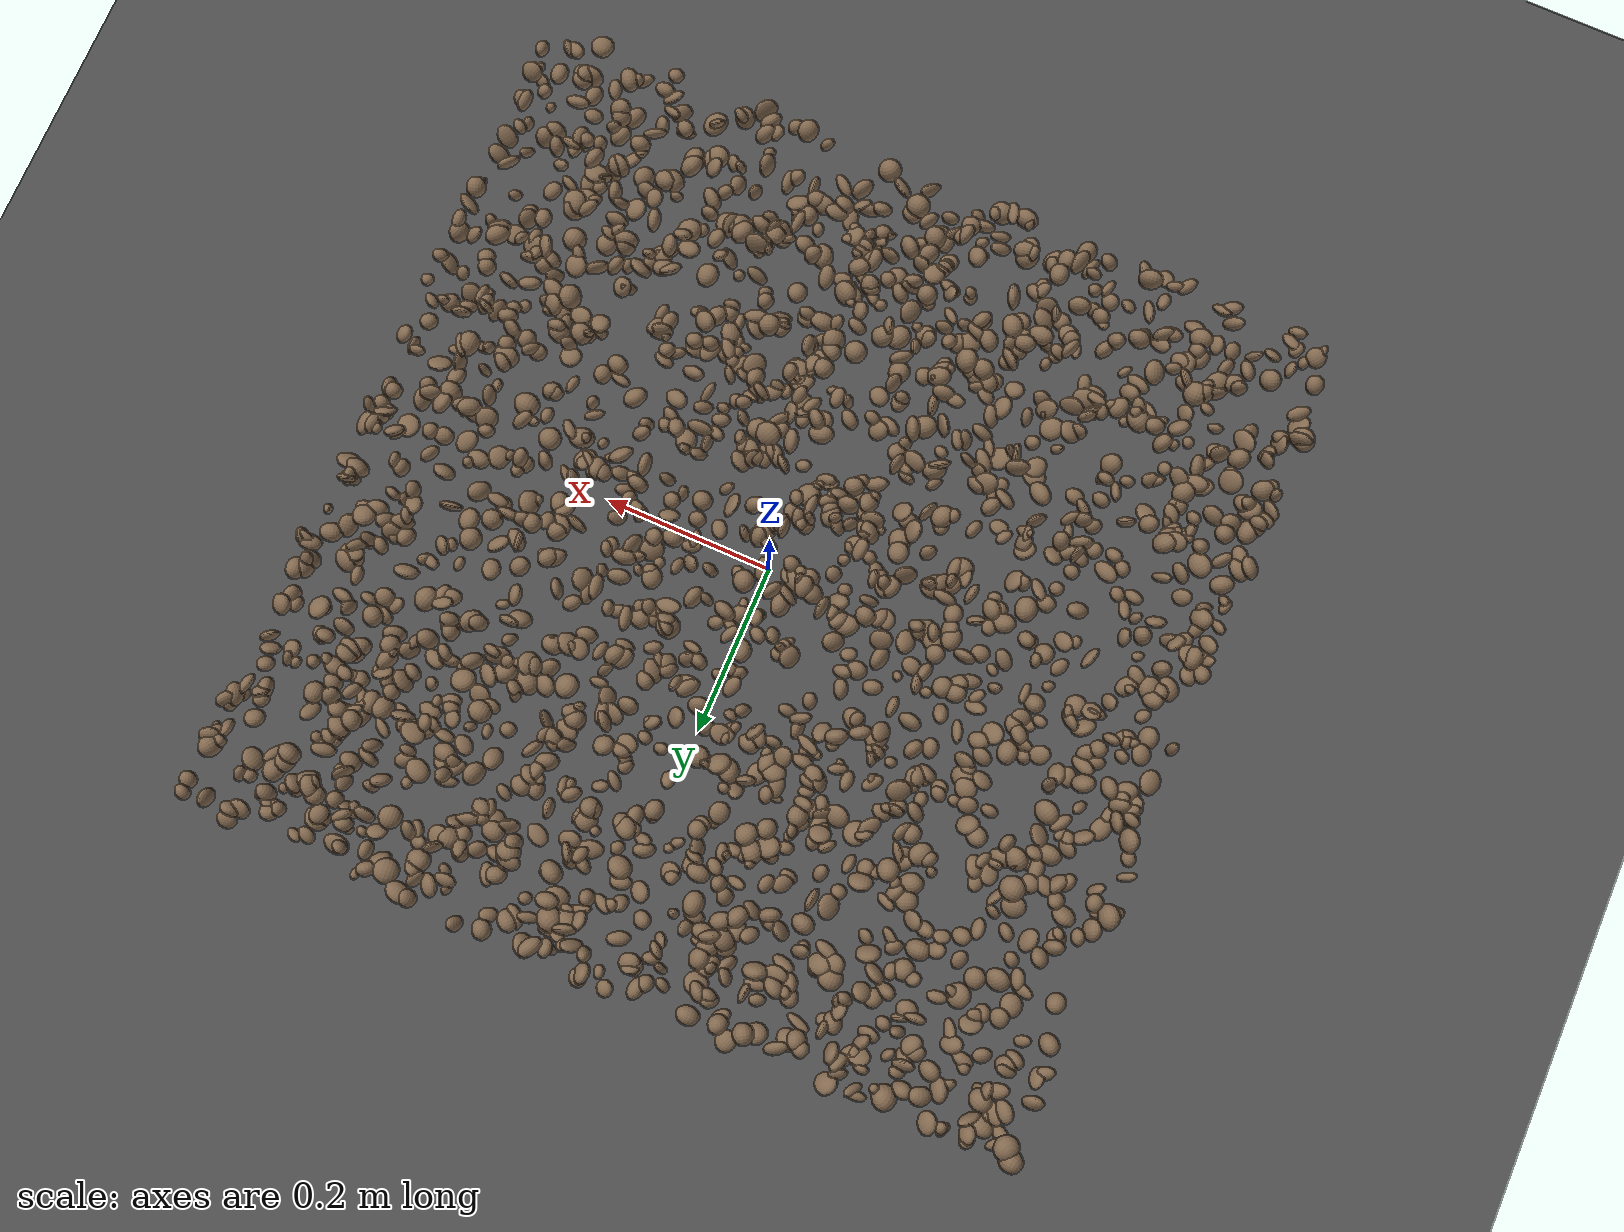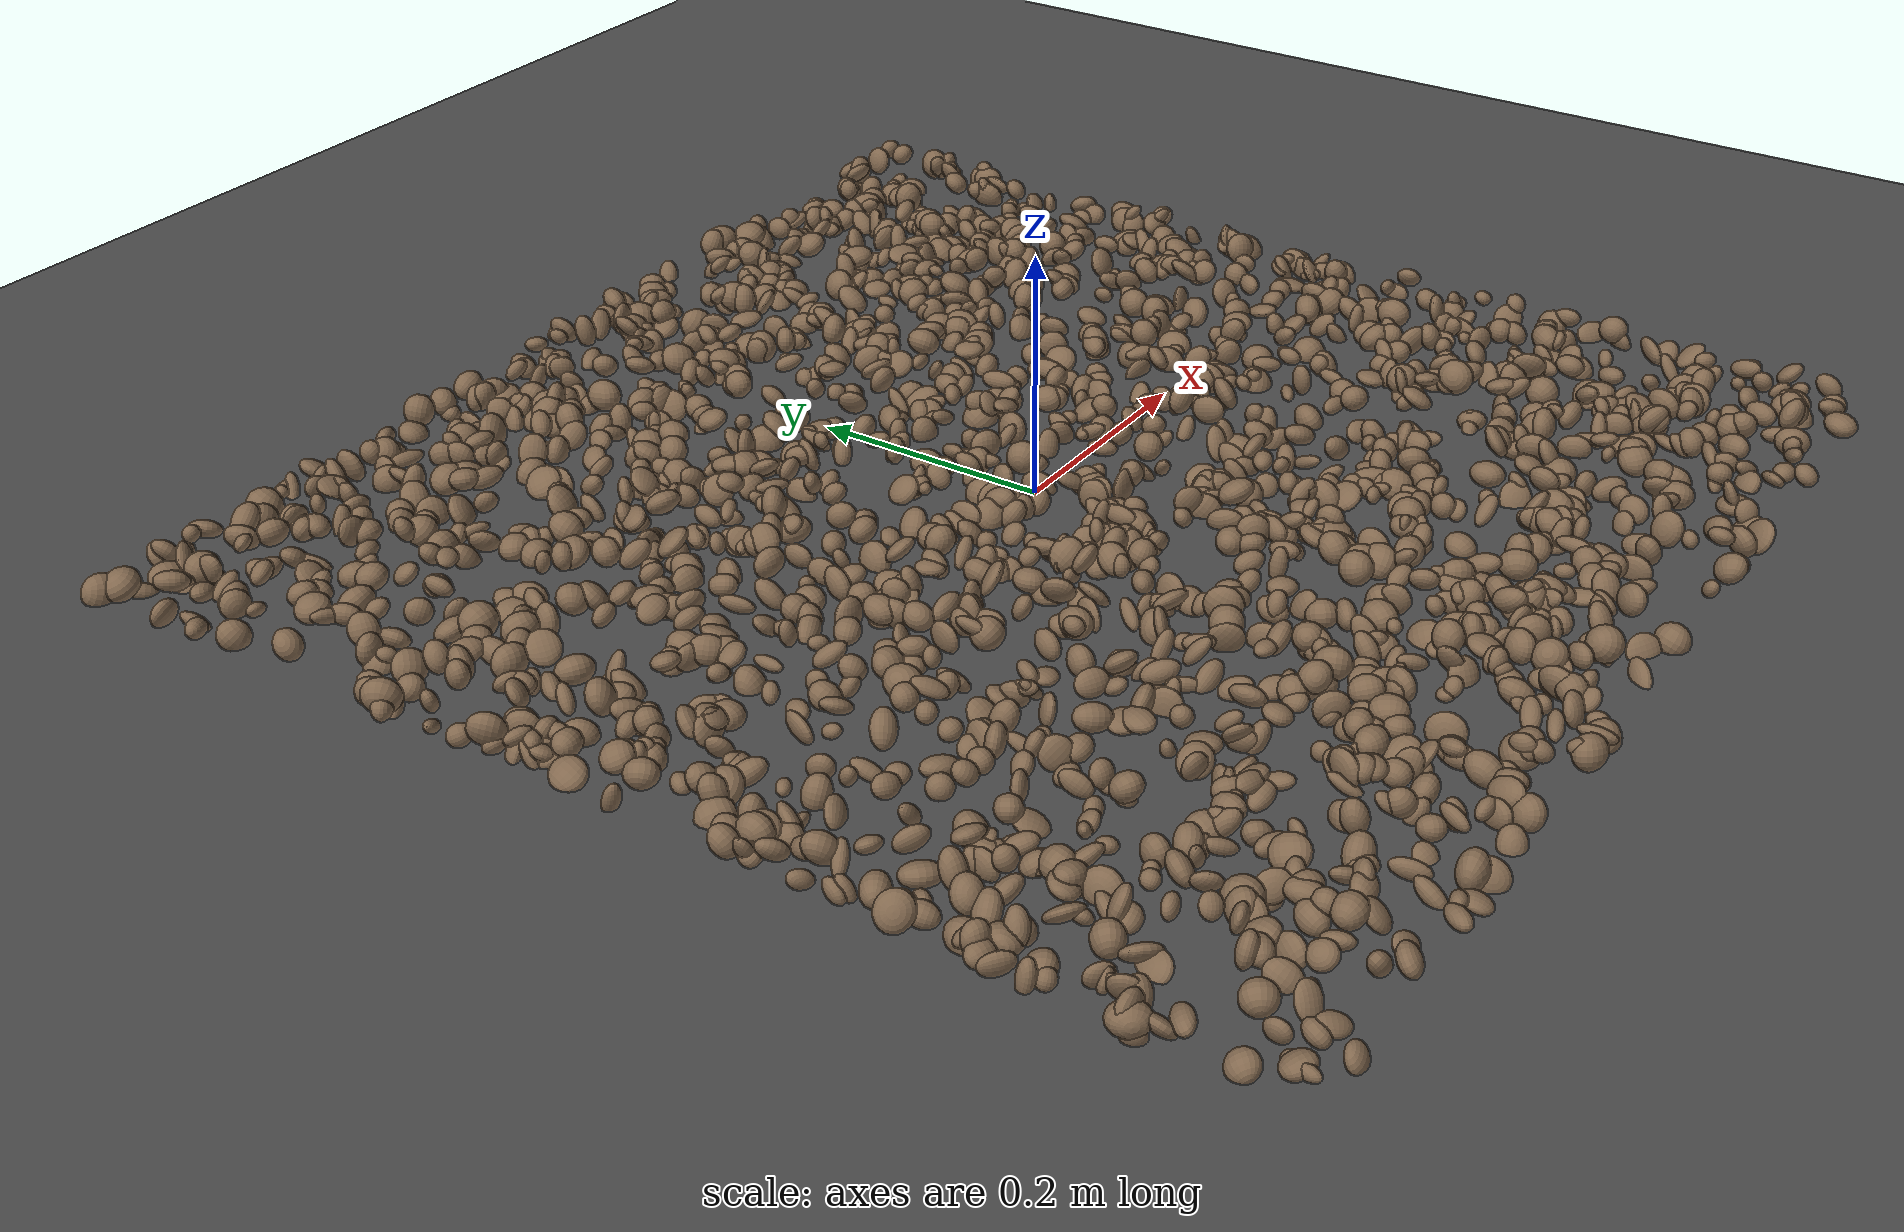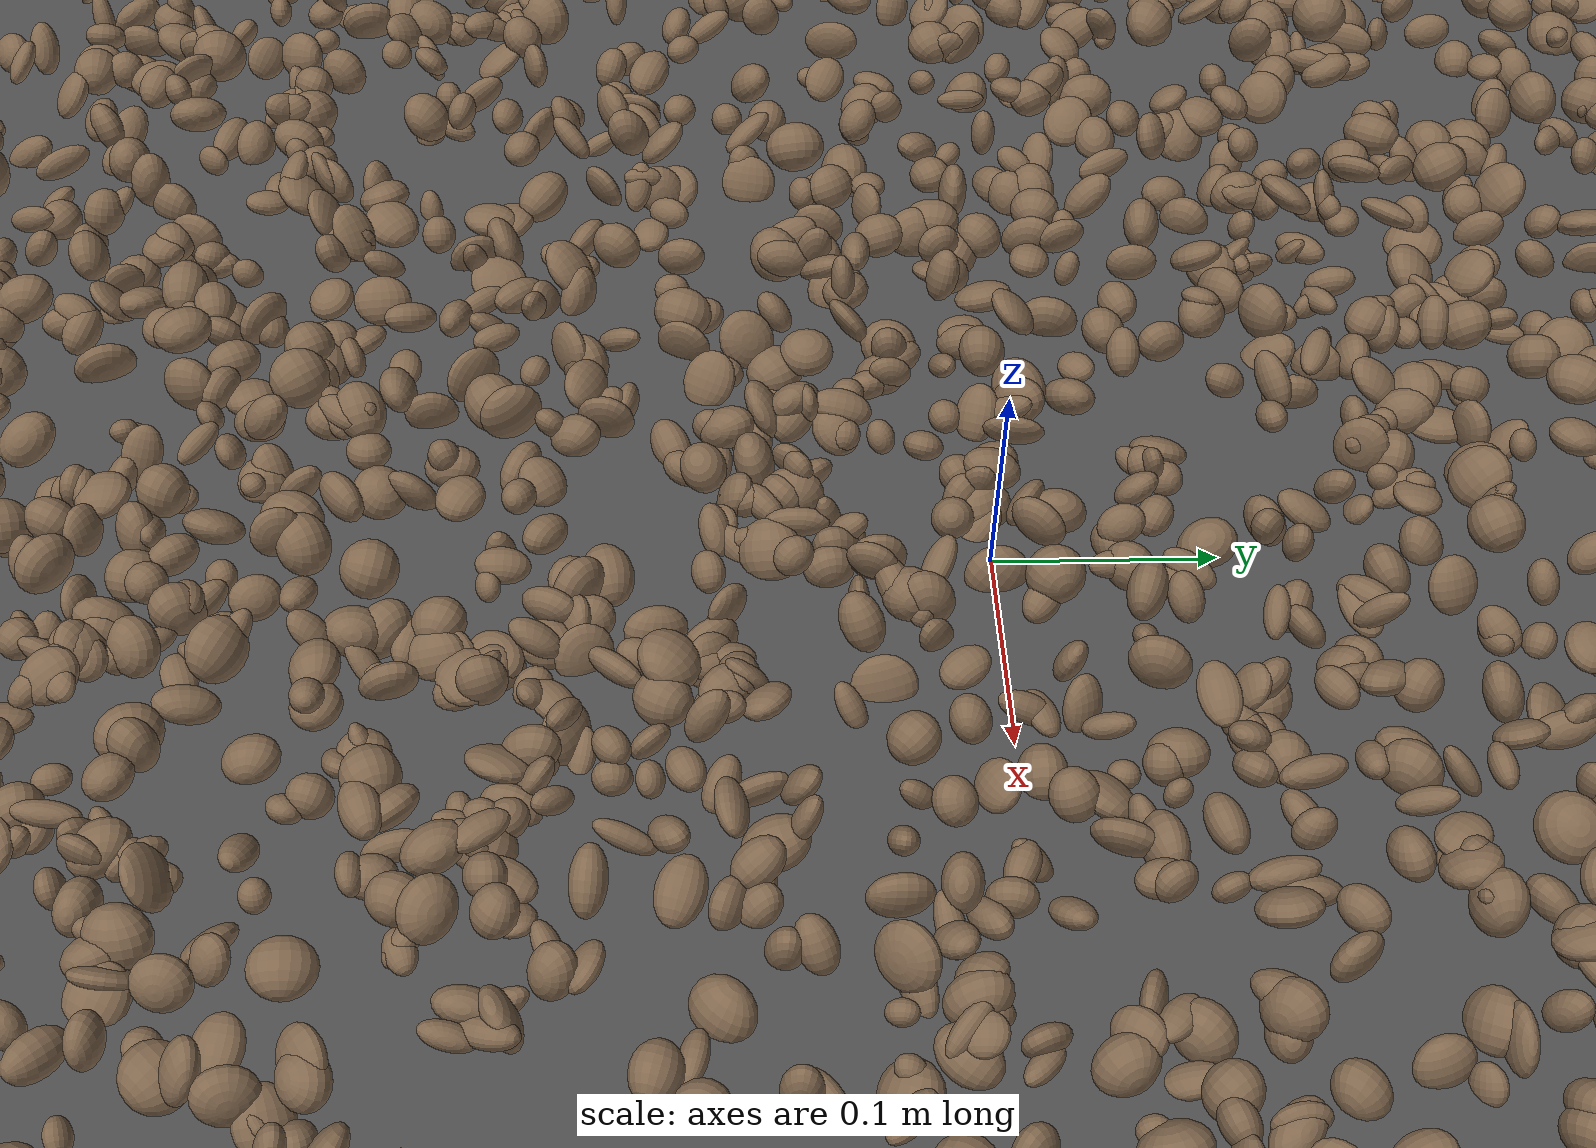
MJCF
<mujoco model="rocky_terrain_scene">
    <compiler angle="radian" inertiafromgeom="true" />
    <option timestep="0.002" gravity="0 0 -9.81" />

    <worldbody>
        <light name="sunlight" pos="5 5 5" dir="-1 -1 -1" diffuse="1 1 1" specular="0.5 0.5 0.5" ambient="0.5 0.5 0.5" />

        <geom name="ground_plane" type="plane" size="50 50 0.1" rgba="0.3 0.3 0.3 1" />

        <body name="rocky_terrain_body">

        <geom name="rock1" type="ellipsoid" size="0.005286978474122679 0.006736553089955584 0.012318425584050267" pos="0.3225719404368155 0.3368082827957213 0.012255786487782415" quat="0.27286050943671647 0.38790956354708533 0.0036707870886470532 0.33555913992755104" rgba="0.5 0.4 0.3 1" /><geom name="rock2" type="ellipsoid" size="0.012163881351614558 0.009202939357993642 0.01140338279510631" pos="0.3379615993428713 -0.1800684498294871 0.0027238184957862543" quat="0.3411250433527998 0.0008143065139330312 0.32389100209352606 0.3341696480397412" rgba="0.5 0.4 0.3 1" /><geom name="rock3" type="ellipsoid" size="0.014366420799109995 0.007838841754928999 0.0067673861777983" pos="-0.29333524953479795 -0.47222391901428595 0.002852173681029329" quat="0.2872070164036437 0.2767685491730799 0.04974491767006344 0.3862795167532128" rgba="0.5 0.4 0.3 1" /><geom name="rock4" type="ellipsoid" size="0.007543652198745095 0.013387501446883159 0.007134569082472415" pos="0.14500509935870998 -0.14227182050361153 0.005891706745994418" quat="0.06349825648396785 0.267289227878215 0.481961149231361 0.1872513664064561" rgba="0.5 0.4 0.3 1" /><geom name="rock5" type="ellipsoid" size="0.011131257790725317 0.008837614430811467 0.007831323322377622" pos="-0.49961718896545715 0.1990597992137937 0.010903799698767471" quat="0.32573374788651255 0.4231289937927645 0.04097852256581576 0.21015873575490718" rgba="0.5 0.4 0.3 1" /><geom name="rock6" type="ellipsoid" size="0.008403732574484036 0.00976170119035067 0.011711425222243034" pos="0.17958368040805384 0.38178873097856403 0.005532301283177007" quat="0.2987678924420146 0.012669082036567995 0.14016222062907346 0.5484008048923439" rgba="0.5 0.4 0.3 1" /><geom name="rock7" type="ellipsoid" size="0.011475754129963676 0.01458307972089122 0.011115402168089848" pos="-0.1691687840528644 -0.45069938014531874 0.013024842384447177" quat="0.40179260221608626 0.09306216351341928 0.3871791253426117 0.11796610892788273" rgba="0.5 0.4 0.3 1" /><geom name="rock8" type="ellipsoid" size="0.010746247946516574 0.005277216465624171 0.0143940289829433" pos="0.487904594044005 -0.34789964175785204 0.009527803307568262" quat="0.43597150681907854 0.21179178578002486 0.14225434089750472 0.20998236650339194" rgba="0.5 0.4 0.3 1" /><geom name="rock9" type="ellipsoid" size="0.008388976655764855 0.014930681571433613 0.010400702440170039" pos="0.33985622640097435 -0.16329988394046246 0.004662420890009879" quat="0.3184334222237181 0.1517812677884215 0.20523324026731068 0.3245520697205497" rgba="0.5 0.4 0.3 1" /><geom name="rock10" type="ellipsoid" size="0.013078620209803472 0.007562282265120172 0.014112380887068461" pos="-0.2308271349686719 -0.2795462403625155 0.004402522006828393" quat="0.12807003476560308 0.17805353351836417 0.3915227807200536 0.3023536509959792" rgba="0.5 0.4 0.3 1" /><geom name="rock11" type="ellipsoid" size="0.005665482361687395 0.006943797375727849 0.010625096557839353" pos="0.12310427072003938 0.193651560891538 0.010283035538738652" quat="0.18742072197157345 0.29163149915859415 0.2350724274326106 0.28587535143722187" rgba="0.5 0.4 0.3 1" /><geom name="rock12" type="ellipsoid" size="0.0052814503828930714 0.014905523142296727 0.010975934580803882" pos="-0.21662553476344304 -0.2966780822913385 0.010901799079238186" quat="0.3223093269707847 0.36902462324227087 0.012472453524991671 0.2961935962619528" rgba="0.5 0.4 0.3 1" /><geom name="rock13" type="ellipsoid" size="0.0076769582853993676 0.009395656834962424 0.008675016192910712" pos="-0.1410713520345349 0.277784207632213 0.0028706140544977" quat="0.11606958443017962 0.3477614007819641 0.4196013846294835 0.11656763015837286" rgba="0.5 0.4 0.3 1" /><geom name="rock14" type="ellipsoid" size="0.013039651488335847 0.01015662198524648 0.01055352344192374" pos="-0.10678132497855763 0.3787594310545649 0.010718640279590772" quat="0.6183050666573482 0.009794891441442757 0.14782952413554265 0.22407051776566644" rgba="0.5 0.4 0.3 1" /><geom name="rock15" type="ellipsoid" size="0.01428076062945342 0.012921678107183018 0.006264694736782263" pos="-0.1553989548833843 -0.3347681869787299 0.010376272666413765" quat="0.07948488302695446 0.18915318593286135 0.3557122194582727 0.37564971158191157" rgba="0.5 0.4 0.3 1" /><geom name="rock16" type="ellipsoid" size="0.011230391412103403 0.009124596508119934 0.00842955531503895" pos="0.18836036544954704 0.12406573355674289 0.00839304572689746" quat="0.39358204218379 0.32139111205024873 0.15390197188620233 0.13112487387975905" rgba="0.5 0.4 0.3 1" /><geom name="rock17" type="ellipsoid" size="0.01485758638359988 0.008881516723271145 0.00939626430597476" pos="-0.4362767571417149 -0.21956771638020578 0.00904638836382202" quat="0.12325961732075716 0.4506361841918664 0.02883852533924688 0.39726567314812955" rgba="0.5 0.4 0.3 1" /><geom name="rock18" type="ellipsoid" size="0.009612540796415953 0.00934858724124191 0.011625886555363594" pos="-0.020998496671907785 -0.015466756159614015 0.006529231602764103" quat="0.27819848482856635 0.1850948550302225 0.06225974824252561 0.4744469118986856" rgba="0.5 0.4 0.3 1" /><geom name="rock19" type="ellipsoid" size="0.014533849453802268 0.01051493605289482 0.006242698410516533" pos="0.21901841465170302 0.4718607875182602 0.0068706736983679614" quat="0.3536307566286421 0.28089388657691844 0.35367388252439 0.011801474270049366" rgba="0.5 0.4 0.3 1" /><geom name="rock20" type="ellipsoid" size="0.014500078405992316 0.0051493385950063374 0.007964449342699995" pos="0.3439325956357058 0.28358225284623195 0.006436432740243451" quat="0.25640507562018494 0.11152769362754628 0.2476570088329665 0.38441022191930224" rgba="0.5 0.4 0.3 1" /><geom name="rock21" type="ellipsoid" size="0.011187492120412538 0.01447090915151033 0.007594875201043572" pos="-0.36188258973478715 0.17575499958182084 0.01346477558421176" quat="0.27026773947242 0.2991534236619336 0.23750833000700455 0.1930705068586419" rgba="0.5 0.4 0.3 1" /><geom name="rock22" type="ellipsoid" size="0.010285890370576367 0.013640728848224745 0.00621086677109708" pos="0.3058594322461825 0.32296946488529343 0.0023242468913468556" quat="0.26637324323845757 0.22823776168608625 0.2452268276575818 0.26016216741787435" rgba="0.5 0.4 0.3 1" /><geom name="rock23" type="ellipsoid" size="0.006645305027612482 0.010433834892803008 0.007629244778132968" pos="0.029320848796417165 0.2334806095302583 0.013820222605352853" quat="0.3322362300044515 0.25733864108112353 0.10578902271937221 0.3046361061950529" rgba="0.5 0.4 0.3 1" /><geom name="rock24" type="ellipsoid" size="0.00982027263058491 0.013593265383523647 0.014264115953249164" pos="0.04718014599387521 0.4435465250815156 0.0061100032290209135" quat="0.2749868593873317 0.2664363842331765 0.3595398925655741 0.0990368638139176" rgba="0.5 0.4 0.3 1" /><geom name="rock25" type="ellipsoid" size="0.010267520414122894 0.008283736035929492 0.014652061808290994" pos="0.17611723571417215 -0.13779255434750215 0.012392584756796606" quat="0.2425095496725841 0.3317280487469794 0.28095796978140897 0.1448044317990275" rgba="0.5 0.4 0.3 1" /><geom name="rock26" type="ellipsoid" size="0.012797801285590377 0.0073606657724992475 0.011979986226317435" pos="-0.16383263851525254 0.4937427347736637 0.004519543913943574" quat="0.30749165542673684 0.28498218118426766 0.2331290322824175 0.17439713110657798" rgba="0.5 0.4 0.3 1" /><geom name="rock27" type="ellipsoid" size="0.01413703380872713 0.011505189469629508 0.014212174499767905" pos="0.2250094460569425 0.22481993681301937 0.0023276894688540593" quat="0.13574493309593283 0.6124332054438135 0.23460501542910875 0.0172168460311449" rgba="0.5 0.4 0.3 1" /><geom name="rock28" type="ellipsoid" size="0.00675224390201474 0.00872739211974116 0.006774702974573854" pos="-0.3445508338703658 0.03672006803268224 0.010291778689954628" quat="0.4935651854884894 0.12981524606591993 0.007357426790780984 0.36926214165480975" rgba="0.5 0.4 0.3 1" /><geom name="rock29" type="ellipsoid" size="0.006777687145012415 0.00580590517607258 0.0100909344798919" pos="0.19576696250628645 -0.2447272936632391 0.004952681808776255" quat="0.14313426562458056 0.27313400713946084 0.27032100270376547 0.3134107245321931" rgba="0.5 0.4 0.3 1" /><geom name="rock30" type="ellipsoid" size="0.010145208715872031 0.01044377755587872 0.009860609004129406" pos="0.38169160041540984 -0.11871781590491837 0.011803043592879306" quat="0.18836920401492524 0.46346897027223766 0.13402561103995053 0.21413621467288646" rgba="0.5 0.4 0.3 1" /><geom name="rock31" type="ellipsoid" size="0.011597870349169558 0.009274673355645737 0.011191901647861725" pos="-0.48932520067638674 -0.4495606602087826 0.0025561654877672094" quat="0.2795621291610704 0.01589034409571554 0.3281075515231462 0.37643997522006784" rgba="0.5 0.4 0.3 1" /><geom name="rock32" type="ellipsoid" size="0.00595794645187334 0.011098743072536832 0.013759038299107611" pos="-0.052874640901063974 0.3267134122528249 0.012424574976071915" quat="0.08859826481896604 0.4895662870865482 0.3876714955023634 0.03416395259212232" rgba="0.5 0.4 0.3 1" /><geom name="rock33" type="ellipsoid" size="0.006258803466505667 0.006492748921627553 0.014013199138411193" pos="0.04250385544325619 -0.32640677238477156 0.009388532384431152" quat="0.22399740246535838 0.4817255892069896 0.1963666003304052 0.09791040799724682" rgba="0.5 0.4 0.3 1" /><geom name="rock34" type="ellipsoid" size="0.01451516692863404 0.01286291493390919 0.006972825181386869" pos="-0.3546419061741517 0.21364169309550285 0.004916385129428956" quat="0.028686219402525696 0.23133922132157836 0.6222668922368072 0.11770766703908872" rgba="0.5 0.4 0.3 1" /><geom name="rock35" type="ellipsoid" size="0.012337987489127351 0.008694435568470792 0.014644831372198842" pos="0.2639399895777125 -0.28906657223426346 0.0015431791206056828" quat="0.17879103097416224 0.24633476653954334 0.40587507375631626 0.16899912872997805" rgba="0.5 0.4 0.3 1" /><geom name="rock36" type="ellipsoid" size="0.014523743960778077 0.013478300730266051 0.006469768437052016" pos="-0.2144199465844202 -0.3742122520932234 0.011473477884757341" quat="0.22799113846608343 0.3634579985853347 0.09309581297516882 0.315455049973413" rgba="0.5 0.4 0.3 1" /><geom name="rock37" type="ellipsoid" size="0.010535871570936 0.013493524130767855 0.009671183331510406" pos="-0.32057200511237616 0.05240810790825956 0.008853723588666559" quat="0.005878834785147241 0.45222803673557777 0.28932588442921264 0.25256724405006237" rgba="0.5 0.4 0.3 1" /><geom name="rock38" type="ellipsoid" size="0.005453743891471443 0.014674668567774676 0.006474256661315882" pos="-0.4916037833950254 0.005966617594066137 0.005845921576399325" quat="0.2818101036694677 0.37894553260904956 0.1368803764286346 0.20236398729284813" rgba="0.5 0.4 0.3 1" /><geom name="rock39" type="ellipsoid" size="0.01425876004596174 0.005849626071278024 0.008384014027713662" pos="-0.17142306140708818 -0.05590910400790261 0.013302394872676282" quat="0.5245546975179006 0.004977328059408305 0.44112078671508614 0.029347187707605017" rgba="0.5 0.4 0.3 1" /><geom name="rock40" type="ellipsoid" size="0.01375261399923457 0.013637723624834577 0.008586146706369055" pos="-0.42973573310871105 0.19427241977906828 0.008438248790389907" quat="0.3042661866562712 0.32422469497351625 0.12401305861499953 0.24749605975521302" rgba="0.5 0.4 0.3 1" /><geom name="rock41" type="ellipsoid" size="0.007361863819415997 0.008462250683235334 0.009549845111312197" pos="0.1045500300219756 -0.16525676510888154 0.010302407270580051" quat="0.1342459019242898 0.22122660222212406 0.2569450894623719 0.38758240639121416" rgba="0.5 0.4 0.3 1" /><geom name="rock42" type="ellipsoid" size="0.009017298614361367 0.00522379788164811 0.013427874110238987" pos="0.3313732005458401 -0.4737031653694169 0.0001757852966051343" quat="0.04652878027637767 0.3238645042901346 0.3228197024732146 0.30678701296027316" rgba="0.5 0.4 0.3 1" /><geom name="rock43" type="ellipsoid" size="0.0054705383137137855 0.010833430066515468 0.006112661754716345" pos="-0.24541429609996346 -0.26084725259406216 0.00029149826195760785" quat="0.2285203740466352 0.09185814257564881 0.2933347644520973 0.3862867189256187" rgba="0.5 0.4 0.3 1" /><geom name="rock44" type="ellipsoid" size="0.0070567446352295836 0.0065321275331530985 0.005741787833349592" pos="0.27485413466532005 0.0317798116460678 0.0002851718381102947" quat="0.23873894361618914 0.2594652899478314 0.15340440584717238 0.3483913605888071" rgba="0.5 0.4 0.3 1" /><geom name="rock45" type="ellipsoid" size="0.009556888360198822 0.012466062534562783 0.009926956803755828" pos="-0.4628122266798458 -0.285205547239338 0.008973002231032437" quat="0.340785919502887 0.061814166773470465 0.327832770184422 0.2695671435392205" rgba="0.5 0.4 0.3 1" /><geom name="rock46" type="ellipsoid" size="0.0070770147025794325 0.013620898637180977 0.011817100760128332" pos="-0.4938902845523643 0.4197806090231775 0.006577540255736388" quat="0.2606396713573703 0.2393117952599356 0.13188227196047383 0.3681662614222203" rgba="0.5 0.4 0.3 1" /><geom name="rock47" type="ellipsoid" size="0.007052642077288125 0.007127741117724938 0.011663602937408061" pos="-0.35535966271857244 0.35855695971846946 0.00952389746191594" quat="0.21136851716222887 0.24466478676785003 0.2604821178912206 0.2834845781787004" rgba="0.5 0.4 0.3 1" /><geom name="rock48" type="ellipsoid" size="0.009384067143895216 0.01124276239799276 0.007495803842581002" pos="0.432263869312666 0.26993210140484736 0.005466666685933492" quat="0.04285577471180165 0.4180737523242221 0.2652529440634739 0.2738175289005023" rgba="0.5 0.4 0.3 1" /><geom name="rock49" type="ellipsoid" size="0.005663138632189713 0.007328904105503773 0.010753652290982598" pos="-0.4778524104206131 0.09718779823825885 0.012800070023282662" quat="0.22772262606498522 0.35598616933269167 0.055680715930954076 0.360610488671369" rgba="0.5 0.4 0.3 1" /><geom name="rock50" type="ellipsoid" size="0.014770956506070444 0.013650437150061295 0.014473521472316293" pos="-0.34433008547078003 0.47942503409210957 0.004971468000931975" quat="0.2905708609784091 0.21922354097464258 0.06351530877731243 0.426690289269636" rgba="0.5 0.4 0.3 1" /><geom name="rock51" type="ellipsoid" size="0.005767297396219669 0.009446140661870592 0.006587999510902569" pos="0.13999829023704768 -0.4916896853296169 0.003997500776073013" quat="0.23424370927771376 0.18923796616353766 0.138389645833053 0.43812867872569555" rgba="0.5 0.4 0.3 1" /><geom name="rock52" type="ellipsoid" size="0.008179421921655423 0.005004435985599496 0.01004054870994958" pos="-0.3351179506484533 0.2970683129817072 0.013280867469546568" quat="0.14790279297580414 0.22956684471213082 0.24258976284317613 0.379940599468889" rgba="0.5 0.4 0.3 1" /><geom name="rock53" type="ellipsoid" size="0.0111908804956536 0.010552022200011073 0.007480092502316104" pos="0.05739329641537183 0.4823546325320679 0.005627435459966452" quat="0.2524600773404375 0.2134831758450306 0.14210957994280468 0.3919471668717272" rgba="0.5 0.4 0.3 1" /><geom name="rock54" type="ellipsoid" size="0.006662912845969826 0.005999217186550678 0.012993737670003749" pos="-0.3838544992557782 -0.11743669316381167 0.011707486616374779" quat="0.31453591801226 0.5455787463033192 0.06879304104138254 0.0710922946430383" rgba="0.5 0.4 0.3 1" /><geom name="rock55" type="ellipsoid" size="0.010215878498431157 0.009231198022694722 0.011603450738614931" pos="-0.39719823112232 -0.2548340548906668 0.0018314884477470073" quat="0.5579150139515658 0.2566945326030147 0.14497907703580132 0.04041137640961799" rgba="0.5 0.4 0.3 1" /><geom name="rock56" type="ellipsoid" size="0.011353374302688547 0.01274992634932381 0.01152506885866595" pos="-0.13229913433232088 -0.31014579585166147 0.013560007411669276" quat="0.011428797143792377 0.40693655167681275 0.2988353356710464 0.28279931550834836" rgba="0.5 0.4 0.3 1" /><geom name="rock57" type="ellipsoid" size="0.00561667544130807 0.007350906258077775 0.012596887789216159" pos="0.35438563470875406 -0.1254155603063588 0.00975932154131059" quat="0.060031838568076736 0.17817650988750477 0.2600702870841692 0.5017213644602493" rgba="0.5 0.4 0.3 1" /><geom name="rock58" type="ellipsoid" size="0.012310095876026297 0.006540481570183693 0.010789753971367588" pos="-0.3578423697725158 0.07163840065864246 0.01461076026267612" quat="0.4434971104018483 0.30748255623090776 0.17898691084993093 0.07003342251731297" rgba="0.5 0.4 0.3 1" /><geom name="rock59" type="ellipsoid" size="0.013788873913180632 0.010570702599563261 0.007768115595638869" pos="-0.059660303194723485 -0.20845698494101472 0.0028754319609980905" quat="0.03815572811621104 0.16289802915020585 0.4029855418989161 0.395960700834667" rgba="0.5 0.4 0.3 1" /><geom name="rock60" type="ellipsoid" size="0.007107705503687056 0.005420512318636046 0.013156932880005856" pos="0.01672586485632055 0.07337507787863895 0.002839492998801223" quat="0.28125599517909566 0.43161598259646683 0.054920994189664354 0.23220702803477308" rgba="0.5 0.4 0.3 1" /><geom name="rock61" type="ellipsoid" size="0.005555502821789649 0.005571703407959977 0.012483661300760417" pos="-0.3160354459258141 0.4901894340597309 0.0022472704445447044" quat="0.15868302008846957 0.2951264509996533 0.14875825954625005 0.3974322693656271" rgba="0.5 0.4 0.3 1" /><geom name="rock62" type="ellipsoid" size="0.012879279013574142 0.010838863124727073 0.014414240611129458" pos="-0.2795239236416903 0.2246057685553584 0.01334366467949207" quat="0.24178120184077273 0.0121909064161105 0.39118821842723533 0.35483967331588145" rgba="0.5 0.4 0.3 1" /><geom name="rock63" type="ellipsoid" size="0.01230838110633314 0.01487646607849916 0.011390052018823722" pos="-0.10520231666072777 0.023275142319048925 0.004173916032432922" quat="0.3138034586210773 0.13895719650414007 0.0833860792469857 0.463853265627797" rgba="0.5 0.4 0.3 1" /><geom name="rock64" type="ellipsoid" size="0.009491016940372167 0.009422911092371608 0.009401428471337608" pos="0.419551420302397 0.008278362063334654 0.007900959821084973" quat="0.46693341692686974 0.13850523273881582 0.06648593103556417 0.32807541929875034" rgba="0.5 0.4 0.3 1" /><geom name="rock65" type="ellipsoid" size="0.011626815083400315 0.014956124368165489 0.01466326041227864" pos="-0.31770394779629973 0.32053501398593187 0.004396217326230786" quat="0.22645970307118288 0.2545860829610732 0.24489621182143953 0.2740580021463044" rgba="0.5 0.4 0.3 1" /><geom name="rock66" type="ellipsoid" size="0.011313812371058888 0.007599332332575982 0.011293907543106222" pos="-0.20554734039753397 -0.3884642879823461 0.012374322726420573" quat="0.13763756585495437 0.1492957888847943 0.31947663285975986 0.3935900124004915" rgba="0.5 0.4 0.3 1" /><geom name="rock67" type="ellipsoid" size="0.012730592782059756 0.014524214116329655 0.008192259228365847" pos="-0.2515621689465347 -0.2847824245150328 0.004628269670921025" quat="0.05571623515900889 0.36222839406123203 0.4251662323709464 0.15688913840881263" rgba="0.5 0.4 0.3 1" /><geom name="rock68" type="ellipsoid" size="0.010518847089541011 0.009406832680804807 0.011018883787829146" pos="0.18485520098274633 -0.2085928148815197 0.014835389027901966" quat="0.16307002709867163 0.675756976788714 0.0697629305161505 0.09141006559646381" rgba="0.5 0.4 0.3 1" /><geom name="rock69" type="ellipsoid" size="0.005121300310333809 0.009617142338651425 0.006574539481090223" pos="-0.4889519404668926 -0.2638356796294412 0.012384751491142546" quat="0.030111266418729663 0.3417086883731835 0.25833420574519045 0.3698458394628964" rgba="0.5 0.4 0.3 1" /><geom name="rock70" type="ellipsoid" size="0.00770866218753041 0.014325674487709578 0.011473949947790107" pos="0.04996865471337453 -0.4429491941436242 0.007797399504134895" quat="0.27602273044057013 0.2318384388758567 0.34283805463513145 0.14930077604844183" rgba="0.5 0.4 0.3 1" /><geom name="rock71" type="ellipsoid" size="0.012885328032755428 0.009830846198002247 0.009750013784841515" pos="-0.05920661729399879 -0.2393757563703871 0.005101150952541479" quat="0.19836062667346818 0.31728986363589673 0.2452020010459339 0.23914750864470122" rgba="0.5 0.4 0.3 1" /><geom name="rock72" type="ellipsoid" size="0.013517975689421185 0.0135508280072414 0.013140038776925631" pos="0.06055592548881272 -0.4925350821472121 0.002304422922797284" quat="0.5545402138298422 0.1324467520055092 0.1274331009423416 0.18557993322230704" rgba="0.5 0.4 0.3 1" /><geom name="rock73" type="ellipsoid" size="0.005384450833038405 0.006360571136113486 0.006969133528360285" pos="-0.22594381360233895 0.19266669016505733 0.009286779175950655" quat="0.18501605436369903 0.22848898286591432 0.3440419543171945 0.2424530084531922" rgba="0.5 0.4 0.3 1" /><geom name="rock74" type="ellipsoid" size="0.009707032441308008 0.006803748532661538 0.01301488582795983" pos="0.43680460963248813 -0.031708633501382644 0.014879745032855655" quat="0.354965731897807 0.0004563350750583167 0.4529261819579237 0.19165175106921092" rgba="0.5 0.4 0.3 1" /><geom name="rock75" type="ellipsoid" size="0.013860063546782417 0.01250897368270024 0.014871565802420997" pos="-0.31768802770451 -0.3284099620623554 0.006875098991478063" quat="0.26948550548850597 0.3060003927026553 0.06020790903304815 0.3643061927757907" rgba="0.5 0.4 0.3 1" /><geom name="rock76" type="ellipsoid" size="0.009136046522210459 0.01474238503734178 0.011337829114262695" pos="0.26311717511714583 0.2288820879228567 0.009101025733714513" quat="0.06873060038913592 0.20471322572912287 0.49118016325045766 0.23537601063128355" rgba="0.5 0.4 0.3 1" /><geom name="rock77" type="ellipsoid" size="0.011664022883162317 0.013087459714741966 0.005579932579845974" pos="0.478118721953548 0.016903088087119933 0.003028208067511608" quat="0.4004077775836267 0.20959187319600364 0.3370183960439029 0.05298195317646665" rgba="0.5 0.4 0.3 1" /><geom name="rock78" type="ellipsoid" size="0.006217703677429923 0.005373779846038216 0.005655853520295216" pos="-0.0431483100879565 -0.32667653446651257 0.012506656284602737" quat="0.32263283048511937 0.4340041045099716 0.06243570409897881 0.18092736090593003" rgba="0.5 0.4 0.3 1" /><geom name="rock79" type="ellipsoid" size="0.005428248409834356 0.014572062865309581 0.0055681294113685866" pos="0.18437835381249246 0.17234783168006695 0.009758466183911447" quat="0.1552096703481358 0.37714194015178026 0.2841909288445556 0.18345746065552834" rgba="0.5 0.4 0.3 1" /><geom name="rock80" type="ellipsoid" size="0.007564320323630562 0.013629877534154723 0.0051452838281671786" pos="-0.2011695137005628 0.1695346841110007 0.0005678065183976677" quat="0.09362645307889356 0.23508865222158537 0.40425279560954563 0.26703209908997555" rgba="0.5 0.4 0.3 1" /><geom name="rock81" type="ellipsoid" size="0.011929526558263424 0.014304771363712984 0.010222855663417334" pos="0.3682162678085378 -0.4043397415153429 0.002290233511854214" quat="0.2733547172165744 0.26466368695988957 0.08255883084445502 0.37942276497908095" rgba="0.5 0.4 0.3 1" /><geom name="rock82" type="ellipsoid" size="0.007596603912582343 0.014935590493275062 0.005077428604961869" pos="-0.4894445799578042 -0.1000037584262421 0.007566606031078205" quat="0.2945468023945805 0.195972075094184 0.181979558808129 0.3275015637031065" rgba="0.5 0.4 0.3 1" /><geom name="rock83" type="ellipsoid" size="0.005930199414211314 0.011926789783249162 0.007172385410136118" pos="-0.2838831840723486 0.02287394319159952 0.014590489830093038" quat="0.27639545143259525 0.20692277060006745 0.22798150955276592 0.2887002684145714" rgba="0.5 0.4 0.3 1" /><geom name="rock84" type="ellipsoid" size="0.014788887162865003 0.014840407014964203 0.0110218962080172" pos="0.276470682463573 -0.4115016943511849 0.005271584519624721" quat="0.5037321666090843 0.062245597846592865 0.3197906373322286 0.11423159821209428" rgba="0.5 0.4 0.3 1" /><geom name="rock85" type="ellipsoid" size="0.013328471517630579 0.009542552606995689 0.0055589793412509" pos="-0.251426881865349 0.20986037686341874 0.012992769829696424" quat="0.21325094134478464 0.39917026189512017 0.22838067299144518 0.15919812376865006" rgba="0.5 0.4 0.3 1" /><geom name="rock86" type="ellipsoid" size="0.007502444853163705 0.014779068902235272 0.0062494990360967085" pos="0.1426437952439995 -0.37347670779469644 0.009749177130227686" quat="0.10249075508818214 0.26707577025011786 0.32194723818327076 0.30848623647842915" rgba="0.5 0.4 0.3 1" /><geom name="rock87" type="ellipsoid" size="0.007139571245373206 0.008694725530558979 0.0065967633305380104" pos="0.13503081615213208 -0.21723384183611694 0.007333998747967728" quat="0.3792555974763582 0.15216206834180163 0.37345533352482935 0.09512700065701091" rgba="0.5 0.4 0.3 1" /><geom name="rock88" type="ellipsoid" size="0.00819367238532128 0.009668117915380189 0.01466284393404214" pos="-0.2560427818678971 0.02593560562533359 0.002010675647454676" quat="0.30654726332567117 0.10769600259301279 0.2817567428423497 0.3039999912389663" rgba="0.5 0.4 0.3 1" /><geom name="rock89" type="ellipsoid" size="0.006882270136457837 0.0104266577756487 0.00815961311407716" pos="-0.3307228265984403 0.1506380691270517 0.011031242067923984" quat="0.04356769993224126 0.41941408675702874 0.4003241273558446 0.1366940859548853" rgba="0.5 0.4 0.3 1" /><geom name="rock90" type="ellipsoid" size="0.013923521341688654 0.010681931390078427 0.011218480237684163" pos="-0.2185619219674132 -0.009204644459444355 0.011039866802612808" quat="0.24454091262293218 0.27924588409890605 0.22892315515789619 0.24729004812026564" rgba="0.5 0.4 0.3 1" /><geom name="rock91" type="ellipsoid" size="0.009152147744198565 0.01233848484355814 0.013055124333070756" pos="-0.20518003347934666 -0.4263622110785167 0.008748192425446352" quat="0.16433223724208945 0.2907593963341616 0.25470254281342314 0.2902058236103258" rgba="0.5 0.4 0.3 1" /><geom name="rock92" type="ellipsoid" size="0.00501570488542633 0.00976296583581765 0.01325167592380256" pos="-0.3740991896055882 0.2333564027734092 0.003520665982910914" quat="0.14234372564698713 0.05060168529799492 0.4075450872436599 0.39950950181135814" rgba="0.5 0.4 0.3 1" /><geom name="rock93" type="ellipsoid" size="0.01241203389345526 0.011111337880468213 0.014705132201820174" pos="-0.26546765175388287 -0.049817803727399634 0.005320489878892591" quat="0.07890668163184128 0.4481268544343451 0.17459463329716693 0.29837183063664674" rgba="0.5 0.4 0.3 1" /><geom name="rock94" type="ellipsoid" size="0.01344805588050706 0.00886533056347267 0.010091437532131712" pos="0.11065747984764063 0.15826803490420382 0.0044167628693910724" quat="0.39145704442052637 0.2156525875575838 0.19935792788574971 0.1935324401361402" rgba="0.5 0.4 0.3 1" /><geom name="rock95" type="ellipsoid" size="0.005535684028857544 0.013730682773893398 0.012502744450881412" pos="0.1489138343671812 0.3787485594055181 0.00777050896854834" quat="0.19432639617359748 0.23565961533194366 0.14758566423548009 0.42242832425897875" rgba="0.5 0.4 0.3 1" /><geom name="rock96" type="ellipsoid" size="0.009382658727457579 0.007335517085737932 0.010592986299173858" pos="0.3088569523535468 0.05142844056160689 0.00011552295401460799" quat="0.18757032993158917 0.3882922002810284 0.1701424149867501 0.25399505480063234" rgba="0.5 0.4 0.3 1" /><geom name="rock97" type="ellipsoid" size="0.008728700862361459 0.009496734307217328 0.007508742008108823" pos="0.004558393254473381 -0.08716637339558486 0.011926883927292568" quat="0.3966291698263684 0.02921428527509099 0.3569884121860746 0.21716813271246604" rgba="0.5 0.4 0.3 1" /><geom name="rock98" type="ellipsoid" size="0.00814558238366786 0.0136683662794061 0.008339601962106088" pos="0.14910948237836696 0.4359167937327383 0.003161691893681721" quat="0.6721824513422443 0.029714153027093754 0.12134095301835275 0.17676244261230922" rgba="0.5 0.4 0.3 1" /><geom name="rock99" type="ellipsoid" size="0.008625084679231416 0.011463083391369219 0.009269704494783003" pos="0.16722768365083174 -0.2132936025059854 0.012555396970757454" quat="0.20332202054032847 0.2692269476591194 0.38141664802555914 0.14603438377499295" rgba="0.5 0.4 0.3 1" /><geom name="rock100" type="ellipsoid" size="0.008975412142605648 0.012005076341810604 0.014542657095274646" pos="0.35698473294462674 0.23613104043937583 0.0038452894043488318" quat="0.2662028615193044 0.15952592259666468 0.1182972710226897 0.4559739448613413" rgba="0.5 0.4 0.3 1" /><geom name="rock101" type="ellipsoid" size="0.005777604754123786 0.010037026802379605 0.010514582870050386" pos="0.37351595735911236 0.377610201025819 0.003054914865219591" quat="0.5419257756974988 0.12206424473726923 0.2986303534489961 0.0373796261162359" rgba="0.5 0.4 0.3 1" /><geom name="rock102" type="ellipsoid" size="0.00995540385928774 0.007011189892977776 0.010861075678077158" pos="-0.39346874524566255 0.17286701333559418 0.013371569544918607" quat="0.113352902667188 0.24905847328925612 0.13728058676569102 0.5003080372778648" rgba="0.5 0.4 0.3 1" /><geom name="rock103" type="ellipsoid" size="0.011771753545374953 0.009633542463741387 0.013516541324005843" pos="-0.22487314846175976 0.466058833095754 0.00021998917567886964" quat="0.2764168598825007 0.38964695460533183 0.16181827991813377 0.17211790559403373" rgba="0.5 0.4 0.3 1" /><geom name="rock104" type="ellipsoid" size="0.005178787473218427 0.006955063347322433 0.011240156884016504" pos="-0.423099966883291 0.1997081001196669 0.002816592228180614" quat="0.24411165682297103 0.21469188146326015 0.23491541827209741 0.30628104344167145" rgba="0.5 0.4 0.3 1" /><geom name="rock105" type="ellipsoid" size="0.011085202088284304 0.01364701551520029 0.01406173851571357" pos="0.28737015967921564 -0.3764146863323059 0.009108881772128182" quat="0.42180199778155014 0.24992226589749367 0.30888328324085035 0.019392453080105794" rgba="0.5 0.4 0.3 1" /><geom name="rock106" type="ellipsoid" size="0.0067468302527768 0.011323742784727572 0.010231044077960036" pos="0.06277156199866529 0.14176208673033075 0.0034548028468729137" quat="0.4473204055073386 0.2629708554759787 0.28635531816227255 0.003353420854410254" rgba="0.5 0.4 0.3 1" /><geom name="rock107" type="ellipsoid" size="0.007013285428367369 0.01368012774117544 0.011332496982039777" pos="0.4226381324057077 -0.2654624071340729 0.011268701706435668" quat="0.024008387210075546 0.206284873101079 0.33429121798554673 0.4354155217032987" rgba="0.5 0.4 0.3 1" /><geom name="rock108" type="ellipsoid" size="0.012666525973636492 0.012965710085148109 0.008914105704296257" pos="0.4821841560701423 0.20740988644359737 0.006030732621726127" quat="0.23949906288233935 0.19682021351057793 0.38481591594795495 0.17886480765912777" rgba="0.5 0.4 0.3 1" /><geom name="rock109" type="ellipsoid" size="0.005479729416625353 0.009838268194505381 0.01117678130009582" pos="-0.03664096851939391 0.4637743052445308 0.007872207709646995" quat="0.2853476538532486 0.13818988158147041 0.40850493085459005 0.1679575337106909" rgba="0.5 0.4 0.3 1" /><geom name="rock110" type="ellipsoid" size="0.006413811554237381 0.009895582509403781 0.009759326847054044" pos="-0.020162164305426056 0.49583412191191967 0.0051771145480643" quat="0.14070963567343586 0.48126357277586573 0.021681901831008633 0.35634488971968986" rgba="0.5 0.4 0.3 1" /><geom name="rock111" type="ellipsoid" size="0.009805716689595376 0.011976064035765462 0.012526461413686584" pos="-0.09370588171226069 0.39656343341542977 0.009928452084618644" quat="0.2475420341335971 0.19785506374931025 0.2513288656400616 0.30327403647703105" rgba="0.5 0.4 0.3 1" /><geom name="rock112" type="ellipsoid" size="0.005609276881432986 0.006645840768583847 0.013182072918039568" pos="-0.2891561441517384 -0.19022733082159005 0.011268879959739322" quat="0.024965140174507176 0.2861866034711314 0.4306076987479608 0.2582405576064006" rgba="0.5 0.4 0.3 1" /><geom name="rock113" type="ellipsoid" size="0.013896290365375492 0.0100421570972358 0.01310150868084949" pos="0.2731813933746198 0.4221313791527185 0.007486899884601188" quat="0.33598921052203845 0.16606933582426983 0.24428868765229825 0.25365276600139347" rgba="0.5 0.4 0.3 1" /><geom name="rock114" type="ellipsoid" size="0.006659063900604431 0.007955193810161758 0.005366138471423678" pos="-0.08381253980214942 -0.3908757676628496 0.007393143861295627" quat="0.12191295287934892 0.3205264442695759 0.37035064501657866 0.18720995783449645" rgba="0.5 0.4 0.3 1" /><geom name="rock115" type="ellipsoid" size="0.01203196100791399 0.012514261059813476 0.007873237557571374" pos="0.38595347293354954 0.43106173455370167 0.009381493497592442" quat="0.11283181471802686 0.1175836896998511 0.452416772474507 0.31716772310761493" rgba="0.5 0.4 0.3 1" /><geom name="rock116" type="ellipsoid" size="0.005561150221261287 0.005991809331756342 0.01235099822069333" pos="-0.07319832311808405 -0.35545694619716595 0.009211004053522352" quat="0.26861424584599203 0.44461917980758126 0.10259193676843122 0.1841746375779955" rgba="0.5 0.4 0.3 1" /><geom name="rock117" type="ellipsoid" size="0.012439271344766484 0.013963735840087123 0.013005336125297882" pos="-0.19901778883777932 -0.08762794032185539 0.007484932383639962" quat="0.2737172445845993 0.2585982432030901 0.11525680196778806 0.3524277102445224" rgba="0.5 0.4 0.3 1" /><geom name="rock118" type="ellipsoid" size="0.012277892801713656 0.013070075263671571 0.011375921858495813" pos="0.386530294863182 0.22771270266357502 0.011680295044208108" quat="0.1426570277477741 0.10694539494096714 0.32926800385199767 0.42112957345926116" rgba="0.5 0.4 0.3 1" /><geom name="rock119" type="ellipsoid" size="0.008837836190627767 0.014044464473413992 0.01434078481737159" pos="0.2640942968982616 0.4703449734138938 0.0041307894415167756" quat="0.18262061985960784 0.10827302819312769 0.4560497990568825 0.25305655289038204" rgba="0.5 0.4 0.3 1" /><geom name="rock120" type="ellipsoid" size="0.009383719197898852 0.014408142912220989 0.005415028302369224" pos="-0.48008869763421436 0.08480179385681597 0.0003262392520045071" quat="0.4301809341332604 0.24390555119884458 0.19700861678129275 0.12890489788660214" rgba="0.5 0.4 0.3 1" /><geom name="rock121" type="ellipsoid" size="0.010131008752125432 0.009090301629588519 0.013772681769014635" pos="0.1358741322667667 0.39215425663214676 0.012782873627138504" quat="0.2980943181796332 0.06040958443260978 0.08392510286836427 0.5575709945193927" rgba="0.5 0.4 0.3 1" /><geom name="rock122" type="ellipsoid" size="0.005615038386759325 0.010679482035045346 0.011778372546778482" pos="0.28027537755337173 0.4424679297885644 0.006269645237257787" quat="0.33579997368546005 0.08395054954265871 0.38259867317073387 0.19765080360114748" rgba="0.5 0.4 0.3 1" /><geom name="rock123" type="ellipsoid" size="0.014407709642179006 0.0056081533262809565 0.008368706499145489" pos="-0.20576566159140708 -0.08052484613348243 0.013543874579157773" quat="0.05136535363452622 0.3394139882007673 0.38992155872421824 0.21929909944048825" rgba="0.5 0.4 0.3 1" /><geom name="rock124" type="ellipsoid" size="0.007528227613287312 0.005141596952440205 0.01159762456961011" pos="0.0913298298789601 0.011110952608804014 0.009494864914037983" quat="0.25659991075016975 0.14676612440202425 0.36769755469515764 0.2289364101526485" rgba="0.5 0.4 0.3 1" /><geom name="rock125" type="ellipsoid" size="0.012949362776741118 0.013304242142983987 0.01284335557600412" pos="0.010197479099162576 -0.2701771392735858 0.014873858794676446" quat="0.007559592372517587 0.02466184097238733 0.570097086606585 0.39768148004851006" rgba="0.5 0.4 0.3 1" /><geom name="rock126" type="ellipsoid" size="0.012887532640741297 0.006646706355363257 0.005423434531189933" pos="0.27353638806874714 -0.056310569233009033 0.012644928801094787" quat="0.012497903225932151 0.2476981640080086 0.5659838206337949 0.17382011213226448" rgba="0.5 0.4 0.3 1" /><geom name="rock127" type="ellipsoid" size="0.014516189286184526 0.005308391525918256 0.007513217612057335" pos="-0.28668962637978657 -0.09900140411021796 0.014914718912912914" quat="0.15209106492007934 0.21402663674756653 0.1971125522887324 0.43676974604362173" rgba="0.5 0.4 0.3 1" /><geom name="rock128" type="ellipsoid" size="0.006496808968295127 0.011243372961049509 0.007493956359437811" pos="0.004030426048125091 0.13253993499728034 0.01388503091861485" quat="0.24511598233314322 0.30195547172034615 0.26730339683955945 0.18562514910695124" rgba="0.5 0.4 0.3 1" /><geom name="rock129" type="ellipsoid" size="0.013372356273750455 0.009447643954928007 0.006096535793446083" pos="0.15517450677647548 -0.3492766756388842 0.010863652330005366" quat="0.1466036636144643 0.21676298229194993 0.3210182774502054 0.3156150766433803" rgba="0.5 0.4 0.3 1" /><geom name="rock130" type="ellipsoid" size="0.005196536752464469 0.011614920986323257 0.010791038964567698" pos="-0.2362840350483888 -0.040140535844956804 0.00649496169098714" quat="0.24098199169448709 0.14523021309351802 0.32264366050814286 0.291144134703852" rgba="0.5 0.4 0.3 1" /><geom name="rock131" type="ellipsoid" size="0.012421564193999982 0.013212520616053523 0.006776604527044718" pos="-0.14513334159693014 0.19605851693493737 0.011196688775388984" quat="0.047271006057659826 0.37597259605391725 0.29969784535662336 0.27705855253179956" rgba="0.5 0.4 0.3 1" /><geom name="rock132" type="ellipsoid" size="0.0056117526381887104 0.014030528893363155 0.00617840131798595" pos="-0.34100767917333297 -0.33588637981282554 0.0046716717099427214" quat="0.2930650412561009 0.24778102839403374 0.1398038669211251 0.3193500634287402" rgba="0.5 0.4 0.3 1" /><geom name="rock133" type="ellipsoid" size="0.007889928770439578 0.005875577252325785 0.009063314135309508" pos="0.13332643809030909 -0.2939517414938083 0.011637528171112984" quat="0.36754688700233107 0.06229100838437349 0.24007953456040415 0.33008257005289127" rgba="0.5 0.4 0.3 1" /><geom name="rock134" type="ellipsoid" size="0.007846866387956859 0.009234244067520346 0.006410992984378223" pos="-0.4689897199582682 -0.47013681991423206 0.00044424667526217764" quat="0.2461927512162665 0.30031438139335 0.12992045632767088 0.3235724110627126" rgba="0.5 0.4 0.3 1" /><geom name="rock135" type="ellipsoid" size="0.010501720964337644 0.00929997312198989 0.014829319175488586" pos="-0.15773043666745212 -0.46624349180294566 0.0007393447562867123" quat="0.041402888385846826 0.13980684198517815 0.5359528098082084 0.2828374598207666" rgba="0.5 0.4 0.3 1" /><geom name="rock136" type="ellipsoid" size="0.009380138550405736 0.0067372295705080375 0.012882257020530176" pos="-0.48448699664480654 -0.11797094771228611 0.012699023675486736" quat="0.2535158290930934 0.3175141984024091 0.3971970373126377 0.03177293519185972" rgba="0.5 0.4 0.3 1" /><geom name="rock137" type="ellipsoid" size="0.008299386306028464 0.011522185799894832 0.014921087695698998" pos="0.11587155028864626 -0.42074663942046 0.007008579243993413" quat="0.13741751423072032 0.37091347479171594 0.11842883580678355 0.3732401751707802" rgba="0.5 0.4 0.3 1" /><geom name="rock138" type="ellipsoid" size="0.009459617123007455 0.009555265287693383 0.011678682731908533" pos="0.435283059928556 -0.4453743992801449 0.012211446042552665" quat="0.5098655302549812 0.03087684799957118 0.456162817059639 0.003094804685808681" rgba="0.5 0.4 0.3 1" /><geom name="rock139" type="ellipsoid" size="0.006270684301991192 0.014969668273330922 0.0065242191727010596" pos="0.0905646319510206 0.0055070671703453256 0.011659057617134245" quat="0.15133929284129513 0.527956165064458 0.07445343062814325 0.24625111146610368" rgba="0.5 0.4 0.3 1" /><geom name="rock140" type="ellipsoid" size="0.01477038195102234 0.009371556054347571 0.011155881718785097" pos="-0.349628226616453 0.4302120793708988 0.0005445637486052163" quat="0.05151228340326709 0.39111626973443187 0.16452645278328754 0.39284499407901347" rgba="0.5 0.4 0.3 1" /><geom name="rock141" type="ellipsoid" size="0.008385491342472507 0.009542750736553172 0.013499994361876527" pos="-0.07279878302223208 -0.14007246857450106 0.002229075271655701" quat="0.19766131108620258 0.17304960359264568 0.40279910048059736 0.22648998484055433" rgba="0.5 0.4 0.3 1" /><geom name="rock142" type="ellipsoid" size="0.013799006183293376 0.008764268836086221 0.011263366626808565" pos="-0.328001266839382 0.0590375176648098 0.012121215073908412" quat="0.2312185130734249 0.11248796843027695 0.09366374393591279 0.5626297745603854" rgba="0.5 0.4 0.3 1" /><geom name="rock143" type="ellipsoid" size="0.009767436542402745 0.010589895795868835 0.00866161822063639" pos="0.1335365846122165 -0.028137728911130977 0.008142967983606008" quat="0.21095635865258358 0.058638446100427954 0.2400476776404213 0.49035751760656715" rgba="0.5 0.4 0.3 1" /><geom name="rock144" type="ellipsoid" size="0.013427366270232027 0.011754425589797378 0.012973378290056767" pos="0.2908663009192428 -0.038333615810463906 0.005750009878281817" quat="0.09871667610100572 0.13703008023502294 0.41988626156560405 0.34436698209836736" rgba="0.5 0.4 0.3 1" /><geom name="rock145" type="ellipsoid" size="0.01318885506139791 0.01411164580998946 0.013553649802855759" pos="-0.10834414958751781 0.29705539140307113 0.003707150789356712" quat="0.4147498338377042 0.29370151393446975 0.14987920893626577 0.14166944329156028" rgba="0.5 0.4 0.3 1" /><geom name="rock146" type="ellipsoid" size="0.01433326921915341 0.013576878793150879 0.010034737787152028" pos="0.20789707603125906 0.3414762625201996 0.011892986031336969" quat="0.28512904508446946 0.27555392864434036 0.36127945676743595 0.07803756950375428" rgba="0.5 0.4 0.3 1" /><geom name="rock147" type="ellipsoid" size="0.00787513065393995 0.012748075670921562 0.007078812570727445" pos="-0.0362916928639877 0.1581367517666732 0.005906185987920696" quat="0.2782875191221415 0.29573246738991493 0.3074535806079668 0.1185264328799767" rgba="0.5 0.4 0.3 1" /><geom name="rock148" type="ellipsoid" size="0.01037743544110251 0.010402607839280917 0.01232379799777563" pos="-0.46237269068158104 0.06878390210593954 0.008692692649385722" quat="0.10199810023714351 0.33955935977175766 0.22851074232339139 0.32993179766770747" rgba="0.5 0.4 0.3 1" /><geom name="rock149" type="ellipsoid" size="0.011396739587739142 0.013248382574107664 0.011842658216981189" pos="0.036747390214333375 -0.2393204102950629 0.00904861505895504" quat="0.3773645991408926 0.21330783044119642 0.31143897613335186 0.09788859428455918" rgba="0.5 0.4 0.3 1" /><geom name="rock150" type="ellipsoid" size="0.012832741538047306 0.013534753228667994 0.010766885838785453" pos="-0.18913632838641103 -0.4902254985023956 0.006424631399030711" quat="0.22313191536235738 0.3785847183645787 0.1864175869405698 0.21186577933249415" rgba="0.5 0.4 0.3 1" /><geom name="rock151" type="ellipsoid" size="0.006982606048412582 0.006623021765888738 0.01261518654104224" pos="0.01896843159825412 0.4134298331788039 0.011884385817718637" quat="0.3071977844518659 0.30255705736793354 0.3141126187222815 0.07613253945791894" rgba="0.5 0.4 0.3 1" /><geom name="rock152" type="ellipsoid" size="0.008642433165559254 0.006528438862101789 0.0093976913973027" pos="0.2941591335897127 -0.2625884017541774 0.0023162075081126178" quat="0.4502510046955966 0.07968562113257859 0.02210433360724308 0.44795904056458186" rgba="0.5 0.4 0.3 1" /><geom name="rock153" type="ellipsoid" size="0.013906490667718246 0.009039028283562345 0.007707680103443599" pos="0.10120303629516147 0.09592324502388061 0.0036014768616711283" quat="0.5560396607290745 0.3309888032223479 0.03667755075206955 0.07629398529650804" rgba="0.5 0.4 0.3 1" /><geom name="rock154" type="ellipsoid" size="0.012272377809395897 0.009248242855090776 0.007346155693640751" pos="0.4959361654792087 -0.23251951018141226 0.012126163610781683" quat="0.3369118546999848 0.1452102679656201 0.21651874002556779 0.3013591373088273" rgba="0.5 0.4 0.3 1" /><geom name="rock155" type="ellipsoid" size="0.01406731752185315 0.010332916373658501 0.005550516891253075" pos="-0.18919470378685233 0.1443986719813175 0.0025738517842836895" quat="0.1473817862677028 0.31531197687233525 0.2962018215280873 0.24110441533187474" rgba="0.5 0.4 0.3 1" /><geom name="rock156" type="ellipsoid" size="0.01165228635481681 0.012885843941120328 0.005090197179987034" pos="-0.25541593524794826 -0.17332780337353737 0.005791566163459416" quat="0.30864273672050857 0.4152468933631465 0.12246760828762862 0.1536427616287163" rgba="0.5 0.4 0.3 1" /><geom name="rock157" type="ellipsoid" size="0.006552771893080913 0.009073674476375967 0.009173575383454074" pos="-0.3107556197432534 -0.33462596887824614 0.014830960137848575" quat="0.1025367582665549 0.0033910955967679283 0.7399702646666074 0.1541018814700699" rgba="0.5 0.4 0.3 1" /><geom name="rock158" type="ellipsoid" size="0.011974234176440383 0.011851344259718389 0.012587907196304648" pos="0.022900178493354795 -0.03810207614021954 0.00652932871726998" quat="0.29176519457297345 0.1838215541849483 0.20068414356185313 0.32372910768022517" rgba="0.5 0.4 0.3 1" /><geom name="rock159" type="ellipsoid" size="0.008075940186277768 0.010556692010655833 0.0056369719749827995" pos="-0.4881248070610381 -0.16741381349845552 0.0038244573039393813" quat="0.43782810010655304 0.15689286936396032 0.3504428951546968 0.054836135374789825" rgba="0.5 0.4 0.3 1" /><geom name="rock160" type="ellipsoid" size="0.008687573576008183 0.01312566332374589 0.013905790730009741" pos="0.026957369372036744 0.06392484761963513 0.011107315604170274" quat="0.26099159671982314 0.325729387606 0.22392918193197478 0.18934983374220207" rgba="0.5 0.4 0.3 1" /><geom name="rock161" type="ellipsoid" size="0.0099631970750941 0.010351815827640845 0.012946348420667029" pos="0.4787883392116009 -0.017298125180044033 0.008956450656446296" quat="0.09367531199274942 0.4022289763903869 0.39933713749163835 0.1047585741252253" rgba="0.5 0.4 0.3 1" /><geom name="rock162" type="ellipsoid" size="0.005834972548890657 0.008136853346726036 0.010784443063397035" pos="0.14299032972742742 0.04612549443196856 0.006359230535984506" quat="0.093001943612462 0.31966904046810746 0.4134750490016077 0.17385396691782296" rgba="0.5 0.4 0.3 1" /><geom name="rock163" type="ellipsoid" size="0.014151662289171144 0.014910978727948714 0.011114529536228285" pos="-0.44339684693894676 -0.04687729986574152 0.007174693456875065" quat="0.14671583799594515 0.3834707920586078 0.3418933949095533 0.1279199750358938" rgba="0.5 0.4 0.3 1" /><geom name="rock164" type="ellipsoid" size="0.014287145190216267 0.005824822714028803 0.006982948929100928" pos="0.2199009040823915 -0.20702080370482234 0.0032267647204671595" quat="0.330328626429274 0.2055071617477426 0.0020861767589537648 0.46207803506402956" rgba="0.5 0.4 0.3 1" /><geom name="rock165" type="ellipsoid" size="0.01344022206393216 0.006333573541041283 0.006178000274358917" pos="-0.39214609102111164 -0.23642339681656588 0.007001024900681718" quat="0.29749838391297573 0.16060312880975805 0.3325925483051596 0.2093059389721066" rgba="0.5 0.4 0.3 1" /><geom name="rock166" type="ellipsoid" size="0.006248379811110496 0.005087026731454882 0.007789084175319946" pos="-0.05633144633046172 0.2841751019152359 0.0004507076904281043" quat="0.2767704971577332 0.21224001638899875 0.14342738313747005 0.3675621033157979" rgba="0.5 0.4 0.3 1" /><geom name="rock167" type="ellipsoid" size="0.007407557102911473 0.008299222176737267 0.006185420253933101" pos="-0.0726785533988592 -0.4511567284621758 0.0088539591189749" quat="0.33799783373200465 0.35146578452343885 0.0184003823925512 0.29213599935200535" rgba="0.5 0.4 0.3 1" /><geom name="rock168" type="ellipsoid" size="0.005371765962961282 0.013794851776759168 0.013232086170663172" pos="0.34200206304415237 0.39893799407246433 0.00923116306503353" quat="0.08719872319666822 0.17741946698732505 0.3592551243362485 0.3761266854797583" rgba="0.5 0.4 0.3 1" /><geom name="rock169" type="ellipsoid" size="0.013044835722606656 0.012224105147589912 0.013465490961401743" pos="0.04809579609980008 -0.38941878121996554 0.0100410462919865" quat="0.5264051617064255 0.19721024614292149 0.14441027067032877 0.13197432148032437" rgba="0.5 0.4 0.3 1" /><geom name="rock170" type="ellipsoid" size="0.005267383291878617 0.01119959451252554 0.007643034575785936" pos="0.4676905810940837 -0.1777216144799102 0.00015541674930689365" quat="0.2539691231080216 0.38438366854862405 0.060198173166080726 0.3014490351772737" rgba="0.5 0.4 0.3 1" /><geom name="rock171" type="ellipsoid" size="0.008073264881114628 0.010891834712171509 0.01126874690081066" pos="-0.28801090122388695 -0.4235317410698586 0.000760905416143276" quat="0.238755832467346 0.50541921483205 0.09925416735812234 0.15657078534248176" rgba="0.5 0.4 0.3 1" /><geom name="rock172" type="ellipsoid" size="0.011934470762008102 0.014654470776428542 0.010631317885582112" pos="0.2744648945784105 -0.4016028857306795 0.010379309195378448" quat="0.19160433123420087 0.2919319564544484 0.02511829722414048 0.4913454150872102" rgba="0.5 0.4 0.3 1" /><geom name="rock173" type="ellipsoid" size="0.006968933486347834 0.0077111667020473545 0.012073018007233732" pos="0.02074821518002956 -0.3001241973504788 0.011276028744322332" quat="0.5243414100462785 0.10452689531911098 0.30874827866874144 0.062383415965868966" rgba="0.5 0.4 0.3 1" /><geom name="rock174" type="ellipsoid" size="0.011227530659131757 0.014034475230350178 0.014972150817248078" pos="-0.40880254120510806 0.16813056798888504 0.008251105412011829" quat="0.21036425786649457 0.3063422715482536 0.2554820258286509 0.22781144475660092" rgba="0.5 0.4 0.3 1" /><geom name="rock175" type="ellipsoid" size="0.012788742825911187 0.006425848484390384 0.005783670301341768" pos="0.009464989866326157 0.05279983524798226 0.008471311732000851" quat="0.30067550768556733 0.11459789553462184 0.21818857576675169 0.3665380210130592" rgba="0.5 0.4 0.3 1" /><geom name="rock176" type="ellipsoid" size="0.012819841394622333 0.006432781226163837 0.012915595660321657" pos="0.4287666497144963 0.48044753987301725 0.01242695197936521" quat="0.19085906536393563 0.10930000140114939 0.5081720870142419 0.19166884622067315" rgba="0.5 0.4 0.3 1" /><geom name="rock177" type="ellipsoid" size="0.007973228455870757 0.007874098378915454 0.013009014228339926" pos="-0.40738795712508846 0.40903998202073666 0.002914075279516997" quat="0.22009068750999897 0.30594105126726223 0.1235888083905537 0.3503794528321851" rgba="0.5 0.4 0.3 1" /><geom name="rock178" type="ellipsoid" size="0.0062220018806628825 0.010889202564273774 0.005923803811925724" pos="-0.41500201151423766 0.14233601977213894 0.0037850543587895206" quat="0.19962720312232984 0.25433198298738086 0.4809941622687331 0.06504665162155628" rgba="0.5 0.4 0.3 1" /><geom name="rock179" type="ellipsoid" size="0.007148317643719711 0.006898994948974546 0.012366453766319525" pos="0.11428799937254763 0.14443563970492057 0.003945404903322341" quat="0.25835611639874023 0.23048405398778116 0.13081863171635685 0.3803411978971217" rgba="0.5 0.4 0.3 1" /><geom name="rock180" type="ellipsoid" size="0.014325000116615194 0.008723359768272593 0.014436916877614" pos="-0.20557052254188446 0.23199769198858278 0.00134455450493573" quat="0.046346030015462954 0.14313656095298252 0.38162197965448913 0.4288954293770655" rgba="0.5 0.4 0.3 1" /><geom name="rock181" type="ellipsoid" size="0.0089320630599506 0.005885636564722194 0.006528570104100561" pos="-0.420553081271434 -0.038149166618210995 0.010465607051719894" quat="0.015128853711806587 0.18107749749151697 0.3375482705552306 0.4662453782414458" rgba="0.5 0.4 0.3 1" /><geom name="rock182" type="ellipsoid" size="0.014697781249310208 0.006048449941994528 0.013175545464926521" pos="0.0646382392367777 -0.22621085695689136 0.007243949168900357" quat="0.32583828963624606 0.4152103654912078 0.13465032256049678 0.12430102231204937" rgba="0.5 0.4 0.3 1" /><geom name="rock183" type="ellipsoid" size="0.011163911252412426 0.009412992199045156 0.010542921280055243" pos="0.2658985759355321 -0.1309847384482934 0.010707329217503508" quat="0.3644764269728307 0.20162738610356257 0.09376501347241671 0.34013117345119004" rgba="0.5 0.4 0.3 1" /><geom name="rock184" type="ellipsoid" size="0.005675511847122969 0.009713441231301518 0.012812307408517425" pos="-0.4949703310189997 -0.2899366198960842 0.007291076111180854" quat="0.3396183036624222 0.3464869878612795 0.11913731803009557 0.19475739044620272" rgba="0.5 0.4 0.3 1" /><geom name="rock185" type="ellipsoid" size="0.010414678512211523 0.005379345727043826 0.011540985231639348" pos="-0.363951445068307 -0.3561593610305621 0.009844211109314039" quat="0.26732240203545127 0.30100435416512933 0.41621209390589886 0.015461149893520501" rgba="0.5 0.4 0.3 1" /><geom name="rock186" type="ellipsoid" size="0.014527754361406065 0.01398515571036928 0.00977469145825979" pos="0.28204096405192136 0.03824429826398035 0.0009545784754733527" quat="0.11873535377334202 0.30615809123396326 0.396081008415997 0.17902554657669761" rgba="0.5 0.4 0.3 1" /><geom name="rock187" type="ellipsoid" size="0.011449555394943078 0.01300628175243167 0.006488459507657121" pos="0.46841446904979855 0.4840634872928673 0.010918440428739826" quat="0.23064552556639353 0.2583415182212135 0.31369773648745175 0.1973152197249413" rgba="0.5 0.4 0.3 1" /><geom name="rock188" type="ellipsoid" size="0.012091026889165364 0.009088246173622562 0.01074361379804755" pos="-0.42585717447788896 0.3516074469468945 0.010800050443277772" quat="0.27100559982049666 0.15111140254945832 0.37798959913470787 0.19989339849533713" rgba="0.5 0.4 0.3 1" /><geom name="rock189" type="ellipsoid" size="0.012398184385486333 0.01400001334350371 0.008655892513353157" pos="-0.22822036756600017 0.120564456442118 0.00042558494314625495" quat="0.3151456092851514 0.3068759021055279 0.23426245767174786 0.14371603093757288" rgba="0.5 0.4 0.3 1" /><geom name="rock190" type="ellipsoid" size="0.008948916586746316 0.0148209505254858 0.01088661047500436" pos="0.19651013427760033 0.3180700385866325 0.0077124598603118145" quat="0.3842451997515245 0.11927566335806745 0.35714327596514717 0.1393358609252609" rgba="0.5 0.4 0.3 1" /><geom name="rock191" type="ellipsoid" size="0.01490722326562563 0.010091800691623805 0.011216399583236922" pos="0.3555900033035806 -0.36291429552511434 0.004470775458389001" quat="0.3490290328358707 0.10943811801821349 0.18043367435748806 0.36109917478842785" rgba="0.5 0.4 0.3 1" /><geom name="rock192" type="ellipsoid" size="0.00789938590645223 0.007319475551741341 0.006136906317065185" pos="-0.171917527844628 -0.4099138878316744 0.00015078874507609585" quat="0.2836242011335114 0.25415878942998904 0.10216508522381341 0.36005192421268617" rgba="0.5 0.4 0.3 1" /><geom name="rock193" type="ellipsoid" size="0.008429259656518083 0.007558458251163016 0.005999753620761175" pos="0.3562666281115989 0.28037059260195796 0.004743464585834022" quat="0.07860024303179701 0.4732818344139875 0.00841020965489312 0.43970771289932237" rgba="0.5 0.4 0.3 1" /><geom name="rock194" type="ellipsoid" size="0.011220291322660296 0.010180279514801917 0.014493924139452965" pos="0.3126859216965481 -0.09089850458198845 0.0030649244534706613" quat="0.07242912078680337 0.6771758660085583 0.23059706860088525 0.01979794460375311" rgba="0.5 0.4 0.3 1" /><geom name="rock195" type="ellipsoid" size="0.007635678072015972 0.0057697465628427334 0.006223075817832598" pos="-0.4506225351621743 0.2434249499474016 0.010151389077542207" quat="0.12376752312617552 0.19539937969928636 0.3117691661611851 0.369063931013353" rgba="0.5 0.4 0.3 1" /><geom name="rock196" type="ellipsoid" size="0.011094198929335917 0.014468046650440766 0.014762722043980148" pos="0.04878058795304463 -0.331682344969658 0.0093034803405974" quat="0.24229136204668775 0.41113955060148094 0.13369098324087894 0.21287810411095223" rgba="0.5 0.4 0.3 1" /><geom name="rock197" type="ellipsoid" size="0.014775692324645585 0.008703679587031912 0.005976914363861676" pos="-0.19322569741233075 -0.06913219655549196 0.014813090795127251" quat="0.022075677180565818 0.483115635550681 0.0505566852574275 0.4442520020113257" rgba="0.5 0.4 0.3 1" /><geom name="rock198" type="ellipsoid" size="0.007262529965592441 0.013963455446334035 0.007475001322544148" pos="0.18644270131976737 -0.01924120151770836 0.0051111135471312175" quat="0.03265539852426789 0.2889871499736518 0.5032716605855593 0.17508579091652096" rgba="0.5 0.4 0.3 1" /><geom name="rock199" type="ellipsoid" size="0.006206768506611624 0.010814141638553489 0.006681994895770205" pos="-0.07662827114267667 0.46634382095688864 0.012243603225456317" quat="0.11013185281470778 0.41677482714381403 0.281891620713834 0.1912016993276443" rgba="0.5 0.4 0.3 1" /><geom name="rock200" type="ellipsoid" size="0.010692431206103982 0.010741804551481493 0.014849118513620387" pos="-0.24729687045518745 -0.20383527247205302 0.006683578437890168" quat="0.2451565552646403 0.4425893582124131 0.0511939363475709 0.2610601501753757" rgba="0.5 0.4 0.3 1" /><geom name="rock201" type="ellipsoid" size="0.007401073741096255 0.013741283001548348 0.005996986785807073" pos="0.0705069245957296 0.1464815211891235 0.004067883565447306" quat="0.05433920633363797 0.45760109423420164 0.21545155128161644 0.27260814815054396" rgba="0.5 0.4 0.3 1" /><geom name="rock202" type="ellipsoid" size="0.013151034892347743 0.007255731136047555 0.010285451729934635" pos="0.28907401965393464 0.12557320692137108 0.00314269243483757" quat="0.17769143015496144 0.24160729327812722 0.22998991247767764 0.35071136408923365" rgba="0.5 0.4 0.3 1" /><geom name="rock203" type="ellipsoid" size="0.01437227618567409 0.011252176205906215 0.014428916900997065" pos="0.03912986911946237 -0.27452898232774814 0.007474044395996025" quat="0.37917541423016893 0.1279289518994932 0.16130668064828546 0.3315889532220524" rgba="0.5 0.4 0.3 1" /><geom name="rock204" type="ellipsoid" size="0.010006430680708668 0.007894940736389456 0.0076051238528302865" pos="0.364005511718574 -0.33547330044565105 0.004162896498572974" quat="0.3933541418911934 0.37214941752139197 0.21670117221280746 0.01779526837460715" rgba="0.5 0.4 0.3 1" /><geom name="rock205" type="ellipsoid" size="0.014096943427715534 0.00713072991259606 0.005924043893568701" pos="0.4373422394958717 0.16123617089443287 0.011921230611154812" quat="0.1754316994750586 0.4751907396323898 0.12593792284331978 0.2234396380492318" rgba="0.5 0.4 0.3 1" /><geom name="rock206" type="ellipsoid" size="0.008726927938193985 0.010539504668095369 0.006327822187316452" pos="0.400321027735852 0.10939908924665054 0.014919826836656222" quat="0.008775661224719287 0.3668550900087403 0.20659929592052426 0.4177699528460162" rgba="0.5 0.4 0.3 1" /><geom name="rock207" type="ellipsoid" size="0.0070104736173747465 0.006345408707693678 0.006046155807540419" pos="0.11776384957776287 0.04224146087816927 0.002047679503707587" quat="0.11998706110650587 0.3989883913922128 0.4588346382385382 0.02218990926274316" rgba="0.5 0.4 0.3 1" /><geom name="rock208" type="ellipsoid" size="0.007620096056775338 0.011632438034464263 0.010412560740994378" pos="0.2789355654892588 0.05984100000742831 0.013046410571664184" quat="0.15717111848912999 0.2646369512639469 0.27134944376345677 0.30684248648346646" rgba="0.5 0.4 0.3 1" /><geom name="rock209" type="ellipsoid" size="0.012376030972098731 0.006299048918528509 0.012265288834809103" pos="0.21049060341935155 0.11633482970980313 0.010575995871023305" quat="0.3313502993364417 0.03453473784694821 0.009998231427776142 0.6241167313888338" rgba="0.5 0.4 0.3 1" /><geom name="rock210" type="ellipsoid" size="0.013039496739906255 0.013962309732633318 0.00882481891600753" pos="0.21201393448385153 -0.48936887435242393 0.007559540378530967" quat="0.30278871241515176 0.3078145040522303 0.055382573918165784 0.33401420961445216" rgba="0.5 0.4 0.3 1" /><geom name="rock211" type="ellipsoid" size="0.0075753211237109645 0.012108495459437148 0.011084392058845323" pos="-0.014044733125793907 0.12216999520587246 0.008542061754774661" quat="0.24683276724496947 0.13769479918083746 0.18411556395103476 0.4313568696231582" rgba="0.5 0.4 0.3 1" /><geom name="rock212" type="ellipsoid" size="0.008876157779478823 0.011000718907396491 0.006877720912617514" pos="-0.008543483702997623 0.057033122162711836 0.014001177982323051" quat="0.5362812309223921 0.08359350183833517 0.26688256007045436 0.11324270716881837" rgba="0.5 0.4 0.3 1" /><geom name="rock213" type="ellipsoid" size="0.01287175193001001 0.006389633747920372 0.014280477569742257" pos="0.4857427878239945 -0.18265460420384472 0.0015470165027286797" quat="0.2637634543826104 0.20841779134592447 0.06312757829468059 0.4646911759767844" rgba="0.5 0.4 0.3 1" /><geom name="rock214" type="ellipsoid" size="0.014118774961615097 0.014939903233715416 0.010181053328672805" pos="0.2840858921167232 0.18822012627827334 0.0069839223701644105" quat="0.2505480557600127 0.4119245987123573 0.13605686455485763 0.20147048097277231" rgba="0.5 0.4 0.3 1" /><geom name="rock215" type="ellipsoid" size="0.005015894726546386 0.00778956490512623 0.008805613701388597" pos="-0.28265774565964663 -0.37541772356858794 0.005038121409649025" quat="0.1599041972932928 0.0733933918841853 0.3770027253830199 0.38969968543950195" rgba="0.5 0.4 0.3 1" /><geom name="rock216" type="ellipsoid" size="0.0058332226878602565 0.012672222572576133 0.005150833153541403" pos="-0.19791595920941785 -0.23558714690713078 0.008903453817504672" quat="0.16541057262030046 0.29182543758061197 0.3100448267060827 0.2327191630930048" rgba="0.5 0.4 0.3 1" /><geom name="rock217" type="ellipsoid" size="0.009714869177716745 0.013063977142386028 0.008037655969232315" pos="-0.10077531296197029 0.3535173885805146 0.0007437855627321737" quat="0.20888417449059238 0.433924802098837 0.2067263845835887 0.15046463882698194" rgba="0.5 0.4 0.3 1" /><geom name="rock218" type="ellipsoid" size="0.008781526756472735 0.014093157474870489 0.0055190045920209384" pos="-0.06477938715114806 0.24229255622220758 0.002924071718985" quat="0.6356742190748317 0.31249514639155856 0.007900437277464796 0.043930197256144825" rgba="0.5 0.4 0.3 1" /><geom name="rock219" type="ellipsoid" size="0.008541610934385466 0.01311621754754248 0.010904305304098198" pos="-0.47842636839541963 -0.07773077944070883 0.005101757083070313" quat="0.4040904568840897 0.23900929456998182 0.29238009017036276 0.06452015837556574" rgba="0.5 0.4 0.3 1" /><geom name="rock220" type="ellipsoid" size="0.0077342001847888284 0.010405116679849107 0.00931070214469635" pos="0.4925481634318114 -0.3982083234829168 0.00786250773280865" quat="0.03962728331926165 0.3810877686530828 0.19445848110277877 0.3848264669248767" rgba="0.5 0.4 0.3 1" /><geom name="rock221" type="ellipsoid" size="0.014646335948099744 0.01268749065942978 0.006583020722959811" pos="0.15350904924169217 0.0373293369792167 0.009531131125911477" quat="0.2593744957143114 0.3066552886670366 0.2889959319051583 0.14497428371349366" rgba="0.5 0.4 0.3 1" /><geom name="rock222" type="ellipsoid" size="0.010014200328939685 0.013137373601335288 0.010533017172907866" pos="-0.07950084707811456 -0.18400748374087605 0.0031141430533117996" quat="0.3881404402823488 0.2138411805782209 0.35176927545636 0.04624910368307038" rgba="0.5 0.4 0.3 1" /><geom name="rock223" type="ellipsoid" size="0.00788576909673951 0.014001174674994732 0.005491280835968048" pos="0.05143927894914857 -0.4012775935195564 0.010839503459815561" quat="0.1657014516899588 0.5118362436670638 0.018774071079298755 0.30368823356367847" rgba="0.5 0.4 0.3 1" /><geom name="rock224" type="ellipsoid" size="0.005126998897347709 0.009814615258940798 0.012048928065267292" pos="0.163022721759004 -0.10555773997102225 0.00212114690962195" quat="0.24811059497507112 0.21185903493168212 0.2736488120913737 0.2663815580018731" rgba="0.5 0.4 0.3 1" /><geom name="rock225" type="ellipsoid" size="0.014903943322452682 0.0076504577944891995 0.00978550104467139" pos="-0.3495803302219216 -0.15002668996286483 0.006915771412710115" quat="0.03590388644563144 0.13085496908832042 0.4517906994138261 0.381450445052222" rgba="0.5 0.4 0.3 1" /><geom name="rock226" type="ellipsoid" size="0.009313323199198833 0.005264235413131828 0.01087536229997799" pos="0.2564725302412756 0.2963088166866309 0.008406035839697804" quat="0.4317562291206084 0.37488170185465053 0.16998476145483368 0.023377307569907343" rgba="0.5 0.4 0.3 1" /><geom name="rock227" type="ellipsoid" size="0.009893508034527588 0.011667485231331638 0.007879738728487514" pos="-0.39704010584233085 0.08066343393787401 0.005686711837145231" quat="0.04294982665152997 0.6765341399448195 0.13941348901725012 0.14110254438640032" rgba="0.5 0.4 0.3 1" /><geom name="rock228" type="ellipsoid" size="0.007718218079365834 0.007276317841094434 0.014194157814737277" pos="0.3713783930562964 0.3843103339396794 0.014937670011442361" quat="0.2750645035519294 0.1777806968596543 0.2458063358272552 0.30134846376116114" rgba="0.5 0.4 0.3 1" /><geom name="rock229" type="ellipsoid" size="0.005233353577416536 0.009512181864018768 0.010099266968059777" pos="-0.10071383610676099 -0.16032386994542758 0.0032240236278399457" quat="0.3075078171171264 0.24365096635184222 0.21657193927093638 0.23226927726009505" rgba="0.5 0.4 0.3 1" /><geom name="rock230" type="ellipsoid" size="0.0062763691411649855 0.013813948785073148 0.005934587128408014" pos="-0.0854675382278739 0.014032759269880013 0.00890439997174498" quat="0.46872792043138684 0.1427903089770976 0.3330441272490523 0.05543764334246321" rgba="0.5 0.4 0.3 1" /><geom name="rock231" type="ellipsoid" size="0.011031665670751364 0.00622839818567048 0.008062965139370444" pos="0.34999997177625186 0.47715142019041157 0.004620184953397383" quat="0.14760804933252955 0.08696037950527079 0.4646604623583944 0.3007711088038053" rgba="0.5 0.4 0.3 1" /><geom name="rock232" type="ellipsoid" size="0.01118866753005849 0.011697159230899846 0.01080765416410227" pos="-0.26174405709478565 0.2081193988628337 0.01019743246220318" quat="0.4108462291681645 0.1473502627143368 0.40206333636437575 0.03974017175312288" rgba="0.5 0.4 0.3 1" /><geom name="rock233" type="ellipsoid" size="0.007577506360306192 0.010148106958308693 0.0093504964732559" pos="0.3372898602789317 -0.4970250795225819 0.00838379778469386" quat="0.38304193017671495 0.11341242019297082 0.36573855057121535 0.13780709905909894" rgba="0.5 0.4 0.3 1" /><geom name="rock234" type="ellipsoid" size="0.011289901731997199 0.011858186819175342 0.014562712721163811" pos="0.24918560327033246 0.3340778567738931 0.0012483248272029295" quat="0.12083737367635065 0.4201775629234873 0.23380967667899813 0.22517538672116386" rgba="0.5 0.4 0.3 1" /><geom name="rock235" type="ellipsoid" size="0.010284842906352343 0.005324886691792579 0.007203002913267195" pos="0.3144568185785057 0.43186432901162997 0.005421289654222368" quat="0.28918818057112144 0.15037179892598 0.2275408667909969 0.3328991537119017" rgba="0.5 0.4 0.3 1" /><geom name="rock236" type="ellipsoid" size="0.009633319594181709 0.010963622662071194 0.00881243700170525" pos="0.16201327792827147 -0.25835945653798464 0.005506775677598739" quat="0.02304220476454963 0.7669936624060605 0.08363601790806185 0.1263281149213279" rgba="0.5 0.4 0.3 1" /><geom name="rock237" type="ellipsoid" size="0.0069468033969015295 0.005299424093193985 0.01116067851060381" pos="0.31353416562973446 0.3104858785457889 0.0002137501313155099" quat="0.28067093873471205 0.255499110889473 0.387790684850096 0.07603926552571905" rgba="0.5 0.4 0.3 1" /><geom name="rock238" type="ellipsoid" size="0.011169360081513268 0.014602996968917724 0.009787234864105578" pos="0.10418528719594533 -0.19813858903658976 0.00814821408154038" quat="0.3431741321241927 0.18165039486825554 0.34780584106111867 0.1273696319464331" rgba="0.5 0.4 0.3 1" /><geom name="rock239" type="ellipsoid" size="0.01242393254764903 0.007840613060098832 0.012074289502247199" pos="0.48726438570892916 0.25646656140035806 0.009236307574890046" quat="0.24727987282443803 0.23894048910916338 0.3742252995145748 0.13955433855182378" rgba="0.5 0.4 0.3 1" /><geom name="rock240" type="ellipsoid" size="0.007566767716402579 0.009685014976370008 0.006300280299797272" pos="-0.2667846652280349 0.26488995844146923 0.005767726786260857" quat="0.19527010663070346 0.31669600690200034 0.2282751312068286 0.2597587552604676" rgba="0.5 0.4 0.3 1" /><geom name="rock241" type="ellipsoid" size="0.008309002458305008 0.012875394459325621 0.013570384290537002" pos="0.14875491187573664 0.4115947717144337 0.0011588774203692598" quat="0.1592637519699762 0.38248123733531586 0.3541741112954088 0.10408089939929918" rgba="0.5 0.4 0.3 1" /><geom name="rock242" type="ellipsoid" size="0.012150560899925658 0.006924369209810696 0.01199893066306099" pos="0.49400494344879453 -0.4315921357510937 0.012674839824467661" quat="0.4073297475504306 0.18589704740964222 0.28029561083258153 0.12647759420734567" rgba="0.5 0.4 0.3 1" /><geom name="rock243" type="ellipsoid" size="0.014889150977717397 0.011913972107962297 0.01261713238132913" pos="-0.028151915949730766 -0.30837079577727744 0.006787013940834322" quat="0.3309893788342207 0.29456988065924206 0.16906018057877353 0.20538055992776375" rgba="0.5 0.4 0.3 1" /><geom name="rock244" type="ellipsoid" size="0.011039434942366203 0.01101953924403298 0.005661703239052348" pos="-0.2887885354506815 0.47709286566900655 0.004746077127194139" quat="0.30270301897576923 0.5018230341501518 0.08901822256672011 0.1064557243073588" rgba="0.5 0.4 0.3 1" /><geom name="rock245" type="ellipsoid" size="0.00597003929591256 0.006137616614757781 0.012091275373229106" pos="-0.42119778932305874 0.10674750354983853 0.006340916523938296" quat="0.24844430068945983 0.022090049423259508 0.23188198036909038 0.49758366951819033" rgba="0.5 0.4 0.3 1" /><geom name="rock246" type="ellipsoid" size="0.010890116072375479 0.00578265487771321 0.014464536080662345" pos="0.4397541934950644 0.17114437099816848 0.010124185194462133" quat="0.19079670799365192 0.3343585137193767 0.2091573922517479 0.26568738603522346" rgba="0.5 0.4 0.3 1" /><geom name="rock247" type="ellipsoid" size="0.012636083600835655 0.014544651684655917 0.0050681859222385705" pos="0.203877814060742 -0.3554648702545671 0.0035150688409512736" quat="0.08467841167178464 0.5793089411523699 0.0504031337397666 0.285609513436079" rgba="0.5 0.4 0.3 1" /><geom name="rock248" type="ellipsoid" size="0.01400863661396734 0.007068066036789205 0.00852935386714594" pos="-0.281562699461847 -0.011177421771912166 0.0077135286350023475" quat="0.23144768286619108 0.06274197142901607 0.4240971962883306 0.28171314941646236" rgba="0.5 0.4 0.3 1" /><geom name="rock249" type="ellipsoid" size="0.006468118713343539 0.005091372755248221 0.012551728970032403" pos="0.08775350320742636 0.45959724725819495 0.011988645222071406" quat="0.3309417267309038 0.1255050862517961 0.26928840203541315 0.27426478498188694" rgba="0.5 0.4 0.3 1" /><geom name="rock250" type="ellipsoid" size="0.010472161848599022 0.009608884993985788 0.011654929126753654" pos="0.13427047650557689 0.019079551867989597 0.011866950070296695" quat="0.05289436998627577 0.32381139533527853 0.4668974841308725 0.15639675054757324" rgba="0.5 0.4 0.3 1" /><geom name="rock251" type="ellipsoid" size="0.005032617638228315 0.014962859742500941 0.011338327378467773" pos="0.15968440612134194 0.25599399287079116 0.0012296366089744536" quat="0.27655103900976546 0.4724082483797675 0.211518254847506 0.03952245776296102" rgba="0.5 0.4 0.3 1" /><geom name="rock252" type="ellipsoid" size="0.009207972112920784 0.010585633903000808 0.00676315145889104" pos="-0.06851760969144016 -0.02445947645692248 0.004123013825830694" quat="0.168984294057378 0.41328873990140047 0.30393787104442305 0.11378909499679843" rgba="0.5 0.4 0.3 1" /><geom name="rock253" type="ellipsoid" size="0.013302494900554834 0.014400578552775201 0.007877057445340944" pos="-0.4950837164278945 -0.21744441359432365 0.01482012072679604" quat="0.07794245722214732 0.31018166770810235 0.35403325478544295 0.2578426202843074" rgba="0.5 0.4 0.3 1" /><geom name="rock254" type="ellipsoid" size="0.010192090926177018 0.014468399923633364 0.008737507728580667" pos="0.15702350344757443 -0.43707485923074396 0.0100883517212711" quat="0.33719480658547124 0.24209876056266544 0.13486153864306688 0.28584489420879633" rgba="0.5 0.4 0.3 1" /><geom name="rock255" type="ellipsoid" size="0.007335330836148379 0.005297118615724885 0.008159246156028014" pos="-0.04323313987234989 -0.3595510985114597 0.0044435670315429495" quat="0.2556552001119223 0.24956691395280703 0.228016236359004 0.26676164957626675" rgba="0.5 0.4 0.3 1" /><geom name="rock256" type="ellipsoid" size="0.013948920480010094 0.007555917976718169 0.010791846731085948" pos="-0.4118099405241953 -0.43391229362572326 0.004399229891075026" quat="0.28459852673733604 0.21832824695797431 0.030037248860534712 0.4670359774441549" rgba="0.5 0.4 0.3 1" /><geom name="rock257" type="ellipsoid" size="0.010977540267563292 0.014668108810381334 0.008126892357598454" pos="0.3073559337126128 -0.2571059830208635 0.004145087189780853" quat="0.27006000756950127 0.29180621943308754 0.13278996535498763 0.3053438076424235" rgba="0.5 0.4 0.3 1" /><geom name="rock258" type="ellipsoid" size="0.010216034430297609 0.010145793776512594 0.008184994181046115" pos="-0.23002362362799855 0.2624699283013575 0.006516461917396671" quat="0.39490082332790855 0.1252516494536509 0.129216280425924 0.35063124679251645" rgba="0.5 0.4 0.3 1" /><geom name="rock259" type="ellipsoid" size="0.008206668883791408 0.008558029513317331 0.012920268602180415" pos="0.19755587280565812 -0.08638279951039196 0.006465281880122121" quat="0.17081728333079055 0.06950438823929249 0.6267111085357487 0.13296721989416826" rgba="0.5 0.4 0.3 1" /><geom name="rock260" type="ellipsoid" size="0.010681584292363657 0.014974042801843716 0.006335952299819639" pos="0.39916703505159146 0.09446290143436564 0.013970712817873418" quat="0.49351306825918595 0.16744842057850462 0.10019901331118063 0.23883949785112893" rgba="0.5 0.4 0.3 1" /><geom name="rock261" type="ellipsoid" size="0.011381226479463668 0.007785542274744159 0.013354608654616611" pos="-0.2781323094401361 0.3863203761502856 0.009792111874540136" quat="0.17513971077598417 0.08229072591091684 0.19714087500037863 0.5454286883127203" rgba="0.5 0.4 0.3 1" /><geom name="rock262" type="ellipsoid" size="0.01172105687474456 0.006782737597936678 0.014222772207724943" pos="0.2944300452781873 -0.18512406548850036 0.007360325843429597" quat="0.260891557345955 0.4858667058209457 0.15730292393049689 0.09593881290260237" rgba="0.5 0.4 0.3 1" /><geom name="rock263" type="ellipsoid" size="0.009015217904345122 0.014468285111323552 0.013771772406434613" pos="0.4462171930010297 0.12681651945912387 0.008676874368408485" quat="0.36854143199797934 0.028967880962982116 0.42195322004920105 0.1805374669898375" rgba="0.5 0.4 0.3 1" /><geom name="rock264" type="ellipsoid" size="0.013353069326620014 0.0077924563345890385 0.0069201557580705194" pos="0.4873308283329486 -0.39636996315080886 0.010713207011338391" quat="0.21605828691832316 0.3208343934008591 0.33521628571625756 0.1278910339645602" rgba="0.5 0.4 0.3 1" /><geom name="rock265" type="ellipsoid" size="0.008635422501983679 0.014744849110090979 0.01380774309841169" pos="-0.036210462258146725 0.2226937835695163 0.010744092121385721" quat="0.2693157974126548 0.07317334711354732 0.44169175011069445 0.21581910536310336" rgba="0.5 0.4 0.3 1" /><geom name="rock266" type="ellipsoid" size="0.013487474922272428 0.011924039932499238 0.012706586307311866" pos="0.0009344779430580097 -0.37436375331385485 0.001760687628187576" quat="0.25537558443431096 0.2365422493278309 0.45594611898709475 0.052136047250763415" rgba="0.5 0.4 0.3 1" /><geom name="rock267" type="ellipsoid" size="0.01221989068781789 0.007197385740071546 0.0066768908458837446" pos="0.36312721350857224 0.35833721079212055 0.0023788530682342783" quat="0.5251092528921255 0.03494781046290885 0.12008631100344747 0.31985662564151807" rgba="0.5 0.4 0.3 1" /><geom name="rock268" type="ellipsoid" size="0.013914044707637605 0.008542703926290706 0.014284039113180956" pos="-0.17862511707402695 0.22329420712184556 0.007845924829806877" quat="0.345357644295349 0.20058391798007064 0.33683334366172274 0.11722509406285773" rgba="0.5 0.4 0.3 1" /><geom name="rock269" type="ellipsoid" size="0.011144323758942948 0.011359966320387677 0.014793513602602948" pos="-0.17742173177096277 -0.3750385096150136 0.010890112245115465" quat="0.30906385031121414 0.17822220167577138 0.37310359037278706 0.1396103576402274" rgba="0.5 0.4 0.3 1" /><geom name="rock270" type="ellipsoid" size="0.010707173786167107 0.011770113146786113 0.008749454176784792" pos="-0.09509957498054955 0.02047054584526664 0.00025106045195099735" quat="0.49818807381441504 0.04998006524590835 0.40764447127811143 0.044187389661565164" rgba="0.5 0.4 0.3 1" /><geom name="rock271" type="ellipsoid" size="0.010713319164710884 0.011496888386769542 0.008717799245603494" pos="-0.40160215024013457 -0.22593909302781734 0.00021970936043355036" quat="0.2965493192982096 0.603111905634143 0.0869456777006148 0.013393097367032588" rgba="0.5 0.4 0.3 1" /><geom name="rock272" type="ellipsoid" size="0.01165647556007577 0.005584920382422423 0.00673330336896006" pos="0.09701872989156757 0.03817505073130001 0.007502082083896304" quat="0.3666205366989068 0.22543988248366678 0.04728183519818695 0.3606577456192394" rgba="0.5 0.4 0.3 1" /><geom name="rock273" type="ellipsoid" size="0.0077632055588295265 0.01125684762194748 0.00680302258797532" pos="0.3880465586890619 0.2983099348423599 0.012926405604909022" quat="0.5037360510276326 0.06526452956242 0.04028053162965557 0.39071888778029173" rgba="0.5 0.4 0.3 1" /><geom name="rock274" type="ellipsoid" size="0.010197293067702302 0.013176330669212699 0.012702305821783423" pos="-0.05768668795617815 0.1888119298332106 0.002311170032977198" quat="0.2300505256468332 0.3306693535595389 0.29427095594938324 0.1450091648442447" rgba="0.5 0.4 0.3 1" /><geom name="rock275" type="ellipsoid" size="0.00818013433325002 0.011560182451723144 0.013326617634258114" pos="-0.16637427942935779 0.1278866847771798 0.008052224730839599" quat="0.2461690997098792 0.09814942051751398 0.279791923378647 0.3758895563939599" rgba="0.5 0.4 0.3 1" /><geom name="rock276" type="ellipsoid" size="0.008762808609706185 0.005681474591546141 0.011816054124298892" pos="0.07906809836227369 -0.18980215109036092 0.008019670561581064" quat="0.18036439426631756 0.14610804911330663 0.36395809127048173 0.30956946534989416" rgba="0.5 0.4 0.3 1" /><geom name="rock277" type="ellipsoid" size="0.008393168241209737 0.006522949710074555 0.005437436564324859" pos="-0.04682230636365581 -0.41118393971805745 0.008168778185546269" quat="0.05620147546002422 0.1585311349039185 0.3330891479677314 0.4521782416683258" rgba="0.5 0.4 0.3 1" /><geom name="rock278" type="ellipsoid" size="0.010224240810250765 0.00992027266252064 0.011671486849818459" pos="0.12411856113053066 -0.42301809317430483 0.008384110670453975" quat="0.29970132727179793 0.17118731480737018 0.28481496810483076 0.24429638981600116" rgba="0.5 0.4 0.3 1" /><geom name="rock279" type="ellipsoid" size="0.009431023772037547 0.013373047692621182 0.006656786808497001" pos="-0.29900981824138495 0.4360745313359311 0.0070290181366739046" quat="0.23775029715031373 0.3157015484907442 0.09059716430047551 0.35595099005846664" rgba="0.5 0.4 0.3 1" /><geom name="rock280" type="ellipsoid" size="0.0063421011735444715 0.012183761399025526 0.011439368123230752" pos="0.49586482569657586 -0.2821938147951877 0.002801436463255457" quat="0.15368338113278426 0.06275607392962369 0.4945586439704044 0.28900190096718764" rgba="0.5 0.4 0.3 1" /><geom name="rock281" type="ellipsoid" size="0.00836070400956073 0.013850503962365469 0.00604858701970468" pos="-0.014931746179331462 0.1388268589303724 0.013645369003081767" quat="0.11615761443590428 0.0285424737133011 0.1725564956844389 0.6827434161663556" rgba="0.5 0.4 0.3 1" /><geom name="rock282" type="ellipsoid" size="0.014419452509177748 0.011536210261534435 0.0075925800756616105" pos="-0.25183746971647103 -0.14379614089486925 0.005011465417659248" quat="0.4749956838507992 0.026771478303806155 0.3351590954625564 0.16307374238283828" rgba="0.5 0.4 0.3 1" /><geom name="rock283" type="ellipsoid" size="0.013743992916382113 0.009005319097900154 0.009126721154803744" pos="0.25561986232238754 -0.4169601557718393 0.0051061031262698555" quat="0.19309536909996355 0.15283823242467173 0.4406666149444769 0.2133997835308877" rgba="0.5 0.4 0.3 1" /><geom name="rock284" type="ellipsoid" size="0.014390607162759115 0.005272584981751768 0.014150344220212122" pos="0.0693583974173213 -0.05167324300481557 0.001587400710477551" quat="0.05494278743770141 0.3842364143575721 0.4086016609893645 0.15221913721536204" rgba="0.5 0.4 0.3 1" /><geom name="rock285" type="ellipsoid" size="0.007229106509389158 0.009229486299266721 0.007080945215901093" pos="0.13520270611447938 -0.3941726654898695 0.0014671652069810136" quat="0.5149105244120122 0.13563072389561667 0.008777089483146977 0.3406816622092241" rgba="0.5 0.4 0.3 1" /><geom name="rock286" type="ellipsoid" size="0.006069330858329381 0.0058914802163691545 0.011647955076292314" pos="-0.15956409294074336 0.17497445148105184 0.00670739445240742" quat="0.2943363721822415 0.10672822173189704 0.3021872107341447 0.2967481953517167" rgba="0.5 0.4 0.3 1" /><geom name="rock287" type="ellipsoid" size="0.006802956682339989 0.014614932292933584 0.014701707535493422" pos="0.279955558520692 -0.2663809273491289 0.0030330182578886897" quat="0.27510941168861913 0.364426688918294 0.3177498198522693 0.04271407954081754" rgba="0.5 0.4 0.3 1" /><geom name="rock288" type="ellipsoid" size="0.010545812042280696 0.0063082165747776146 0.013375988776045001" pos="0.08044040402247443 -0.10147367978516242 0.007101248573068514" quat="0.29345724840473997 0.28004515716759854 0.09327062611602359 0.333226968311638" rgba="0.5 0.4 0.3 1" /><geom name="rock289" type="ellipsoid" size="0.013357296310942818 0.010396760601763661 0.013757956740349329" pos="-0.47986417540806237 -0.31031809194950644 0.0017252804027936624" quat="0.351201292849448 0.00991367959004065 0.41868882411348224 0.22019620344702898" rgba="0.5 0.4 0.3 1" /><geom name="rock290" type="ellipsoid" size="0.013239521897430242 0.014350858118267674 0.00836307175070158" pos="0.4452375752526523 -0.023607677676481198 0.0004697188294452592" quat="0.015925674068441757 0.5540417592316735 0.08495613989260328 0.3450764268072813" rgba="0.5 0.4 0.3 1" /><geom name="rock291" type="ellipsoid" size="0.010065240861221519 0.010255254516063702 0.013377084809711365" pos="0.34030510343119935 0.3845680681784789 0.005215276230280581" quat="0.537195504630308 0.12502615247517165 0.2674247869841753 0.07035355591034502" rgba="0.5 0.4 0.3 1" /><geom name="rock292" type="ellipsoid" size="0.005728486168319943 0.008152089612173567 0.00975217701540085" pos="0.16332291412458122 -0.265847880454812 0.009565919642683489" quat="0.23349445549016187 0.24688712588784933 0.21169477142712792 0.3079236471948608" rgba="0.5 0.4 0.3 1" /><geom name="rock293" type="ellipsoid" size="0.005515151921673468 0.0069852769584038115 0.006000069839926826" pos="0.3633333108072113 0.36347414643936415 0.0034575308776136696" quat="0.16676809775600554 0.14619351657483606 0.4423446204369022 0.2446937652322562" rgba="0.5 0.4 0.3 1" /><geom name="rock294" type="ellipsoid" size="0.013706662584055555 0.009214717229674974 0.01070099624440526" pos="0.46629967589649846 -0.445918083834143 0.002960476728115346" quat="0.09351546498325536 0.32376018970574794 0.34660820095475914 0.23611614435623757" rgba="0.5 0.4 0.3 1" /><geom name="rock295" type="ellipsoid" size="0.006585869026747753 0.00989856249787746 0.0060684726193719445" pos="-0.012378730900506674 -0.06238591785701808 0.010710110932171267" quat="0.14168338903136318 0.06939181512412754 0.5787858774803548 0.2101389183641545" rgba="0.5 0.4 0.3 1" /><geom name="rock296" type="ellipsoid" size="0.009857783310736643 0.00952931297073244 0.013325240521910416" pos="0.4110406496699496 0.45286091654295324 0.007206543924350711" quat="0.2369820674825208 0.1861465549856767 0.03925062347712336 0.5376207540546791" rgba="0.5 0.4 0.3 1" /><geom name="rock297" type="ellipsoid" size="0.011228343004559686 0.007029867561880638 0.01327924399815316" pos="-0.18679854189900913 0.11861922659515955 0.01274081602653551" quat="0.2276518592915197 0.005769510664547281 0.2788940524723816 0.48768457757155137" rgba="0.5 0.4 0.3 1" /><geom name="rock298" type="ellipsoid" size="0.013900430364986515 0.014954055255848517 0.007947902251630046" pos="-0.05139667321277497 -0.4526830411968742 0.014485698460298738" quat="0.4484130841727841 0.10695723111307401 0.33652664290726764 0.1081030418068743" rgba="0.5 0.4 0.3 1" /><geom name="rock299" type="ellipsoid" size="0.008093007907793595 0.00534329694644332 0.008788206531551697" pos="0.26008237620061236 0.15623343206140983 0.0014439288621111695" quat="0.051722541833269325 0.5471782235439813 0.1840680706378188 0.21703116398493064" rgba="0.5 0.4 0.3 1" /><geom name="rock300" type="ellipsoid" size="0.006148382823845476 0.013158830788001494 0.005745959831989762" pos="-0.08964213214840733 -0.4673434587592261 0.007403504916744239" quat="0.040113417509297485 0.3419846240292958 0.5097778966840566 0.10812406177735016" rgba="0.5 0.4 0.3 1" /><geom name="rock301" type="ellipsoid" size="0.008342085237721097 0.006298514275595505 0.0066352016020301075" pos="0.10920050753051813 -0.3920107289132937 0.0015918742777272987" quat="0.12215957714730366 0.30234792669437766 0.44849124393332573 0.12700125222499292" rgba="0.5 0.4 0.3 1" /><geom name="rock302" type="ellipsoid" size="0.006208691759841837 0.007813757111963726 0.009748470397829109" pos="-0.17745411422294022 0.4400372152608961 0.00862756069469102" quat="0.13540308371038257 0.25316953529005304 0.17893605091974155 0.4324913300798228" rgba="0.5 0.4 0.3 1" /><geom name="rock303" type="ellipsoid" size="0.006914432023588437 0.013585751007062136 0.01454161363735107" pos="-0.23942259502108065 0.0032990262004255477 0.012263446456040614" quat="0.48304941792326356 0.026710131559439826 0.040792347144188015 0.4494481033731086" rgba="0.5 0.4 0.3 1" /><geom name="rock304" type="ellipsoid" size="0.005545095146095065 0.010303508213416572 0.006907217213344748" pos="0.13196581770760574 0.22766173718152716 0.009753332285302327" quat="0.1681657545820997 0.17407822599440564 0.3046524579456529 0.35310356147784183" rgba="0.5 0.4 0.3 1" /><geom name="rock305" type="ellipsoid" size="0.00855542957316112 0.01051831083010719 0.008968326886166958" pos="-0.15850709328134438 -0.12431123295170099 0.004131912436856557" quat="0.39450320452332327 0.021046099555390038 0.46674973278608667 0.1177009631352001" rgba="0.5 0.4 0.3 1" /><geom name="rock306" type="ellipsoid" size="0.007185884056017177 0.011064548589055562 0.005974456208131095" pos="0.2488374633851318 0.34619426109263274 0.0020258863105157014" quat="0.43448880703027587 0.13161747257486173 0.13005432802251155 0.30383939237235086" rgba="0.5 0.4 0.3 1" /><geom name="rock307" type="ellipsoid" size="0.013629138492235751 0.005395746331615059 0.009931728774535482" pos="0.376440466822048 -0.3358414762570012 0.00665036783926641" quat="0.3144902655265171 0.19195274423824346 0.23177625182841172 0.2617807384068277" rgba="0.5 0.4 0.3 1" /><geom name="rock308" type="ellipsoid" size="0.006961134403980367 0.008502561065077812 0.014847700020605252" pos="0.06365078660880319 -0.4357969335627535 0.007954797719779742" quat="0.23870492304072752 0.188467660365855 0.22411777475719424 0.3487096418362232" rgba="0.5 0.4 0.3 1" /><geom name="rock309" type="ellipsoid" size="0.005377231029783538 0.00823240627261424 0.008425070311387466" pos="-0.17169162329384513 -0.46935303590874733 0.009051393481484662" quat="0.13924245135976895 0.19446430908772175 0.07064335348090896 0.5956498860716003" rgba="0.5 0.4 0.3 1" /><geom name="rock310" type="ellipsoid" size="0.009718817682372326 0.006748602832156954 0.013365340045826582" pos="-0.18579026227767614 0.406239870359127 0.011693499929597836" quat="0.3133479932951665 0.21358370413030614 0.2892674197518767 0.1838008828226507" rgba="0.5 0.4 0.3 1" /><geom name="rock311" type="ellipsoid" size="0.010111341081839108 0.006775302935878561 0.009615065912903589" pos="0.28167576091025015 0.31218101043178903 0.014938735856345257" quat="0.10253282335008099 0.29212470576210975 0.4303207302754717 0.1750217406123376" rgba="0.5 0.4 0.3 1" /><geom name="rock312" type="ellipsoid" size="0.012367393413518802 0.00513418253536863 0.011083612805323991" pos="-0.392180789223845 0.003710720545661794 0.014034625658603216" quat="0.036162675563208124 0.18831537358405298 0.30135627706400475 0.47416567378873414" rgba="0.5 0.4 0.3 1" /><geom name="rock313" type="ellipsoid" size="0.005831069620147631 0.0077974109211845655 0.011807261043412523" pos="0.39755461730950503 -0.3255750173818457 0.0044354433301476955" quat="0.32250015951902666 0.2875376860984213 0.18412785733417114 0.20583429704838094" rgba="0.5 0.4 0.3 1" /><geom name="rock314" type="ellipsoid" size="0.0050929344717583255 0.012936392628126188 0.009047412549873856" pos="0.06886631664948728 -0.10905328979387785 0.009844543245693697" quat="0.07761127825830721 0.23339127808633942 0.24589828348392948 0.44309916017142403" rgba="0.5 0.4 0.3 1" /><geom name="rock315" type="ellipsoid" size="0.011353698631419377 0.014905365336114074 0.014559782734955565" pos="0.25904181462038844 -0.05493231188798242 7.336289467135159e-05" quat="0.26714309005387465 0.26032984421028743 0.41716523180514586 0.05536183393069204" rgba="0.5 0.4 0.3 1" /><geom name="rock316" type="ellipsoid" size="0.013786699093738641 0.006549813991745179 0.014174299387822824" pos="0.24690919858395488 -0.2755352047722658 0.014578570198420595" quat="0.005725476355831002 0.36561449996846707 0.2183552172373987 0.41030480643830314" rgba="0.5 0.4 0.3 1" /><geom name="rock317" type="ellipsoid" size="0.012924389824899976 0.014947736346514813 0.006403704470999744" pos="0.16111587902365243 0.2903517545043591 0.004157593736230214" quat="0.38754750679258726 0.26358668182348666 0.2445628167560999 0.10430299462782616" rgba="0.5 0.4 0.3 1" /><geom name="rock318" type="ellipsoid" size="0.012971574018901606 0.007993458550267278 0.013823733835711078" pos="0.44215446855610585 0.4255286860839731 0.0008346871282234131" quat="0.2741771240620445 0.3251840644107732 0.06050402992915838 0.340134781598024" rgba="0.5 0.4 0.3 1" /><geom name="rock319" type="ellipsoid" size="0.008356614430645868 0.011554263029726496 0.009305027612669606" pos="-0.11101488392852832 -0.36143974553658453 0.010529864002214772" quat="0.16178024429269716 0.0721994724208692 0.2226795916755051 0.5433406916109286" rgba="0.5 0.4 0.3 1" /><geom name="rock320" type="ellipsoid" size="0.007846291932533589 0.00936950625609897 0.014780120285907621" pos="0.17091152519156794 -0.1733564876310485 0.013054432969180223" quat="0.1793226789464281 0.35252690675861453 0.3053065749933658 0.16284383930159166" rgba="0.5 0.4 0.3 1" /><geom name="rock321" type="ellipsoid" size="0.008086262283046411 0.009296481629181733 0.01171018308855912" pos="-0.4919841909224403 -0.276564967889367 0.0069721650706166816" quat="0.36732409895975787 0.17837373497983636 0.3603644539848546 0.09393771207555113" rgba="0.5 0.4 0.3 1" /><geom name="rock322" type="ellipsoid" size="0.006360262844725299 0.008700469011351616 0.009994596546678603" pos="0.39871143923935715 0.21145514967839618 0.01299038224539204" quat="0.30683521239225836 0.232847256077521 0.2521686103304848 0.20814892119973588" rgba="0.5 0.4 0.3 1" /><geom name="rock323" type="ellipsoid" size="0.009515636450926311 0.009007311582739728 0.012649396623790676" pos="0.16305809371170543 -0.10756651112704874 0.011071985419658831" quat="0.2736495145564731 0.5654796552091331 0.04064156846560223 0.12022926176879149" rgba="0.5 0.4 0.3 1" /><geom name="rock324" type="ellipsoid" size="0.006088765776421763 0.00692703557738986 0.014648385648529213" pos="-0.0044006291357795435 -0.21467185592126692 0.006966173083277812" quat="0.7570134698297831 0.036310044007560514 0.053497998540868806 0.15317848762178748" rgba="0.5 0.4 0.3 1" /><geom name="rock325" type="ellipsoid" size="0.008967113645563293 0.006315836988062628 0.005315490014040072" pos="0.36429165259151053 0.42089520746627807 0.014475387608641595" quat="0.26219803238130807 0.09912481679334553 0.32480735821409795 0.3138697926112485" rgba="0.5 0.4 0.3 1" /><geom name="rock326" type="ellipsoid" size="0.007582315874047002 0.012134274076513248 0.01121567419230286" pos="0.17005681257477445 0.4155730954097714 0.006057700197363712" quat="0.050870725933004464 0.2509450309032722 0.31042735186856824 0.38775689129515506" rgba="0.5 0.4 0.3 1" /><geom name="rock327" type="ellipsoid" size="0.009372300851366526 0.010059097013369244 0.008905802128649925" pos="-0.2918568721286785 0.11781254450598055 0.007569331548989196" quat="0.2284482415977351 0.07739139436440655 0.42592314623210187 0.2682372178057564" rgba="0.5 0.4 0.3 1" /><geom name="rock328" type="ellipsoid" size="0.01148882707731837 0.007706729304624816 0.012040917700776085" pos="-0.4778594726671045 -0.47798650986916336 0.008598147595709194" quat="0.396496833785978 0.26700117706522714 0.18692777156380283 0.14957421758499204" rgba="0.5 0.4 0.3 1" /><geom name="rock329" type="ellipsoid" size="0.011522533340565024 0.008602067311714277 0.01273293569539466" pos="-0.4407388598089651 0.2750057962097252 0.01472162506477588" quat="0.23891283822279746 0.019847911474925192 0.16697525729242826 0.5742639930098491" rgba="0.5 0.4 0.3 1" /><geom name="rock330" type="ellipsoid" size="0.011484062042431147 0.012617532920058468 0.011074304766189622" pos="0.2670367261930905 0.05953877816699171 0.013534396430495399" quat="0.23383902341977783 0.10969266947891677 0.3602848037942639 0.2961835033070415" rgba="0.5 0.4 0.3 1" /><geom name="rock331" type="ellipsoid" size="0.013535433237398673 0.013702620105238601 0.013576229094310593" pos="0.3641522139999026 -0.2661930301284975 0.005290512119690624" quat="0.25776612421062733 0.2713501160473273 0.1654392459371937 0.30544451380485166" rgba="0.5 0.4 0.3 1" /><geom name="rock332" type="ellipsoid" size="0.007171951438030203 0.0056955859602891065 0.009847872501230624" pos="0.010466132138310047 0.4117509913540699 0.014442566656897669" quat="0.04006853727886376 0.17927729453503485 0.5256069047140075 0.2550472634720939" rgba="0.5 0.4 0.3 1" /><geom name="rock333" type="ellipsoid" size="0.014912661008078431 0.012327709076756439 0.011563546634207191" pos="-0.48072377961478574 -0.25839292222507027 0.0031127048240923686" quat="0.20633991261321027 0.3236930152080628 0.2602735293333907 0.20969354284533626" rgba="0.5 0.4 0.3 1" /><geom name="rock334" type="ellipsoid" size="0.01380857835817553 0.00785407651369533 0.006825768200701424" pos="0.35865848507406184 0.3165040030700653 0.0012306674999410332" quat="0.1377795654103363 0.18736936435368465 0.3343387893969892 0.3405122808389898" rgba="0.5 0.4 0.3 1" /><geom name="rock335" type="ellipsoid" size="0.005989816456265196 0.009035881543284347 0.014951518343836349" pos="0.1378780429387958 -0.11733593923165586 0.013309773869287063" quat="0.17760529836131247 0.2991673910630212 0.17322296440963716 0.35000434616602916" rgba="0.5 0.4 0.3 1" /><geom name="rock336" type="ellipsoid" size="0.005380807193660716 0.012083756852878987 0.013334136408464252" pos="0.42332106558813565 -0.07822993466366324 0.007176435429258189" quat="0.7904061569284371 0.07726194519343738 0.09295412013647075 0.03937777774165469" rgba="0.5 0.4 0.3 1" /><geom name="rock337" type="ellipsoid" size="0.0120738294085526 0.008846455005559266 0.011285043964266174" pos="0.28973365150758335 -0.23662837926438351 0.0028929347315603347" quat="0.12731387614028578 0.23365424100398333 0.41441910384428066 0.22461277901145021" rgba="0.5 0.4 0.3 1" /><geom name="rock338" type="ellipsoid" size="0.013461293343613564 0.013470431081104697 0.007213237401680559" pos="0.18832861657211308 0.0950400928694638 0.011047241296493001" quat="0.1342743440963937 0.29257057994816665 0.4307961532945278 0.14235892266091174" rgba="0.5 0.4 0.3 1" /><geom name="rock339" type="ellipsoid" size="0.011489532120299335 0.005459432156589074 0.009656924287239419" pos="0.29774110720518676 -0.3461645538666892 0.014158399284336282" quat="0.2531855524317416 0.23263082214770067 0.31704052795686805 0.1971430974636896" rgba="0.5 0.4 0.3 1" /><geom name="rock340" type="ellipsoid" size="0.0089280057741034 0.010908871713165479 0.007639759073024308" pos="-0.2708630283015927 0.14865496366317066 0.004110293859574689" quat="0.3336702428008089 0.0708087176769842 0.23926467069686047 0.35625636882534645" rgba="0.5 0.4 0.3 1" /><geom name="rock341" type="ellipsoid" size="0.007253215759186858 0.012095572621628529 0.010737957155662059" pos="0.20610260573240324 0.23765786428232905 0.013041442050611574" quat="0.3505678459665664 0.30320216794907906 0.20431980381968864 0.1419101822646658" rgba="0.5 0.4 0.3 1" /><geom name="rock342" type="ellipsoid" size="0.01154631617958626 0.01097503762649022 0.011441061822813826" pos="-0.05334326231223396 -0.4629411590072965 0.014713008566575099" quat="0.24056891651310547 0.383062918196749 0.11764940047237728 0.2587187648177683" rgba="0.5 0.4 0.3 1" /><geom name="rock343" type="ellipsoid" size="0.010872380076092033 0.01492649446302478 0.01301217015510181" pos="-0.10886343379590757 -0.4988739023405411 0.00929479724481398" quat="0.5011682024058263 0.0005668140577570438 0.1061849391107734 0.39208004442564326" rgba="0.5 0.4 0.3 1" /><geom name="rock344" type="ellipsoid" size="0.010966283884625908 0.006612057669254533 0.00875313650469043" pos="-0.1368535746472499 0.3217414414061719 0.014071547947508" quat="0.40383813925600015 0.1871989351438774 0.10532925386531358 0.3036336717348088" rgba="0.5 0.4 0.3 1" /><geom name="rock345" type="ellipsoid" size="0.006459603410968885 0.008585485692023722 0.00808268402121197" pos="-0.2455350572678644 -0.07231656028030975 0.007653174858743375" quat="0.24525351053623226 0.1658048299132116 0.2954756625036036 0.29346599704695253" rgba="0.5 0.4 0.3 1" /><geom name="rock346" type="ellipsoid" size="0.005148338798908528 0.011600081181224114 0.014239283732353794" pos="-0.3008209685189789 0.4495992027120891 0.010558699229511782" quat="0.3551769960116458 0.13302381545204847 0.4445442427729311 0.06725494576337464" rgba="0.5 0.4 0.3 1" /><geom name="rock347" type="ellipsoid" size="0.01355640714582989 0.00935302190433553 0.005715242022837484" pos="0.48402539624974183 0.35326026466713634 0.008935567870819668" quat="0.3400806072328716 0.21263635174562792 0.15556967229486118 0.2917133687266394" rgba="0.5 0.4 0.3 1" /><geom name="rock348" type="ellipsoid" size="0.014039587639380121 0.006545307085089872 0.008057566595664423" pos="-0.4826926937867221 -0.40740988719641535 0.011375581324777211" quat="0.47223958267574556 0.2587509732797237 0.1043714192711789 0.16463802477335168" rgba="0.5 0.4 0.3 1" /><geom name="rock349" type="ellipsoid" size="0.007131595165142246 0.01151600852666148 0.010863468342086062" pos="-0.08972591475075797 -0.28244713708990243 0.0076720491253960965" quat="0.19137089355551448 0.1484298116779918 0.24907096401703094 0.41112833074946287" rgba="0.5 0.4 0.3 1" /><geom name="rock350" type="ellipsoid" size="0.011380425758535238 0.007428197831324337 0.012095071603471157" pos="0.3278384899147513 -0.43517365087395277 0.0034761274115247508" quat="0.06890024826240819 0.3265382505713623 0.5235223843963382 0.08103911676989112" rgba="0.5 0.4 0.3 1" /><geom name="rock351" type="ellipsoid" size="0.009694527254481741 0.010238483068683246 0.009096780833180445" pos="-0.058885607260167006 0.47294103466405213 0.0041705573754709175" quat="0.44286422329437014 0.18877492834127324 0.25021183143167464 0.11814901693268197" rgba="0.5 0.4 0.3 1" /><geom name="rock352" type="ellipsoid" size="0.007414516019218042 0.01108950289786631 0.008537716840839997" pos="0.3694465692110348 0.3723751555501106 0.0020542875947342125" quat="0.3234332870306362 0.10683986419337542 0.1087416783714237 0.46098517040456477" rgba="0.5 0.4 0.3 1" /><geom name="rock353" type="ellipsoid" size="0.007966580782717558 0.014071401367041776 0.006373193766409676" pos="0.09158868792634245 -0.12615256600509328 0.012310078576747726" quat="0.3315489537190259 0.15738333210213923 0.2903416794754456 0.22072603470338942" rgba="0.5 0.4 0.3 1" /><geom name="rock354" type="ellipsoid" size="0.009107290964078429 0.009845749029834313 0.011602862529227997" pos="-0.04923880324631802 0.08188927911092925 0.0005212504527107081" quat="0.20003133996140968 0.14625060992278294 0.24941209111508456 0.4043059590007228" rgba="0.5 0.4 0.3 1" /><geom name="rock355" type="ellipsoid" size="0.007735155566241325 0.009459038739243149 0.00975508131813006" pos="0.4942014579015268 0.48862096872815386 0.013505375950993112" quat="0.3539208999235038 0.25178459644252116 0.07257019128064801 0.32172431235332694" rgba="0.5 0.4 0.3 1" /><geom name="rock356" type="ellipsoid" size="0.012734203298927299 0.007668210545070829 0.014408952371864" pos="0.17203259400940052 0.16823391967385415 0.013304207243149537" quat="0.2785516886688849 0.25818874467296715 0.110702835105038 0.35255673155311" rgba="0.5 0.4 0.3 1" /><geom name="rock357" type="ellipsoid" size="0.012246112446758977 0.013353012657991662 0.009946373048341008" pos="0.3211324352704509 -0.36830325040223544 0.002961771243896632" quat="0.21792233566122599 0.1233057808743421 0.6480916185166076 0.010680264947824234" rgba="0.5 0.4 0.3 1" /><geom name="rock358" type="ellipsoid" size="0.0070762367041493 0.012864218193925085 0.012836612910959406" pos="-0.38795114530526464 -0.42640699930235204 0.0032265176445428795" quat="0.04317624356380074 0.11541298640499771 0.301569867590981 0.5398409024402206" rgba="0.5 0.4 0.3 1" /><geom name="rock359" type="ellipsoid" size="0.00945772160060249 0.011794943621781167 0.005719347279262069" pos="-0.1438706533153199 -0.0005073398842415644 0.005010745951174784" quat="0.00012166329353713763 0.8270446695690225 0.1695735429232569 0.003260124214183376" rgba="0.5 0.4 0.3 1" /><geom name="rock360" type="ellipsoid" size="0.012512220446153847 0.012122522597544958 0.01359012284306552" pos="-0.25341627764052865 0.25451560834052234 0.012112410298505906" quat="0.35447778731404256 0.5482340409529861 0.06906319992630003 0.028224971806671266" rgba="0.5 0.4 0.3 1" /><geom name="rock361" type="ellipsoid" size="0.014187744036009177 0.00652643093466889 0.011309560919092333" pos="-0.23152810740934548 -0.22954446280853347 0.005171428924918868" quat="0.3042740837506182 0.27796398304662046 0.1966323750246924 0.22112955817806892" rgba="0.5 0.4 0.3 1" /><geom name="rock362" type="ellipsoid" size="0.009137227230778325 0.01188739770823697 0.0051678651802962725" pos="-0.46824294830052626 -0.3476263919431003 0.0022832878750339725" quat="0.38309255064402437 0.4652559998729146 0.06337352880570091 0.08827792067736007" rgba="0.5 0.4 0.3 1" /><geom name="rock363" type="ellipsoid" size="0.00969402218442931 0.012709959830859213 0.008910562954658313" pos="-0.04680256478970812 -0.009707125359557311 0.006560336330555831" quat="0.2973680552203269 0.5406259450902028 0.15180675619981054 0.01019924348965978" rgba="0.5 0.4 0.3 1" /><geom name="rock364" type="ellipsoid" size="0.00808181885177223 0.008442647429517726 0.009630938531712076" pos="-0.4915235211257346 0.13698407550234415 0.006281783149671024" quat="0.4804228884041867 0.28163257374845285 0.15360331880773592 0.08434121903962455" rgba="0.5 0.4 0.3 1" /><geom name="rock365" type="ellipsoid" size="0.013804722987217355 0.013951233160636178 0.007597439053093437" pos="0.12757536626796695 -0.25432871052413153 0.0029625282846984435" quat="0.009781211431611495 0.37709550309105955 0.36345234837150353 0.24967093710582539" rgba="0.5 0.4 0.3 1" /><geom name="rock366" type="ellipsoid" size="0.011716320123902994 0.009280760375003503 0.011126575722620245" pos="0.10169346135998936 -0.2663162850240772 0.004131163671359502" quat="0.22408745499130323 0.2866905362614187 0.2696121275062821 0.2196098812409959" rgba="0.5 0.4 0.3 1" /><geom name="rock367" type="ellipsoid" size="0.006056185822672524 0.014388448007807187 0.01281145965405201" pos="-0.29815413848437444 -0.2073303199442259 0.008648455141405621" quat="0.45667693807668214 0.19950084873102977 0.1529405373210133 0.1908816758712749" rgba="0.5 0.4 0.3 1" /><geom name="rock368" type="ellipsoid" size="0.009824122775539745 0.012896688911325373 0.00979328880575805" pos="-0.33735828480624175 -0.3280850894429258 0.011512211377199204" quat="0.24323488610550023 0.32534710828772434 0.40860422525129103 0.022813780355484363" rgba="0.5 0.4 0.3 1" /><geom name="rock369" type="ellipsoid" size="0.013828505678135407 0.010195410575563994 0.006859243436894983" pos="0.04011363460673645 -0.33589041191642666 0.0073751436332604205" quat="0.0012535951064189031 0.2548928678498849 0.5341399579897756 0.20971357905392052" rgba="0.5 0.4 0.3 1" /><geom name="rock370" type="ellipsoid" size="0.0072529821849674995 0.007862691991480441 0.012924509645387945" pos="0.12006236046016783 -0.1209253290379998 0.00356021813076871" quat="0.2138189899994719 0.40123449695183605 0.2591874288593202 0.1257590841893719" rgba="0.5 0.4 0.3 1" /><geom name="rock371" type="ellipsoid" size="0.01321464908869716 0.014779850894547603 0.005057689530137188" pos="-0.20538287781617004 -0.23578928603065075 0.0033205458807621536" quat="0.1991134132790372 0.23146192484596953 0.3005510057236444 0.26887365615134884" rgba="0.5 0.4 0.3 1" /><geom name="rock372" type="ellipsoid" size="0.012049972988799541 0.010219560214449756 0.0058993401485606155" pos="-0.2023633749180136 0.053444659784847026 0.013585472043732382" quat="0.1608857394603131 0.287152342080857 0.2658039580565647 0.28615796040226527" rgba="0.5 0.4 0.3 1" /><geom name="rock373" type="ellipsoid" size="0.012568859113201944 0.014772576660488472 0.005880814442024997" pos="-0.05880216235607649 0.17431852700746298 0.008466968974260629" quat="0.36066644559397676 0.2736187360466887 0.1719589398426062 0.19375587851672826" rgba="0.5 0.4 0.3 1" /><geom name="rock374" type="ellipsoid" size="0.012852837812235302 0.005953011555950246 0.005888942644738528" pos="0.2418308064429242 0.3475836216778857 0.0037030912095013403" quat="0.1353057127341288 0.2518888112215698 0.30819129512392585 0.3046141809203757" rgba="0.5 0.4 0.3 1" /><geom name="rock375" type="ellipsoid" size="0.005832113029666241 0.010290067180235906 0.010702731021545649" pos="-0.1354164033836408 0.43113011640840015 0.010293792327422393" quat="0.41202560233326996 0.3308650969567818 0.20439208045342605 0.05271722025652235" rgba="0.5 0.4 0.3 1" /><geom name="rock376" type="ellipsoid" size="0.005505054019371115 0.00767875953736165 0.005943243872486256" pos="-0.08427723402710274 -0.2799949116524513 0.01487949836926054" quat="0.15501776785996688 0.02290538664178251 0.49987313755917456 0.322203707939076" rgba="0.5 0.4 0.3 1" /><geom name="rock377" type="ellipsoid" size="0.013499267963147394 0.009223696042199971 0.01332630761085218" pos="0.4313315335584441 -0.4943047806307974 0.010228460630061385" quat="0.2320026412604375 0.2993400877661147 0.2180593220720044 0.2505979489014435" rgba="0.5 0.4 0.3 1" /><geom name="rock378" type="ellipsoid" size="0.007093654519286589 0.008138412732021962 0.009439849504688258" pos="-0.44917038954187305 -0.01613297048942286 0.0007757036977776216" quat="0.21058202630401063 0.024709092447416273 0.3845529043709437 0.3801559768776294" rgba="0.5 0.4 0.3 1" /><geom name="rock379" type="ellipsoid" size="0.009246960712083049 0.007764923785939161 0.013526400056105014" pos="0.4023479563121872 0.11714068162301239 0.010549773025857268" quat="0.392650391986628 0.09860937543276674 0.26717758850569745 0.24156264407490777" rgba="0.5 0.4 0.3 1" /><geom name="rock380" type="ellipsoid" size="0.007737477404044156 0.008668816130111997 0.014403171664590625" pos="-0.3021801556367525 -0.3686831635992259 0.003362225905549035" quat="0.2298370764365604 0.3635572638149077 0.13983194510157582 0.266773714646956" rgba="0.5 0.4 0.3 1" /><geom name="rock381" type="ellipsoid" size="0.01207100049530986 0.013966136249016929 0.012578807706854343" pos="-0.17792016044104286 0.4784799725113098 0.014805369238850867" quat="0.34722153652960996 0.4313032706403183 0.11780367034603391 0.10367152248403783" rgba="0.5 0.4 0.3 1" /><geom name="rock382" type="ellipsoid" size="0.009141668527660627 0.014700267524144845 0.012562139325211847" pos="0.010857291845076 0.17276884359435407 0.0007076005668445756" quat="0.1695561208210119 0.28293054004523127 0.2204074755652079 0.327105863568549" rgba="0.5 0.4 0.3 1" /><geom name="rock383" type="ellipsoid" size="0.007720124987960928 0.005924211146085177 0.009576338880615359" pos="-0.25142524484458517 0.14597811524543247 6.853194556301234e-05" quat="0.20984233833794402 0.2972990564921363 0.38128995832957346 0.11156864684034619" rgba="0.5 0.4 0.3 1" /><geom name="rock384" type="ellipsoid" size="0.0079457771808333 0.012427415495790918 0.013312163841077591" pos="-0.363334855049654 -0.33720247531486325 0.011389292950233887" quat="0.24421547437218635 0.010619189023817399 0.3464702085964727 0.3986951280075235" rgba="0.5 0.4 0.3 1" /><geom name="rock385" type="ellipsoid" size="0.006411614218247058 0.013553531434418724 0.010330421448072082" pos="-0.25882621850351717 -0.2882269198203471 0.005702486075196834" quat="0.3129088815392777 0.2769052918626639 0.1334615546876816 0.27672427191037685" rgba="0.5 0.4 0.3 1" /><geom name="rock386" type="ellipsoid" size="0.011554322542768595 0.005445530675816723 0.005131511533794137" pos="-0.4815718631404925 -0.4838723991379372 0.01032604693650312" quat="0.2562674940994044 0.28113538784809955 0.23172563994054618 0.23087147811194988" rgba="0.5 0.4 0.3 1" /><geom name="rock387" type="ellipsoid" size="0.013060635025713058 0.010587264207781617 0.010581831306646222" pos="0.2611837127132497 0.10943480070153744 0.0010990445987710084" quat="0.40783739666241303 0.2697644602803157 0.3094065391728532 0.012991603884418145" rgba="0.5 0.4 0.3 1" /><geom name="rock388" type="ellipsoid" size="0.011502568567769976 0.013554511818957112 0.012318250775259686" pos="-0.4397340506286793 -0.332248289663829 0.00689358004014959" quat="0.19386447351852285 0.12805791933903213 0.26477742978182656 0.4133001773606185" rgba="0.5 0.4 0.3 1" /><geom name="rock389" type="ellipsoid" size="0.010533936295003285 0.005953706455986366 0.014816398475363746" pos="0.05611900408178483 0.3653401492842254 0.00122889998546171" quat="0.2929737756778272 0.15619667816558738 0.2792698036390267 0.27155974251755866" rgba="0.5 0.4 0.3 1" /><geom name="rock390" type="ellipsoid" size="0.005480200716547829 0.005606929749829276 0.00803923430644408" pos="-0.3814650678634699 0.1003834065951884 0.0023488923388481175" quat="0.22790678539764492 0.33738721247023307 0.11587768586655428 0.31882831626556773" rgba="0.5 0.4 0.3 1" /><geom name="rock391" type="ellipsoid" size="0.005019780384299233 0.007574080358227372 0.01481533060669006" pos="-0.06711820099309074 0.45169724560677704 0.002819613039973847" quat="0.4604564403844302 0.11150105601080988 0.03181170050523417 0.3962308030995257" rgba="0.5 0.4 0.3 1" /><geom name="rock392" type="ellipsoid" size="0.006278231627063129 0.00894449519029393 0.007533405815480298" pos="-0.12225531693839709 -0.4610992708088234 0.004588786894138252" quat="0.3747920175628268 0.13881594289608368 0.3061960703237536 0.1801959692173359" rgba="0.5 0.4 0.3 1" /><geom name="rock393" type="ellipsoid" size="0.014926229984951498 0.008047194864575075 0.006477366342913622" pos="0.10693283562975331 0.22212148395158615 0.012003647488453409" quat="0.2881142261821944 0.1759520434484101 0.17813673895296775 0.3577969914164277" rgba="0.5 0.4 0.3 1" /><geom name="rock394" type="ellipsoid" size="0.007047830078888806 0.011592729804418802 0.0136644403577862" pos="0.4029077774765174 0.4623376794856525 0.0031630882320006753" quat="0.2584674225537408 0.3226522421259126 0.3029223754356441 0.11595795988470257" rgba="0.5 0.4 0.3 1" /><geom name="rock395" type="ellipsoid" size="0.01299634762901783 0.012987727057836289 0.009104048466455048" pos="-0.2133237952324587 -0.018320317559551436 0.00799548501565991" quat="0.2953699803984307 0.17594748498282572 0.23495096916770733 0.2937315654510362" rgba="0.5 0.4 0.3 1" /><geom name="rock396" type="ellipsoid" size="0.013837192592641313 0.008640546551485653 0.014375678619631866" pos="0.08073772643274701 0.48979437146857074 0.0020411778714928097" quat="0.27536663972076175 0.3240044489417317 0.012353254559608727 0.3882756567778979" rgba="0.5 0.4 0.3 1" /><geom name="rock397" type="ellipsoid" size="0.012722409670949328 0.0075374146067075775 0.009016512055226605" pos="0.0017652804953617318 0.4054223650723441 0.0066981907870991425" quat="0.060966163179549185 0.3849476192659717 0.18877568651421836 0.36531053104026073" rgba="0.5 0.4 0.3 1" /><geom name="rock398" type="ellipsoid" size="0.011466428518428953 0.01298673397014325 0.010607075795213325" pos="0.008864817569939176 0.29833507381000657 0.008616780608563884" quat="0.1614350343055612 0.4165129384062684 0.08916240108656989 0.33288962620160056" rgba="0.5 0.4 0.3 1" /><geom name="rock399" type="ellipsoid" size="0.012084432971939153 0.0055072962973367725 0.01439666830008791" pos="-0.11186760924165307 -0.12182583856329599 0.00598094754834903" quat="0.1921169555126088 0.4346192026664644 0.2945686615860994 0.07869518023482738" rgba="0.5 0.4 0.3 1" /><geom name="rock400" type="ellipsoid" size="0.008151001475961324 0.013463879382748581 0.007645052516429367" pos="-0.46731719036892017 -0.2861402476392234 0.014360606884029849" quat="0.1317511474316378 0.22702751327441986 0.41916062640495205 0.22206071288899032" rgba="0.5 0.4 0.3 1" /><geom name="rock401" type="ellipsoid" size="0.01017910265562427 0.007090455116783743 0.005028602890809022" pos="0.48522462154100765 -0.13290083665231156 0.004465344727204685" quat="0.06967470581366991 0.17894380245340788 0.524053469912426 0.22732802182049622" rgba="0.5 0.4 0.3 1" /><geom name="rock402" type="ellipsoid" size="0.006773533654264724 0.014248661690645453 0.009184464045503252" pos="-0.18831362739584934 0.3934261758965918 0.0023203959409232406" quat="0.4384975193215455 0.029760326506975295 0.1737832922922725 0.35795886187920667" rgba="0.5 0.4 0.3 1" /><geom name="rock403" type="ellipsoid" size="0.009071619889695109 0.010442745432073436 0.011502863427820838" pos="0.05945269211923998 0.1494721250756439 0.0017772996084346158" quat="0.17241491564560965 0.12277771463946544 0.22460354335456337 0.48020382636036146" rgba="0.5 0.4 0.3 1" /><geom name="rock404" type="ellipsoid" size="0.006984620531184262 0.010976186454848892 0.009204352989741333" pos="0.3103514531429533 0.47342861344592435 0.007532482149784137" quat="0.37598821175626734 0.22492870386325609 0.207864671415221 0.19121841296525563" rgba="0.5 0.4 0.3 1" /><geom name="rock405" type="ellipsoid" size="0.014821131677212204 0.007582622971083337 0.005687282861300936" pos="-0.2816737870447046 -0.452868311101688 0.006096798866285994" quat="0.1678888737735686 0.23045367187225668 0.2623656318242515 0.33929182252992324" rgba="0.5 0.4 0.3 1" /><geom name="rock406" type="ellipsoid" size="0.01354557366391183 0.014301446617826934 0.008366736889905841" pos="0.019979720391487876 -0.18006846725247438 0.01242793509631744" quat="0.16357989542718346 0.12223393724367149 0.36757496698465264 0.34661120034449244" rgba="0.5 0.4 0.3 1" /><geom name="rock407" type="ellipsoid" size="0.009710550041297141 0.008702141331237881 0.010967950160710947" pos="0.011559760632198324 0.4974367865618321 0.0022384847013799942" quat="0.40539381091281146 0.30987626275000696 0.07404646942433622 0.21068345691284535" rgba="0.5 0.4 0.3 1" /><geom name="rock408" type="ellipsoid" size="0.008721166982878356 0.007413614666545047 0.011419624756146331" pos="-0.32344355320178597 0.35130153297640365 0.01424515186145584" quat="0.07257738701914088 0.5039161020333889 0.2943763509484981 0.12913015999897207" rgba="0.5 0.4 0.3 1" /><geom name="rock409" type="ellipsoid" size="0.012095571719684835 0.01384842049720297 0.010737148046626208" pos="-0.10157381648838681 0.4246837364299415 0.010267042896887438" quat="0.19532493139755921 0.23922291491656375 0.13429527458233315 0.43115687910354394" rgba="0.5 0.4 0.3 1" /><geom name="rock410" type="ellipsoid" size="0.011558922496094363 0.012364518329042909 0.011461189389608838" pos="0.494082122061109 -0.27609637346235527 0.012891991667089892" quat="0.0036494089871976537 0.4831814110960003 0.08511866541101995 0.4280505145057821" rgba="0.5 0.4 0.3 1" /><geom name="rock411" type="ellipsoid" size="0.012409617313081248 0.014001900338110204 0.01423154655305826" pos="0.48899637596409584 0.4304423497036647 0.012385074348920397" quat="0.10210527663128936 0.10368674069530948 0.3076437856700592 0.486564197003342" rgba="0.5 0.4 0.3 1" /><geom name="rock412" type="ellipsoid" size="0.00749791419659236 0.012272159841492457 0.007947822681755983" pos="-0.21494245746153184 -0.4523129600506177 0.005299914789513287" quat="0.2852997807573341 0.22063305478759457 0.32928544816034283 0.16478171629472843" rgba="0.5 0.4 0.3 1" /><geom name="rock413" type="ellipsoid" size="0.005931703608539088 0.014515250399805668 0.009696770701139525" pos="0.4720017962383113 -0.31841631773832646 0.013117310376632996" quat="0.10807763400068872 0.21579739500672676 0.6071937843738086 0.06893118661877592" rgba="0.5 0.4 0.3 1" /><geom name="rock414" type="ellipsoid" size="0.010577009786004826 0.006922805816385959 0.011734361789436782" pos="0.49409556159890744 -0.08208147322048398 0.0142721547427663" quat="0.07597942194957755 0.30103209738747794 0.4112250087995547 0.2117634718633899" rgba="0.5 0.4 0.3 1" /><geom name="rock415" type="ellipsoid" size="0.014396191644929456 0.0093423403600103 0.013939769466347736" pos="-0.02951340199417729 4.166747562162065e-05 0.0009632517299308007" quat="0.06820623285884041 0.2673598755243701 0.5617012542877581 0.10273263732903146" rgba="0.5 0.4 0.3 1" /><geom name="rock416" type="ellipsoid" size="0.013491063912403931 0.014201228299759453 0.010820631809222395" pos="0.11974932704664654 0.1581793995391111 0.004616001330597958" quat="0.2895917114253109 0.35708070821256743 0.14565492811166497 0.20767265225045675" rgba="0.5 0.4 0.3 1" /><geom name="rock417" type="ellipsoid" size="0.006417604351531636 0.0144852278750838 0.007859895958811711" pos="0.337468579749748 -0.3969115995786865 0.003436736894943947" quat="0.32538935938727115 0.09360090545897573 0.3578017738283477 0.2232079613254054" rgba="0.5 0.4 0.3 1" /><geom name="rock418" type="ellipsoid" size="0.0068569768213466425 0.013211654405130672 0.01290505223735175" pos="-0.06730698573097382 -0.47078931626682696 0.009038263525760853" quat="0.23684414212626423 0.24571187884093282 0.3464576487859724 0.1709863302468306" rgba="0.5 0.4 0.3 1" /><geom name="rock419" type="ellipsoid" size="0.006289221152054921 0.007284505556915899 0.01406100740304813" pos="-0.01785200615270055 -0.3687149252353302 0.010746241114499667" quat="0.27950401076853243 0.1711122833387073 0.16879639879615277 0.3805873070966075" rgba="0.5 0.4 0.3 1" /><geom name="rock420" type="ellipsoid" size="0.010913132932092735 0.012031794109761112 0.01146870693718612" pos="0.10140148377698222 -0.04203197885320553 0.007769255416101417" quat="0.3376833854492122 0.36060046321892136 0.2848237301546132 0.016892421177253286" rgba="0.5 0.4 0.3 1" /><geom name="rock421" type="ellipsoid" size="0.010044609942153653 0.010473511991532056 0.012818285712867795" pos="-0.4502854830501083 -0.03519997581854184 0.01370228492836869" quat="0.21262693826819065 0.25491036770918746 0.44952184427472697 0.08294084974789488" rgba="0.5 0.4 0.3 1" /><geom name="rock422" type="ellipsoid" size="0.008792310196820537 0.014339022757627065 0.010208207506087842" pos="-0.47601803152492195 -0.373639177112131 0.0070272173368354784" quat="0.2387074186325845 0.31506023113220166 0.33618758942075794 0.11004476081445601" rgba="0.5 0.4 0.3 1" /><geom name="rock423" type="ellipsoid" size="0.007028335340110671 0.007926174629987867 0.013701755713926064" pos="-0.09016982764265857 -0.29343444536473373 0.01042094614661924" quat="0.08709510158149454 0.3570188131181914 0.2687513034784523 0.2871347818218617" rgba="0.5 0.4 0.3 1" /><geom name="rock424" type="ellipsoid" size="0.011873587916841741 0.007086455096039673 0.014616877007855817" pos="0.13334211569568066 0.41203514633462346 0.014411404277262119" quat="0.3453444393770623 0.18332760213076213 0.3376890078560484 0.13363895063612719" rgba="0.5 0.4 0.3 1" /><geom name="rock425" type="ellipsoid" size="0.006120254435595457 0.014864301794164356 0.005903484232771809" pos="0.09305366067625853 0.4080405157515655 9.826360413909274e-06" quat="0.2382430362967071 0.2292585610358548 0.252122480319469 0.28037592234796904" rgba="0.5 0.4 0.3 1" /><geom name="rock426" type="ellipsoid" size="0.01491641899002977 0.009262658843730506 0.0052886784416728" pos="0.12417677243409808 -0.10647467722971049 0.005385875005950184" quat="0.10840814859223821 0.36279121699674916 0.22400130286922318 0.3047993315417894" rgba="0.5 0.4 0.3 1" /><geom name="rock427" type="ellipsoid" size="0.0064441891239726875 0.009444298498219409 0.005682817636953343" pos="0.4731927784151726 -0.3738896992577003 0.004345766167254899" quat="0.18067239075349684 0.32516254439270176 0.20038508977993658 0.2937799750738648" rgba="0.5 0.4 0.3 1" /><geom name="rock428" type="ellipsoid" size="0.012947502464693568 0.005743194358924904 0.006104126580936665" pos="0.13709257984728207 0.1607104235252521 0.006704359816389746" quat="0.274348083277043 0.29165932139651024 0.11693604730965272 0.3170565480167941" rgba="0.5 0.4 0.3 1" /><geom name="rock429" type="ellipsoid" size="0.007219382030535111 0.005701158109002489 0.013938910597308278" pos="0.42958038228482776 0.14990864251722258 0.006886557971446229" quat="0.36028463505600944 0.11875605312801114 0.1010473321247877 0.4199119796911918" rgba="0.5 0.4 0.3 1" /><geom name="rock430" type="ellipsoid" size="0.010813658232710736 0.007690149465629355 0.005134670154627648" pos="0.27013088390501006 -0.40727400725292073 0.003080639992642875" quat="0.4443099070622691 0.1866813517411584 0.043819174226736146 0.3251895669698364" rgba="0.5 0.4 0.3 1" /><geom name="rock431" type="ellipsoid" size="0.01325893600392665 0.0071909755440902655 0.00567771068957103" pos="0.14749942063023747 -0.2513267961497313 0.004550128667643569" quat="0.20310413190994717 0.27095576205773997 0.2093001932634763 0.3166399127688366" rgba="0.5 0.4 0.3 1" /><geom name="rock432" type="ellipsoid" size="0.005559214381493577 0.007548987962511834 0.005830403008149712" pos="-0.3493913350318648 -0.06302435236493054 0.0020617845576552584" quat="0.048286371345664734 0.41666412578845596 0.12353899325879576 0.4115105096070836" rgba="0.5 0.4 0.3 1" /><geom name="rock433" type="ellipsoid" size="0.013766926792685073 0.006983700243294502 0.014303693990541998" pos="0.2265905241521614 -0.20521244853242948 0.0062228417999151036" quat="0.7298828474860445 0.0896339648064224 0.04258241094657346 0.1379007767609597" rgba="0.5 0.4 0.3 1" /><geom name="rock434" type="ellipsoid" size="0.010014072763659532 0.012709286716728049 0.008945524912816988" pos="0.21000036923624 -0.1859501077054425 0.01205115062609548" quat="0.42242653363247346 0.2772977490141272 0.12582498769809575 0.17445072965530367" rgba="0.5 0.4 0.3 1" /><geom name="rock435" type="ellipsoid" size="0.01435136587444948 0.006506008166639844 0.009858740574961736" pos="0.37945366862138286 0.2972080470755515 0.003551032398216278" quat="0.04306174285211834 0.7020019368421626 0.07112139385958802 0.1838149264461309" rgba="0.5 0.4 0.3 1" /><geom name="rock436" type="ellipsoid" size="0.00707016081975077 0.005012367841039463 0.012852000017884398" pos="0.2356966343268181 0.04545728302935803 0.011972736843343287" quat="0.34100340526821304 0.32680439947061996 0.12333813883131658 0.20885405642985042" rgba="0.5 0.4 0.3 1" /><geom name="rock437" type="ellipsoid" size="0.009129480954531657 0.007776949072274617 0.008814112882811458" pos="-0.3134423368258148 0.4083277458426243 0.0025965277168607933" quat="0.2939986964809946 0.09928351833922024 0.5376411432530618 0.0690766419267233" rgba="0.5 0.4 0.3 1" /><geom name="rock438" type="ellipsoid" size="0.006742924469834953 0.006035691718343149 0.013933858027829586" pos="0.2308516830763051 0.34618368794397625 0.002054986760213623" quat="0.23258410859876333 0.02164429880289078 0.38825853631192353 0.3575130562864224" rgba="0.5 0.4 0.3 1" /><geom name="rock439" type="ellipsoid" size="0.01489769706831074 0.011496015979516369 0.012497793384311985" pos="-0.49824742007420664 -0.38127002827196965 0.011284237667252254" quat="0.12549702739285104 0.19214329436184793 0.37246604330957817 0.3098936349357229" rgba="0.5 0.4 0.3 1" /><geom name="rock440" type="ellipsoid" size="0.007158863210760601 0.013216944462101952 0.008155839385090404" pos="0.23867764693320992 0.35614606766056167 0.013729672714359733" quat="0.3882797530399968 0.26399820810267555 0.25284341685028433 0.0948786220070434" rgba="0.5 0.4 0.3 1" /><geom name="rock441" type="ellipsoid" size="0.011632740406320676 0.010723786524372014 0.010654853354192868" pos="0.35438476922550466 0.24902299668082095 0.013224231783770536" quat="0.33238808268885056 0.33112239166358265 0.09728951042752619 0.23920001522004064" rgba="0.5 0.4 0.3 1" /><geom name="rock442" type="ellipsoid" size="0.011625122035031972 0.007032164116117966 0.009748073196837872" pos="-0.18944237316784085 0.03693052791932172 0.00939604307120101" quat="0.10672171478123607 0.018975192671534486 0.4626406802279962 0.4116624123192333" rgba="0.5 0.4 0.3 1" /><geom name="rock443" type="ellipsoid" size="0.014525412860113808 0.01142007597994779 0.00734326477292125" pos="-0.42476078726497213 0.26294085167768133 0.0027647803444252627" quat="0.4342001863524022 0.08869547744439357 0.19866334266042535 0.27844099354277885" rgba="0.5 0.4 0.3 1" /><geom name="rock444" type="ellipsoid" size="0.00985581769007467 0.010123530549334136 0.01061180244948717" pos="-0.22419823728069832 0.38325882207422524 0.004096140595655889" quat="0.1864004573091999 0.2772257167908217 0.19441913215685147 0.34195469374312704" rgba="0.5 0.4 0.3 1" /><geom name="rock445" type="ellipsoid" size="0.010196804403498915 0.010812045559990418 0.01391723839615264" pos="-0.06358622374833311 0.34098996540661974 0.01179830213538262" quat="0.2760112064314698 0.23590144748706052 0.20516128803907546 0.2829260580423942" rgba="0.5 0.4 0.3 1" /><geom name="rock446" type="ellipsoid" size="0.008152461425618632 0.006301356396395187 0.011617787256360455" pos="-0.3425993108543638 -0.029365330495735642 0.0021319004036304883" quat="0.19693087376886115 0.0014465352142104717 0.43805752360742 0.36356506740950834" rgba="0.5 0.4 0.3 1" /><geom name="rock447" type="ellipsoid" size="0.011796669695995986 0.013474906441216246 0.010701352210308095" pos="-0.4623268494735663 0.00545684132810631 0.008710367873033276" quat="0.03771361240194925 0.2379614952474918 0.14216021466841938 0.5821646776821395" rgba="0.5 0.4 0.3 1" /><geom name="rock448" type="ellipsoid" size="0.005241221355409498 0.013715326526442428 0.006851015655545927" pos="-0.023449491001883316 0.22714959082181352 0.00877235838432332" quat="0.36357760435586745 0.3008158078228191 0.2333237060547247 0.10228288176658865" rgba="0.5 0.4 0.3 1" /><geom name="rock449" type="ellipsoid" size="0.014302778532929366 0.005885550490329964 0.007663227896231193" pos="0.14618147813906546 -0.2167803042415717 0.012507931821676725" quat="0.19125408527656676 0.14972089356894247 0.2879284214291025 0.37109659972538817" rgba="0.5 0.4 0.3 1" /><geom name="rock450" type="ellipsoid" size="0.009067541234803326 0.013772366524048195 0.010612037465837661" pos="-0.00455122544900155 0.19095964517364516 0.0016999244224715786" quat="0.2795449226775333 0.3528712623743006 0.11032624355038664 0.25725757139777944" rgba="0.5 0.4 0.3 1" /><geom name="rock451" type="ellipsoid" size="0.006331753117100649 0.014618370663967192 0.00801085483755078" pos="0.4632007144258332 -0.24792469129001782 0.004084445459887108" quat="0.3468141479807211 0.28772487567635174 0.14594543311636862 0.21951554322655864" rgba="0.5 0.4 0.3 1" /><geom name="rock452" type="ellipsoid" size="0.007733200930629498 0.005704848510079748 0.013190233279770033" pos="0.1455408539139259 0.3164637150505826 0.009461041907664244" quat="0.22695885255969184 0.3411928067140295 0.1941734190259256 0.23767492170035304" rgba="0.5 0.4 0.3 1" /><geom name="rock453" type="ellipsoid" size="0.007766170431356526 0.014578827487807814 0.011153701293459878" pos="0.45907293744752675 0.1450701605912582 0.004297098927647139" quat="0.08298401521510887 0.3004850851241897 0.13618014925811028 0.4803507504025912" rgba="0.5 0.4 0.3 1" /><geom name="rock454" type="ellipsoid" size="0.006057034074341628 0.006055399388208648 0.01011681555346107" pos="0.28683787258586035 0.3476010568928446 0.0076652341714401485" quat="0.3105034404198413 0.1848600909150643 0.14635456170942088 0.3582819069556736" rgba="0.5 0.4 0.3 1" /><geom name="rock455" type="ellipsoid" size="0.008239701940397514 0.010640376561038119 0.011410623700029838" pos="0.4036672134808681 0.007114517215130012 0.004431667519944168" quat="0.05988722919551482 0.368227932185706 0.18334062067908402 0.3885442179396952" rgba="0.5 0.4 0.3 1" /><geom name="rock456" type="ellipsoid" size="0.010951587257593235 0.010405693571418852 0.007074721555266235" pos="-0.3868510530526975 -0.44641782696056864 0.008942069712112883" quat="0.1839227683200806 0.2975902485505756 0.42094759467110293 0.09753938845824092" rgba="0.5 0.4 0.3 1" /><geom name="rock457" type="ellipsoid" size="0.005258693381651354 0.014607978675776585 0.006184069813057619" pos="0.45950497032852144 -0.3403832919507168 0.006624890604212992" quat="0.38219149074234054 0.22748894060930236 0.2843288652984625 0.10599070334989463" rgba="0.5 0.4 0.3 1" /><geom name="rock458" type="ellipsoid" size="0.01187564142895928 0.011176708935527992 0.014177006132219543" pos="-0.08865122795105207 -0.28264313580675315 0.012734078486085949" quat="0.1655753244832174 0.23336633316283759 0.3927908865283956 0.20826745582554937" rgba="0.5 0.4 0.3 1" /><geom name="rock459" type="ellipsoid" size="0.010144913138366591 0.01239315794491181 0.005854785853499619" pos="0.4785899307349858 0.19558987189675214 0.004571207884561794" quat="0.07428980065122338 0.26921211090303293 0.35813693405368385 0.2983611543920598" rgba="0.5 0.4 0.3 1" /><geom name="rock460" type="ellipsoid" size="0.00586054885759688 0.008486023578429994 0.0069942025950073304" pos="-0.20986094537164568 0.14498335929505557 0.011944755453201075" quat="0.23789048738613475 0.2306750252712936 0.3402979183683896 0.1911365689741821" rgba="0.5 0.4 0.3 1" /><geom name="rock461" type="ellipsoid" size="0.009078112689273131 0.005159605502490813 0.014799656648825606" pos="0.08721034020799623 0.08434991011842363 0.014765934559571143" quat="0.17687614566698917 0.29846977888837556 0.2739442855446121 0.2507097899000232" rgba="0.5 0.4 0.3 1" /><geom name="rock462" type="ellipsoid" size="0.007015646072671416 0.006031801450039267 0.005320906227563479" pos="0.2314807430481074 -0.05660596387718775 0.012933017686922654" quat="0.18073530010312858 0.37810597494469195 0.17708404590628232 0.2640746790458971" rgba="0.5 0.4 0.3 1" /><geom name="rock463" type="ellipsoid" size="0.010028846826321677 0.010935543009813881 0.0124024150549527" pos="0.25438350905535856 -0.14728836427272807 0.01399114450574998" quat="0.19227104886642865 0.3999032953142086 0.13458494801617724 0.2732407078031855" rgba="0.5 0.4 0.3 1" /><geom name="rock464" type="ellipsoid" size="0.007125761708601422 0.014573579800746875 0.012826099172768342" pos="0.36803231353618404 -0.031461487532969734 0.003135515698502887" quat="0.1601269143991374 0.3142576569973755 0.09957805671637497 0.4260373718871121" rgba="0.5 0.4 0.3 1" /><geom name="rock465" type="ellipsoid" size="0.01268513969136654 0.012886422119514664 0.013127028298709723" pos="0.11495734441377858 -0.26220376217863195 0.007693262396578241" quat="0.0910679320657802 0.3111715435708725 0.23576251088673816 0.36199801347660915" rgba="0.5 0.4 0.3 1" /><geom name="rock466" type="ellipsoid" size="0.009991916278760355 0.011557827591600452 0.00981272292503762" pos="-0.37252866225711 -0.21853039032966126 0.014807941491318942" quat="0.23976413478596237 0.10486114282842923 0.16798937700931924 0.48738534537628914" rgba="0.5 0.4 0.3 1" /><geom name="rock467" type="ellipsoid" size="0.01305405373073526 0.012378727960743578 0.009915360259094848" pos="-0.02187674182707977 -0.41204261392832864 0.014349365891347964" quat="0.2250504861830035 0.4180909059126306 0.11483225367535266 0.24202635422901334" rgba="0.5 0.4 0.3 1" /><geom name="rock468" type="ellipsoid" size="0.012660650181029097 0.012453515827745652 0.012130345990432338" pos="-0.31084347125076317 0.34649388112090707 0.008591153636125275" quat="0.17194216025854345 0.39486710136433195 0.3966474348677536 0.03654330350937096" rgba="0.5 0.4 0.3 1" /><geom name="rock469" type="ellipsoid" size="0.01362029651930273 0.014938288031926646 0.00889914660103646" pos="-0.12285411998047824 0.28467918537591197 0.007404443539132547" quat="0.4220595331489307 0.15519299622444063 0.08667305352509005 0.3360744171015386" rgba="0.5 0.4 0.3 1" /><geom name="rock470" type="ellipsoid" size="0.005854149811379148 0.00853280079534832 0.008052851420115512" pos="0.4120964852908947 0.2920582636659178 0.01129308172017179" quat="0.25245458893454403 0.4448713328196589 0.25265211683544386 0.05002196141035323" rgba="0.5 0.4 0.3 1" /><geom name="rock471" type="ellipsoid" size="0.012717873627178997 0.011947037093472446 0.012241178057396713" pos="-0.12215121715393051 0.4018177337508544 0.001117915700861482" quat="0.4299101674247648 0.24150325897461777 0.22836328542359352 0.10022328817702396" rgba="0.5 0.4 0.3 1" /><geom name="rock472" type="ellipsoid" size="0.013799093267974068 0.011530548959729232 0.007619029622967618" pos="0.289317956327504 -0.3254185064072129 0.003604499727644556" quat="0.23211490658240932 0.19393508499957396 0.2839802690709031 0.28996973934711356" rgba="0.5 0.4 0.3 1" /><geom name="rock473" type="ellipsoid" size="0.011362279084338234 0.00898206877209791 0.011788700762356889" pos="0.457235152076787 0.38332824031897306 0.013915140064504374" quat="0.11366794098251777 0.34318341391918034 0.23355709934588323 0.3095915457524187" rgba="0.5 0.4 0.3 1" /><geom name="rock474" type="ellipsoid" size="0.01248368194395652 0.006740600002159366 0.012634536162868772" pos="-0.25638351013233684 -0.13702188531175652 0.0029350501359337528" quat="0.036349003312933864 0.2905960864172817 0.3111141897874412 0.3619407204823432" rgba="0.5 0.4 0.3 1" /><geom name="rock475" type="ellipsoid" size="0.01104668758937023 0.013196597844967184 0.013646267089664828" pos="-0.19116305933993916 0.34560561334863493 0.0019258335008026815" quat="0.41144065241134414 0.1490857254460632 0.08378497989515354 0.35568864224743907" rgba="0.5 0.4 0.3 1" /><geom name="rock476" type="ellipsoid" size="0.012475604529324526 0.011596131278532262 0.011407764539118136" pos="0.1553117343888255 0.33212462679414156 0.005213303260432653" quat="0.07832629675300745 0.03910608632615615 0.3987849132026749 0.4837827037181615" rgba="0.5 0.4 0.3 1" /><geom name="rock477" type="ellipsoid" size="0.011924346258355756 0.005601312905611106 0.006376974832501261" pos="0.2340547775602526 -0.22422973942483115 0.007733274277360363" quat="0.39121455814875905 0.1233493399752419 0.1955347309382997 0.2899013709376994" rgba="0.5 0.4 0.3 1" /><geom name="rock478" type="ellipsoid" size="0.010129248636633342 0.011608861176980245 0.007501846081532828" pos="0.2817920685912987 0.4650041854438953 0.010498685790516589" quat="0.023396925395672598 0.517127334811509 0.045587872797740805 0.41388786699507757" rgba="0.5 0.4 0.3 1" /><geom name="rock479" type="ellipsoid" size="0.006370882274162604 0.01143474700727294 0.014739465165693227" pos="0.23997831381168522 0.23602864006123403 0.010868063595629415" quat="0.22261254078676548 0.4781270081556246 0.04499287286650425 0.2542675781911058" rgba="0.5 0.4 0.3 1" /><geom name="rock480" type="ellipsoid" size="0.007433305252003565 0.008033810224266573 0.01137173886476834" pos="-0.49427892481938407 0.38630496100370937 0.0057142821626318995" quat="0.0855632090641924 0.30206603357331374 0.30322788287835784 0.30914287448413613" rgba="0.5 0.4 0.3 1" /><geom name="rock481" type="ellipsoid" size="0.012338100472667039 0.009844036610027246 0.005967838507217026" pos="-0.1875397165070095 0.08724379401402771 0.008690852482105665" quat="0.264190450825434 0.2368626526410979 0.23872867814317827 0.2602182183902898" rgba="0.5 0.4 0.3 1" /><geom name="rock482" type="ellipsoid" size="0.010126297263738081 0.010518496710984947 0.010026964696335943" pos="-0.4156246086660842 0.03905523071438999 0.010618289975607188" quat="0.3686928169847326 0.31424293922338176 0.08051971047684199 0.23654453331504371" rgba="0.5 0.4 0.3 1" /><geom name="rock483" type="ellipsoid" size="0.01302995152254411 0.012729447446795824 0.014749490118460176" pos="0.22438480239919034 0.45180826255332673 0.007738338776126807" quat="0.11764066755366329 0.3665382918499827 0.33112420449468655 0.1846968361016675" rgba="0.5 0.4 0.3 1" /><geom name="rock484" type="ellipsoid" size="0.014045116335353255 0.012272395254083857 0.010893596031342016" pos="0.2496844912250883 0.024750977104050498 0.003328690050469373" quat="0.11698211826577504 0.2904292073632806 0.1927616103517881 0.39982706401915635" rgba="0.5 0.4 0.3 1" /><geom name="rock485" type="ellipsoid" size="0.00877200287760201 0.0087475980998074 0.012627330564590616" pos="0.010850715982804626 0.3842681809413685 0.00682620027079359" quat="0.1705201410243522 0.2678505512347435 0.2734674685658858 0.28816183917501853" rgba="0.5 0.4 0.3 1" /><geom name="rock486" type="ellipsoid" size="0.008388735152705672 0.011936592215115355 0.010379554831943458" pos="-0.48639779040067377 -0.26911910592227273 0.012414421432690548" quat="0.2526953548718512 0.3128291477708414 0.23397602232726353 0.20049947503004392" rgba="0.5 0.4 0.3 1" /><geom name="rock487" type="ellipsoid" size="0.00637100572264899 0.014659741856808878 0.009140299265267013" pos="-0.4374327515028822 0.431929147195511 0.002099534197461766" quat="0.3424571222042661 0.345637490442626 0.07350082917049766 0.23840455818261025" rgba="0.5 0.4 0.3 1" /><geom name="rock488" type="ellipsoid" size="0.014265893286222742 0.010523773192327253 0.011717753583084307" pos="0.02943023333003769 0.3284177066446352 0.013608662393837269" quat="0.039886036972355876 0.20271910103532886 0.37962040405735215 0.3777744579349631" rgba="0.5 0.4 0.3 1" /><geom name="rock489" type="ellipsoid" size="0.01267807927512747 0.013494378821343366 0.009960300063108584" pos="-0.20724293428582408 0.42290240093321185 0.0030426340140192114" quat="0.31826298207225084 0.04790606151941784 0.3096752930068042 0.3241556634015272" rgba="0.5 0.4 0.3 1" /><geom name="rock490" type="ellipsoid" size="0.007454981178519435 0.013859140479304081 0.01184554008093755" pos="0.17468491107062223 -0.11845069365419891 2.0540383317311228e-05" quat="0.20437921302116177 0.40806051393026677 0.2232002945455543 0.16435997850301712" rgba="0.5 0.4 0.3 1" /><geom name="rock491" type="ellipsoid" size="0.0085970267602501 0.011553138956227588 0.014276784037922086" pos="-0.45220204493416816 0.25857329653496997 0.009619950499907003" quat="0.023996890390561746 0.38080021624091354 0.48646094716923793 0.10874194619928684" rgba="0.5 0.4 0.3 1" /><geom name="rock492" type="ellipsoid" size="0.007154097084209389 0.011624586665827448 0.005508757544897696" pos="0.035326780590141715 -0.40614285002152695 0.0036993404197641117" quat="0.3206905480299978 0.1526177686118299 0.21372949705476962 0.3129621863034027" rgba="0.5 0.4 0.3 1" /><geom name="rock493" type="ellipsoid" size="0.014786573764496654 0.010597619862689606 0.006274747706535664" pos="-0.4413972993739119 0.42983907792586074 0.013706489440241693" quat="0.3765223026881751 0.1263845902919837 0.34532686057403505 0.15176624644580622" rgba="0.5 0.4 0.3 1" /><geom name="rock494" type="ellipsoid" size="0.00889540395884027 0.006800437195337706 0.01233864534305098" pos="0.48696531468030635 0.3656294725021134 0.0003279896468763238" quat="0.2360716220354587 0.10888971555867595 0.23752378995538095 0.4175148724504844" rgba="0.5 0.4 0.3 1" /><geom name="rock495" type="ellipsoid" size="0.0075952122265199665 0.011740657765561765 0.00793772380278348" pos="0.030744499979142192 0.08003386510856414 0.010186912122846425" quat="0.355599215599973 0.35727511773825105 0.006879820135582833 0.280245846526193" rgba="0.5 0.4 0.3 1" /><geom name="rock496" type="ellipsoid" size="0.012824810228985309 0.00977397307527475 0.011230835858588254" pos="0.10108413587223253 -0.3124964929528621 0.0014397917224754158" quat="0.22355247523882918 0.2853318376829364 0.17757900232127705 0.31353668475695734" rgba="0.5 0.4 0.3 1" /><geom name="rock497" type="ellipsoid" size="0.013621529683444697 0.011625822834350428 0.007857979244862177" pos="0.20243640698292542 0.47201951055236646 0.008397016524450525" quat="0.19921242239352904 0.1335108512764803 0.2069138578700578 0.46036286845993285" rgba="0.5 0.4 0.3 1" /><geom name="rock498" type="ellipsoid" size="0.012776404383153379 0.005985207627323618 0.01279986032282648" pos="-0.16905874537209875 0.24881580301265405 0.014258909537838703" quat="0.0757942483269883 0.24919178042302637 0.2246519177554349 0.4503620534945505" rgba="0.5 0.4 0.3 1" /><geom name="rock499" type="ellipsoid" size="0.00851893359483451 0.011195614738486088 0.010919078757087985" pos="0.3164877517353111 0.44878581535926954 0.012434004877494027" quat="0.16380275901071786 0.31383062782494064 0.4062848248119324 0.11608178835240913" rgba="0.5 0.4 0.3 1" /><geom name="rock500" type="ellipsoid" size="0.010668852471179066 0.005992716811911499 0.0060650524275630315" pos="0.1402107155114014 -0.40105230076333176 0.002157588605008219" quat="0.18678665187339447 0.4032269444317565 0.026701660679917326 0.38328474301493165" rgba="0.5 0.4 0.3 1" /><geom name="rock501" type="ellipsoid" size="0.011330712471896705 0.006582499933277725 0.007999729474856608" pos="0.1380430757735861 0.11117980451949849 0.0010920816022614542" quat="0.552161438100495 0.21594015534031094 0.11912188049055476 0.11277652606863937" rgba="0.5 0.4 0.3 1" /><geom name="rock502" type="ellipsoid" size="0.014440173849510244 0.006819984359243812 0.009437296857582555" pos="0.16261362938501378 -0.42890241035613597 0.008963493377805914" quat="0.38690351319153504 0.07881185529018622 0.14046574968944586 0.3938188818288329" rgba="0.5 0.4 0.3 1" /><geom name="rock503" type="ellipsoid" size="0.009623934329094346 0.0143199090504741 0.009703653863966568" pos="-0.2593549351459814 -0.40338005385537734 0.012106286344187547" quat="0.2404289458929084 0.1521250163071827 0.30234512728703866 0.3051009105128703" rgba="0.5 0.4 0.3 1" /><geom name="rock504" type="ellipsoid" size="0.013164108571431694 0.011795047506465112 0.008137472097141468" pos="0.1768613552271261 0.220908791721665 0.009806436372262096" quat="0.13295375968616288 0.11111328552290242 0.18712028932070732 0.5688126654702275" rgba="0.5 0.4 0.3 1" /><geom name="rock505" type="ellipsoid" size="0.011231062404827316 0.005616427470305242 0.0056324072673432715" pos="0.05112689508210011 0.4814068754857169 0.003671014205230312" quat="0.3478964161372449 0.0218380083587216 0.5377007698586312 0.09256480564540223" rgba="0.5 0.4 0.3 1" /><geom name="rock506" type="ellipsoid" size="0.008426755593421622 0.014515007565193642 0.008437989270844827" pos="-0.2400055345631339 0.07246491732380522 0.007256934841721537" quat="0.34002201707071683 0.09915069540791495 0.36388165403765216 0.19694563348371594" rgba="0.5 0.4 0.3 1" /><geom name="rock507" type="ellipsoid" size="0.00877721012254273 0.014228788863809 0.012632064852765211" pos="-0.15441363714350886 0.35199592188910533 0.0031188791528766295" quat="0.19807897055502285 0.18063179108817415 0.25208880915777765 0.36920042919902524" rgba="0.5 0.4 0.3 1" /><geom name="rock508" type="ellipsoid" size="0.006303479562001547 0.01098674548912498 0.0057775806159519995" pos="-0.14039365564576312 0.26057277989911465 0.0008006798926581349" quat="0.056459133504185806 0.15750251889176795 0.756090861755137 0.029947485848909394" rgba="0.5 0.4 0.3 1" /><geom name="rock509" type="ellipsoid" size="0.01377866380787485 0.007476800307523762 0.011691031507938935" pos="0.06508241597500286 -0.39823600814922244 0.013891334944934015" quat="0.06251943251455096 0.2936860396013647 0.34590544143174157 0.2978890864523427" rgba="0.5 0.4 0.3 1" /><geom name="rock510" type="ellipsoid" size="0.008961498643500342 0.006084043795645727 0.008800127420045559" pos="-0.2527985001433636 -0.03851268433348409 0.006208905525190778" quat="0.19733214180405872 0.1281717670995968 0.332915327203872 0.3415807638924724" rgba="0.5 0.4 0.3 1" /><geom name="rock511" type="ellipsoid" size="0.010414338344898574 0.011723259003911078 0.013907062193492227" pos="-0.1537903825672845 0.1170252146272227 0.004466431829546635" quat="0.2874559330407345 0.3413019963500659 0.06367564781448581 0.3075664227947138" rgba="0.5 0.4 0.3 1" /><geom name="rock512" type="ellipsoid" size="0.006195276743834326 0.013670057451660503 0.014512267477352146" pos="0.04528270187424843 0.4549539402277599 0.014522115419831332" quat="0.10183756213429009 0.3011098201482658 0.404440217990502 0.19261239972694208" rgba="0.5 0.4 0.3 1" /><geom name="rock513" type="ellipsoid" size="0.01287805496185622 0.012204705904029393 0.007641670010444936" pos="0.345670332202748 -0.33885570636753193 0.002200615020353572" quat="0.21004196139641182 0.20760392478896264 0.2865160062126435 0.2958381076019819" rgba="0.5 0.4 0.3 1" /><geom name="rock514" type="ellipsoid" size="0.01090798633750019 0.006300160098349391 0.012479030827220993" pos="-0.4083675358387474 -0.21214871830617588 0.014977189937841645" quat="0.31361460128425855 0.2240376724436935 0.3236278263273971 0.13871989994465078" rgba="0.5 0.4 0.3 1" /><geom name="rock515" type="ellipsoid" size="0.012773648936459773 0.012069312674565581 0.009232548863717816" pos="-0.1257449590684261 -0.07574073649161983 0.009920632900450723" quat="0.38767183166531144 0.05772491615186742 0.04391784452655403 0.5106854076562671" rgba="0.5 0.4 0.3 1" /><geom name="rock516" type="ellipsoid" size="0.011688269216251101 0.013189060097370347 0.011703287765615121" pos="-0.03867998928462835 -0.36564850321377074 0.014680143644547951" quat="0.07366954183010736 0.1279181207970977 0.418834527875485 0.3795778094973099" rgba="0.5 0.4 0.3 1" /><geom name="rock517" type="ellipsoid" size="0.0063455310315987945 0.009311531348579089 0.006182134219734423" pos="0.23106084471336452 -0.021827655018851533 0.00928480882551916" quat="0.12910160901651213 0.46788222069397734 0.18114440974564902 0.22187176054386154" rgba="0.5 0.4 0.3 1" /><geom name="rock518" type="ellipsoid" size="0.010312429674818109 0.005270228848551071 0.009304788471131822" pos="-0.25784874386570145 -0.45212799486737587 0.00015879224782285427" quat="0.21607359042511015 0.33959470761886296 0.07873471923406304 0.36559698272196384" rgba="0.5 0.4 0.3 1" /><geom name="rock519" type="ellipsoid" size="0.006989931030252585 0.012903760352225516 0.005314710452615604" pos="0.41302908874817956 0.09063833915186248 0.005465707406444368" quat="0.26246545238566754 0.19126127677459812 0.35587951574585763 0.1903937550938768" rgba="0.5 0.4 0.3 1" /><geom name="rock520" type="ellipsoid" size="0.006758095805200155 0.011188841649373293 0.008376448191866172" pos="-0.3320969660347396 -0.3992996607470235 0.01339424713373879" quat="0.03960651872432301 0.3129504238124111 0.5041810261163876 0.1432620313468783" rgba="0.5 0.4 0.3 1" /><geom name="rock521" type="ellipsoid" size="0.009302826641574155 0.008473141562482292 0.005240250523532548" pos="-0.157039287750533 0.11618734605153258 0.011857559032107688" quat="0.16204733835608454 0.42178363068285923 0.3448882963316975 0.0712807346293588" rgba="0.5 0.4 0.3 1" /><geom name="rock522" type="ellipsoid" size="0.014404176345716075 0.011391299898904094 0.007291750366104823" pos="-0.07958844292179446 0.215277021683293 0.00021047803256511066" quat="0.011481048836022644 0.5520677320188896 0.3897257241470924 0.04672549499799542" rgba="0.5 0.4 0.3 1" /><geom name="rock523" type="ellipsoid" size="0.005654642439174768 0.00967940255326344 0.007952521501154415" pos="-0.04508403276139983 -0.08321707912000431 0.014590665518411039" quat="0.13998418427939813 0.18013103189690113 0.3620521418073753 0.3178326420163254" rgba="0.5 0.4 0.3 1" /><geom name="rock524" type="ellipsoid" size="0.010791590487040422 0.007669653554636101 0.013608281928875993" pos="-0.31501438218822064 -0.43791222922381257 0.007680299789916243" quat="0.09975577512159699 0.36659753763554503 0.14618854805516213 0.38745813918769595" rgba="0.5 0.4 0.3 1" /><geom name="rock525" type="ellipsoid" size="0.008234136468285422 0.010364274021226152 0.013139202596598162" pos="0.0010157092880844765 0.3422701755691645 0.011136399393550815" quat="0.22726663845345216 0.16015185013440886 0.25024097945711954 0.36234053195501953" rgba="0.5 0.4 0.3 1" /><geom name="rock526" type="ellipsoid" size="0.012748189605786005 0.014065837680075986 0.011129512247281703" pos="0.23788529525005941 0.05503477800266332 0.004689983536370193" quat="0.30622486145670347 0.3589220878779401 0.06386958664478636 0.27098346402057005" rgba="0.5 0.4 0.3 1" /><geom name="rock527" type="ellipsoid" size="0.006983721964872052 0.013848916219648035 0.011176953855653026" pos="0.300240476140047 0.38956010558269605 0.007620832915181406" quat="0.20037927676626 0.2190460043901904 0.39550159367093596 0.18507312517261365" rgba="0.5 0.4 0.3 1" /><geom name="rock528" type="ellipsoid" size="0.012903932052849152 0.013913226056867723 0.005384009153922058" pos="0.1335613914073619 -0.4357076085717755 0.004563459512171124" quat="0.47730055135143706 0.004193650547379821 0.47211163911421716 0.04639415898696586" rgba="0.5 0.4 0.3 1" /><geom name="rock529" type="ellipsoid" size="0.01412347625966302 0.011804752154729018 0.01169194372809922" pos="-0.007144610343793656 0.09650817826207025 0.000606287094131826" quat="0.3103473037375765 0.15119078849808737 0.0178399282668734 0.5206219794974628" rgba="0.5 0.4 0.3 1" /><geom name="rock530" type="ellipsoid" size="0.01093551783742841 0.00749124833447124 0.010850947700678541" pos="0.2172604599767104 -0.025975436844633104 0.014732395210009169" quat="0.2958658031383447 0.34019777034195403 0.039725235105984066 0.3242111914137171" rgba="0.5 0.4 0.3 1" /><geom name="rock531" type="ellipsoid" size="0.014853200805473692 0.012604455593570672 0.007719411957849597" pos="0.19403570416744687 -0.43768713596819164 0.010553033443932915" quat="0.3919456135809605 0.07291234751231258 0.5098896550588706 0.025252383847856216" rgba="0.5 0.4 0.3 1" /><geom name="rock532" type="ellipsoid" size="0.00560327276686186 0.007498695417489022 0.01250036603622559" pos="0.07511542292183904 -0.19759338655285352 0.008083425563975802" quat="0.25339517463960237 0.22417931118342066 0.013087231145324476 0.5093382830316525" rgba="0.5 0.4 0.3 1" /><geom name="rock533" type="ellipsoid" size="0.007063645270480234 0.013139133696027747 0.005985671770696494" pos="0.16006888963873211 0.00021629008326606858 0.003651263857125353" quat="0.304782892869865 0.5465799764220907 0.02002670814890374 0.12861042255914062" rgba="0.5 0.4 0.3 1" /><geom name="rock534" type="ellipsoid" size="0.01192068493163773 0.014225715605808646 0.009167408668762016" pos="0.33870333917560314 0.049829941999058214 0.007583414319335883" quat="0.25906837573770847 0.26247519784542644 0.43637709453703455 0.042079331879830616" rgba="0.5 0.4 0.3 1" /><geom name="rock535" type="ellipsoid" size="0.005764098386457532 0.006604465586490853 0.0106902704758563" pos="0.19290908841912058 -0.24402320325708127 0.005590299227289592" quat="0.3032979655935491 0.3459663630627663 0.31357294270551744 0.037162728638167136" rgba="0.5 0.4 0.3 1" /><geom name="rock536" type="ellipsoid" size="0.005646485133766576 0.010691460121900715 0.013316630517692288" pos="0.31662594012266143 -0.1826226560333939 0.01499235634451395" quat="0.04065006233542146 0.5224237653283877 0.052386140234487115 0.3845400321017036" rgba="0.5 0.4 0.3 1" /><geom name="rock537" type="ellipsoid" size="0.011950965246158619 0.0056897561815926305 0.005116818070594858" pos="-0.2939200103867262 -0.17663195221055428 0.002107189086720932" quat="0.05019834967214151 0.3497890268466594 0.329424033708578 0.270588589772621" rgba="0.5 0.4 0.3 1" /><geom name="rock538" type="ellipsoid" size="0.011054764112190774 0.007472204244145468 0.014423191333109882" pos="0.33459196668675917 0.24621289912910715 0.0009614417035724037" quat="0.5106622227044877 0.07713521220127173 0.15840783431212377 0.2537947307821168" rgba="0.5 0.4 0.3 1" /><geom name="rock539" type="ellipsoid" size="0.008347927446014947 0.005569933736126624 0.005441141420878778" pos="-0.05206818081815179 0.06815583849493989 0.008349613977816979" quat="0.2788014425060916 0.4545345261306444 0.22985327947648226 0.036810751886781776" rgba="0.5 0.4 0.3 1" /><geom name="rock540" type="ellipsoid" size="0.010596338215921219 0.011968642253014642 0.014578054317658028" pos="-0.28344506273987213 -0.4186970471603896 0.00548880733879937" quat="0.36584093353664215 0.11270468237683419 0.1695613715756724 0.35189301251085137" rgba="0.5 0.4 0.3 1" /><geom name="rock541" type="ellipsoid" size="0.009775426904783866 0.010939772039080692 0.008586684167510253" pos="-0.15079967492433421 -0.38181677883126386 0.009731476875619557" quat="0.5736807809819078 0.04839477197427832 0.06908943674533599 0.3088350102984779" rgba="0.5 0.4 0.3 1" /><geom name="rock542" type="ellipsoid" size="0.012145577022131116 0.014975669652448256 0.010443429884480979" pos="-0.4670549138723036 -0.14207686354818383 0.012829041483851144" quat="0.3456805643924023 0.10966631177413125 0.2287495594821761 0.31590356435129024" rgba="0.5 0.4 0.3 1" /><geom name="rock543" type="ellipsoid" size="0.005642135482228246 0.010655186780888014 0.01391288142628588" pos="-0.3494405825230805 0.43979978438629475 0.01005260386797709" quat="0.07447090536969062 0.3824187232315241 0.3230416890440567 0.22006868235472857" rgba="0.5 0.4 0.3 1" /><geom name="rock544" type="ellipsoid" size="0.011840649958197997 0.011653470768935647 0.01347682929028584" pos="-0.34768260610549684 -0.44412751159019614 0.01464062209214385" quat="0.24161068447603848 0.24198758253042216 0.26026312194287066 0.2561386110506686" rgba="0.5 0.4 0.3 1" /><geom name="rock545" type="ellipsoid" size="0.007501766073694159 0.011121182643241873 0.005545260342870237" pos="-0.2449310419627928 -0.34286004819671523 0.007668513508917214" quat="0.07820506812718223 0.7930387388392625 0.08993110178378985 0.03882509124976544" rgba="0.5 0.4 0.3 1" /><geom name="rock546" type="ellipsoid" size="0.009760339013826589 0.014151731913938963 0.008290353565598842" pos="0.35290375611826463 0.3385621593683581 0.002598523703095102" quat="0.3057149950288255 0.23042372225605942 0.4374931293567275 0.026368153358387648" rgba="0.5 0.4 0.3 1" /><geom name="rock547" type="ellipsoid" size="0.013560387657892456 0.008567858845045427 0.010578740573721272" pos="0.4198398605853302 -0.061729617060009456 0.006909859272886423" quat="0.07174603031670206 0.37167937986890953 0.27447947627078295 0.2820951135436055" rgba="0.5 0.4 0.3 1" /><geom name="rock548" type="ellipsoid" size="0.006107696586154582 0.014191402233320535 0.014758410115943716" pos="0.16603330212024603 -0.34327908050791156 0.014347856425220537" quat="0.36489249174115995 0.20089234454956753 0.0022829267049186168 0.4319322370043539" rgba="0.5 0.4 0.3 1" /><geom name="rock549" type="ellipsoid" size="0.01167919085107174 0.014393906406908723 0.010955288663755593" pos="0.025906072010455916 -0.3510709393904996 0.009301413089150086" quat="0.08627980243443781 0.29177963022832865 0.27251573075683144 0.3494248365804022" rgba="0.5 0.4 0.3 1" /><geom name="rock550" type="ellipsoid" size="0.007410378609866786 0.0072813174444321255 0.010198454969403695" pos="0.02324209842051439 -0.347012172125321 0.012349749039853782" quat="0.19545437809347288 0.22981129083864837 0.23766130261726776 0.337073028450611" rgba="0.5 0.4 0.3 1" /><geom name="rock551" type="ellipsoid" size="0.009367257871543931 0.012523237015967192 0.007107787324142573" pos="-0.347125054323288 0.226696055523258 0.0059662347002613775" quat="0.13041719436971427 0.025702415242533683 0.7648511464743672 0.07902924391338481" rgba="0.5 0.4 0.3 1" /><geom name="rock552" type="ellipsoid" size="0.009882362020214086 0.014926944529709454 0.008948586779453073" pos="-0.40297390232860997 0.1881329067521369 0.0060777395516292045" quat="0.415088053712008 0.038665280554894585 0.4866311272146744 0.0596155385184231" rgba="0.5 0.4 0.3 1" /><geom name="rock553" type="ellipsoid" size="0.011685652401091203 0.009056939342595757 0.009996840636899054" pos="-0.040069645947212074 0.461036772450512 0.003331117253027102" quat="0.02917906363807363 0.31243407015927066 0.32349576665939617 0.3348910995432594" rgba="0.5 0.4 0.3 1" /><geom name="rock554" type="ellipsoid" size="0.009677995753851868 0.010160147834509772 0.006643319310132444" pos="0.17730728896232562 0.05254018024990392 0.013716292607804246" quat="0.14189042983181935 0.23191633630267117 0.29414088420642703 0.3320523496590825" rgba="0.5 0.4 0.3 1" /><geom name="rock555" type="ellipsoid" size="0.014765071890138839 0.010097991105947984 0.00810071118889933" pos="-0.007017203742089695 -0.0676127044067023 0.004191386402675647" quat="0.34187321406040966 0.06744263048116142 0.48050435812812736 0.11017979733030166" rgba="0.5 0.4 0.3 1" /><geom name="rock556" type="ellipsoid" size="0.01409504906314079 0.005479726779160894 0.005723404425268224" pos="-0.3106184710060368 0.48574197549244036 0.002483434832156743" quat="0.3221584377276104 0.3823585029129947 0.016648591032979144 0.27883446832641573" rgba="0.5 0.4 0.3 1" /><geom name="rock557" type="ellipsoid" size="0.011823389438243154 0.00771807856927166 0.010282670811680175" pos="0.34588670350006345 0.45040956261862397 0.01094333532843216" quat="0.3140410826511046 0.2788148443699735 0.17843416270896814 0.2287099102699538" rgba="0.5 0.4 0.3 1" /><geom name="rock558" type="ellipsoid" size="0.012309042344187846 0.011948984155092646 0.009576939665549084" pos="0.35388141031551146 -0.3667222609267491 0.013520279756937434" quat="0.1510733234009861 0.34352913600423707 0.3558115144660825 0.14958602612869432" rgba="0.5 0.4 0.3 1" /><geom name="rock559" type="ellipsoid" size="0.007953916967851865 0.010969331161545371 0.00629617414198278" pos="0.2933328075236957 0.27011700768044333 0.013926214438127426" quat="0.20185679867845835 0.10907075766246818 0.27025122861817785 0.4188212150408956" rgba="0.5 0.4 0.3 1" /><geom name="rock560" type="ellipsoid" size="0.005540847912158423 0.011230752182290474 0.006104504882586238" pos="-0.05639705606832324 0.39230329527149277 0.0040890316802667855" quat="0.2036152445696994 0.2631580190359043 0.25522623757008917 0.27800049882430716" rgba="0.5 0.4 0.3 1" /><geom name="rock561" type="ellipsoid" size="0.0123735740911757 0.008028691073332966 0.007773367772475646" pos="-0.12414039293171708 -0.03222337726389002 0.0070431919320002485" quat="0.08439694828554715 0.262288185172328 0.5364260763041856 0.11688879023793929" rgba="0.5 0.4 0.3 1" /><geom name="rock562" type="ellipsoid" size="0.006352572735707487 0.007441210993479027 0.012523061172854347" pos="-0.30288592375383283 -0.1527509342213601 0.010699965890465343" quat="0.026379865305332113 0.3052996277296513 0.3668540586656293 0.30146644829938735" rgba="0.5 0.4 0.3 1" /><geom name="rock563" type="ellipsoid" size="0.01055812215346444 0.009795146553317039 0.005842694186209873" pos="-0.47558995375039137 0.07852165382199683 0.00529883210710764" quat="0.1700545003575941 0.18114177924415684 0.026536329579949176 0.6222673908182998" rgba="0.5 0.4 0.3 1" /><geom name="rock564" type="ellipsoid" size="0.006846904241920234 0.01321029357674354 0.012517038739347383" pos="-0.036359325240611695 -0.39191953233336296 0.014844657368386152" quat="0.4278777010507966 0.061920595575700156 0.46858360511135666 0.04161809826214668" rgba="0.5 0.4 0.3 1" /><geom name="rock565" type="ellipsoid" size="0.00828077852868746 0.01420176282146218 0.01459725506599558" pos="0.39462713410192873 0.2714156629589536 0.006978076639012758" quat="0.3225963284255153 0.30099468664218754 0.06684370413428771 0.3095652807980094" rgba="0.5 0.4 0.3 1" /><geom name="rock566" type="ellipsoid" size="0.014150989907640962 0.009135323941829844 0.013383781285936994" pos="0.05785150889971469 -0.214913571130116 0.00048491007750817714" quat="0.14873051816696325 0.28671445159667963 0.512405650946977 0.05214937928938008" rgba="0.5 0.4 0.3 1" /><geom name="rock567" type="ellipsoid" size="0.005255815916644845 0.009177617042687918 0.00975871420692431" pos="0.2305890956184904 -0.42296877334735195 0.013110101815054006" quat="0.34962835891414024 0.39631984773258755 0.02519408632414468 0.22885770702912747" rgba="0.5 0.4 0.3 1" /><geom name="rock568" type="ellipsoid" size="0.014581677499410015 0.011884055211733982 0.010311734325758774" pos="0.22554994498318992 -0.027910579679812475 0.011952337305574144" quat="0.13633396212162352 0.32049851021852926 0.189363228533742 0.35380429912610517" rgba="0.5 0.4 0.3 1" /><geom name="rock569" type="ellipsoid" size="0.01388476893718001 0.005421693155520916 0.007280442078683369" pos="-0.2645736644036458 0.08377017003407128 0.007815126331932586" quat="0.02029912236765801 0.3510164048347477 0.4967176245236188 0.1319668482739755" rgba="0.5 0.4 0.3 1" /><geom name="rock570" type="ellipsoid" size="0.00890550466181634 0.014447501718248972 0.009225634560181948" pos="-0.31589757983575106 0.29743566445216874 0.0025726499205360404" quat="0.3393405713274364 0.15450654005448325 0.20401863133727313 0.3021342572808073" rgba="0.5 0.4 0.3 1" /><geom name="rock571" type="ellipsoid" size="0.013346897131262123 0.005770144445495998 0.007030129457236953" pos="-0.08632863095311893 -0.29111375270571727 0.014317713184723939" quat="0.20931604940987406 0.4676117185404272 0.2258098998096405 0.09726233224005824" rgba="0.5 0.4 0.3 1" /><geom name="rock572" type="ellipsoid" size="0.007289489309331735 0.005296646584142334 0.005379212001409205" pos="-0.03161196499788743 0.19422635910233443 0.011935016224828014" quat="0.23185706110223225 0.2879041712883469 0.324420706508402 0.15581806110101878" rgba="0.5 0.4 0.3 1" /><geom name="rock573" type="ellipsoid" size="0.012822311994481285 0.00740149140793334 0.009596356207931072" pos="0.28685844614001954 0.3591127547610993 0.00041165405162946255" quat="0.5105063655342472 0.1710274616345433 0.17949510365228485 0.13897106917892463" rgba="0.5 0.4 0.3 1" /><geom name="rock574" type="ellipsoid" size="0.007802233867298768 0.011854619224459833 0.007771185078030371" pos="-0.18692066724199652 0.2874118603363929 0.007284066575558293" quat="0.15626351964831364 0.3252146046820536 0.13723093167202652 0.38129094399760627" rgba="0.5 0.4 0.3 1" /><geom name="rock575" type="ellipsoid" size="0.006076907098470049 0.009462201896248185 0.01333788401601933" pos="0.3670705910440468 0.4224798043520763 0.001854478118008222" quat="0.42256998547341307 0.35032389369211936 0.1290705414896844 0.09803557934478316" rgba="0.5 0.4 0.3 1" /><geom name="rock576" type="ellipsoid" size="0.007127733827223948 0.014384481737585168 0.010170442753162912" pos="0.22550966841166276 0.45848353572090594 0.010378636502543337" quat="0.38156106038816834 0.1294928329345075 0.3387716892655382 0.15017441741178597" rgba="0.5 0.4 0.3 1" /><geom name="rock577" type="ellipsoid" size="0.005465909580902355 0.011205337284103384 0.011601220914462656" pos="0.01957287307232336 -0.39442373611171644 0.008723300664667942" quat="0.3179670640386545 0.24072408295611503 0.1298583586979512 0.31145049430727934" rgba="0.5 0.4 0.3 1" /><geom name="rock578" type="ellipsoid" size="0.010326937819610572 0.008524292088950515 0.007992299038263501" pos="-0.017800936794736377 0.07376013638019041 0.00915068635453123" quat="0.08169695631643742 0.13764067277408554 0.4188522820428664 0.36181008886661065" rgba="0.5 0.4 0.3 1" /><geom name="rock579" type="ellipsoid" size="0.006037959807399395 0.012286148750148286 0.014806520453926327" pos="0.09599631260795005 0.21930475431102492 0.007950608648353855" quat="0.215759768280445 0.36888830956309265 0.07892147416223914 0.3364304479942231" rgba="0.5 0.4 0.3 1" /><geom name="rock580" type="ellipsoid" size="0.01049103237361564 0.01392035551744502 0.014775326713019545" pos="0.37687164558776487 -0.1057515228052639 0.008340119630459756" quat="0.13110094056179122 0.365819252970668 0.15752454138752056 0.3455552650800203" rgba="0.5 0.4 0.3 1" /><geom name="rock581" type="ellipsoid" size="0.010350461169728232 0.010903727349465531 0.006993431329590589" pos="0.4068427700410501 0.07906599892471133 0.013511974164206094" quat="0.09623014233100928 0.37719527413700954 0.26640002793511536 0.26017455559686575" rgba="0.5 0.4 0.3 1" /><geom name="rock582" type="ellipsoid" size="0.009767298841173238 0.007644709249287444 0.008056548746580756" pos="0.05173249164871452 -0.15487016053287184 0.0027727595866893565" quat="0.4773926355808065 0.00801508874842543 0.17612795902278078 0.33846431664798726" rgba="0.5 0.4 0.3 1" /><geom name="rock583" type="ellipsoid" size="0.00620382096247748 0.010032185259403085 0.014153970031092391" pos="-0.38527884029200676 -0.282686802975501 0.011094607081373649" quat="0.30730963783283727 0.29709240618172017 0.015439100537679848 0.38015885544776273" rgba="0.5 0.4 0.3 1" /><geom name="rock584" type="ellipsoid" size="0.013007691903429562 0.008739797779353064 0.0065774737054098975" pos="0.32202832298505824 0.4417870030882872 0.01400665584670778" quat="0.36366521627459786 0.3299583224602892 0.1932909202001852 0.11308554106492769" rgba="0.5 0.4 0.3 1" /><geom name="rock585" type="ellipsoid" size="0.012442138779179785 0.012848415996661994 0.011568935809853235" pos="-0.044500647310590336 -0.27099888315135934 0.004270265218202601" quat="0.23783713146779048 0.07180224521479688 0.15570088322457884 0.5346597400928338" rgba="0.5 0.4 0.3 1" /><geom name="rock586" type="ellipsoid" size="0.005215443537504817 0.01014834798699346 0.014475759975072871" pos="-0.23412680238315664 0.19184471945286774 0.00889073474261125" quat="0.04956756228802624 0.45881679622697574 0.3483199479630151 0.14329569352198293" rgba="0.5 0.4 0.3 1" /><geom name="rock587" type="ellipsoid" size="0.01160631118774601 0.01049967984168745 0.014363226752329362" pos="-0.4527002819913021 0.46485519746460935 0.0019239802356607178" quat="0.2573881498549606 0.33751857368495386 0.12351461216741744 0.28157866429266803" rgba="0.5 0.4 0.3 1" /><geom name="rock588" type="ellipsoid" size="0.014962397155726968 0.007111499987373331 0.010545806197194085" pos="0.07376072089625785 0.15762369896232176 0.006157068715608891" quat="0.24416717999031728 0.014222064686303354 0.32248726760456403 0.41912348771881536" rgba="0.5 0.4 0.3 1" /><geom name="rock589" type="ellipsoid" size="0.0068808540803930816 0.00782839200367962 0.009463292194686189" pos="0.012132742136524155 -0.12439344131857466 0.011127615438202088" quat="0.23079949729387164 0.16857151570926876 0.47445794688893106 0.12617104010792854" rgba="0.5 0.4 0.3 1" /><geom name="rock590" type="ellipsoid" size="0.008547283744382843 0.011060760275846812 0.012125657702563785" pos="0.2723536410086844 0.48285695453320543 0.011228730086125639" quat="0.1884464109422167 0.1565277005240734 0.3176783146864195 0.33734757384729036" rgba="0.5 0.4 0.3 1" /><geom name="rock591" type="ellipsoid" size="0.006196175470301237 0.00790178806931931 0.00964849959187248" pos="-0.44189910138775235 0.01981355436845844 0.009586566689242815" quat="0.8179256054405728 0.11568744355190395 0.06487289629427542 0.0015140547132478212" rgba="0.5 0.4 0.3 1" /><geom name="rock592" type="ellipsoid" size="0.006193885632814954 0.011434828374103853 0.008536522626723116" pos="0.2479539936181273 0.20910483557589465 0.008079181014735967" quat="0.42927381696024075 0.11186476535694594 0.09066091916888566 0.36820049851392755" rgba="0.5 0.4 0.3 1" /><geom name="rock593" type="ellipsoid" size="0.012544197162118747 0.005691031772978956 0.01013228124694339" pos="0.049630307630035175 -0.3385787138055336 0.00399646703666661" quat="0.5496341321745715 0.17753561277390384 0.010612047542834383 0.2622182075086903" rgba="0.5 0.4 0.3 1" /><geom name="rock594" type="ellipsoid" size="0.005318414988957309 0.013690824011230018 0.011207617281910916" pos="0.4811469964532009 0.09628260749704087 0.013530096541145653" quat="0.23683078021334117 0.1891688133731962 0.3115224503622854 0.26247795605117735" rgba="0.5 0.4 0.3 1" /><geom name="rock595" type="ellipsoid" size="0.010154146311715531 0.00855615923276598 0.014283378571542684" pos="-0.4046010750703427 -0.28422824718352435 0.011812256793830982" quat="0.2212984208929214 0.268004048966798 0.31156578395209156 0.199131746188189" rgba="0.5 0.4 0.3 1" /><geom name="rock596" type="ellipsoid" size="0.013077244692883978 0.014278925567808378 0.011831672495756309" pos="0.14580280055496142 -0.21551603556598076 0.0002786330664133474" quat="0.16100881995268734 0.4564758522408381 0.08807089407750593 0.2944444337289686" rgba="0.5 0.4 0.3 1" /><geom name="rock597" type="ellipsoid" size="0.005365094210374685 0.007618679910524917 0.007603906588962268" pos="-0.08571310850069425 -0.38724940145467757 0.0013339798280257054" quat="0.016608181880718633 0.4375259995603693 0.1392131208368435 0.4066526977220686" rgba="0.5 0.4 0.3 1" /><geom name="rock598" type="ellipsoid" size="0.009516490901442715 0.009641431748118184 0.009136869806588616" pos="-0.32844808184824337 -0.16773007419978725 0.0056932157406702055" quat="0.20396009198466117 0.2946636277114926 0.22139707126081423 0.2799792090430319" rgba="0.5 0.4 0.3 1" /><geom name="rock599" type="ellipsoid" size="0.013431253398220176 0.005610941449914189 0.008342557545092937" pos="-0.39914247342253273 0.4420161591081937 0.01166888658473516" quat="0.4928248368348673 0.14864487841117044 0.17333178999133778 0.18519849476262443" rgba="0.5 0.4 0.3 1" /><geom name="rock600" type="ellipsoid" size="0.011857825288072315 0.014029604674783643 0.010007564524658168" pos="-0.4524691034958018 0.24945929489284224 0.00017927184493070125" quat="0.13646463910842438 0.3824299979397093 0.2621921718755985 0.2189131910762678" rgba="0.5 0.4 0.3 1" /><geom name="rock601" type="ellipsoid" size="0.01020868538501904 0.010345268003342446 0.008679237037516042" pos="-0.07264033520569935 -0.27858614289062156 0.002730811115038692" quat="0.03299183710388162 0.7252429991445098 0.1528797068637634 0.08888545688784517" rgba="0.5 0.4 0.3 1" /><geom name="rock602" type="ellipsoid" size="0.009835220769602075 0.009004515246729674 0.010755804959971992" pos="0.33755488859490446 0.42932177184767506 0.007581198892439253" quat="0.5334495227986438 0.18381658109603782 0.020904254642769095 0.2618296414625493" rgba="0.5 0.4 0.3 1" /><geom name="rock603" type="ellipsoid" size="0.008550276132917286 0.014917545797663332 0.007832758542924655" pos="0.015326251472792096 0.4710723401799035 0.009848346928118076" quat="0.19120693260556845 0.13949241847603744 0.35464888348587376 0.3146517654325204" rgba="0.5 0.4 0.3 1" /><geom name="rock604" type="ellipsoid" size="0.01154100952897321 0.00896328804169649 0.014962043527746351" pos="0.22931710715381137 0.49190589689927855 0.014348432651694432" quat="0.2307887797008053 0.3402316785236667 0.13192540365477654 0.29705413812075154" rgba="0.5 0.4 0.3 1" /><geom name="rock605" type="ellipsoid" size="0.0060268610471915715 0.01309966539252367 0.005616336623709531" pos="-0.010697347177629157 -0.1059308153648495 0.0061182895631231166" quat="0.2812507944189462 0.17588262068482274 0.4779028549066252 0.06496372998960594" rgba="0.5 0.4 0.3 1" /><geom name="rock606" type="ellipsoid" size="0.014816038617990954 0.014114733200573812 0.014720607342269227" pos="-0.3860505397020606 0.21839086538475327 0.011993365695592225" quat="0.37634534742643067 0.16204774519377654 0.3294092823620394 0.1321976250177534" rgba="0.5 0.4 0.3 1" /><geom name="rock607" type="ellipsoid" size="0.006254100523206751 0.009807263326403016 0.0063338128685731495" pos="0.10555879307440286 -0.19277917022428925 0.0031151083328018175" quat="0.28528860772155623 0.20105197539759528 0.22049312247879826 0.29316629440205016" rgba="0.5 0.4 0.3 1" /><geom name="rock608" type="ellipsoid" size="0.007903290604829976 0.014838312031106166 0.01078067333812716" pos="-0.17701227732364277 -0.18475043479066922 0.0022861165016593793" quat="0.3942754251246126 0.22431899288419732 0.13596439141097366 0.24544119058021632" rgba="0.5 0.4 0.3 1" /><geom name="rock609" type="ellipsoid" size="0.014208176238335046 0.012913851833246892 0.00739967965222537" pos="0.30282988994963467 -0.17388342056084582 0.0014913468795661332" quat="0.17667124792709413 0.23189355097349745 0.3767097138245598 0.21472548727484864" rgba="0.5 0.4 0.3 1" /><geom name="rock610" type="ellipsoid" size="0.009490931175489839 0.012181340247057703 0.012672408986375647" pos="-0.37777118833392875 0.4334972397280611 0.01245374000001442" quat="0.28663952615885546 0.3350707830414281 0.08213040949533552 0.29615928130438085" rgba="0.5 0.4 0.3 1" /><geom name="rock611" type="ellipsoid" size="0.007350558557726403 0.00844580983996748 0.012353715305538868" pos="0.09527502703353974 0.09469964615386717 0.0032032835875293046" quat="0.025277676914051438 0.13278580579813212 0.5857924942050466 0.2561440230827698" rgba="0.5 0.4 0.3 1" /><geom name="rock612" type="ellipsoid" size="0.014675709316278169 0.01054617302656087 0.011762498627595736" pos="0.15117644452567114 -0.36407476306393693 0.013042953921147727" quat="0.15859400019706427 0.28181957589054973 0.19530851510645245 0.3642779088059335" rgba="0.5 0.4 0.3 1" /><geom name="rock613" type="ellipsoid" size="0.006343688874322146 0.005400330827992739 0.007764877118185194" pos="0.18235737129846952 -0.36503056109258214 0.0044750660503846285" quat="0.45247795713633276 0.05035562483723882 0.1668937248947191 0.33027269313170926" rgba="0.5 0.4 0.3 1" /><geom name="rock614" type="ellipsoid" size="0.010146571326041277 0.00938053397501648 0.011006076413877922" pos="-0.20998432383327414 -0.38448118107195306 0.012407627836449598" quat="0.36176831227465667 0.07389134700036133 0.33765741245317554 0.2266829282718065" rgba="0.5 0.4 0.3 1" /><geom name="rock615" type="ellipsoid" size="0.011328487486883029 0.0061978229272153 0.011511242568610396" pos="0.43705131408600095 0.49675594059385886 0.009099568858389608" quat="0.3229794487258839 0.13315565347487965 0.3479632116423897 0.19590168615684675" rgba="0.5 0.4 0.3 1" /><geom name="rock616" type="ellipsoid" size="0.011190209921453021 0.010355246627954175 0.012224352787201041" pos="0.014790662784999187 -0.4522039373200414 0.00799806132670484" quat="0.22708653048687485 0.37437123958140817 0.1511451220244801 0.2473971079072368" rgba="0.5 0.4 0.3 1" /><geom name="rock617" type="ellipsoid" size="0.011626119533314489 0.008351569215034441 0.011435813400382952" pos="0.38283198271974384 0.20329129308926241 0.013619292525609075" quat="0.22522965959622765 0.06471047498201081 0.45156007226977185 0.25849979315198973" rgba="0.5 0.4 0.3 1" /><geom name="rock618" type="ellipsoid" size="0.014407027696842045 0.01349575055311715 0.009505052981710567" pos="0.0019280224052786732 -0.4113501720556699 0.012935048525802982" quat="0.04636579039073608 0.23942955899180382 0.32193972731690446 0.3922649233005556" rgba="0.5 0.4 0.3 1" /><geom name="rock619" type="ellipsoid" size="0.0058453742556528665 0.006999056440318896 0.012664213958080393" pos="0.23296589957148162 0.3615374999529827 0.003077700005955438" quat="0.3126481169425566 0.12976683014956522 0.27760910691542245 0.2799759459924557" rgba="0.5 0.4 0.3 1" /><geom name="rock620" type="ellipsoid" size="0.01044736663253969 0.011659499428577497 0.01104057225495651" pos="0.46458757531108275 -0.13911746356892218 0.0050924206257253355" quat="0.22098589815187292 0.003057368464312542 0.38269917658485747 0.39325755679895713" rgba="0.5 0.4 0.3 1" /><geom name="rock621" type="ellipsoid" size="0.012018285444881687 0.009858649921810389 0.014852641704989386" pos="-0.11825080439602076 0.39628585004868844 0.010833184659915144" quat="0.40442693197771606 0.20148588245892746 0.12513666332492074 0.26895052223843563" rgba="0.5 0.4 0.3 1" /><geom name="rock622" type="ellipsoid" size="0.009886950605149816 0.010252681984753414 0.0065465143524039045" pos="-0.15681028075540349 -0.460349901702386 0.006169999876020248" quat="0.20961753572745428 0.19710104309065243 0.24850753311953533 0.3447738880623579" rgba="0.5 0.4 0.3 1" /><geom name="rock623" type="ellipsoid" size="0.012789790355931266 0.014493724808380626 0.010643874344358513" pos="-0.054174416911357715 0.005322842812309214 0.004582700439867665" quat="0.02560298029053011 0.2786216274621318 0.4299530158614722 0.2658223763858658" rgba="0.5 0.4 0.3 1" /><geom name="rock624" type="ellipsoid" size="0.011215261590993338 0.014636942442852512 0.009388733000747414" pos="0.02593995551445205 -0.03015067666129534 0.007097948119172626" quat="0.17202262684863498 0.2867126821099648 0.19951279636826066 0.34175189467313954" rgba="0.5 0.4 0.3 1" /><geom name="rock625" type="ellipsoid" size="0.00656130503571975 0.010755549052662825 0.013644375214942644" pos="-0.2126153100193393 -0.18183938157484092 0.0072070415347437865" quat="0.3612988162053294 0.2643502487734306 0.2546568923130838 0.11969404270815626" rgba="0.5 0.4 0.3 1" /><geom name="rock626" type="ellipsoid" size="0.013627934998727588 0.009644149990031877 0.00745903372802402" pos="-0.19123322765904516 -0.08367820058524433 0.01157137010320101" quat="0.29248374817006795 0.20859255594319212 0.2649998482465661 0.23392384764017385" rgba="0.5 0.4 0.3 1" /><geom name="rock627" type="ellipsoid" size="0.007881335669084659 0.011325073783161608 0.012178107495624015" pos="-0.20373580393543578 0.4101264430978824 0.006089286856092446" quat="0.33742837081702765 0.5088088188446632 0.05836641329824071 0.09539639704006843" rgba="0.5 0.4 0.3 1" /><geom name="rock628" type="ellipsoid" size="0.012068911071293958 0.013570457514226239 0.010056437078890465" pos="0.04660251203742294 -0.3669899175672209 0.009509148945455313" quat="0.3369312061379594 0.28633295002924436 0.009735989278743805 0.36699985455405243" rgba="0.5 0.4 0.3 1" /><geom name="rock629" type="ellipsoid" size="0.008391946194831204 0.007103492832877985 0.006710753985122277" pos="-0.12530324611485755 -0.2044375959102187 0.0006200972136069393" quat="0.03412714840350153 0.12465611235389351 0.4824635006464105 0.35875323859619446" rgba="0.5 0.4 0.3 1" /><geom name="rock630" type="ellipsoid" size="0.01148326757881752 0.010241712937721458 0.007139250662110503" pos="0.02443334365426908 -0.31772663740865126 0.013742776081485077" quat="0.27716291028646406 0.13908170090265795 0.201791803759848 0.38196358505103006" rgba="0.5 0.4 0.3 1" /><geom name="rock631" type="ellipsoid" size="0.007385233324497833 0.01389603047772749 0.012241925852481923" pos="0.05860157394052001 0.3833425746492377 0.0029882928269744057" quat="0.497773580957784 0.16979454986790024 0.05095552684597404 0.2814763423283416" rgba="0.5 0.4 0.3 1" /><geom name="rock632" type="ellipsoid" size="0.010117167292632916 0.007025641293194336 0.008887950016901182" pos="-0.09729848466623736 0.23326595520622218 0.008159700050378676" quat="0.2304651102472706 0.30341866097111997 0.4009790770950451 0.06513715168656446" rgba="0.5 0.4 0.3 1" /><geom name="rock633" type="ellipsoid" size="0.014174899937108403 0.012282438218067696 0.008334629606026569" pos="-0.39457154487699364 0.4478452562637958 0.011618867429001103" quat="0.24291462795245697 0.1587991146894288 0.21254957222205406 0.38573668513606024" rgba="0.5 0.4 0.3 1" /><geom name="rock634" type="ellipsoid" size="0.008817590264126816 0.011474706793598046 0.005766453622894626" pos="0.42072551846984796 -0.24270974775774024 0.008465087985533698" quat="0.4350779694787617 0.22173073435361568 0.2563054585533361 0.08688583761428648" rgba="0.5 0.4 0.3 1" /><geom name="rock635" type="ellipsoid" size="0.009687199075637972 0.01077030442454599 0.009174292756814424" pos="-0.24146763919678904 0.46896421804775956 0.007963379676799207" quat="0.24100305697358246 0.24479495312809535 0.1735683794910424 0.34063361040727985" rgba="0.5 0.4 0.3 1" /><geom name="rock636" type="ellipsoid" size="0.011263178224006316 0.007140988308711837 0.01377915810333065" pos="0.23698802718608947 -0.3084110857952611 0.0073513113905056505" quat="0.20270615752232124 0.35582189230361005 0.21483986556998513 0.22663208460408366" rgba="0.5 0.4 0.3 1" /><geom name="rock637" type="ellipsoid" size="0.010916545020671107 0.005343140183386555 0.0071148451369263226" pos="0.2263788635551992 0.2139137636023014 0.013958314447351246" quat="0.42146126308622833 0.2521865599327349 0.30131779397239505 0.025034383008641775" rgba="0.5 0.4 0.3 1" /><geom name="rock638" type="ellipsoid" size="0.013104068292046508 0.01230020661408136 0.009709662756866869" pos="-0.1885321050847898 0.4197138588521073 0.011477326756368691" quat="0.01447330918881225 0.24405245042569879 0.40966678400790874 0.3318074563775802" rgba="0.5 0.4 0.3 1" /><geom name="rock639" type="ellipsoid" size="0.005345365868567755 0.011210468132444012 0.008079483485042612" pos="0.22195733229457082 -0.4228543943052121 0.010931512840654588" quat="0.3378976943431537 0.32621554297412014 0.2233248458471189 0.11256191683560726" rgba="0.5 0.4 0.3 1" /><geom name="rock640" type="ellipsoid" size="0.012120213780579253 0.007264699773408214 0.009574883461675374" pos="0.0075077171663217035 0.3001667666120619 0.0077763929941005415" quat="0.3442700951900346 0.1549308681289015 0.16042854223488884 0.34037049444617506" rgba="0.5 0.4 0.3 1" /><geom name="rock641" type="ellipsoid" size="0.012703516097668028 0.014179591953112424 0.006322613872808661" pos="0.004853206377780306 -0.050499112229437815 0.010485709095497708" quat="0.18458428535752855 0.2933880776881657 0.22582306977160374 0.29620456718270194" rgba="0.5 0.4 0.3 1" /><geom name="rock642" type="ellipsoid" size="0.008537022015148747 0.009746065911341398 0.01243863191437184" pos="-0.08097772916024681 -0.08410347354941283 0.010932623594945666" quat="0.23787831907390183 0.47389005115146915 0.08025048377366051 0.20798114600096848" rgba="0.5 0.4 0.3 1" /><geom name="rock643" type="ellipsoid" size="0.008589810717470187 0.010079522506745757 0.014241566999999723" pos="0.237002929455563 -0.37518808641156964 0.005591652744208788" quat="0.379933714886942 0.30541980824351783 0.12388797328246373 0.19075850358707644" rgba="0.5 0.4 0.3 1" /><geom name="rock644" type="ellipsoid" size="0.005453876726758023 0.006363695533637245 0.013223347327551177" pos="0.32328575442934016 -0.45407245817040076 0.007531145933270607" quat="0.2446910196213689 0.3330020981178763 0.3099278737520663 0.1123790085086884" rgba="0.5 0.4 0.3 1" /><geom name="rock645" type="ellipsoid" size="0.014868572493180951 0.011220806217586064 0.013954738951956917" pos="-0.37706668783180175 0.34805611146338367 0.0017609186680593218" quat="0.28689826373424077 0.2716046731938668 0.327603942117348 0.11389312095454446" rgba="0.5 0.4 0.3 1" /><geom name="rock646" type="ellipsoid" size="0.01446833910372241 0.008022968882111528 0.008864238105518578" pos="0.07671574758028654 -0.341033188318728 0.007627081669876449" quat="0.293368464698875 0.15884888495432603 0.2954277671725546 0.25235488317424437" rgba="0.5 0.4 0.3 1" /><geom name="rock647" type="ellipsoid" size="0.005974104449502561 0.006274841099778472 0.00522487229624211" pos="0.4558302894850389 -0.4006565259389031 0.011266707948498489" quat="0.3109901812374338 0.15242806618527338 0.1991099439884856 0.3374718085888071" rgba="0.5 0.4 0.3 1" /><geom name="rock648" type="ellipsoid" size="0.009101790306304456 0.00810188580364938 0.006510970741511463" pos="0.02096837075468927 0.327397506154554 0.013007543038260157" quat="0.597080365524369 0.09251621394984881 0.010517758064755333 0.2998856624610269" rgba="0.5 0.4 0.3 1" /><geom name="rock649" type="ellipsoid" size="0.0138485621136381 0.006772828108710491 0.011154085032427784" pos="0.13403399087234869 0.4141128496458323 0.0014969918417146377" quat="0.024361277567640945 0.4794247346669349 0.3064375199867892 0.189776467778635" rgba="0.5 0.4 0.3 1" /><geom name="rock650" type="ellipsoid" size="0.0127660486234452 0.013031673098978333 0.0054752720891527" pos="-0.22005832869723296 -0.06567223947121703 0.007578905762866071" quat="0.29562283056527533 0.2496757145871374 0.24106625939545137 0.21363519545213602" rgba="0.5 0.4 0.3 1" /><geom name="rock651" type="ellipsoid" size="0.007786927552905073 0.00966935064615045 0.012074922160353904" pos="0.3620858726678381 -0.017950345611985608 0.0031607963575649217" quat="0.11970671866448615 0.34314594980206 0.479872607973569 0.05727472355988496" rgba="0.5 0.4 0.3 1" /><geom name="rock652" type="ellipsoid" size="0.005578027547714982 0.007151471813685134 0.011913240448653009" pos="0.47117474481818045 -0.13746311633289499 0.012426808458459882" quat="0.10717021983496497 0.4097652476690329 0.4071404836266154 0.07592404886938676" rgba="0.5 0.4 0.3 1" /><geom name="rock653" type="ellipsoid" size="0.010303933843323813 0.012022950334525863 0.0133663783563239" pos="0.424594050776837 -0.2732625169547903 0.002019882552594348" quat="0.269586248479435 0.6157063140652699 0.1031123067234597 0.011595130731835336" rgba="0.5 0.4 0.3 1" /><geom name="rock654" type="ellipsoid" size="0.011274329859827969 0.008180125816679873 0.007236300505423466" pos="0.008373087156842485 0.2616048820509371 0.008105160907432334" quat="0.2812426066121511 0.23026126493999582 0.0032148048185891486 0.48528132362926396" rgba="0.5 0.4 0.3 1" /><geom name="rock655" type="ellipsoid" size="0.014913943798995445 0.009040885374669155 0.010292039161922645" pos="-0.41976908686857195 -0.03978313794921362 0.006703129201604128" quat="0.35008085596714983 0.31596622273169434 0.20103321783471598 0.13291970346643978" rgba="0.5 0.4 0.3 1" /><geom name="rock656" type="ellipsoid" size="0.006090726129143376 0.012923431032454209 0.01108228453590831" pos="-0.05034513637137572 -0.07729105334635011 0.004578307620460803" quat="0.38119810616210564 0.39030367061064053 0.22395923999832948 0.004538983228924327" rgba="0.5 0.4 0.3 1" /><geom name="rock657" type="ellipsoid" size="0.012371557954456045 0.010752686881384131 0.011693821212415554" pos="0.12998155848207626 0.4925833057192638 0.002897844216894553" quat="0.2540154616079092 0.2600822461231495 0.44289951479795386 0.043002777470987366" rgba="0.5 0.4 0.3 1" /><geom name="rock658" type="ellipsoid" size="0.00990247277082194 0.00998615547800897 0.008291362074279014" pos="-0.3653958904441229 -0.1612243178002304 0.004446079554954667" quat="0.11562272365614827 0.2174731569428222 0.3543825339110146 0.31252158549001485" rgba="0.5 0.4 0.3 1" /><geom name="rock659" type="ellipsoid" size="0.007007442698136234 0.007630245394685075 0.010443856361860035" pos="0.050832945079510417 0.2101023751788884 0.004595037535335841" quat="0.2157579288963206 0.22544755040377437 0.2464293658638185 0.31236515483608657" rgba="0.5 0.4 0.3 1" /><geom name="rock660" type="ellipsoid" size="0.012428005307472617 0.012266875877151143 0.013385603723289848" pos="0.4173497920668269 -0.041986102860250174 0.009603181673572943" quat="0.355557052740604 0.26140818870059207 0.02088871999654907 0.36214603856225497" rgba="0.5 0.4 0.3 1" /><geom name="rock661" type="ellipsoid" size="0.007543114214071094 0.006894106306895329 0.008595794589592873" pos="-0.09788825144113589 -0.057629692162296964 0.00968676670147289" quat="0.36743852605032085 0.2136743544793017 0.1752391058569169 0.24364801361346053" rgba="0.5 0.4 0.3 1" /><geom name="rock662" type="ellipsoid" size="0.011534610852034933 0.010395697371222985 0.00824287745936369" pos="0.034459182405768396 -0.1751730391614038 0.007103765928449242" quat="0.1837684070410314 0.27739746759530104 0.10457706846711373 0.4342570568965537" rgba="0.5 0.4 0.3 1" /><geom name="rock663" type="ellipsoid" size="0.00864586444540434 0.005995226075137118 0.014065066574391955" pos="0.182354117280203 0.01359922319511253 0.000715432177918825" quat="0.3491947480695973 0.09521663450267988 0.20223617629049973 0.35335244113722303" rgba="0.5 0.4 0.3 1" /><geom name="rock664" type="ellipsoid" size="0.012332370695228832 0.009335251284267779 0.0052971563531192456" pos="0.20821201993390848 -0.17413994531867727 0.01153022730843235" quat="0.07347422924064313 0.05870064345476775 0.6017766693751528 0.2660484579294363" rgba="0.5 0.4 0.3 1" /><geom name="rock665" type="ellipsoid" size="0.01097367466490206 0.007535074070793492 0.012533784398328546" pos="-0.04987972011832453 -0.1983217792848112 0.0037399544476280516" quat="0.11685765822436307 0.19709001854757538 0.45864925977660975 0.22740306345145178" rgba="0.5 0.4 0.3 1" /><geom name="rock666" type="ellipsoid" size="0.011217137741570517 0.01136272864839925 0.010497371656665026" pos="-0.2369086321004925 0.1879435737681321 0.0025664209053297637" quat="0.18003790541826 0.3605652824304265 0.06860354121333767 0.3907932709379758" rgba="0.5 0.4 0.3 1" /><geom name="rock667" type="ellipsoid" size="0.012540903991129369 0.006872494772674537 0.014367148710044565" pos="-0.2729758805529652 0.4586645151295722 0.013492917042635529" quat="0.09367797749271015 0.45416242604925505 0.44506393744073813 0.007095659017296779" rgba="0.5 0.4 0.3 1" /><geom name="rock668" type="ellipsoid" size="0.012154020842921292 0.008458505145775083 0.007063935134696922" pos="0.3716556602363492 0.3130387503407078 0.011647826951525754" quat="0.2832699876052402 0.34733747979537044 0.14070598176199922 0.22868655083739006" rgba="0.5 0.4 0.3 1" /><geom name="rock669" type="ellipsoid" size="0.009767547192072089 0.011925809101879518 0.009887598862841272" pos="0.38345705837613664 0.4340450686595648 0.006388392525401786" quat="0.2138771778468805 0.4931646544333703 0.22244800139042803 0.07051016632932111" rgba="0.5 0.4 0.3 1" /><geom name="rock670" type="ellipsoid" size="0.008236508142687803 0.009741639593934984 0.011561107269505443" pos="-0.13011278565804918 0.4612795575649774 0.010397824703265227" quat="0.27361702285223105 0.10584834922725045 0.12950739271423015 0.4910272352062884" rgba="0.5 0.4 0.3 1" /><geom name="rock671" type="ellipsoid" size="0.009209970041872882 0.012157984004096626 0.007784046406309732" pos="-0.3352099502390745 0.31318479607739 0.01116261048274179" quat="0.3284820202375728 0.17902696174367944 0.11060207405638672 0.38188894396236106" rgba="0.5 0.4 0.3 1" /><geom name="rock672" type="ellipsoid" size="0.014165348292750776 0.00922807863198178 0.0053523467184826415" pos="-0.3309477096001078 0.3924865282674893 0.002912152536937185" quat="0.4017099149596107 0.39816291476474036 0.09117946447870064 0.1089477057969482" rgba="0.5 0.4 0.3 1" /><geom name="rock673" type="ellipsoid" size="0.013744632309968252 0.010858191657285191 0.014958692663056033" pos="-0.4094436870683308 0.3151247420023696 0.00704899449664677" quat="0.5272896859123998 0.17348550239007285 0.23842966730400103 0.060795144393526346" rgba="0.5 0.4 0.3 1" /><geom name="rock674" type="ellipsoid" size="0.013059722009466486 0.00619156248983492 0.01470016646222598" pos="0.48988814595495056 0.0768925394193658 0.006475925553675721" quat="0.1500577230832691 0.3925004700012949 0.12876028828409147 0.3286815186313446" rgba="0.5 0.4 0.3 1" /><geom name="rock675" type="ellipsoid" size="0.010691460070658134 0.012907893963706969 0.012161981074815214" pos="-0.4868514288621467 0.35622393727372226 0.005933996306520937" quat="0.4761141079692172 0.21701467569593633 0.08961789699254795 0.21725331934229852" rgba="0.5 0.4 0.3 1" /><geom name="rock676" type="ellipsoid" size="0.00582580960604455 0.011012324024591322 0.01196991523254201" pos="0.12862380946118035 -0.010747594351845247 0.011144054399002604" quat="0.3361467634908631 0.0709626482261901 0.345673807693 0.2472167805899467" rgba="0.5 0.4 0.3 1" /><geom name="rock677" type="ellipsoid" size="0.01402652235322428 0.01457066660119673 0.011121634978046944" pos="0.1546463141837039 0.21195497662417362 0.011455537279873631" quat="0.3174408059131923 0.1371484216218877 0.08431845691843715 0.46109231554648294" rgba="0.5 0.4 0.3 1" /><geom name="rock678" type="ellipsoid" size="0.011289197976825156 0.013146979610050815 0.011502354376569395" pos="-0.32815942477432514 0.1819069388041199 0.012342539381906936" quat="0.3497770021427776 0.006793956885173423 0.3357886979512802 0.3076403430207687" rgba="0.5 0.4 0.3 1" /><geom name="rock679" type="ellipsoid" size="0.013214034389343536 0.007307116760425547 0.012108055284851614" pos="-0.10619544456129548 -0.33588814747624784 0.005548288834060404" quat="0.40443561582785514 0.4373385039862854 0.014260328777580931 0.1439655514082786" rgba="0.5 0.4 0.3 1" /><geom name="rock680" type="ellipsoid" size="0.01020125852559375 0.010874864543190355 0.007833556403595749" pos="-0.15803074544793283 0.21790951085350452 0.005041243434207283" quat="0.38773766059036957 0.034582472765191545 0.3984765722136091 0.17920329443082972" rgba="0.5 0.4 0.3 1" /><geom name="rock681" type="ellipsoid" size="0.007630067977553871 0.008949054023008001 0.009634968850953426" pos="-0.2569787761897029 0.16875758722473944 0.004362697844187807" quat="0.1873782080516704 0.7754638205495723 0.03596147378347139 0.0011964976152859642" rgba="0.5 0.4 0.3 1" /><geom name="rock682" type="ellipsoid" size="0.014044811899982516 0.010279227458469358 0.012547197919076969" pos="0.20407611552190508 -0.2878620838105189 0.008364700702503971" quat="0.2186935016187994 0.2738519551908948 0.2915608876644033 0.21589365552590245" rgba="0.5 0.4 0.3 1" /><geom name="rock683" type="ellipsoid" size="0.007878695030855271 0.006397082188773897 0.014744680356631644" pos="0.23296974065371434 -0.20979454036425216 0.008277505440289568" quat="0.19909008532707617 0.013018784199619448 0.3482447420033907 0.43964638846991355" rgba="0.5 0.4 0.3 1" /><geom name="rock684" type="ellipsoid" size="0.011766083559622564 0.0065892101550657015 0.01329275065254941" pos="0.0284271529161767 0.19511598523121754 0.01192588656511109" quat="0.10717448839498335 0.3071567924908633 0.4589505768260427 0.12671814228811065" rgba="0.5 0.4 0.3 1" /><geom name="rock685" type="ellipsoid" size="0.01349434309428349 0.00760015877880188 0.006065616314398433" pos="0.11267687183246033 0.3140661442384737 0.0030061558959169907" quat="0.12190247262825944 0.3352420720385204 0.19337756993384972 0.3494778853993704" rgba="0.5 0.4 0.3 1" /><geom name="rock686" type="ellipsoid" size="0.010251120076941109 0.011117051948169854 0.008730876190479565" pos="-0.027662078753090236 0.41179000623981543 0.010638322802830526" quat="0.3647004837904537 0.03411596288141286 0.24392301863254245 0.357260534695591" rgba="0.5 0.4 0.3 1" /><geom name="rock687" type="ellipsoid" size="0.011636302518485873 0.008784280869076531 0.013892062473849224" pos="-0.48599404177519867 -0.21160771236216214 0.00908132711447837" quat="0.2976043171025711 0.3375603108655021 0.06389139404260943 0.3009439779893173" rgba="0.5 0.4 0.3 1" /><geom name="rock688" type="ellipsoid" size="0.00978621078322055 0.007705513897795252 0.010733886985446035" pos="-0.007758321620550457 0.05324469704096446 0.0028156460712174844" quat="0.5562633947816676 0.03197005958607023 0.2576077662647998 0.1541587793674624" rgba="0.5 0.4 0.3 1" /><geom name="rock689" type="ellipsoid" size="0.007661885216591479 0.005118805809404442 0.006541635372318648" pos="0.340260027228963 0.11801253519828436 0.00899217821036386" quat="0.2972991814324096 0.07851613311724816 0.12898812859203818 0.4951965568583041" rgba="0.5 0.4 0.3 1" /><geom name="rock690" type="ellipsoid" size="0.012035686679988056 0.014169355726583868 0.007240978863613071" pos="-0.13264875170054136 0.41930397350579585 0.0003031432424024344" quat="0.3036024600484589 0.303318481779344 0.2664409933063825 0.1266380648658145" rgba="0.5 0.4 0.3 1" /><geom name="rock691" type="ellipsoid" size="0.006606528786496876 0.006343248675806134 0.01235872895949948" pos="-0.05747435997390715 -0.11909082721038788 0.004291780803409848" quat="0.22663355854119127 0.32948687151676764 0.18186697068523996 0.2620125992568012" rgba="0.5 0.4 0.3 1" /><geom name="rock692" type="ellipsoid" size="0.010420443154665386 0.014851559376874546 0.009251075394985472" pos="-0.44890502734046933 -0.07359011602092147 0.0007146145999647624" quat="0.4142411952627445 0.46167454553508414 0.0426474870179092 0.08143677218426221" rgba="0.5 0.4 0.3 1" /><geom name="rock693" type="ellipsoid" size="0.005831611308495778 0.009786466027913984 0.011809143810457454" pos="0.4258514408331806 0.09192336784410182 0.013526757090991822" quat="0.11845489428402341 0.470354686878261 0.34392097762202123 0.06726944121569443" rgba="0.5 0.4 0.3 1" /><geom name="rock694" type="ellipsoid" size="0.014685392068847704 0.013316709271337539 0.009014330810752522" pos="0.06552765422327111 0.06383846461008247 0.009152003311707594" quat="0.39703944633837374 0.16451870813030137 0.3960620002074483 0.042379845323876585" rgba="0.5 0.4 0.3 1" /><geom name="rock695" type="ellipsoid" size="0.011587282346462724 0.012010633873739513 0.005623178472624274" pos="0.1081594265527498 0.20464613954677802 0.01107867913874934" quat="0.09254776269040989 0.36899528175065477 0.3448490125004783 0.19360794305845705" rgba="0.5 0.4 0.3 1" /><geom name="rock696" type="ellipsoid" size="0.011336402163064604 0.005413439332575706 0.006173266037994618" pos="0.041733284631409684 -0.35978945549955865 0.006528584689303236" quat="0.22778726861430762 0.04932056881885256 0.252019059198869 0.4708731033679708" rgba="0.5 0.4 0.3 1" /><geom name="rock697" type="ellipsoid" size="0.01128926652306805 0.008728536882918558 0.011795409926794405" pos="0.07803878905173711 -0.2875815592171256 0.0071115079572229185" quat="0.257807483018903 0.2835569115109061 0.2033873292362792 0.2552482762339117" rgba="0.5 0.4 0.3 1" /><geom name="rock698" type="ellipsoid" size="0.006641871805371661 0.0052425701404495186 0.014513418922344312" pos="-0.11833679140656883 0.16452467559210038 0.011703107398360888" quat="0.3066030411890178 0.2945232085032161 0.24008278217644707 0.15879096813131907" rgba="0.5 0.4 0.3 1" /><geom name="rock699" type="ellipsoid" size="0.007894664190703761 0.009848787026033881 0.007251776524144738" pos="-0.2025147177985791 -0.3652446373581123 0.00925155048718954" quat="0.1421174985834413 0.513806748687712 0.2640594659787522 0.08001628675009441" rgba="0.5 0.4 0.3 1" /><geom name="rock700" type="ellipsoid" size="0.012217186066678334 0.01325533281814174 0.010147058754748809" pos="-0.13247297331862318 -0.036336938811346586 0.007255137155229915" quat="0.13039838275713728 0.26961051303268213 0.023114731775577185 0.5768763724346034" rgba="0.5 0.4 0.3 1" /><geom name="rock701" type="ellipsoid" size="0.01199411553892457 0.005686789598872572 0.014978339209148442" pos="-0.4383663684371444 -0.3542051270920802 0.005571830707128815" quat="0.3487145083810055 0.2733349662820318 0.3489499374625763 0.029000587874386422" rgba="0.5 0.4 0.3 1" /><geom name="rock702" type="ellipsoid" size="0.011563813246949233 0.008580787950202052 0.014376119709563744" pos="-0.09829076363702594 0.04620253224776594 0.004591701597084839" quat="0.38496678150718755 0.07411917991307997 0.2150510187917651 0.32586301978796745" rgba="0.5 0.4 0.3 1" /><geom name="rock703" type="ellipsoid" size="0.0056266136459386775 0.005845240741654528 0.005077465863366042" pos="-0.33011675077776936 0.47437324391119096 0.011957945088951729" quat="0.1870602689385981 0.4135580694337821 0.0692425689287015 0.3301390926989183" rgba="0.5 0.4 0.3 1" /><geom name="rock704" type="ellipsoid" size="0.005455164328567637 0.0072368551241934614 0.012467087170380392" pos="0.3539748310560489 -0.1764428083778935 0.004631154254892269" quat="0.41660267207099505 0.00790647114257173 0.16494927074028176 0.41054158604615143" rgba="0.5 0.4 0.3 1" /><geom name="rock705" type="ellipsoid" size="0.010422281710258233 0.00751511848098569 0.011186050352694422" pos="0.4262969918417261 0.2684367144848816 0.0102944305047739" quat="0.11490011122002707 0.46432727752801556 0.06408487359987805 0.3566877376520793" rgba="0.5 0.4 0.3 1" /><geom name="rock706" type="ellipsoid" size="0.011508532510784198 0.0054592220234335916 0.007865341183744308" pos="0.364014641981104 -0.18576950186969654 0.00046168899076728996" quat="0.4104084152369516 0.04545295620888188 0.46535264086854217 0.07878598768562434" rgba="0.5 0.4 0.3 1" /><geom name="rock707" type="ellipsoid" size="0.006000486985588058 0.013206545905880263 0.0054651186394197755" pos="-0.13246420842930096 -0.16382797952591976 0.013945560502150574" quat="0.27194321809879607 0.21566417109645877 0.43826051346942785 0.07413209733531728" rgba="0.5 0.4 0.3 1" /><geom name="rock708" type="ellipsoid" size="0.005399439942083745 0.007021090208076968 0.0050490919735209925" pos="0.27965687653065296 0.28512337592320036 0.01205075180373218" quat="0.782250815135585 0.038609721192474036 0.1438021462740282 0.03533731739791269" rgba="0.5 0.4 0.3 1" /><geom name="rock709" type="ellipsoid" size="0.013995374326658164 0.008330953546597089 0.006874921492158275" pos="0.4287685495048259 -0.09664324404510061 0.013727707819638441" quat="0.1814228671306168 0.18003278021224906 0.29885466156360585 0.33968969109352826" rgba="0.5 0.4 0.3 1" /><geom name="rock710" type="ellipsoid" size="0.012939016562878582 0.014885539500887068 0.014287549170607611" pos="-0.4953162255914296 0.48584118557091727 0.003063242627567233" quat="0.209524755333275 0.35083022806736597 0.23784054200207652 0.20180447459728248" rgba="0.5 0.4 0.3 1" /><geom name="rock711" type="ellipsoid" size="0.014903652644185184 0.007113363583327988 0.012936018619884315" pos="0.40947446115903363 0.13064507158504912 0.0040025013660258575" quat="0.44491329162422966 0.08836331981916634 0.2992688876413457 0.16745450091525835" rgba="0.5 0.4 0.3 1" /><geom name="rock712" type="ellipsoid" size="0.006396737638344727 0.006580706689647465 0.008960461466030573" pos="0.36258169176523414 0.025230606930033872 0.014667433769169487" quat="0.0032450849851016297 0.5723898819030958 0.37224859689716283 0.05211643621463991" rgba="0.5 0.4 0.3 1" /><geom name="rock713" type="ellipsoid" size="0.01347215355357816 0.011044671307515543 0.014559786899471492" pos="0.01809193949555188 0.36998650722511184 0.009498888908672313" quat="0.2098095211750906 0.4392877667275449 0.062399423788638476 0.288503288308726" rgba="0.5 0.4 0.3 1" /><geom name="rock714" type="ellipsoid" size="0.0075902203993682546 0.01263211548217676 0.013320332704604955" pos="-0.3076667739688628 -0.43310460675799234 0.00833668969978426" quat="0.03603771420635183 0.29084391651669533 0.512480773863118 0.1606375954138348" rgba="0.5 0.4 0.3 1" /><geom name="rock715" type="ellipsoid" size="0.006832918647462304 0.014989283286155262 0.012629920537256246" pos="-0.1860582462400291 -0.18872986486251297 0.01232244905121151" quat="0.2782628768327567 0.3496046992856272 0.01658756058745035 0.35554486329416574" rgba="0.5 0.4 0.3 1" /><geom name="rock716" type="ellipsoid" size="0.008440409289516265 0.012542137180535177 0.012243531193791173" pos="-0.2516882623593605 -0.39219639694619735 0.0015765514040914745" quat="0.09881014372534946 0.10288711367902631 0.44156266115558823 0.35674008144003605" rgba="0.5 0.4 0.3 1" /><geom name="rock717" type="ellipsoid" size="0.011377193067904563 0.009462394772947304 0.011277257749774436" pos="0.3775896117408788 0.3377238046006782 0.009870982237085796" quat="0.08621944425117203 0.44139975549311977 0.11106506802070612 0.3613157322350021" rgba="0.5 0.4 0.3 1" /><geom name="rock718" type="ellipsoid" size="0.01194401961302985 0.006016678759231667 0.013839232135852676" pos="-0.2337830835247251 -0.22028781066494973 0.0022826546701197586" quat="0.26784419901708456 0.27805420213663196 0.19868988903242552 0.25541170981385797" rgba="0.5 0.4 0.3 1" /><geom name="rock719" type="ellipsoid" size="0.008726827241074792 0.007811963044181205 0.010765155926034681" pos="-0.350159411984463 -0.17040483564482922 0.010273294654999" quat="0.1407389999235306 0.568722127927265 0.07370537103625698 0.21683350111294764" rgba="0.5 0.4 0.3 1" /><geom name="rock720" type="ellipsoid" size="0.009343234947687865 0.011418404558873059 0.008593584730632745" pos="-0.04779830813923591 -0.4480450909582179 0.010446980332072232" quat="0.3381391351909028 0.14492814193955722 0.3541909498924722 0.16274177297706768" rgba="0.5 0.4 0.3 1" /><geom name="rock721" type="ellipsoid" size="0.010982602176526442 0.012363376387250935 0.011633147200085358" pos="0.11107268383637048 0.10903364630968682 0.001269568014282601" quat="0.26752057433102444 0.22894406502475786 0.17201315125098812 0.3315222093932295" rgba="0.5 0.4 0.3 1" /><geom name="rock722" type="ellipsoid" size="0.007509955457740649 0.01416526088609172 0.012854246329354915" pos="0.21620717437407178 0.4201191048043057 0.004244141208857924" quat="0.1742420117674523 0.4566348454376668 0.0198311371207198 0.3492920056741611" rgba="0.5 0.4 0.3 1" /><geom name="rock723" type="ellipsoid" size="0.012285000875479318 0.012030478985629742 0.009253880357914902" pos="-0.2013641136432428 -0.16585362939769044 0.013143722477922025" quat="0.2874778059722417 0.34091972507406465 0.14479066672076585 0.22681180223292774" rgba="0.5 0.4 0.3 1" /><geom name="rock724" type="ellipsoid" size="0.008526241352376044 0.007225025771740761 0.012183483266192535" pos="-0.22251191036550488 0.1993913257388239 0.0028747435548320353" quat="0.2991332809853331 0.2536690729745267 0.13856040039844786 0.3086372456416923" rgba="0.5 0.4 0.3 1" /><geom name="rock725" type="ellipsoid" size="0.009122270316224187 0.014113415506529732 0.0055262746991781775" pos="0.23415866081522796 0.3410341086488985 0.0031273605758677958" quat="0.23872716571800562 0.4927456798289102 0.18823457264283114 0.08029258181025296" rgba="0.5 0.4 0.3 1" /><geom name="rock726" type="ellipsoid" size="0.012828927934181736 0.006706362437154215 0.0073696505631931555" pos="-0.3111042657452715 -0.4981099183685531 0.008290217344013777" quat="0.32048995737163083 0.34030232400219196 0.17816856472641218 0.1610391538997651" rgba="0.5 0.4 0.3 1" /><geom name="rock727" type="ellipsoid" size="0.005792499248354255 0.014857611836061376 0.008500890684980273" pos="0.12719166745994293 -0.08929667298089816 0.012282020196004951" quat="0.3289183139791467 0.2893672990791715 0.2931461350396447 0.08856825190203704" rgba="0.5 0.4 0.3 1" /><geom name="rock728" type="ellipsoid" size="0.005504487433890794 0.013668059876592933 0.014026185157766054" pos="-0.18377577406690515 -0.3715880151694897 0.002249821343553943" quat="0.29319019304788824 0.34351317741034676 0.1765177317504021 0.18677889779136295" rgba="0.5 0.4 0.3 1" /><geom name="rock729" type="ellipsoid" size="0.0071107031907269806 0.009086702788315273 0.0073841437608914515" pos="0.30934194192376907 0.01060382345159927 0.006530053290147766" quat="0.40388503314804963 0.2615653569928642 0.15758173519046761 0.1769678746686185" rgba="0.5 0.4 0.3 1" /><geom name="rock730" type="ellipsoid" size="0.00812179879784687 0.014286869005005875 0.007050048013717648" pos="-0.010105161165450238 0.12288619584818528 0.008977651277837633" quat="0.03694545906392057 0.2563525330210448 0.33083263987835265 0.375869368036682" rgba="0.5 0.4 0.3 1" /><geom name="rock731" type="ellipsoid" size="0.011439493856642165 0.008440585710014319 0.010867789454674271" pos="0.06824519514865335 0.25159908346518867 0.011709017659772588" quat="0.1778040522493589 0.5701135565436484 0.08830363152796172 0.16377875967903097" rgba="0.5 0.4 0.3 1" /><geom name="rock732" type="ellipsoid" size="0.0077177892738954776 0.009171456512230202 0.010746604133190535" pos="-0.42016556033418073 0.05316855729867065 0.004048092924721185" quat="0.18540172696860824 0.2419251071860805 0.14368200521332625 0.4289911606319851" rgba="0.5 0.4 0.3 1" /><geom name="rock733" type="ellipsoid" size="0.005153131907557277 0.014698006850094775 0.012823552985584408" pos="-0.14329057414845547 -0.054445339110550495 0.013273480154608464" quat="0.07005625753410105 0.27847939187683335 0.31264314416842665 0.3388212064206389" rgba="0.5 0.4 0.3 1" /><geom name="rock734" type="ellipsoid" size="0.007807326009815166 0.006966951666579668 0.010410750731608284" pos="0.222385591526727 0.2661945370447122 0.007771712165932261" quat="0.3865011434484029 0.1865973095217647 0.23960685712961413 0.18729468990021828" rgba="0.5 0.4 0.3 1" /><geom name="rock735" type="ellipsoid" size="0.01213683723267507 0.012385692619604458 0.010347896217599234" pos="-0.1597514695846054 -0.3523216847240639 0.001415361218226141" quat="0.3151910432204553 0.040224208328231745 0.2703700491566673 0.3742146992946456" rgba="0.5 0.4 0.3 1" /><geom name="rock736" type="ellipsoid" size="0.014824589190024613 0.010805231118170177 0.005663469511016633" pos="-0.21622357976794737 0.22021159150712877 0.013142528149745888" quat="0.18239047154161725 0.46782887504459936 0.2837570963679632 0.06602355704582022" rgba="0.5 0.4 0.3 1" /><geom name="rock737" type="ellipsoid" size="0.011790429596090488 0.010860737624202955 0.005160948227042116" pos="-0.2552124859584459 0.4398632930238249 0.007280560239122484" quat="0.22611253988293656 0.3041065553557253 0.23782863380887023 0.23195227095246798" rgba="0.5 0.4 0.3 1" /><geom name="rock738" type="ellipsoid" size="0.005041707181588532 0.01463547799069606 0.01375128524712789" pos="0.36233148992076225 0.07748753291670196 0.0011024238933124613" quat="0.257247995930609 0.19400090129334452 0.26873867540734986 0.2800124273686966" rgba="0.5 0.4 0.3 1" /><geom name="rock739" type="ellipsoid" size="0.011153396429373134 0.006454289720524448 0.00896079890069289" pos="-0.033308993674629694 0.06760796188744922 0.010214935317676227" quat="0.28143021794384265 0.304320512300634 0.011716203003380258 0.40253306675214295" rgba="0.5 0.4 0.3 1" /><geom name="rock740" type="ellipsoid" size="0.011521815813775444 0.005956995949801544 0.009636095183878472" pos="-0.43927619313575117 -0.15807750587785496 0.00438999986320604" quat="0.5001243299850031 0.3016874141342657 0.19806870545660843 0.00011955042412273299" rgba="0.5 0.4 0.3 1" /><geom name="rock741" type="ellipsoid" size="0.012274649593312556 0.00503823959630957 0.011165554617875155" pos="-0.035246405100379574 0.35318958078923635 0.00853794323556943" quat="0.22685837774970607 0.19374946197554127 0.3522901687001083 0.2271019915746444" rgba="0.5 0.4 0.3 1" /><geom name="rock742" type="ellipsoid" size="0.011692291693922215 0.013114693071911966 0.01210957528542418" pos="0.30983839326770857 0.07410190839254638 0.014141556195912895" quat="0.22346405329855115 0.2280683168864445 0.2751620224371738 0.2733056073778305" rgba="0.5 0.4 0.3 1" /><geom name="rock743" type="ellipsoid" size="0.00925284237946777 0.006685335604496519 0.01269904637049245" pos="-0.10591922019854916 0.30170053131440366 0.002642296943004714" quat="0.36316035417026343 0.03128345213737515 0.2893239580537437 0.31623223563861763" rgba="0.5 0.4 0.3 1" /><geom name="rock744" type="ellipsoid" size="0.011104693001008616 0.014258526384909345 0.005990287778196621" pos="-0.4164262820840632 -0.3260710804337664 0.014912381976245365" quat="0.3330756296037099 0.47444290180666526 0.14481237358049306 0.047669095009131766" rgba="0.5 0.4 0.3 1" /><geom name="rock745" type="ellipsoid" size="0.008954234040181565 0.014588109811041992 0.01339688810788426" pos="0.19206135551175663 -0.3609809357764111 0.0015399957555800997" quat="0.5092331702517842 0.23261957921353157 0.24448163877072066 0.013665611763963678" rgba="0.5 0.4 0.3 1" /><geom name="rock746" type="ellipsoid" size="0.010123769526033942 0.009466272209132343 0.013646857417590887" pos="0.3683681355671108 0.4272187796023217 0.013942648087377463" quat="0.37995465188546645 0.3521224041965277 0.05423531983131724 0.21368762408668854" rgba="0.5 0.4 0.3 1" /><geom name="rock747" type="ellipsoid" size="0.008595170663084808 0.014156999886980104 0.006208838457121012" pos="0.35015711052574405 0.26002784119972366 0.009397828510271164" quat="0.228395586873837 0.3189897277098941 0.10824989987478874 0.3443647855414802" rgba="0.5 0.4 0.3 1" /><geom name="rock748" type="ellipsoid" size="0.009844876853137311 0.010188646671429456 0.009045783720256228" pos="0.12929785900102708 -0.2840771122894068 0.014482720527462356" quat="0.24673413389086102 0.33213375211585483 0.23663954256074402 0.1844925714325401" rgba="0.5 0.4 0.3 1" /><geom name="rock749" type="ellipsoid" size="0.008133781369901552 0.010895052505625363 0.013642953650430206" pos="0.3273837287155037 -0.30549421745057237 0.011440674880783507" quat="0.26533599975126576 0.24081162886484017 0.18627163601773125 0.30758073536616287" rgba="0.5 0.4 0.3 1" /><geom name="rock750" type="ellipsoid" size="0.009923773276676009 0.0071060657260145835 0.01101976714757958" pos="-0.4233991694811283 0.39576567495897375 0.012575416152433712" quat="0.3802117364712738 0.06041073198117631 0.32448888984780766 0.23488864169974208" rgba="0.5 0.4 0.3 1" /><geom name="rock751" type="ellipsoid" size="0.006862483866822918 0.005504691564203822 0.012412759698329247" pos="0.24535654894830772 -0.13386882761709973 0.00764644430801882" quat="0.16113790201203312 0.3862229754442005 0.07540030074386819 0.37723882179989815" rgba="0.5 0.4 0.3 1" /><geom name="rock752" type="ellipsoid" size="0.01192302212312285 0.01229824337776597 0.014645994918401153" pos="0.29503650539679005 -0.37252347982570966 0.01069162040925369" quat="0.22376872752599147 0.3342981474993861 0.3597356604303375 0.08219746454428493" rgba="0.5 0.4 0.3 1" /><geom name="rock753" type="ellipsoid" size="0.01471694977643288 0.007882972796371212 0.005915073819724098" pos="-0.014324298941515767 -0.08478881363550939 0.013157502905797983" quat="0.2303482573914503 0.27978394303135457 0.26259317962937573 0.22727461994781945" rgba="0.5 0.4 0.3 1" /><geom name="rock754" type="ellipsoid" size="0.013733999827849452 0.010785694163316786 0.008641189920358264" pos="-0.1108430847275611 0.39319934147239777 0.008128269688942" quat="0.3267176706366744 0.3106304765453899 0.2870689691218205 0.07558288369611509" rgba="0.5 0.4 0.3 1" /><geom name="rock755" type="ellipsoid" size="0.009584184166234905 0.013504949457376802 0.007265769164335667" pos="-0.40367921109515215 0.3607676728092728 0.0030774483468095993" quat="0.2409407436780937 0.4406341761647478 0.3017308526454191 0.016694227511739306" rgba="0.5 0.4 0.3 1" /><geom name="rock756" type="ellipsoid" size="0.0139271131224716 0.007665880640252698 0.0051194773078132565" pos="-0.2563040457106005 0.2330539837006892 0.008086299432236068" quat="0.23367050386994423 0.09017322258617634 0.34134858513563876 0.33480768840824077" rgba="0.5 0.4 0.3 1" /><geom name="rock757" type="ellipsoid" size="0.005262294105175507 0.01424945353856117 0.010143472553811726" pos="-0.18466148744515887 -0.4049539431488909 0.007429568132183996" quat="0.35530122733376945 0.4699625088353373 0.11787883915263848 0.0568574246782548" rgba="0.5 0.4 0.3 1" /><geom name="rock758" type="ellipsoid" size="0.007057328396213914 0.010339024528979227 0.006842418852036509" pos="-0.47449637486344554 0.08785537636464003 0.010524081281028297" quat="0.26836733830267223 0.08810763132313033 0.028239407231488368 0.6152856231427091" rgba="0.5 0.4 0.3 1" /><geom name="rock759" type="ellipsoid" size="0.013220235910465544 0.011308945162256119 0.005271264488224111" pos="-0.35001977545976626 -0.39356058854270626 0.012777643530578763" quat="0.20248545299209117 0.09631709515730173 0.4619607855790197 0.23923666627158738" rgba="0.5 0.4 0.3 1" /><geom name="rock760" type="ellipsoid" size="0.012121486598964693 0.012962931726523848 0.01444708423833169" pos="0.20456547294688698 0.41667117237092244 0.0031729156381097947" quat="0.3368796219766677 0.13997392555421773 0.20817575850950648 0.31497069395960803" rgba="0.5 0.4 0.3 1" /><geom name="rock761" type="ellipsoid" size="0.01230085311380346 0.014284931850648129 0.012196538519188404" pos="-0.010782146030108741 -0.30158261420712296 0.008285210163607955" quat="0.35947572474744754 0.3466372081683388 0.00805423144038993 0.2858328356438237" rgba="0.5 0.4 0.3 1" /><geom name="rock762" type="ellipsoid" size="0.014512668708505268 0.006284054865711394 0.009394765697331206" pos="0.19349788840455684 0.3900742821761284 0.009652245229753002" quat="0.6124646134515279 0.139930957638158 0.1349322372820001 0.11267219162831395" rgba="0.5 0.4 0.3 1" /><geom name="rock763" type="ellipsoid" size="0.012152818327150205 0.006499761507894732 0.00912781320459517" pos="-0.05133220963678797 0.33477349800729683 0.0036020239562740775" quat="0.19712674741048394 0.367064789217491 0.3098214297426276 0.12598703362939742" rgba="0.5 0.4 0.3 1" /><geom name="rock764" type="ellipsoid" size="0.010489628634498165 0.008577597468998185 0.011007426158689146" pos="0.34814466065582095 -0.1266722072440648 3.120567962219378e-05" quat="0.24635691118493394 0.0983514786279192 0.47745626102025546 0.17783534916689128" rgba="0.5 0.4 0.3 1" /><geom name="rock765" type="ellipsoid" size="0.010302935011499419 0.005470098001610555 0.006789111617466341" pos="0.47414974541715016 -0.07134287160502761 0.009764766391406388" quat="0.7299531229218195 0.09438054188523945 0.1564247373480282 0.01924159784491285" rgba="0.5 0.4 0.3 1" /><geom name="rock766" type="ellipsoid" size="0.014448492124983319 0.012850424904210934 0.005688001526288512" pos="-0.022773214209426462 -0.43991036213363943 0.0031675178300452625" quat="0.20586417672750862 0.460647240169464 0.28747376582054907 0.04601481728247834" rgba="0.5 0.4 0.3 1" /><geom name="rock767" type="ellipsoid" size="0.010192154359742786 0.012565940955530918 0.010424437137384349" pos="0.145362428330028 0.27029363490260294 0.010100267668641189" quat="0.06204777004242645 0.5078939774526544 0.3353391263940087 0.09471912611091039" rgba="0.5 0.4 0.3 1" /><geom name="rock768" type="ellipsoid" size="0.014579110349223531 0.006179797672406797 0.01342587207214252" pos="0.11105599637372021 -0.21066515151863885 0.00892290232747999" quat="0.411456971013129 0.2326394944719005 0.10803480163329936 0.2478687328816712" rgba="0.5 0.4 0.3 1" /><geom name="rock769" type="ellipsoid" size="0.011503868218106162 0.012575042950622988 0.009141153498208286" pos="0.0035963198091535364 -0.07142196605081197 0.002414542610859536" quat="0.18412243481872523 0.270206787062731 0.2761657297717057 0.269505048346838" rgba="0.5 0.4 0.3 1" /><geom name="rock770" type="ellipsoid" size="0.007727619454352585 0.009274582935225907 0.010763242645228018" pos="0.4164715202544521 0.15088613558769692 0.0011866666407744785" quat="0.38353204314713946 0.289725726363614 0.07322787441348967 0.25351435607575684" rgba="0.5 0.4 0.3 1" /><geom name="rock771" type="ellipsoid" size="0.01292059661509299 0.013860863056426552 0.008500168794105983" pos="-0.31496839504119023 0.17428390109890757 0.010697386868030642" quat="0.3701347924991716 0.22557030490864505 0.054835370559999576 0.3494595320321838" rgba="0.5 0.4 0.3 1" /><geom name="rock772" type="ellipsoid" size="0.011081146539002294 0.008123824610998136 0.007660666563125062" pos="0.17432830310837355 0.04804591571568162 0.011430489875539506" quat="0.04394572869083095 0.3946212249709266 0.5114330889143309 0.049999957423911556" rgba="0.5 0.4 0.3 1" /><geom name="rock773" type="ellipsoid" size="0.01484221317249532 0.00562102095181425 0.008638959005304358" pos="0.03532756503193246 0.1549506107636509 0.006547326204655883" quat="0.43987692602908596 0.4299486809011893 0.1241080299925408 0.006066363077184019" rgba="0.5 0.4 0.3 1" /><geom name="rock774" type="ellipsoid" size="0.011798583224942337 0.006594435925555052 0.009282098817163626" pos="-0.3626678276669001 0.31221441596054234 0.008220572990976952" quat="0.3580910309585749 0.08595006172895824 0.29085518936630694 0.26510371794616" rgba="0.5 0.4 0.3 1" /><geom name="rock775" type="ellipsoid" size="0.006448877642060718 0.010135772351572377 0.005721174600731344" pos="-0.029462805883157528 0.3203168706371612 0.012639006184277156" quat="0.2854248857128912 0.31233046922534907 0.04570340448932708 0.3565412405724327" rgba="0.5 0.4 0.3 1" /><geom name="rock776" type="ellipsoid" size="0.014008117305285027 0.010438320564212906 0.010183781462203832" pos="-0.09091858356886484 -0.2947831606575766 0.006429383830216232" quat="0.35821768411418153 0.07630309639192083 0.11696279803585301 0.4485164214580446" rgba="0.5 0.4 0.3 1" /><geom name="rock777" type="ellipsoid" size="0.0075981470621626565 0.008664354111802375 0.005528360280336412" pos="0.32362289353516027 0.13463989916806174 0.00905318592814735" quat="0.0602822582141018 0.35695601136924754 0.0573917367507716 0.525369993665879" rgba="0.5 0.4 0.3 1" /><geom name="rock778" type="ellipsoid" size="0.006727608311819731 0.010063849668067856 0.011257569554529678" pos="0.14712449847821973 -0.21954242604723218 0.0064926714079996195" quat="0.035959523127107006 0.24124590429868437 0.45681587723056033 0.26597869534364826" rgba="0.5 0.4 0.3 1" /><geom name="rock779" type="ellipsoid" size="0.009440251634236799 0.009227530043180936 0.013447466106512863" pos="0.06810865336535599 -0.11304392667614815 0.00868965083063497" quat="0.44137896143560873 0.13086902465183628 0.28258549834191526 0.14516651557063975" rgba="0.5 0.4 0.3 1" /><geom name="rock780" type="ellipsoid" size="0.013216190314582783 0.01018805726943391 0.010114272020860137" pos="-0.2918828306392738 -0.3317362217978779 0.01074076449265972" quat="0.33899230838305444 0.22657360185862896 0.22346214425370634 0.21097194550461018" rgba="0.5 0.4 0.3 1" /><geom name="rock781" type="ellipsoid" size="0.012881959839458182 0.006512816572325789 0.007004199964627124" pos="-0.4548190586587457 0.10049457230306336 0.0010703339467476002" quat="0.12533228286129128 0.4149317589704575 0.2732839024816539 0.1864520556865974" rgba="0.5 0.4 0.3 1" /><geom name="rock782" type="ellipsoid" size="0.009447393897002242 0.008955815825785063 0.007861674334692963" pos="0.30718588953351844 -0.08896922059526935 0.007777052964640879" quat="0.28491252128821615 0.599748396059689 0.06035819664285272 0.05498088600924218" rgba="0.5 0.4 0.3 1" /><geom name="rock783" type="ellipsoid" size="0.009446229298179412 0.012979964152243787 0.00773732780987561" pos="-0.03358947988910521 -0.010083599737621851 0.005537154123376656" quat="0.18764030135804743 0.14626429643568822 0.31818456806059275 0.3479108341456717" rgba="0.5 0.4 0.3 1" /><geom name="rock784" type="ellipsoid" size="0.006016376566719407 0.010912904289442787 0.007574951987062879" pos="0.39476158645259285 0.4628748357520329 0.006998594889994303" quat="0.3397385121013788 0.5923401306141487 0.030923775150823122 0.03699758213364935" rgba="0.5 0.4 0.3 1" /><geom name="rock785" type="ellipsoid" size="0.0073475245416144514 0.010751286086592067 0.005811173511236639" pos="0.3999611442135199 -0.10798320620564339 0.007017977037810182" quat="0.2760363865399881 0.25471138477807365 0.29041693261327606 0.17883529606866225" rgba="0.5 0.4 0.3 1" /><geom name="rock786" type="ellipsoid" size="0.014328770337787435 0.01061310082723403 0.01309124134921353" pos="0.22214944513512203 -0.12254906997806247 0.0019148858117799027" quat="0.16326128789608746 0.5589179840746066 0.25611711598982906 0.02170361203947692" rgba="0.5 0.4 0.3 1" /><geom name="rock787" type="ellipsoid" size="0.008225936251386073 0.00944802545955154 0.008856348458866094" pos="0.13631350031453404 -0.20636032764989942 0.006097514764809458" quat="0.6948837549480897 0.0671130661700137 0.0319368479845337 0.2060663308973629" rgba="0.5 0.4 0.3 1" /><geom name="rock788" type="ellipsoid" size="0.010994233795579757 0.012553800526683387 0.01396949318871401" pos="0.3678942927770915 0.3542747644268661 0.011676477571005777" quat="0.29949870975320736 0.2974573006970289 0.30108661512055446 0.10195737442920924" rgba="0.5 0.4 0.3 1" /><geom name="rock789" type="ellipsoid" size="0.0064878180440472236 0.008202735498731937 0.014768659511351638" pos="-0.33075853170318714 0.4099455016031248 0.004601142382515619" quat="0.42131972672264156 0.03761922539511285 0.09913940062882647 0.44192164725341904" rgba="0.5 0.4 0.3 1" /><geom name="rock790" type="ellipsoid" size="0.011562968705024858 0.005573229622624004 0.005082410982852683" pos="0.2547950841783643 -0.006762974267791155 0.013604268162118197" quat="0.12709832552654518 0.16757997329726676 0.5073978525562206 0.1979238486199674" rgba="0.5 0.4 0.3 1" /><geom name="rock791" type="ellipsoid" size="0.01386617919865351 0.009486110511858343 0.0074648571996968685" pos="0.14675699687293275 0.3110468190331417 0.011811897863151384" quat="0.3634022484091928 0.20315561705179147 0.10130799010744419 0.33213414443157147" rgba="0.5 0.4 0.3 1" /><geom name="rock792" type="ellipsoid" size="0.011192669640275748 0.0138021094060082 0.010820277559261078" pos="0.30681804440561367 -0.28412211782383423 0.0032047203894859395" quat="0.1789199690205225 0.37307067209454375 0.22138156867137918 0.22662779021355461" rgba="0.5 0.4 0.3 1" /><geom name="rock793" type="ellipsoid" size="0.008157231734946795 0.013329231063607002 0.012746819903888009" pos="-0.25178364190755675 0.13998717453729415 0.0012419142302261216" quat="0.34570590306802473 0.24668658802788618 0.20297134632675648 0.2046361625773325" rgba="0.5 0.4 0.3 1" /><geom name="rock794" type="ellipsoid" size="0.00620395119437819 0.010921378765460272 0.010763596186038019" pos="0.27371456939746874 0.31025177326106845 0.009492123286933534" quat="0.2784128349749048 0.32776446780246427 0.13383858495089465 0.2599841122717362" rgba="0.5 0.4 0.3 1" /><geom name="rock795" type="ellipsoid" size="0.011314771332372058 0.0074816241083528155 0.013075456091168294" pos="-0.1127490940555308 -0.04643874231155276 1.8971495853471464e-05" quat="0.33262821560273903 0.2767951264181809 0.002320084025642697 0.3882565739534374" rgba="0.5 0.4 0.3 1" /><geom name="rock796" type="ellipsoid" size="0.01233148475115403 0.011528061995573411 0.010576186436815058" pos="-0.11351956643532901 0.26694294475949454 0.010855939625743306" quat="0.09501417470334389 0.49573159851260395 0.17562333406351263 0.23363089272053944" rgba="0.5 0.4 0.3 1" /><geom name="rock797" type="ellipsoid" size="0.009113423202410553 0.006209810784188866 0.005575997226659334" pos="-0.1294585087399499 0.1693107353648825 0.00539273816360434" quat="0.0028134417689372406 0.18367728919005066 0.3155415947085425 0.49796767433246963" rgba="0.5 0.4 0.3 1" /><geom name="rock798" type="ellipsoid" size="0.011215220273630302 0.010297402812596567 0.013169177488462469" pos="0.10685727036266512 0.4716873689170785 0.010251262757603808" quat="0.2980030769297274 0.3954415291858035 0.14199102028289456 0.16456437360157442" rgba="0.5 0.4 0.3 1" /><geom name="rock799" type="ellipsoid" size="0.012593712842926878 0.013900140759336373 0.010665664218219633" pos="0.2334518404545599 0.08805268296624236 0.011953681458109423" quat="0.45388870445647966 0.27916610999826696 0.21461937281849539 0.05232581272675799" rgba="0.5 0.4 0.3 1" /><geom name="rock800" type="ellipsoid" size="0.010918059812587434 0.010171557459938193 0.010309861482337104" pos="-0.19351815218168655 -0.4010214656884419 0.005412730253743042" quat="0.21870810938353075 0.23890305965612477 0.2510716736441722 0.29131715731617225" rgba="0.5 0.4 0.3 1" /><geom name="rock801" type="ellipsoid" size="0.012911844561434432 0.007054557572646765 0.013810298481640598" pos="-0.2810159249307769 0.4912546996934386 0.0041268014034999065" quat="0.11978205978155115 0.3338857942929774 0.3213829372372671 0.22494920868820445" rgba="0.5 0.4 0.3 1" /><geom name="rock802" type="ellipsoid" size="0.0052869385020957735 0.010070718142058904 0.013058491363705023" pos="0.4091116463086871 -0.10653910495431851 0.0011991460546882133" quat="0.16730533131764772 0.4438172355515673 0.38785640306363733 0.001021030067147511" rgba="0.5 0.4 0.3 1" /><geom name="rock803" type="ellipsoid" size="0.007178606942553713 0.01232858843285842 0.00972618356393088" pos="-0.005704030181057251 -0.450312964812969 0.011234759610262612" quat="0.2193960605020202 0.03375839052701356 0.06764807260602719 0.6791974763649391" rgba="0.5 0.4 0.3 1" /><geom name="rock804" type="ellipsoid" size="0.013553267783918889 0.010208333924235494 0.0064813852743519215" pos="-0.4082416204980128 -0.3128888055317587 0.00011055411286634065" quat="0.3745514716365923 0.3002103276173378 0.052601973402907724 0.2726362273431621" rgba="0.5 0.4 0.3 1" /><geom name="rock805" type="ellipsoid" size="0.005780345369860781 0.012762394295150855 0.009582299170760955" pos="-0.06338085999715004 -0.08540607354736685 0.0004925719644425641" quat="0.05422323581282002 0.1840204496409698 0.3884338519520024 0.3733224625942077" rgba="0.5 0.4 0.3 1" /><geom name="rock806" type="ellipsoid" size="0.014783008423917023 0.008992670019300158 0.008515649643442329" pos="0.27726094966514325 0.08302719596385622 0.0024533855982416114" quat="0.1877793050134234 0.12121385291260371 0.1285304975274875 0.5624763445464853" rgba="0.5 0.4 0.3 1" /><geom name="rock807" type="ellipsoid" size="0.006960511593726357 0.008659525687450365 0.014622740992967405" pos="0.019828097609326467 -0.34329550170697665 0.004164540033860026" quat="0.307018891066939 0.43185082151548587 0.20609868736333037 0.05503160005424468" rgba="0.5 0.4 0.3 1" /><geom name="rock808" type="ellipsoid" size="0.0087818109532223 0.008790272189312824 0.008897046081147256" pos="0.48685415924400555 -0.0005112309487157463 0.002550990244991233" quat="0.2702417282253511 0.42267025740035047 0.16257158470227515 0.14451642967202327" rgba="0.5 0.4 0.3 1" /><geom name="rock809" type="ellipsoid" size="0.011248384243078847 0.01283175820886025 0.01166005547461234" pos="0.4116955022405564 0.33141024987524337 0.003341505217497847" quat="0.41442599454973084 0.047061711754562925 0.4927230374968588 0.0457892561988474" rgba="0.5 0.4 0.3 1" /><geom name="rock810" type="ellipsoid" size="0.011645972509621095 0.013858974156550297 0.011891589575648719" pos="0.07448020070392913 0.32394808677640874 0.009847087333734041" quat="0.33963926418431417 0.2848173783910589 0.22212038837836312 0.15342296904626374" rgba="0.5 0.4 0.3 1" /><geom name="rock811" type="ellipsoid" size="0.009840602865595145 0.00945428811402604 0.011990119066819061" pos="-0.40157727661790943 -0.4124059455285044 0.007807666402865809" quat="0.08558638707869345 0.22612901579921946 0.29383440400843563 0.3944501931136513" rgba="0.5 0.4 0.3 1" /><geom name="rock812" type="ellipsoid" size="0.007804079400535708 0.009167013825730902 0.009232009456599135" pos="0.06766608818268993 0.46191664209935424 0.002164986629548617" quat="0.5642183839356102 0.09861805084338476 0.057514048422441205 0.2796495167985638" rgba="0.5 0.4 0.3 1" /><geom name="rock813" type="ellipsoid" size="0.00759067700186176 0.013514276352145672 0.0055334595846023285" pos="0.37359663325646286 -0.07149396333817026 0.0023854696268200176" quat="0.33745800198256204 0.15499358105180122 0.25054701514441674 0.25700140182121994" rgba="0.5 0.4 0.3 1" /><geom name="rock814" type="ellipsoid" size="0.010454011378598308 0.006816156928047777 0.008442473485959053" pos="0.0688384030147664 -0.23035885307941284 0.0024236501454017478" quat="0.0838860694930719 0.35848083680802995 0.36856525411121527 0.1890678395876829" rgba="0.5 0.4 0.3 1" /><geom name="rock815" type="ellipsoid" size="0.014949809037920845 0.01068775210345101 0.009079699008360873" pos="0.36077768749805705 -0.20103730162869315 0.006906224885669857" quat="0.11867562841197149 0.059102724200270976 0.2416672069687696 0.5805544404189878" rgba="0.5 0.4 0.3 1" /><geom name="rock816" type="ellipsoid" size="0.011637775962428938 0.01219345375845526 0.013012269140783829" pos="0.2007873096324766 0.2068837892045361 0.005645545211559581" quat="0.25709323146150287 0.5073514869150395 0.005559250671149356 0.2299960309523084" rgba="0.5 0.4 0.3 1" /><geom name="rock817" type="ellipsoid" size="0.006884348171102624 0.007872032873911514 0.006397201926616256" pos="0.10021983316244332 0.4428468332899217 0.0004921988029671059" quat="0.11517341237624835 0.3126054887799946 0.4725783372909576 0.09964276155279943" rgba="0.5 0.4 0.3 1" /><geom name="rock818" type="ellipsoid" size="0.013106716567485351 0.006925123644235006 0.007300231187341511" pos="-0.20064067035394373 0.1739665939721663 0.004677912087652789" quat="0.3492537070537016 0.338171244678598 0.13593639751436787 0.1766386507533325" rgba="0.5 0.4 0.3 1" /><geom name="rock819" type="ellipsoid" size="0.011687893652030731 0.013378077459871747 0.014351181526344653" pos="-0.12148854417934896 -0.30857715284575016 0.00107032497152304" quat="0.35814401871877455 0.2515930255751939 0.28682289471855854 0.10344006098747303" rgba="0.5 0.4 0.3 1" /><geom name="rock820" type="ellipsoid" size="0.011197516965104074 0.00897805899030882 0.011827839439451995" pos="0.1149583756551964 -0.36660830767308883 0.010521222916380253" quat="0.20546495500331705 0.17114661615577875 0.1735514096776716 0.4498370191632326" rgba="0.5 0.4 0.3 1" /><geom name="rock821" type="ellipsoid" size="0.005716869710812221 0.007548534788600249 0.013029053389624384" pos="-0.47415665038340105 0.47559224744475126 0.00286248832823496" quat="0.06598568036413674 0.22994732391716524 0.408906715054249 0.29516028066444905" rgba="0.5 0.4 0.3 1" /><geom name="rock822" type="ellipsoid" size="0.005383774705016287 0.011081009625303829 0.010947821047283333" pos="-0.38089013524642756 0.18980065685392522 0.011528273095030498" quat="0.06324860590429279 0.15759951124124544 0.5599850873698212 0.21916679548464055" rgba="0.5 0.4 0.3 1" /><geom name="rock823" type="ellipsoid" size="0.006186091306022513 0.012324404393458138 0.013855120371042372" pos="0.29655233989138574 0.060296700577668005 0.00996282701128606" quat="0.2143518668680323 0.2988221812062918 0.3321023145505374 0.15472363737513853" rgba="0.5 0.4 0.3 1" /><geom name="rock824" type="ellipsoid" size="0.013486076115011684 0.012222275744496624 0.014445739606270384" pos="-0.2413708983748858 0.38706156562254523 0.00819961191679344" quat="0.3007707228942115 0.1928435932072538 0.24226709541253494 0.26411858848599984" rgba="0.5 0.4 0.3 1" /><geom name="rock825" type="ellipsoid" size="0.008914372676262643 0.0059042766747172196 0.01367487245147455" pos="0.40644145370913887 0.3519688567994026 0.0038025487277067137" quat="0.06091872517362412 0.07356750233285823 0.31063899722860955 0.5548747752649081" rgba="0.5 0.4 0.3 1" /><geom name="rock826" type="ellipsoid" size="0.012188444934309494 0.012732752558015835 0.013853395250831419" pos="0.33584555491696344 -0.15971031156198978 0.0009171446670038901" quat="0.4109950791003973 0.29310121636321157 0.20675779777522263 0.08914590676116853" rgba="0.5 0.4 0.3 1" /><geom name="rock827" type="ellipsoid" size="0.009391649772911464 0.014309524658722497 0.014779350960535505" pos="0.06371459768457488 -0.1414258190483867 0.014503308712046935" quat="0.20371354037143288 0.3687270136475306 0.013652459916515248 0.41390698606452125" rgba="0.5 0.4 0.3 1" /><geom name="rock828" type="ellipsoid" size="0.014792111059763996 0.01165782293374798 0.006143233330950076" pos="-0.46937129620933626 0.08374178036541058 0.001106757693153279" quat="0.1703427598134531 0.06364870307945845 0.3714135465538755 0.394594990553213" rgba="0.5 0.4 0.3 1" /><geom name="rock829" type="ellipsoid" size="0.009679719799171042 0.013298814936419448 0.008675062931279417" pos="-0.03794741208267893 0.35446784509604967 0.006043583887380021" quat="0.4474772874094005 0.20591976802712297 0.19068298664734956 0.155919957916127" rgba="0.5 0.4 0.3 1" /><geom name="rock830" type="ellipsoid" size="0.006797087860623722 0.011509867825210062 0.014255669097827006" pos="-0.3757171715124581 0.020890692914298348 0.003282608650328417" quat="0.2729652664180336 0.40912143261729955 0.18621677389598693 0.13169652706867993" rgba="0.5 0.4 0.3 1" /><geom name="rock831" type="ellipsoid" size="0.007201120570436622 0.008831968061675667 0.009846284173803017" pos="-0.4164057010124792 -0.2448179210363396 0.014638195796157952" quat="0.11400422070660947 0.5380119791397513 0.30122247314759537 0.04676132700604387" rgba="0.5 0.4 0.3 1" /><geom name="rock832" type="ellipsoid" size="0.01394899267448236 0.010264987282947361 0.01254330212698197" pos="-0.12549154399795948 0.38107524120098313 0.004612489769436725" quat="0.1561290710096408 0.2911372437762973 0.3178382571437936 0.23489542807026823" rgba="0.5 0.4 0.3 1" /><geom name="rock833" type="ellipsoid" size="0.007207825139159862 0.008162855853915898 0.008994722659214364" pos="0.39386055860164026 -0.1624847917681268 0.007427319491442293" quat="0.12136238080776296 0.3123707202176128 0.31567254563841496 0.2505943533362093" rgba="0.5 0.4 0.3 1" /><geom name="rock834" type="ellipsoid" size="0.013928042952626712 0.011337508289593071 0.01234105078911032" pos="-0.3962480350006634 -0.2697442866301071 0.00849409003550069" quat="0.44335557756031013 0.15546796010576916 0.20453590172819536 0.19664056060572527" rgba="0.5 0.4 0.3 1" /><geom name="rock835" type="ellipsoid" size="0.00544504843099624 0.011994883425197878 0.006622215369992003" pos="0.02164102969378323 0.3267945775485255 0.000697577808718155" quat="0.11065307872079852 0.23451210730077168 0.35199593082837005 0.30283888315005975" rgba="0.5 0.4 0.3 1" /><geom name="rock836" type="ellipsoid" size="0.013325388340245947 0.007967846783760538 0.008999709270521855" pos="-0.06407750636184029 0.17764318038331484 0.010019392174527818" quat="0.09827704206366486 0.23496795405279622 0.4929790791052343 0.1737759247783046" rgba="0.5 0.4 0.3 1" /><geom name="rock837" type="ellipsoid" size="0.012371869818738829 0.01123406839062012 0.006729601040413531" pos="-0.15372595477098916 0.35776055095508674 0.0006506442365096926" quat="0.01813340545528414 0.24469997795738085 0.23953464325478607 0.497631973332549" rgba="0.5 0.4 0.3 1" /><geom name="rock838" type="ellipsoid" size="0.006990297501681838 0.007852274131496625 0.013601056094785575" pos="-0.2608356992030446 -0.3389009323356025 0.003578534244717096" quat="0.46943062292838433 0.08288380154891553 0.37474917353049847 0.07293640199220157" rgba="0.5 0.4 0.3 1" /><geom name="rock839" type="ellipsoid" size="0.0062238557601680755 0.013615836616392353 0.005699644134642348" pos="-0.4657652935459914 -0.15570902786741037 0.009348688846825184" quat="0.3271917933617525 0.3318723218261882 0.3394621456260879 0.0014737391859713136" rgba="0.5 0.4 0.3 1" /><geom name="rock840" type="ellipsoid" size="0.008917000637923002 0.005311437197775285 0.005645603078884177" pos="0.2156376399119958 0.29341848863981224 0.003962245402942973" quat="0.23594818089834432 0.21617363075446283 0.18366044253121291 0.36421774581598" rgba="0.5 0.4 0.3 1" /><geom name="rock841" type="ellipsoid" size="0.00984966016002219 0.011542686719181357 0.013527855877750485" pos="0.43762839726400726 -0.37591430164304673 0.01207837544094382" quat="0.4381785942462692 0.10232608239714412 0.07865982512390503 0.38083549823268165" rgba="0.5 0.4 0.3 1" /><geom name="rock842" type="ellipsoid" size="0.008357262078588142 0.00794034946424964 0.00913226533664488" pos="-0.31363342150996554 -0.13404026242330802 0.00917244120855391" quat="0.2996225834058107 0.25358622787351487 0.19572720741636454 0.25106398130430985" rgba="0.5 0.4 0.3 1" /><geom name="rock843" type="ellipsoid" size="0.014943570322129309 0.011992809757965678 0.006986782769389264" pos="0.0634617169096966 -0.25918847926434907 0.003214202788962976" quat="0.06573044660576512 0.42967414154305494 0.1702180198253529 0.334377392025827" rgba="0.5 0.4 0.3 1" /><geom name="rock844" type="ellipsoid" size="0.013533465603799252 0.009511798789383689 0.01104210530546936" pos="0.4903559983713879 0.36836967695193246 0.009846016220361922" quat="0.32796967047633224 0.05788628518790194 0.12682614646495405 0.48731789787081176" rgba="0.5 0.4 0.3 1" /><geom name="rock845" type="ellipsoid" size="0.008461315946286876 0.011217013172423244 0.011371878084931657" pos="0.012399226140958786 -0.18316611327430854 0.006736299905624677" quat="0.16616760927408541 0.45094067499603285 0.06468583006614213 0.31820588566373964" rgba="0.5 0.4 0.3 1" /><geom name="rock846" type="ellipsoid" size="0.005995347214759299 0.007778734733454376 0.011742085723061041" pos="-0.0771362670360135 -0.43530495551321213 0.01258070136532847" quat="0.4265924070382144 0.03055073484418981 0.24605807547737066 0.29679878264022513" rgba="0.5 0.4 0.3 1" /><geom name="rock847" type="ellipsoid" size="0.013563362412600612 0.00914087437570359 0.014572129710203763" pos="0.3820958288103019 -0.30696546673292946 0.008382268545908622" quat="0.4589633037036899 0.3882219556649852 0.09461831430933387 0.05819642632199112" rgba="0.5 0.4 0.3 1" /><geom name="rock848" type="ellipsoid" size="0.014414087708315315 0.006200695121113563 0.011715166317066532" pos="-0.28780627501741296 -0.14320267111541096 0.008271065464257146" quat="0.17860398997142457 0.3430643059649205 0.10511277054975475 0.3732189335139002" rgba="0.5 0.4 0.3 1" /><geom name="rock849" type="ellipsoid" size="0.007015403747264806 0.01315031013469211 0.008498460163731835" pos="-0.018165096971604622 -0.12070509705147325 0.003420193010163763" quat="0.3488724027534443 0.20851698372902527 0.0604973232626689 0.38211329025486146" rgba="0.5 0.4 0.3 1" /><geom name="rock850" type="ellipsoid" size="0.009499477737651238 0.013673826484464822 0.013511051027506757" pos="0.23492263231894195 0.16390242786674258 0.003205469861923071" quat="0.22028363655721805 0.30462304243274696 0.40164574588050317 0.07344757512953183" rgba="0.5 0.4 0.3 1" /><geom name="rock851" type="ellipsoid" size="0.006018094282282993 0.008036903004515407 0.012096088633139303" pos="-0.011263340382714704 -0.11180821460742951 0.0005961151495785833" quat="0.1646886078315735 0.10320901571354218 0.45607042812998444 0.2760319483248999" rgba="0.5 0.4 0.3 1" /><geom name="rock852" type="ellipsoid" size="0.013119043500661749 0.010318007212178282 0.008284706579502744" pos="-0.43942372673556407 0.1882949158868057 0.00708844200596792" quat="0.42085761559941187 0.1704747721956788 0.3761089001417595 0.032558712063149746" rgba="0.5 0.4 0.3 1" /><geom name="rock853" type="ellipsoid" size="0.010289156276764718 0.00678108545863438 0.00943838723227957" pos="0.19948300942648856 -0.47702740498788887 0.014397247707024725" quat="0.09760951059612963 0.2946134762991993 0.35857917936516776 0.2491978337395033" rgba="0.5 0.4 0.3 1" /><geom name="rock854" type="ellipsoid" size="0.010211326372060112 0.007107018966068518 0.007784664915599147" pos="-0.4139850241656825 0.2893535527042228 0.012472011024881567" quat="0.261704869773363 0.030786608728541574 0.413244994796574 0.2942635267015214" rgba="0.5 0.4 0.3 1" /><geom name="rock855" type="ellipsoid" size="0.010213336288480502 0.006126373446278992 0.013075724963116552" pos="-0.15348345508636574 0.3141490150249253 0.00805330353146153" quat="0.2563762377695655 0.024804925100967403 0.3543177108281694 0.3645011263012977" rgba="0.5 0.4 0.3 1" /><geom name="rock856" type="ellipsoid" size="0.0065919123717575355 0.013407572579737084 0.013268708488469876" pos="-0.26398536638744485 -0.3119441633378248 0.004271598439730218" quat="0.15865861694470795 0.12690092900435346 0.33821736087756776 0.3762230931733708" rgba="0.5 0.4 0.3 1" /><geom name="rock857" type="ellipsoid" size="0.014543901856601527 0.01202876460446415 0.007765360276672786" pos="0.3975745382824487 -0.03538473080896909 0.007592959747173724" quat="0.33266091644634943 0.43167607312106426 0.0073778761507277205 0.22828513428185843" rgba="0.5 0.4 0.3 1" /><geom name="rock858" type="ellipsoid" size="0.008144006699175301 0.006290064140182924 0.011218379507184004" pos="-0.2543059474917527 0.43035901487460837 0.00032791543077926086" quat="0.11607532277640227 0.33257724273449835 0.28976001212740143 0.261587422361698" rgba="0.5 0.4 0.3 1" /><geom name="rock859" type="ellipsoid" size="0.014820086276171082 0.012098792542694671 0.011018595014469983" pos="0.38564876463909226 -0.47002420134471945 0.008126693422814517" quat="0.13184900276587008 0.20557003388713851 0.29765206471943656 0.3649288986275548" rgba="0.5 0.4 0.3 1" /><geom name="rock860" type="ellipsoid" size="0.008476904197941547 0.013655065487206127 0.007459419492524863" pos="-0.1250670792564046 -0.03661484796166148 0.012345909643812726" quat="0.19334764264314933 0.2988632138380142 0.2591254344978824 0.24866370902095417" rgba="0.5 0.4 0.3 1" /><geom name="rock861" type="ellipsoid" size="0.01102071040170283 0.012313422559608423 0.01008683992516462" pos="0.009666132938464633 0.05923715320006473 0.006579207077871548" quat="0.2363186896151824 0.3970945312074378 0.060640853612113396 0.3059459255652663" rgba="0.5 0.4 0.3 1" /><geom name="rock862" type="ellipsoid" size="0.006832302642913412 0.01297626231221619 0.012186728438085851" pos="-0.28481097852287496 0.11125567687036308 0.009948258772647897" quat="0.03655477520450154 0.4828223349659613 0.31489241382034494 0.1657304760091922" rgba="0.5 0.4 0.3 1" /><geom name="rock863" type="ellipsoid" size="0.014980980722879012 0.013131192431836157 0.012663018278375203" pos="-0.2828702133312818 -0.07433772993476095 0.008054899411606592" quat="0.13444209496244214 0.34203688735752674 0.35843432682436804 0.165086690855663" rgba="0.5 0.4 0.3 1" /><geom name="rock864" type="ellipsoid" size="0.007689308806846908 0.007264311721628003 0.006222710069963761" pos="0.4001060840633657 -0.3758071246334598 0.00645465795005383" quat="0.3733918228157826 0.1931999349100695 0.0418647654405941 0.39154347683355384" rgba="0.5 0.4 0.3 1" /><geom name="rock865" type="ellipsoid" size="0.008749040551485208 0.012575092461406808 0.007635916719804533" pos="0.4964660769025234 -0.464255678123379 0.008742728133432342" quat="0.36228576156825715 0.10146607767165107 0.3628678717994547 0.17338028896063723" rgba="0.5 0.4 0.3 1" /><geom name="rock866" type="ellipsoid" size="0.010348409389826623 0.0072287257976463215 0.01415506977375415" pos="-0.4171397243611765 0.2014233064923574 0.009376084674337396" quat="0.26854356914490235 0.3120517394206211 0.12502878921965258 0.29437590221482407" rgba="0.5 0.4 0.3 1" /><geom name="rock867" type="ellipsoid" size="0.011763388520739375 0.006719258326365628 0.008535418900319818" pos="0.4078176056207823 0.03339915999370757 0.011964625619903864" quat="0.5680726466450532 0.08687652803426735 0.02848035292269409 0.3165704723979854" rgba="0.5 0.4 0.3 1" /><geom name="rock868" type="ellipsoid" size="0.012447998564428695 0.009951122188080239 0.01274431316845305" pos="-0.19126909006642923 0.47356418864296623 0.0009326065397998412" quat="0.12862306218611533 0.29199563414626095 0.2696776907130927 0.3097036129545309" rgba="0.5 0.4 0.3 1" /><geom name="rock869" type="ellipsoid" size="0.008471108552070148 0.006390009558598742 0.005471145907149854" pos="0.44281472064749006 0.3092991682036945 0.012086071379108682" quat="0.5039345879181566 0.06253923850175372 0.2872828577561973 0.14624331582389236" rgba="0.5 0.4 0.3 1" /><geom name="rock870" type="ellipsoid" size="0.013539290992837193 0.011036022496998771 0.01004250201321076" pos="-0.08493832038133842 0.20060927067199363 0.004222573647671735" quat="0.3127126092223867 0.2306064655617586 0.12177189838428223 0.33490902683157253" rgba="0.5 0.4 0.3 1" /><geom name="rock871" type="ellipsoid" size="0.013345426491050614 0.0057373777534779225 0.0060220033272362404" pos="-0.18963952116510607 0.13686896598642684 0.007232195956474339" quat="0.3060210583991082 0.48295384609855885 0.06208977529406254 0.14893532020827033" rgba="0.5 0.4 0.3 1" /><geom name="rock872" type="ellipsoid" size="0.009104544319254445 0.011506653719370732 0.012468769800892562" pos="0.23671292659565235 0.08725752802817921 0.0014647085002648201" quat="0.362704797189009 0.1701705156787153 0.14144096991665517 0.32568371721562056" rgba="0.5 0.4 0.3 1" /><geom name="rock873" type="ellipsoid" size="0.013045743976249476 0.005920021433570288 0.011755253196098419" pos="0.445695926840063 -0.15810048680801214 0.009156062116195294" quat="0.3240879413192069 0.05919256372984134 0.3921290320458988 0.224590462905053" rgba="0.5 0.4 0.3 1" /><geom name="rock874" type="ellipsoid" size="0.00907171334276054 0.01109536830496241 0.009400198579178657" pos="-0.01729698916651945 -0.0640382713444364 8.140403590779332e-05" quat="0.03242128463215247 0.11602286652647277 0.26628981277488706 0.5852660360664877" rgba="0.5 0.4 0.3 1" /><geom name="rock875" type="ellipsoid" size="0.00613103478175576 0.005558472264690675 0.008379512962322876" pos="0.030522491731362456 -0.03265304735749952 0.00585870190108413" quat="0.14460003225546572 0.5234221065581229 0.1318095193100777 0.20016834187633364" rgba="0.5 0.4 0.3 1" /><geom name="rock876" type="ellipsoid" size="0.014616850178307411 0.006209612253065085 0.0066559990642979594" pos="0.3326138556146043 -0.3285571458290575 0.0025357562049896673" quat="0.04909005438870386 0.5776221191178285 0.05872345340585147 0.3145643730876162" rgba="0.5 0.4 0.3 1" /><geom name="rock877" type="ellipsoid" size="0.005253694643635215 0.006557496874802751 0.006559314816441288" pos="-0.023202433935496924 0.32932219530731355 0.010367331996744063" quat="0.14047613616199833 0.2621020257657799 0.5331537197587971 0.06426811831342462" rgba="0.5 0.4 0.3 1" /><geom name="rock878" type="ellipsoid" size="0.013853908282300636 0.005761833298612182 0.014285943563576757" pos="-0.24225366267048876 -0.3138057568940009 0.0012142285143593578" quat="0.3983261639725462 0.10945073502728084 0.38859570403986066 0.10362739696031226" rgba="0.5 0.4 0.3 1" /><geom name="rock879" type="ellipsoid" size="0.013618547363587832 0.01362146409549049 0.01065449877433654" pos="-0.1222456295371308 0.36710261429905755 0.014104643582222891" quat="0.3722472662401576 0.2492735631788774 0.29084045667842867 0.08763871390253634" rgba="0.5 0.4 0.3 1" /><geom name="rock880" type="ellipsoid" size="0.0060217290606078 0.009780227198553074 0.005580582441763665" pos="-0.398727784021203 -0.11303556843127383 0.014365573836013508" quat="0.19930553821777777 0.20183879915262234 0.2017632383218343 0.39709242430776565" rgba="0.5 0.4 0.3 1" /><geom name="rock881" type="ellipsoid" size="0.012606550373974623 0.012895566280692796 0.012997477478027" pos="0.32429069173551517 0.1033357308873809 0.008371193021908155" quat="0.0335057081101778 0.0713980086001346 0.5439816026370529 0.35111468065263474" rgba="0.5 0.4 0.3 1" /><geom name="rock882" type="ellipsoid" size="0.009313539190286744 0.007753315817837766 0.005301351147731903" pos="-0.20118271495382212 0.3690417484094495 0.00785543368832665" quat="0.19662389459105892 0.27363250569023145 0.5019871415894803 0.027756458129229257" rgba="0.5 0.4 0.3 1" /><geom name="rock883" type="ellipsoid" size="0.014021650240979743 0.010271547964989285 0.005688124148128735" pos="0.4107925385018504 -0.152959506119007 0.002250308278515259" quat="0.2286737209514292 0.33352215771236887 0.33265237216290094 0.10515174917330103" rgba="0.5 0.4 0.3 1" /><geom name="rock884" type="ellipsoid" size="0.00510250856115205 0.010288609015790356 0.013402156616600183" pos="0.03422889954231656 -0.41580297252919807 0.0020383583111238633" quat="0.1909312799282222 0.1806766394382897 0.34920842648884215 0.279183654144646" rgba="0.5 0.4 0.3 1" /><geom name="rock885" type="ellipsoid" size="0.011501282478561442 0.0098287886995666 0.00572645194629412" pos="-0.18190994421422357 0.2578109716500965 0.008954021742766912" quat="0.298657407867631 0.3957797992344585 0.005405840164766811 0.30015695273314363" rgba="0.5 0.4 0.3 1" /><geom name="rock886" type="ellipsoid" size="0.009412575596960546 0.009244412875063415 0.009327273020419871" pos="0.009927014116283717 -0.36692939631911603 0.00830494853862372" quat="0.27496688484243464 0.2967469445140818 0.02855854398123951 0.399727626662244" rgba="0.5 0.4 0.3 1" /><geom name="rock887" type="ellipsoid" size="0.013488171244817989 0.012528603212187512 0.01253783119201597" pos="-0.43995754988112423 0.4395885625439482 0.010981124190254961" quat="0.07103183629552476 0.08632548434921039 0.4433883058358805 0.39925437351938425" rgba="0.5 0.4 0.3 1" /><geom name="rock888" type="ellipsoid" size="0.010043313488929818 0.012485413231288206 0.007126125911133941" pos="-0.1938167021568975 -0.1342493983521914 0.011566537676655341" quat="0.3826244505801453 0.17044767458141033 0.3932448803244092 0.05368299451403519" rgba="0.5 0.4 0.3 1" /><geom name="rock889" type="ellipsoid" size="0.006148997211256957 0.013514255230782202 0.012832241187908728" pos="-0.1468264797580643 0.024065345655992942 0.014315896850391557" quat="0.15129611766557596 0.33433217090425454 0.13638646624736825 0.37798524518280113" rgba="0.5 0.4 0.3 1" /><geom name="rock890" type="ellipsoid" size="0.014500082859670131 0.014516198515312172 0.008589130372789782" pos="-0.1779982897935759 -0.05799068132176777 0.0015412897777722727" quat="0.34731449229149747 0.15733430780424826 0.16343312777120947 0.3319180721330448" rgba="0.5 0.4 0.3 1" /><geom name="rock891" type="ellipsoid" size="0.005884448228087616 0.007279530386295571 0.01238722224637914" pos="0.2987759745858264 -0.4380824094823962 0.003691418373682193" quat="0.3485267395182985 0.09089913223458468 0.24573970114445948 0.3148344271026573" rgba="0.5 0.4 0.3 1" /><geom name="rock892" type="ellipsoid" size="0.005990655964486106 0.006353263926191832 0.013121465986526009" pos="0.4559738300119497 0.3088795690424756 0.0005238008450359289" quat="0.01595702860440329 0.010200241178774418 0.7381369255583393 0.235705804658483" rgba="0.5 0.4 0.3 1" /><geom name="rock893" type="ellipsoid" size="0.013728447494446142 0.013603977785783018 0.014855297914305426" pos="0.3331333565346678 -0.06516489968543238 0.0011523137562528868" quat="0.4406372629472122 0.07623765304596612 0.43955691131113445 0.04356817269568712" rgba="0.5 0.4 0.3 1" /><geom name="rock894" type="ellipsoid" size="0.009821640122423553 0.009684156769394613 0.007906781532525484" pos="-0.34974647822975924 -0.3914446298448968 0.0012372439376145533" quat="0.12951976801718706 0.0489557129822184 0.43321160671532033 0.3883129122852741" rgba="0.5 0.4 0.3 1" /><geom name="rock895" type="ellipsoid" size="0.0064971084403420065 0.0061167853449518 0.00937342595575415" pos="-0.3715824946624072 0.18542061027956047 0.0009664524230741145" quat="0.16187687000574366 0.175787601093734 0.3328418117391362 0.3294937171613861" rgba="0.5 0.4 0.3 1" /><geom name="rock896" type="ellipsoid" size="0.009461986673951886 0.00974372633934256 0.013927086799514554" pos="0.04456826509313938 -0.06007340347146972 0.014339049257706054" quat="0.027850351399725838 0.3866705422633975 0.417009250622886 0.16846985571399065" rgba="0.5 0.4 0.3 1" /><geom name="rock897" type="ellipsoid" size="0.010013746824617888 0.007018565110094566 0.007120356224151945" pos="0.30486614035350923 -0.06140922727283116 0.008401725985178552" quat="0.021550276051514782 0.43518840373809736 0.43336593405456 0.10989538615582786" rgba="0.5 0.4 0.3 1" /><geom name="rock898" type="ellipsoid" size="0.010834128358442281 0.008850614111721417 0.009497368008090642" pos="0.49531569697044187 0.47424229327496414 0.010854479364038256" quat="0.2688057432923011 0.07162099084442171 0.44487087938267894 0.21470238648059828" rgba="0.5 0.4 0.3 1" /><geom name="rock899" type="ellipsoid" size="0.013491638270721824 0.005201668441438437 0.010367086288210932" pos="0.3229711813113746 0.43114255640637866 0.001628063194592283" quat="0.05984353660905479 0.482482280536116 0.0420025242739365 0.4156716585808927" rgba="0.5 0.4 0.3 1" /><geom name="rock900" type="ellipsoid" size="0.00750107802536123 0.014787287306899696 0.008061482201993713" pos="-0.46771416640305674 -0.1307719415021612 0.00860427045854073" quat="0.13890443706927852 0.22934823533988957 0.0937755646291261 0.5379717629617058" rgba="0.5 0.4 0.3 1" /><geom name="rock901" type="ellipsoid" size="0.014118965898491955 0.012092495140677274 0.009560945864382851" pos="0.18319819405303217 -0.2343343146616792 0.014536791423908067" quat="0.05326401940593248 0.21165146207430935 0.19143179446415526 0.5436527240556029" rgba="0.5 0.4 0.3 1" /><geom name="rock902" type="ellipsoid" size="0.006086948711169241 0.010464364716066517 0.008536872188013786" pos="0.16567553753610043 -0.3814195878558916 0.007315888804377697" quat="0.14484420111928067 0.2831046903243801 0.33941653139521594 0.23263457716112323" rgba="0.5 0.4 0.3 1" /><geom name="rock903" type="ellipsoid" size="0.005848669895561907 0.009250541775003302 0.01192778680616242" pos="-0.40820248745508625 -0.015066991702308963 0.005358414530744733" quat="0.09010217817385537 0.6201875461001113 0.10942342665377655 0.18028684907225676" rgba="0.5 0.4 0.3 1" /><geom name="rock904" type="ellipsoid" size="0.009254135331757563 0.005937842186225043 0.01223483706961534" pos="-0.14596457770358962 -0.2864701884949997 0.0034611522810001063" quat="0.3088040876811931 0.3401457455961238 0.08024107238007987 0.2708090943426033" rgba="0.5 0.4 0.3 1" /><geom name="rock905" type="ellipsoid" size="0.006305800753795265 0.005558933130627254 0.009621687988181228" pos="0.363224725876232 0.4826265527578706 0.0021780209646028934" quat="0.20151950374381988 0.4157061858302257 0.12353412090677568 0.2592401895191788" rgba="0.5 0.4 0.3 1" /><geom name="rock906" type="ellipsoid" size="0.014329216201731193 0.006572662181842885 0.008528694947090052" pos="-0.08499806466779136 -0.0612547890814662 0.013356342878798892" quat="0.23367341520711749 0.30384124138869223 0.33679210218677286 0.12569324121741746" rgba="0.5 0.4 0.3 1" /><geom name="rock907" type="ellipsoid" size="0.00577120916659263 0.008194933300495715 0.011636721715128872" pos="0.4301915829807972 -0.0909931468309203 0.009583782958740902" quat="0.3679589028702476 0.03875406426894073 0.30771518267195813 0.2855718501888535" rgba="0.5 0.4 0.3 1" /><geom name="rock908" type="ellipsoid" size="0.005240192184278758 0.012690146738906508 0.008810158934393571" pos="-0.3578120297822711 -0.4855661560031663 0.013891786788971062" quat="0.41156233465481024 0.0044237608593914275 0.2371847817487169 0.3468291227370815" rgba="0.5 0.4 0.3 1" /><geom name="rock909" type="ellipsoid" size="0.013853278927929272 0.010874533363801233 0.006275842012997991" pos="0.07359473539147832 0.3797708215463621 0.001975003497503479" quat="0.3614376455278754 0.07380475743809509 0.4566398431329967 0.10811775390103294" rgba="0.5 0.4 0.3 1" /><geom name="rock910" type="ellipsoid" size="0.012981324008081382 0.006128805631907922 0.01486069297095062" pos="0.3789549653784601 -0.30027129401676533 0.005850129934513131" quat="0.30332593653130174 0.06080325593357471 0.28506605215362846 0.3508047553814951" rgba="0.5 0.4 0.3 1" /><geom name="rock911" type="ellipsoid" size="0.008798194144356357 0.008651846940195515 0.006486124241095929" pos="0.09693605035906161 0.1035229250602242 0.0030368055560803945" quat="0.17684540793187303 0.481207238225191 0.29090797661240664 0.05103937723052931" rgba="0.5 0.4 0.3 1" /><geom name="rock912" type="ellipsoid" size="0.006986766973781717 0.007013788567692268 0.011534251744533814" pos="0.16591703981597694 -0.004773056950172605 0.009227840130773931" quat="0.3398517357444374 0.2584765249473957 0.3017414581478254 0.09993028116034149" rgba="0.5 0.4 0.3 1" /><geom name="rock913" type="ellipsoid" size="0.008601051803737695 0.014558934725884466 0.011789275192066663" pos="-0.01711932335284161 -0.37463091654175806 0.011365178522357647" quat="0.22742239080317236 0.1370059037329277 0.2893505505145617 0.34622115494933825" rgba="0.5 0.4 0.3 1" /><geom name="rock914" type="ellipsoid" size="0.011811684329712486 0.007004088151303057 0.008456076728809242" pos="-0.22269497111144254 -0.42949559495991274 0.0029186039234862216" quat="0.3269112383949178 0.11989307587116818 0.5343609157215252 0.01883477001238889" rgba="0.5 0.4 0.3 1" /><geom name="rock915" type="ellipsoid" size="0.010998714335652878 0.005126072523559154 0.010181306734433144" pos="0.0834813299191074 0.09819393595601089 0.014221125193705343" quat="0.1034406755423492 0.4077033632252299 0.12490969506855251 0.36394626616386844" rgba="0.5 0.4 0.3 1" /><geom name="rock916" type="ellipsoid" size="0.010115466420201044 0.011849759767455337 0.010909891452422136" pos="0.39647273827651874 0.312874573450313 0.006249069089332171" quat="0.22661837264422072 0.3488761482843445 0.2491492864271134 0.17535619264432142" rgba="0.5 0.4 0.3 1" /><geom name="rock917" type="ellipsoid" size="0.005592599318074717 0.0145045199871516 0.014351917543671742" pos="-0.2681949781016726 -0.3161930723175086 0.005457621099147518" quat="0.25334909548409623 0.1494469666406276 0.13495707054704761 0.46224686732822856" rgba="0.5 0.4 0.3 1" /><geom name="rock918" type="ellipsoid" size="0.012931559930938183 0.011599306552572096 0.009951175488602996" pos="0.11691266273497603 0.06270125858008191 0.014642994295811718" quat="0.10692998412316193 0.37293621950641764 0.4368800327854915 0.08325376358492902" rgba="0.5 0.4 0.3 1" /><geom name="rock919" type="ellipsoid" size="0.01107410249656916 0.005458630576113901 0.014050043775168289" pos="0.3766125274999984 0.002624346601002081 0.006177511791067686" quat="0.09650879522192725 0.08838399149153638 0.4647181546882027 0.3503890585983336" rgba="0.5 0.4 0.3 1" /><geom name="rock920" type="ellipsoid" size="0.008736800920384803 0.01388320852939711 0.007899577468851246" pos="-0.08358694543298029 -0.3250719659329875 0.014949960803115947" quat="0.4904679442320499 0.25324294913658124 0.1779138410646827 0.0783752655666861" rgba="0.5 0.4 0.3 1" /><geom name="rock921" type="ellipsoid" size="0.012976156862193697 0.010720364741703438 0.0050308170002408715" pos="-0.46882577922794366 -0.3542407041080551 0.0014292759880307148" quat="0.2910251037709674 0.2865877535388815 0.0678208607235403 0.3545662819666108" rgba="0.5 0.4 0.3 1" /><geom name="rock922" type="ellipsoid" size="0.007253224021828904 0.008921005453223736 0.006725389662314757" pos="-0.027316844429467024 -0.3178493017626237 0.0007380918695183263" quat="0.42450652678081996 0.22423306768055173 0.035152829877782565 0.31610757566084574" rgba="0.5 0.4 0.3 1" /><geom name="rock923" type="ellipsoid" size="0.006137527224824523 0.007586767646090715 0.0061587172940976475" pos="-0.3661730682927897 -0.31846386003883287 0.003264974617769554" quat="0.1045505383147837 0.1625659148541831 0.3533342155351152 0.37954933129591795" rgba="0.5 0.4 0.3 1" /><geom name="rock924" type="ellipsoid" size="0.009031416753561654 0.010352707146746798 0.005199227167219481" pos="0.4997770810063539 0.17695291643338595 0.01097203917860947" quat="0.06254971869662584 0.37717087271621363 0.2712996493904782 0.2889797591966824" rgba="0.5 0.4 0.3 1" /><geom name="rock925" type="ellipsoid" size="0.014765697751114023 0.008112980118192104 0.007812854631090526" pos="0.19675991444343877 -0.09817281939644662 0.0018379110927109114" quat="0.047589343652006115 0.5226662925201887 0.004008998673724584 0.42573536515408056" rgba="0.5 0.4 0.3 1" /><geom name="rock926" type="ellipsoid" size="0.009205067994180544 0.014233258346146114 0.0050682893680798246" pos="0.2684944614226418 -0.46063362917700335 0.01112771562768305" quat="0.44081836755621956 0.31515132785795036 0.09117382341439274 0.1528564811714374" rgba="0.5 0.4 0.3 1" /><geom name="rock927" type="ellipsoid" size="0.0077505067642727994 0.011950514130181096 0.008645375477471807" pos="-0.26898175415083136 -0.10067583497944776 0.007408116865185039" quat="0.2956030903624658 0.39501758071576554 0.13855546984102063 0.17082385908074815" rgba="0.5 0.4 0.3 1" /><geom name="rock928" type="ellipsoid" size="0.00860166724914408 0.005885010391833988 0.01311243335771051" pos="0.3681063073764439 0.2064770312446349 0.010705201428653768" quat="0.0619470749587894 0.2919736584034706 0.4348958071291385 0.21118345950860143" rgba="0.5 0.4 0.3 1" /><geom name="rock929" type="ellipsoid" size="0.011399085289375594 0.011103707426348735 0.011852483995202273" pos="0.3602683682937452 0.4335548117377436 0.007712391799476455" quat="0.13881923932255122 0.2841429966592786 0.1763445090789741 0.40069325493919616" rgba="0.5 0.4 0.3 1" /><geom name="rock930" type="ellipsoid" size="0.0055907500753715955 0.011068409193900773 0.0052067101016069865" pos="0.051525473078077644 0.05966146937429373 0.009813677316796178" quat="0.24564121196927638 0.44692345530383953 0.2685703781566018 0.03886495457028223" rgba="0.5 0.4 0.3 1" /><geom name="rock931" type="ellipsoid" size="0.01313740362084007 0.013772192387037373 0.009738035969957563" pos="-0.4327415820683962 0.33465525250859773 0.007939304598682109" quat="0.02737654122124393 0.6574278393844286 0.1874334862849332 0.12776213310939438" rgba="0.5 0.4 0.3 1" /><geom name="rock932" type="ellipsoid" size="0.0051692858544718865 0.006783790279778861 0.012143592663389423" pos="0.10131513016473237 -0.17808570996454687 0.00021967480505284353" quat="0.27403777564870885 0.2050842041358612 0.4822224623807825 0.038655557834647504" rgba="0.5 0.4 0.3 1" /><geom name="rock933" type="ellipsoid" size="0.007081630266079726 0.006863902266432611 0.005875478519586481" pos="-0.07977169322973354 0.1903082655576921 0.003220383770228376" quat="0.2481982735067646 0.29700808395948936 0.1796165145577463 0.27517712797599975" rgba="0.5 0.4 0.3 1" /><geom name="rock934" type="ellipsoid" size="0.013305996892082426 0.007132638107670751 0.013792349856078509" pos="-0.059956857974104105 -0.38798503865370193 0.0027809582021372506" quat="0.13218187004653884 0.05955136317430435 0.1405587640755076 0.6677080027036492" rgba="0.5 0.4 0.3 1" /><geom name="rock935" type="ellipsoid" size="0.005506965339130385 0.010139988673353091 0.005996476404859263" pos="-0.29803364712488134 0.2376494320653223 0.00988824535596113" quat="0.266920440774057 0.338994093414651 0.17990647238281432 0.21417899342847763" rgba="0.5 0.4 0.3 1" /><geom name="rock936" type="ellipsoid" size="0.011065325319763081 0.013865072093723924 0.007333333131214554" pos="0.2852527363431786 -0.012960737412077594 0.0059243767166553135" quat="0.135011536426803 0.1525032434177751 0.3164170298198695 0.39606819033555235" rgba="0.5 0.4 0.3 1" /><geom name="rock937" type="ellipsoid" size="0.009242732036246539 0.013537150327137003 0.008019265734130828" pos="-0.1569825189161782 -0.4277988312364538 0.007630675904100927" quat="0.4768843338501653 0.0015491850830812895 0.517599720868857 0.003966760197896339" rgba="0.5 0.4 0.3 1" /><geom name="rock938" type="ellipsoid" size="0.0077067473760982505 0.009242776616265028 0.0126068597685623" pos="-0.42860724243305603 0.3060518384182538 0.010020798798905333" quat="0.4067345397877127 0.4365760550264498 0.003084570511883269 0.15360483467395417" rgba="0.5 0.4 0.3 1" /><geom name="rock939" type="ellipsoid" size="0.005128641860794948 0.010947803680523812 0.011827149250952365" pos="0.03387194469898225 -0.1166101964816304 0.013439182873531448" quat="0.4930195044168369 0.19392005620036906 0.09488691981784761 0.21817351956494643" rgba="0.5 0.4 0.3 1" /><geom name="rock940" type="ellipsoid" size="0.009646940292979602 0.005366612016807489 0.014573500498056845" pos="0.32204285573222136 0.1826578007577241 0.014391123555849133" quat="0.12566698959862188 0.3744453878395231 0.2558020010990634 0.24408562146279156" rgba="0.5 0.4 0.3 1" /><geom name="rock941" type="ellipsoid" size="0.011762483364798487 0.012555768608335401 0.00805561520995791" pos="-0.4582269991202762 0.38585758244223123 0.006601017647780045" quat="0.178251920883834 0.008361572845628912 0.4183231622877335 0.3950633439828037" rgba="0.5 0.4 0.3 1" /><geom name="rock942" type="ellipsoid" size="0.007804152451600363 0.012974208574793592 0.011533507156049052" pos="-0.058353448167802524 0.2719458753285071 0.012511908401543044" quat="0.033362431839268396 0.369288644408404 0.105037976537762 0.49231094721456553" rgba="0.5 0.4 0.3 1" /><geom name="rock943" type="ellipsoid" size="0.013526700818425903 0.012284658255428245 0.012675681357616615" pos="0.41453496520145816 0.4270756557689068 0.005269625862024852" quat="0.10797211599432278 0.3879355129650095 0.3610576692665562 0.14303470177411154" rgba="0.5 0.4 0.3 1" /><geom name="rock944" type="ellipsoid" size="0.011502630794386416 0.00712945968650913 0.00890737476237203" pos="-0.38829527661366525 -0.13513693863079368 0.009315654623437614" quat="0.06673065305864337 0.10597865966556773 0.15217857801448925 0.6751121092612997" rgba="0.5 0.4 0.3 1" /><geom name="rock945" type="ellipsoid" size="0.006326268605297036 0.007511181520690337 0.012780566966831296" pos="-0.16853600775846767 0.4259166690621461 0.007260119986010792" quat="0.10541521328194337 0.3550830331307091 0.17683937178829598 0.36266238179905147" rgba="0.5 0.4 0.3 1" /><geom name="rock946" type="ellipsoid" size="0.01495029353161471 0.00866489328873206 0.0051548558471533005" pos="0.3664001164621834 -0.2168482843571109 0.0031520936480792052" quat="0.08178914801316342 0.5584820503222682 0.056875838179204136 0.3028529634853643" rgba="0.5 0.4 0.3 1" /><geom name="rock947" type="ellipsoid" size="0.011148795297942892 0.008715580293136115 0.01038454436023641" pos="-0.40211774128779443 0.20506957144081717 0.01075203340334915" quat="0.16741405750665336 0.11300212418698777 0.33090663561693817 0.3886771826894208" rgba="0.5 0.4 0.3 1" /><geom name="rock948" type="ellipsoid" size="0.005225688935799318 0.006085527529672084 0.014616897970210395" pos="-0.0186674722073229 -0.0706962036990576 0.01036777014768895" quat="0.5683760281097145 0.08332964323578052 0.00249661294905448 0.34579771570545054" rgba="0.5 0.4 0.3 1" /><geom name="rock949" type="ellipsoid" size="0.007686291799199186 0.009479216685644703 0.011049105681740348" pos="0.4437202074347685 -0.1444372315897866 0.0014177454896045" quat="0.3373029758349523 0.06161047592714566 0.2316764637339553 0.3694100845039468" rgba="0.5 0.4 0.3 1" /><geom name="rock950" type="ellipsoid" size="0.005909255186378719 0.011885871561544956 0.011159252352713308" pos="-0.01825233234453194 -0.3982261571608442 0.011957287441217193" quat="0.32042064788144525 0.29156391932602177 0.12352934233088207 0.26448609046165095" rgba="0.5 0.4 0.3 1" /><geom name="rock951" type="ellipsoid" size="0.01114055605414121 0.006118347931914306 0.014189748520310134" pos="-0.45867905418423205 0.4471187808485685 0.007941764878435375" quat="0.3319135085878929 0.32237107830922435 0.2708647309747194 0.07485068212816343" rgba="0.5 0.4 0.3 1" /><geom name="rock952" type="ellipsoid" size="0.009653708722222433 0.01058699009320424 0.0066510166762072265" pos="0.05289049139737767 -0.385469730961687 0.010548831716495875" quat="0.3291003302772019 0.21822310617241925 0.05014242938144327 0.4025341341689357" rgba="0.5 0.4 0.3 1" /><geom name="rock953" type="ellipsoid" size="0.013748324923728697 0.008933435797297745 0.008353367139649053" pos="-0.13658440662951687 0.00013823643578991796 0.004299284704222623" quat="0.23088066651779537 0.36030206853634617 0.16544356896467935 0.24337369598117914" rgba="0.5 0.4 0.3 1" /><geom name="rock954" type="ellipsoid" size="0.012372851387682925 0.005285485092646813 0.011848573698611264" pos="0.07781535355554536 0.3786723364377196 0.013773946148756612" quat="0.03481969918294536 0.32785373464700496 0.5920348565315726 0.04529170963847695" rgba="0.5 0.4 0.3 1" /><geom name="rock955" type="ellipsoid" size="0.011941290075424344 0.006987126906554876 0.014086414693365811" pos="-0.4117469932769259 -0.2843244500251413 0.007962762167033177" quat="0.12232996285928692 0.29228881685643904 0.270956559445078 0.3144246608391962" rgba="0.5 0.4 0.3 1" /><geom name="rock956" type="ellipsoid" size="0.00647414844594627 0.007539098339719599 0.011258102473490116" pos="0.0433983304260398 -0.2519012393965502 0.004652861555356826" quat="0.15405056835033779 0.45513617195028533 0.057863367425853074 0.33294989227352373" rgba="0.5 0.4 0.3 1" /><geom name="rock957" type="ellipsoid" size="0.009212202139046326 0.005079288672744463 0.01277744195602806" pos="0.1816761463478751 -0.2021421131070329 0.003495310765810766" quat="0.2622271781992107 0.15255357145266785 0.20831037231295732 0.3769088780351641" rgba="0.5 0.4 0.3 1" /><geom name="rock958" type="ellipsoid" size="0.010627040942640128 0.01461916670706596 0.014263166528770164" pos="-0.26851336827414196 -0.487755613431644 0.011639352512798297" quat="0.2264173463843422 0.23613827494411221 0.25386674240647383 0.28357763626507165" rgba="0.5 0.4 0.3 1" /><geom name="rock959" type="ellipsoid" size="0.005848713614427127 0.00932322021324192 0.008583542311340578" pos="-0.38458684300140555 -0.3706456543080763 0.011141469736265288" quat="0.3237495184852322 0.307155336970838 0.3093920221775178 0.05970312236641196" rgba="0.5 0.4 0.3 1" /><geom name="rock960" type="ellipsoid" size="0.005345565800774091 0.009748200540182831 0.008903355408526197" pos="0.055574867096032765 -0.11456576147576625 0.006386746528571411" quat="0.0010774729011096564 0.34028188756582545 0.06810851121265923 0.5905321283204057" rgba="0.5 0.4 0.3 1" /><geom name="rock961" type="ellipsoid" size="0.011277073792673354 0.010698949194546727 0.01336547647934697" pos="0.4734342105685124 0.1594796610089222 0.003207655192410459" quat="0.09637698965879882 0.3191857341899797 0.19516296152904358 0.389274314622178" rgba="0.5 0.4 0.3 1" /><geom name="rock962" type="ellipsoid" size="0.01390836110867645 0.00960537357242982 0.011296639811770808" pos="-0.07287966169421356 -0.11453079872936756 0.013501634623882663" quat="0.3182326966985118 0.3064456449016991 0.027354144205084918 0.34796751419470423" rgba="0.5 0.4 0.3 1" /><geom name="rock963" type="ellipsoid" size="0.00873009755025314 0.009283119142239723 0.01397258553147123" pos="-0.42491674628961584 -0.05247283557736604 0.009767946254327085" quat="0.32613243639346706 0.3076243215676338 0.002953764899014049 0.36328947713988513" rgba="0.5 0.4 0.3 1" /><geom name="rock964" type="ellipsoid" size="0.009512210630564592 0.007304592266636783 0.007974233625050123" pos="0.38412856619243885 -0.3823962914232635 0.011846416766390734" quat="0.3940965852107148 0.013527517982423534 0.32283856451396753 0.2695373322928942" rgba="0.5 0.4 0.3 1" /><geom name="rock965" type="ellipsoid" size="0.013585036321733347 0.011569617384518647 0.010684631407666227" pos="0.12578184080032317 -0.402767203105297 0.003689221604727993" quat="0.03369518629887681 0.41211876172270656 0.15755740501713209 0.3966286469612846" rgba="0.5 0.4 0.3 1" /><geom name="rock966" type="ellipsoid" size="0.011014473953041948 0.006357229373743384 0.012798899970650887" pos="0.30125046124120625 0.3224873400029802 0.0007320977407964224" quat="0.3055445393644812 0.06943731143863054 0.37832976673381613 0.24668838246307212" rgba="0.5 0.4 0.3 1" /><geom name="rock967" type="ellipsoid" size="0.005219241204842839 0.012100450320633786 0.013572041074979387" pos="0.22256860899147002 0.03910402530141355 0.0008818816722476496" quat="0.317840107505472 0.2639684265990458 0.14645753445246823 0.271733931443014" rgba="0.5 0.4 0.3 1" /><geom name="rock968" type="ellipsoid" size="0.010415269160537007 0.0064476184971025184 0.009526325631926043" pos="0.3415072403874214 0.4514860684641955 0.0002146720458057849" quat="0.26471935336810803 0.1112801459023418 0.042335311579764216 0.5816651891497859" rgba="0.5 0.4 0.3 1" /><geom name="rock969" type="ellipsoid" size="0.009854813927419152 0.009296099753629642 0.005411330009714369" pos="-0.45648989162801334 -0.4540104111624993 0.006329451573178099" quat="0.3154942870090266 0.19498441281828238 0.25986543529603223 0.2296558648766588" rgba="0.5 0.4 0.3 1" /><geom name="rock970" type="ellipsoid" size="0.006361922122005188 0.006405643449167887 0.012108765351087828" pos="-0.10601989212570506 0.33439718997802104 0.0031537279340490224" quat="0.1949724487589071 0.3406205641453071 0.30626760515745294 0.15813938193833288" rgba="0.5 0.4 0.3 1" /><geom name="rock971" type="ellipsoid" size="0.0059853729892799246 0.008092635106823735 0.009589521579549815" pos="-0.2920285641128495 0.45720421832069125 0.005660733447183085" quat="0.04874198844510291 0.004204862559963844 0.35616354334296013 0.5908896056519731" rgba="0.5 0.4 0.3 1" /><geom name="rock972" type="ellipsoid" size="0.013428885797325 0.011890946596169034 0.006787755165742086" pos="-0.3969824877719885 0.4850476021914192 0.008506313560184147" quat="0.32490577364769135 0.08823007900464955 0.1594190114723721 0.4274451358752871" rgba="0.5 0.4 0.3 1" /><geom name="rock973" type="ellipsoid" size="0.008842740342104255 0.00984421716535646 0.012654679738544894" pos="-0.15258943449893292 -0.42133723392379996 0.007317555390971661" quat="0.25351681075966853 0.35087457632489416 0.3139090601612973 0.08169955275414006" rgba="0.5 0.4 0.3 1" /><geom name="rock974" type="ellipsoid" size="0.0075401562244501895 0.013794121822090642 0.009538528459656564" pos="-0.2074714926690493 -0.30694399730264876 0.0055104138929551565" quat="0.10885568034609905 0.3245786562031508 0.31545739485039204 0.2511082686003581" rgba="0.5 0.4 0.3 1" /><geom name="rock975" type="ellipsoid" size="0.007317152686911855 0.010206265782196342 0.011619617577972616" pos="-0.07933460415149973 0.3108157913599512 0.007966304590430611" quat="0.48005897138692694 0.37350724887930764 0.095474258161013 0.0509595215727525" rgba="0.5 0.4 0.3 1" /><geom name="rock976" type="ellipsoid" size="0.009278334201035316 0.0064191078804549506 0.007178582647199565" pos="-0.13737033443459712 0.2124757504651057 0.005024868240015525" quat="0.20231628001378238 0.6616738018715118 0.056333791094482 0.07967612702022385" rgba="0.5 0.4 0.3 1" /><geom name="rock977" type="ellipsoid" size="0.012049790525257911 0.005825845096667498 0.0073771792040591855" pos="0.043957893678011506 -0.29252469068940234 0.014074899983316765" quat="0.3643114777650473 0.23979953865939146 0.3414711202426666 0.05441786333289455" rgba="0.5 0.4 0.3 1" /><geom name="rock978" type="ellipsoid" size="0.012953261320248342 0.009222580494041196 0.008112020377348724" pos="0.3259641665327738 0.17463584715863434 0.008526888229284197" quat="0.30710864725977793 0.2402974997918589 0.18581839078928158 0.2667754621590815" rgba="0.5 0.4 0.3 1" /><geom name="rock979" type="ellipsoid" size="0.0051215246108152505 0.013602672834709038 0.01430462738676401" pos="-0.11539022774982666 -0.2324222008039728 0.008562071341539693" quat="0.21067619223094258 0.5271745418598626 0.14452807468627266 0.1176211912229222" rgba="0.5 0.4 0.3 1" /><geom name="rock980" type="ellipsoid" size="0.007435079620310888 0.005104521029390531 0.010506537652412672" pos="0.06301520360609192 0.25849465949925454 0.005882265545146553" quat="0.34702030950408114 0.27893096733183786 0.07750980013860374 0.29653892302547724" rgba="0.5 0.4 0.3 1" /><geom name="rock981" type="ellipsoid" size="0.006346166681827171 0.014181996094414551 0.010286331069962275" pos="-0.043796960592147105 -0.2559716390060134 0.005921715296825398" quat="0.0738538053255378 0.16491894328773954 0.26139065169590275 0.49983659969081995" rgba="0.5 0.4 0.3 1" /><geom name="rock982" type="ellipsoid" size="0.011344966318266885 0.006454472062053018 0.014969912201405918" pos="0.3155491890065443 0.4730680058641126 0.0035556736126284966" quat="0.362946600594335 0.20115549237051902 0.24744715677489917 0.18845075026024682" rgba="0.5 0.4 0.3 1" /><geom name="rock983" type="ellipsoid" size="0.008342151454190656 0.00909762181680368 0.007567142345317116" pos="0.1143366112987102 -0.16507049271691965 0.0021205233963151565" quat="0.15538510161749786 0.34186862585299416 0.20473943745351394 0.29800683507599407" rgba="0.5 0.4 0.3 1" /><geom name="rock984" type="ellipsoid" size="0.006566683486585355 0.008541513743439106 0.00601486451912368" pos="-0.33934916393549386 -0.003974979117031929 0.005654667364890812" quat="0.35534062457873117 0.3168581857981736 0.32262653084130904 0.005174658781786124" rgba="0.5 0.4 0.3 1" /><geom name="rock985" type="ellipsoid" size="0.006845577306035055 0.014459701253317532 0.012127407558940963" pos="0.2893166029819999 0.23798868057665035 0.0010029439879759555" quat="0.3992485191321856 0.05808380818911567 0.08616321771257009 0.4565044549661285" rgba="0.5 0.4 0.3 1" /><geom name="rock986" type="ellipsoid" size="0.014159331130122611 0.005547340966375934 0.009343876162358971" pos="0.34387039807129993 -0.3829426353129104 0.0002478667457522582" quat="0.21704716010656452 0.39621543073429416 0.2349788722962929 0.15175853686284846" rgba="0.5 0.4 0.3 1" /><geom name="rock987" type="ellipsoid" size="0.011414313829995871 0.010954244105558245 0.01108508664686602" pos="-0.2923825606425551 0.38788818863224295 0.0022583384063164184" quat="0.3235444872454289 0.3030087201726426 0.3440615741681597 0.029385218413768878" rgba="0.5 0.4 0.3 1" /><geom name="rock988" type="ellipsoid" size="0.01459815810681608 0.013506441405748401 0.013837474418470306" pos="-0.12696259004484334 -0.45874600547885547 0.004797980332697626" quat="0.3135905834021514 0.1260704193921119 0.2475663438416856 0.3127726533640511" rgba="0.5 0.4 0.3 1" /><geom name="rock989" type="ellipsoid" size="0.012280705111538297 0.006980928016997404 0.0068791448692887384" pos="0.2793336254168882 0.32213511199270284 0.0017584725303031506" quat="0.031682351516353326 0.6573481444803743 0.1072049717252124 0.20376453227806002" rgba="0.5 0.4 0.3 1" /><geom name="rock990" type="ellipsoid" size="0.01109510635600552 0.005363698048779781 0.010403456002043468" pos="-0.46927786077982203 -0.3441771184560124 0.005590960294959736" quat="0.02577030123215341 0.22435962176129104 0.6754993525903071 0.07437072441624842" rgba="0.5 0.4 0.3 1" /><geom name="rock991" type="ellipsoid" size="0.012346819494195704 0.011829106699501152 0.008344485061900133" pos="0.10065176364567907 0.31919100315258475 0.0064868180436718804" quat="0.3919608695913216 0.3280400084450393 0.24168166603504818 0.038317455928591024" rgba="0.5 0.4 0.3 1" /><geom name="rock992" type="ellipsoid" size="0.010274254763904395 0.013254115169750374 0.011853553727789675" pos="-0.3081278147869355 -0.2663137854129487 0.011379077275218674" quat="0.2301962853957666 0.37590051702406496 0.07230909129998012 0.3215941062801884" rgba="0.5 0.4 0.3 1" /><geom name="rock993" type="ellipsoid" size="0.00597885284185824 0.00965720848959209 0.007592362883548457" pos="-0.0838841621456069 -0.19513084933333102 0.007643884351867396" quat="0.03577648201967425 0.2483217231577646 0.31515267174797074 0.4007491230745905" rgba="0.5 0.4 0.3 1" /><geom name="rock994" type="ellipsoid" size="0.008051461857963257 0.011451856801568317 0.012056156665242646" pos="0.3787033476130386 -0.23365673567353773 0.0051071817115554315" quat="0.35875481964622463 0.25951494405752457 0.24420354280968012 0.13752669348657073" rgba="0.5 0.4 0.3 1" /><geom name="rock995" type="ellipsoid" size="0.005201296270095688 0.010957466904703821 0.008593000292931722" pos="-0.37671526558421875 0.24984547552228076 0.005225725759182446" quat="0.18210417096903345 0.39896443445943547 0.23375956779604812 0.18517182677548302" rgba="0.5 0.4 0.3 1" /><geom name="rock996" type="ellipsoid" size="0.00743639858225746 0.010253767226385576 0.007692790717055717" pos="0.4152272070561567 0.4560497998445644 0.0021794339455955387" quat="0.1493054759288301 0.24093472204793367 0.3783072066623138 0.2314525953609225" rgba="0.5 0.4 0.3 1" /><geom name="rock997" type="ellipsoid" size="0.010592820480034815 0.008594554627401284 0.00743619642384582" pos="-0.4530530643886229 -0.47625219372457395 0.012551956062883743" quat="0.35859759801567603 0.24289127435972527 0.08163982074119157 0.31687130688340714" rgba="0.5 0.4 0.3 1" /><geom name="rock998" type="ellipsoid" size="0.010876132606695649 0.011898128024538383 0.008606813031309961" pos="-0.0367753732056203 -0.09007750099681922 0.006429642795463275" quat="0.26449108931530135 0.4608078955071261 0.1711212759000895 0.10357973927748303" rgba="0.5 0.4 0.3 1" /><geom name="rock999" type="ellipsoid" size="0.009867902051024662 0.010891450337090845 0.013883768652897852" pos="0.3611998671782002 -0.4311498964471062 0.0032289630600917186" quat="0.0420486862450986 0.14339531350918294 0.43775033086262516 0.37680566938309334" rgba="0.5 0.4 0.3 1" /><geom name="rock1000" type="ellipsoid" size="0.012983815987187546 0.014750599949901234 0.00648870644500589" pos="-0.13150656976680775 -0.10378128667006215 0.013507738182802051" quat="0.18953402232734715 0.1988245530250434 0.17993095950706067 0.43171046514054867" rgba="0.5 0.4 0.3 1" /><geom name="rock1001" type="ellipsoid" size="0.010021547933120267 0.010412650005340817 0.005409024950839835" pos="0.33305052352646836 -0.19423002000671397 0.008701660313551409" quat="0.27028366367965606 0.23524435293794005 0.39221067598472814 0.10226130739767567" rgba="0.5 0.4 0.3 1" /><geom name="rock1002" type="ellipsoid" size="0.013983708891310228 0.006520355864173672 0.005331702606236641" pos="0.044158026236236325 0.1602499547751699 0.014708543334298586" quat="0.17482390092364225 0.36655315536884836 0.10777530122506637 0.3508476424824431" rgba="0.5 0.4 0.3 1" /><geom name="rock1003" type="ellipsoid" size="0.00952348263076343 0.014788456077382474 0.014100384985874594" pos="-0.4839313480413757 0.11912490114220065 0.013561346686884856" quat="0.31205442495242763 0.4726684564733179 0.05516590715206713 0.16011121142218737" rgba="0.5 0.4 0.3 1" /><geom name="rock1004" type="ellipsoid" size="0.012225933197319697 0.014836233986918336 0.012059078334901153" pos="0.33388351662162363 0.3161820645227218 0.0023183933611378386" quat="0.5364186616626181 0.2243821298570701 0.20071298179118544 0.038486226689126365" rgba="0.5 0.4 0.3 1" /><geom name="rock1005" type="ellipsoid" size="0.011282327008448017 0.011400895157830215 0.0053093179728331595" pos="0.07282768944390805 -0.4374870251395784 0.008695138249222719" quat="0.35932561082658315 0.26912098706288545 0.024358815623309292 0.347194586487222" rgba="0.5 0.4 0.3 1" /><geom name="rock1006" type="ellipsoid" size="0.014580201896092517 0.0079280461113021 0.006782764929202972" pos="0.12899176982428473 0.27189776315484593 0.00432431182990344" quat="0.13023700800617596 0.5570359774689125 0.010218855224586721 0.3025081593003247" rgba="0.5 0.4 0.3 1" /><geom name="rock1007" type="ellipsoid" size="0.009059167969731895 0.010484452864221516 0.011784744701172623" pos="-0.23212176241431837 -0.4220353629266109 0.014036899943743804" quat="0.10063699956277185 0.5691731156411949 0.20965685633117362 0.12053302846485948" rgba="0.5 0.4 0.3 1" /><geom name="rock1008" type="ellipsoid" size="0.01240530779831878 0.010171482448704808 0.011917794505207361" pos="0.32748131625418575 -0.2757450708251461 0.0028151344253198266" quat="0.13667565420347416 0.06413538653932718 0.4217459845473675 0.3774429747098311" rgba="0.5 0.4 0.3 1" /><geom name="rock1009" type="ellipsoid" size="0.011401287708848316 0.009310832804825819 0.012335027243957459" pos="-0.3309481262009818 0.3845856665505998 0.005405801320041694" quat="0.3006351949012143 0.2143000681649066 0.2846876224203574 0.20037711451352164" rgba="0.5 0.4 0.3 1" /><geom name="rock1010" type="ellipsoid" size="0.013464677485438607 0.010331207269958089 0.014055834505143427" pos="0.4016694010959333 0.2956840147134371 0.004806342033578432" quat="0.10222219238609345 0.40951380948216465 0.014662555229554652 0.47360144290218725" rgba="0.5 0.4 0.3 1" /><geom name="rock1011" type="ellipsoid" size="0.011997109356041334 0.006395410266978898 0.006582144101147452" pos="-0.13655464801030348 -0.2222587309482783 0.012845242553847806" quat="0.204535611215807 0.16334072014262938 0.32349211461348404 0.30863155402807957" rgba="0.5 0.4 0.3 1" /><geom name="rock1012" type="ellipsoid" size="0.011084424409421308 0.010601956928172025 0.00715959518028477" pos="-0.2926719411857195 0.32887531679192517 0.00028525978438676436" quat="0.2569581076257182 0.5156267185790899 0.030932974870871738 0.19648219892432023" rgba="0.5 0.4 0.3 1" /><geom name="rock1013" type="ellipsoid" size="0.011293420462485016 0.008755164036548996 0.012800879663600447" pos="0.39441487093130445 -0.14942802963138468 0.013805330964942828" quat="0.04529792318982172 0.5887383134043654 0.12786324786538558 0.23810051554042733" rgba="0.5 0.4 0.3 1" /><geom name="rock1014" type="ellipsoid" size="0.007062961193247702 0.00815622251227636 0.008483830047450222" pos="0.051879273016641525 0.2288899791308857 0.0013160310328911666" quat="0.25691152578734355 0.34041853264943783 0.30577812893761064 0.09689181262560806" rgba="0.5 0.4 0.3 1" /><geom name="rock1015" type="ellipsoid" size="0.009536935161459467 0.007111704308211996 0.008946015517410304" pos="-0.15087882118468643 -0.3056632186803778 0.0020820875275989275" quat="0.3006688362881972 0.14943249761000735 0.22516953096954023 0.32472913513225526" rgba="0.5 0.4 0.3 1" /><geom name="rock1016" type="ellipsoid" size="0.01415523684601911 0.0064903564652091 0.01180454975615796" pos="0.32691375300622105 -0.24657834540711054 0.0007519468623699593" quat="0.692691228863122 0.015069367890070521 0.06782612050683601 0.2244132827399716" rgba="0.5 0.4 0.3 1" /><geom name="rock1017" type="ellipsoid" size="0.012407205640408306 0.010488190546910612 0.013403646214687523" pos="0.16263330254281272 0.3904742900461541 0.006019302700850615" quat="0.2846419788088525 0.1569892986219898 0.41208298610531857 0.14628573646383905" rgba="0.5 0.4 0.3 1" /><geom name="rock1018" type="ellipsoid" size="0.007415637912118073 0.008054556788078369 0.010743810854591689" pos="0.02920538525769656 0.018603071142662908 0.007222896359038734" quat="0.25050390672714673 0.4409657430911779 0.051742066900461806 0.2567882832812136" rgba="0.5 0.4 0.3 1" /><geom name="rock1019" type="ellipsoid" size="0.008622162907449629 0.006193174281736033 0.006111549604217963" pos="0.4918106685596829 -0.44254588524366245 0.001656199917971378" quat="0.48874804628207613 0.05584066868016052 0.21582269087298428 0.23958859416477912" rgba="0.5 0.4 0.3 1" /><geom name="rock1020" type="ellipsoid" size="0.005853557316177633 0.006475168070074176 0.005934292540747249" pos="0.05909992047959545 0.345064934629124 0.007226194286997691" quat="0.28427191698352117 0.2822680391694675 0.26279535321741626 0.17066469062959513" rgba="0.5 0.4 0.3 1" /><geom name="rock1021" type="ellipsoid" size="0.008496822270256593 0.007549447943637051 0.0138210646438033" pos="-0.2562597203141038 0.18480390138075775 0.013258454298790624" quat="0.30522928949008005 0.2567398462392559 0.008334787169274889 0.4296960771013893" rgba="0.5 0.4 0.3 1" /><geom name="rock1022" type="ellipsoid" size="0.006069999124378361 0.008182445891592897 0.009381190156246767" pos="-0.31468977194845293 -0.02498316295227543 0.008656954072937746" quat="0.7194622957482861 0.16901561282835204 0.012228285604863054 0.0992938058184989" rgba="0.5 0.4 0.3 1" /><geom name="rock1023" type="ellipsoid" size="0.006897303132343769 0.0076629074763637905 0.009183068207547052" pos="-0.07568783057600104 -0.12247567604842702 0.012058865732506132" quat="0.12363038605574725 0.07740073735594322 0.06163704325491787 0.7373318333333917" rgba="0.5 0.4 0.3 1" /><geom name="rock1024" type="ellipsoid" size="0.014230526959512654 0.010195543814816497 0.009497687721035996" pos="0.31755769281241053 0.17342897375001687 0.007756793324896034" quat="0.21766345645960394 0.6425777149681537 0.11940514017044411 0.02035368840179823" rgba="0.5 0.4 0.3 1" /><geom name="rock1025" type="ellipsoid" size="0.01160681324218452 0.014431634479835954 0.007313865560745185" pos="0.03549143317231107 -0.388380248516058 0.0015286411063017912" quat="0.12267432412130755 0.42622438704431903 0.058802091291330544 0.3922991975430429" rgba="0.5 0.4 0.3 1" /><geom name="rock1026" type="ellipsoid" size="0.00927444414086962 0.01499906697970168 0.014034460193531481" pos="0.4031978759269188 -0.24038187175383519 0.001681186871118196" quat="0.26118650433764595 0.3481827509059313 0.017786179762440152 0.3728445649939826" rgba="0.5 0.4 0.3 1" /><geom name="rock1027" type="ellipsoid" size="0.00587316347423877 0.009621550176412088 0.014913881778058614" pos="-0.08710653153131043 -0.0785896692289112 0.014026568813795725" quat="0.32949514060173424 0.11370412642818371 0.14348417055712703 0.4133165624129551" rgba="0.5 0.4 0.3 1" /><geom name="rock1028" type="ellipsoid" size="0.008570894374125814 0.010715570500250602 0.012309425725943488" pos="-0.008821358687465919 -0.35873406558055987 0.005021981165266535" quat="0.44711555306030754 0.27215331512817714 0.19683717681669144 0.08389395499482395" rgba="0.5 0.4 0.3 1" /><geom name="rock1029" type="ellipsoid" size="0.007300715906675126 0.0058352081217531585 0.005667004203703663" pos="0.2531332216043012 -0.05480294912197903 0.009332088700492014" quat="0.38163694861568326 0.17289431669159896 0.34097910238472934 0.10448963230798833" rgba="0.5 0.4 0.3 1" /><geom name="rock1030" type="ellipsoid" size="0.01386336834213919 0.01270770204559846 0.005310131891537672" pos="-0.4416463062674051 -0.36462756476636937 0.0002650402703439586" quat="0.1886866953970929 0.3586949446074071 0.3600812624344322 0.0925370975610677" rgba="0.5 0.4 0.3 1" /><geom name="rock1031" type="ellipsoid" size="0.005351040089614021 0.013949775126406945 0.005961058936486211" pos="-0.11701968528885287 -0.012043618958001101 0.008324462407477138" quat="0.27598678222676126 0.3769771448026139 0.3391704868024189 0.007865586168205842" rgba="0.5 0.4 0.3 1" /><geom name="rock1032" type="ellipsoid" size="0.012311630713767396 0.013086056370536534 0.010098289400741338" pos="0.0341069281131442 0.32513221093471767 0.008669512070553442" quat="0.037590172267142605 0.2684106609223867 0.41284240072865247 0.2811567660818182" rgba="0.5 0.4 0.3 1" /><geom name="rock1033" type="ellipsoid" size="0.00998900730939558 0.009324122705132318 0.011267901389908177" pos="-0.35608391869637457 0.2879408925211151 0.0021645400112362922" quat="0.16292328529091404 0.3919850412926236 0.22575127644108034 0.21934039697538202" rgba="0.5 0.4 0.3 1" /><geom name="rock1034" type="ellipsoid" size="0.00619358310196319 0.012036096855387705 0.006084612249529308" pos="-0.19940727367394306 -0.2808756360490019 0.004710200268635666" quat="0.10065557211351117 0.36753490374687037 0.18233257673620695 0.3494769474034115" rgba="0.5 0.4 0.3 1" /><geom name="rock1035" type="ellipsoid" size="0.011756964097820042 0.0066381364384272955 0.008826503922955158" pos="-0.15692181515262982 -0.0895124691502488 0.007512897202835193" quat="0.4426043430878149 0.02662258401526221 0.3587293238512386 0.17204374904568429" rgba="0.5 0.4 0.3 1" /><geom name="rock1036" type="ellipsoid" size="0.0077775843226413005 0.013090748730625539 0.01445667557869762" pos="0.04517711610046504 -0.1247946399709059 0.002344876284825152" quat="0.25735967145476263 0.5305628154830402 0.1495644703467144 0.06251304271548273" rgba="0.5 0.4 0.3 1" /><geom name="rock1037" type="ellipsoid" size="0.010007500218274389 0.006147127724541968 0.008695894457825974" pos="0.4424502778135636 0.24243569228494577 0.005241437273687806" quat="0.09127777770959872 0.40559674542631946 0.17397081250765403 0.3291546643564279" rgba="0.5 0.4 0.3 1" /><geom name="rock1038" type="ellipsoid" size="0.009563874878555742 0.0145648497274131 0.012725835101486347" pos="-0.4842967562547834 0.22455193959420605 0.0037876869282227115" quat="0.36198818818259326 0.4805732334505166 0.016368134804837578 0.14107044356205262" rgba="0.5 0.4 0.3 1" /><geom name="rock1039" type="ellipsoid" size="0.0056851942939447975 0.013336063876571855 0.010781284062868858" pos="0.48660226323140676 0.29400006530632694 8.90517945340985e-05" quat="0.22465908520578193 0.11225399382390713 0.22578031083152766 0.43730661013878325" rgba="0.5 0.4 0.3 1" /><geom name="rock1040" type="ellipsoid" size="0.009935819553221356 0.01460683831626998 0.009508771507669284" pos="-0.289043635326484 -0.16053378513146732 0.01425687957386302" quat="0.1676574046002763 0.30365882490062285 0.2391694356818565 0.2895143348172444" rgba="0.5 0.4 0.3 1" /><geom name="rock1041" type="ellipsoid" size="0.0056549293366712425 0.0053048449530341945 0.009273478076828566" pos="0.26980380696445205 0.238004620957603 0.009604170565370954" quat="0.11509300195630501 0.19137318816659607 0.4721138972521286 0.2214199126249704" rgba="0.5 0.4 0.3 1" /><geom name="rock1042" type="ellipsoid" size="0.009714001282384102 0.010691048219466433 0.0051968330512741955" pos="0.098382599500912 -0.14971417685121868 0.004969479061217239" quat="0.10269904654235884 0.22742223815278342 0.38604651893945885 0.28383219636539875" rgba="0.5 0.4 0.3 1" /><geom name="rock1043" type="ellipsoid" size="0.007547532582561274 0.011458168064562214 0.005151991210554363" pos="0.3218624767750867 -0.2945217720432852 0.013610698157467765" quat="0.2754808720107792 0.27333384395576216 0.03593266166956356 0.4152526223638951" rgba="0.5 0.4 0.3 1" /><geom name="rock1044" type="ellipsoid" size="0.01416004187539396 0.010428948769321888 0.012104446391698248" pos="-0.14333423185888472 -0.37093681750325813 0.014818256166207959" quat="0.21678208780258146 0.16563812637089995 0.2585894149899249 0.35899037083659363" rgba="0.5 0.4 0.3 1" /><geom name="rock1045" type="ellipsoid" size="0.006283335171507832 0.01432618994767976 0.009958460597629792" pos="0.08463335271010841 0.029259831461766028 0.005371672880394853" quat="0.39953291853663764 0.3414023364763382 0.04773387927494726 0.2113308657120769" rgba="0.5 0.4 0.3 1" /><geom name="rock1046" type="ellipsoid" size="0.009898377305166305 0.011611455536986075 0.006564974644276626" pos="-0.39564281603589724 -0.08865232173398896 0.010123238035823684" quat="0.14717178451903118 0.2536017054043714 0.21599531497700036 0.3832311950995972" rgba="0.5 0.4 0.3 1" /><geom name="rock1047" type="ellipsoid" size="0.009025803248552507 0.013682833830853718 0.010046244361902684" pos="-0.04365668630810415 0.00370268252174466 0.014114131234398176" quat="0.07861791350184875 0.37061097864334774 0.08107253523077303 0.4696985726240305" rgba="0.5 0.4 0.3 1" /><geom name="rock1048" type="ellipsoid" size="0.008558761865640755 0.006862343547073205 0.011562663336395336" pos="-0.1562584671358518 0.30528088930518305 0.003195333576758495" quat="0.5514950574744034 0.12804957848274615 0.2572525570787856 0.06320280696406483" rgba="0.5 0.4 0.3 1" /><geom name="rock1049" type="ellipsoid" size="0.005081568539870368 0.013706187417644795 0.012988804911022167" pos="-0.16147261738032714 0.4376799200722663 0.004010844993254081" quat="0.01951211859097504 0.02323779302466347 0.7080144021076782 0.24923568627668333" rgba="0.5 0.4 0.3 1" /><geom name="rock1050" type="ellipsoid" size="0.01248270171791826 0.012128685147224469 0.014347105266404002" pos="0.13142135559378343 0.24180893815292515 0.0063316399017115475" quat="0.053148844120047195 0.5732926872358244 0.32649000825820884 0.04706846038591964" rgba="0.5 0.4 0.3 1" /><geom name="rock1051" type="ellipsoid" size="0.007488819692028567 0.011474234846460728 0.011208816329013785" pos="0.3180049964682099 0.2668680600704052 0.013182730365790901" quat="0.3196785614638206 0.31116959867131444 0.16428614007870135 0.20486569978616362" rgba="0.5 0.4 0.3 1" /><geom name="rock1052" type="ellipsoid" size="0.013343112337531448 0.005968108996652977 0.006864727874173611" pos="0.011713243474095414 0.08499551772924996 0.006751989843378114" quat="0.2631091735376455 0.392627625618496 0.2945947129181391 0.049668487925719255" rgba="0.5 0.4 0.3 1" /><geom name="rock1053" type="ellipsoid" size="0.0072770738154771045 0.009389356357748402 0.014262352917631116" pos="0.4283013590616509 -0.41827930323712414 0.014968394052107852" quat="0.2837429366209629 0.18340223652276894 0.3661420871414946 0.16671273971477346" rgba="0.5 0.4 0.3 1" /><geom name="rock1054" type="ellipsoid" size="0.013797439208509003 0.01110570468304198 0.011077887990062828" pos="-0.0941405547223173 -0.3309828779582491 0.0015945129973696415" quat="0.034979545119104755 0.5079638849950011 0.19612820009724916 0.26092836978864503" rgba="0.5 0.4 0.3 1" /><geom name="rock1055" type="ellipsoid" size="0.014928614245182756 0.011121799729930836 0.0055524834546692445" pos="-0.029702754934863296 0.017824051336867153 0.006468163061975204" quat="0.15587521122752013 0.06262060625589293 0.46921239155524985 0.3122917909613371" rgba="0.5 0.4 0.3 1" /><geom name="rock1056" type="ellipsoid" size="0.010101060372609175 0.00987207775427483 0.006442746126860448" pos="-0.11691584315174619 0.42425022906442167 0.008322615453045952" quat="0.24929340597789895 0.2667573007207819 0.4368104464643792 0.047138846836940015" rgba="0.5 0.4 0.3 1" /><geom name="rock1057" type="ellipsoid" size="0.012167902663161995 0.0063277738428889506 0.01035633013380047" pos="0.04368307645043368 0.12994471160139232 0.004293853256061261" quat="0.41239152939085966 0.023263924314981223 0.37729605060965526 0.1870484956845039" rgba="0.5 0.4 0.3 1" /><geom name="rock1058" type="ellipsoid" size="0.0066795168328279185 0.006417830036273298 0.01097648602215703" pos="0.16333502229762664 0.1689653368002465 0.005545783306741147" quat="0.05233691227065197 0.05031148579357336 0.33715718956395857 0.5601944123718161" rgba="0.5 0.4 0.3 1" /><geom name="rock1059" type="ellipsoid" size="0.006017182143039524 0.011454453477458507 0.005351158960866868" pos="0.12566852775485293 -0.041551689774751766 0.0015633080893357226" quat="0.2063618207916223 0.43978421388495853 0.1428959346308534 0.2109580306925658" rgba="0.5 0.4 0.3 1" /><geom name="rock1060" type="ellipsoid" size="0.009587507292765732 0.008726310823112026 0.012351820021943422" pos="0.2746392358240636 0.1872320465012396 0.01310217675539567" quat="0.466822828808208 0.07331205764207051 0.18305932351500548 0.27680579003471595" rgba="0.5 0.4 0.3 1" /><geom name="rock1061" type="ellipsoid" size="0.01373410951281628 0.006879464358867072 0.013852089773444869" pos="0.13093974947368914 0.03242106978177528 0.006126694809342113" quat="0.24059527725072727 0.04164978753690115 0.41859811139770686 0.2991568238146647" rgba="0.5 0.4 0.3 1" /><geom name="rock1062" type="ellipsoid" size="0.014856020892467424 0.01160097976866608 0.013434048595715408" pos="0.18801059366944928 -0.352298443818832 0.007365994258455573" quat="0.05510295616090672 0.48031833081987485 0.3247675515766074 0.1398111614426111" rgba="0.5 0.4 0.3 1" /><geom name="rock1063" type="ellipsoid" size="0.0075329517996714475 0.013904837319461287 0.007077260002753859" pos="0.3636635519357694 -0.3047607109604473 0.013942278538819797" quat="0.21402604569197295 0.12183205400914843 0.13835183360715592 0.5257900666917227" rgba="0.5 0.4 0.3 1" /><geom name="rock1064" type="ellipsoid" size="0.01207383865487062 0.007836391703034816 0.009635519746409343" pos="0.41025303626669285 -0.307370431720863 0.012507904060802074" quat="0.3164023943344454 0.3138973632280201 0.23384217184954312 0.13585807058799151" rgba="0.5 0.4 0.3 1" /><geom name="rock1065" type="ellipsoid" size="0.014444310022041367 0.01474791009537059 0.007767161503112218" pos="-0.39253446433638306 0.022131261242674616 0.000576262033132317" quat="0.49269891993612347 0.2519441538623488 0.158279032655085 0.09707789354644268" rgba="0.5 0.4 0.3 1" /><geom name="rock1066" type="ellipsoid" size="0.005557979275100836 0.014825445300455951 0.006076789990660524" pos="0.13297168543164395 -0.38814446402426206 0.01136167681992463" quat="0.04808667499848397 0.2765098498875563 0.01158626473883958 0.6638172103751203" rgba="0.5 0.4 0.3 1" /><geom name="rock1067" type="ellipsoid" size="0.013110114412950409 0.00506857213899469 0.011060972718642086" pos="-0.46846195240912913 -0.09919254773818986 0.012706027006099832" quat="0.32794883729262425 0.383837887563294 0.08803103231650965 0.20018224282757197" rgba="0.5 0.4 0.3 1" /><geom name="rock1068" type="ellipsoid" size="0.009733153471788023 0.007842484630227473 0.007671725389155653" pos="-0.42227815605404573 0.1439926414021726 0.006675713441004173" quat="0.008659184467082914 0.357274690510518 0.4284521178390275 0.20561400718337156" rgba="0.5 0.4 0.3 1" /><geom name="rock1069" type="ellipsoid" size="0.008689217217465779 0.01153174652306603 0.012744220858867145" pos="0.39482404331855225 0.2770851971413425 0.012342129386864381" quat="0.424941609214881 0.13708008528929175 0.29322848833339943 0.14474981716242785" rgba="0.5 0.4 0.3 1" /><geom name="rock1070" type="ellipsoid" size="0.010560489299817677 0.00798735645690885 0.014452472354585678" pos="-0.10175602558320207 -0.266150083462554 0.013381829086306129" quat="0.4809244508139678 0.06816280270945425 0.3208115338947285 0.1301012125818495" rgba="0.5 0.4 0.3 1" /><geom name="rock1071" type="ellipsoid" size="0.005745685978068026 0.00821719859825765 0.006240123048023929" pos="-0.21613902525525786 0.057435428439958414 0.00854620136498726" quat="0.35719684518375294 0.33389871659729364 0.0335550365450805 0.27534940167387295" rgba="0.5 0.4 0.3 1" /><geom name="rock1072" type="ellipsoid" size="0.005431239617901755 0.007801952572023085 0.012537532331075421" pos="0.13858282434579383 -0.3652176822185017 0.0040881030396864425" quat="0.19125942085766834 0.1787496337858018 0.3847711208664779 0.24521982449005197" rgba="0.5 0.4 0.3 1" /><geom name="rock1073" type="ellipsoid" size="0.012851297323819039 0.006832952720898979 0.012535897444236664" pos="0.4112991249533371 0.25151489784376346 0.012148487043331145" quat="0.5274171726156064 0.14888023532127098 0.2859270521818976 0.037775539881224944" rgba="0.5 0.4 0.3 1" /><geom name="rock1074" type="ellipsoid" size="0.010144268424815434 0.010207010299615505 0.010019247026009936" pos="-0.2554420357494266 -0.062160335790886645 0.000719070294946163" quat="0.561785676012489 0.07187566683004881 0.13054570964049916 0.23579294751696303" rgba="0.5 0.4 0.3 1" /><geom name="rock1075" type="ellipsoid" size="0.012799736165515458 0.012077311644933898 0.0061492350303209665" pos="-0.41963968027673126 -0.23085454366086544 0.006085483082942521" quat="0.2426978812363071 0.29117604061929436 0.2098549761120649 0.2562711020323337" rgba="0.5 0.4 0.3 1" /><geom name="rock1076" type="ellipsoid" size="0.013130010131259234 0.009525630621722802 0.008690404779697796" pos="0.4151714421222522 -0.4340277747706919 0.010358413388977819" quat="0.12655406885599504 0.38543788829173076 0.30616178674753713 0.1818462561047369" rgba="0.5 0.4 0.3 1" /><geom name="rock1077" type="ellipsoid" size="0.00870520573254233 0.014735893674154909 0.014362140020302755" pos="0.007881664284167256 0.0017584130096208739 0.0010789967976726695" quat="0.247527570554294 0.6432719415975271 0.025447088396482038 0.0837533994516969" rgba="0.5 0.4 0.3 1" /><geom name="rock1078" type="ellipsoid" size="0.007550853627798628 0.013882948600345158 0.011344826507497976" pos="0.05096267585876468 -0.2402554254863677 0.00500796752279381" quat="0.24902357581219076 0.05762670609475767 0.5965447670305988 0.09680495106245292" rgba="0.5 0.4 0.3 1" /><geom name="rock1079" type="ellipsoid" size="0.01351243350264254 0.011978029018099398 0.006177402968796137" pos="-0.40026359890343843 0.370741234421307 0.00696295085278599" quat="0.6102389450840499 0.22448725182569715 0.012775468450624229 0.1524983346396289" rgba="0.5 0.4 0.3 1" /><geom name="rock1080" type="ellipsoid" size="0.009083884293920793 0.013563823882324962 0.007321150592038446" pos="-0.16153754572386725 -0.2655009453240271 0.0036935698476911853" quat="0.057200217973678184 0.5345758056151836 0.17669171128873504 0.23153226512240313" rgba="0.5 0.4 0.3 1" /><geom name="rock1081" type="ellipsoid" size="0.012868950127844662 0.0058526982329248035 0.010680787705088972" pos="0.15901120857110773 0.1683549080781488 0.01360276579438146" quat="0.17542329485242922 0.1267043948193486 0.3320005292380262 0.365871781090196" rgba="0.5 0.4 0.3 1" /><geom name="rock1082" type="ellipsoid" size="0.0068347317410227355 0.011446252289197448 0.009508149549689085" pos="0.08045352331111266 0.10595127262451731 0.014718610767208136" quat="0.6035076023267737 0.06461883462015797 0.09300048951355612 0.2388730735395122" rgba="0.5 0.4 0.3 1" /><geom name="rock1083" type="ellipsoid" size="0.009514309791879297 0.012607266624355032 0.005517333086165642" pos="-0.48814605862357163 0.39405968000805813 0.005305165676377955" quat="0.6027064702488187 0.06658992866331188 0.250760592606127 0.07994300848174246" rgba="0.5 0.4 0.3 1" /><geom name="rock1084" type="ellipsoid" size="0.0067677123128386165 0.008230489176228954 0.007549055183357474" pos="0.006346762317353316 -0.3355235903304381 0.006609253532971725" quat="0.28941961243138753 0.07089380323525188 0.3355589670913182 0.30412761724204235" rgba="0.5 0.4 0.3 1" /><geom name="rock1085" type="ellipsoid" size="0.012370141985852564 0.01373911476959716 0.01157203325280869" pos="-0.13925891816663916 0.24036475422799997 0.007912386306623446" quat="0.2167042429992036 0.1689410857145577 0.4486802960258235 0.1656743752604152" rgba="0.5 0.4 0.3 1" /><geom name="rock1086" type="ellipsoid" size="0.0074691450840240845 0.014287121050757561 0.009614133383178628" pos="-0.05776226867201184 -0.32049243489683976 0.004405175826262666" quat="0.3666487476437036 0.3756896638267055 0.0005651093850783036 0.2570964791445127" rgba="0.5 0.4 0.3 1" /><geom name="rock1087" type="ellipsoid" size="0.010762794422316051 0.011175892777685638 0.014022521778128034" pos="0.3899148054261926 -0.0342384431593602 0.012737938687858875" quat="0.25816341748772353 0.10719382629484195 0.29835689186774184 0.33628586434969265" rgba="0.5 0.4 0.3 1" /><geom name="rock1088" type="ellipsoid" size="0.014740527615906447 0.011912006418584082 0.012962137608243666" pos="-0.07244521892610356 0.3733469102869116 0.012432925521869092" quat="0.44541647827675346 0.02032146915193248 0.06922633426214385 0.4650357183091701" rgba="0.5 0.4 0.3 1" /><geom name="rock1089" type="ellipsoid" size="0.011398362007866914 0.014584549215478877 0.0051047121096174574" pos="0.04750755424953523 -0.40066393331787076 0.0016968720792725123" quat="0.19397990580260044 0.25965369508829006 0.24544646866292222 0.3009199304461873" rgba="0.5 0.4 0.3 1" /><geom name="rock1090" type="ellipsoid" size="0.01180037807128086 0.007320361198401497 0.00635680202076013" pos="0.40741897004588135 -0.25032899334949554 0.0062178162740350856" quat="0.2304270149105405 0.2901903598383565 0.22094949180360193 0.2584331334475011" rgba="0.5 0.4 0.3 1" /><geom name="rock1091" type="ellipsoid" size="0.0060542511687341405 0.00733652886423919 0.012487589268505808" pos="-0.2651725062255238 0.2872323708422263 0.003326264411119551" quat="0.22253317545101087 0.39870712686175563 0.17735338652902508 0.20140631115820842" rgba="0.5 0.4 0.3 1" /><geom name="rock1092" type="ellipsoid" size="0.014782803221131048 0.013720698824110002 0.012057563228227375" pos="-0.04880667925018811 0.22542180795635158 0.001313602861233203" quat="0.05156230669090014 0.3078553065296843 0.2885715496919062 0.3520108370875093" rgba="0.5 0.4 0.3 1" /><geom name="rock1093" type="ellipsoid" size="0.008730668561181768 0.010428011400722813 0.012345640222190118" pos="0.13725190089469264 0.23576244258055135 0.007781590895590933" quat="0.27777441087840254 0.14460627524768438 0.28046474972362395 0.29715456415028907" rgba="0.5 0.4 0.3 1" /><geom name="rock1094" type="ellipsoid" size="0.013046869464631253 0.010593435879277625 0.011729004260873525" pos="-0.12005662153080743 0.006557655012634167 0.014238071335460921" quat="0.3698159587821449 0.10014001311634008 0.4874273718672854 0.04261665623422961" rgba="0.5 0.4 0.3 1" /><geom name="rock1095" type="ellipsoid" size="0.011986219179559887 0.014344535458086161 0.01409974988202484" pos="-0.11062444204108957 -0.31259441723259584 0.013244841745367612" quat="0.33943001010887347 0.4525825438033384 0.015894124310880796 0.19209332177690733" rgba="0.5 0.4 0.3 1" /><geom name="rock1096" type="ellipsoid" size="0.013181784453277376 0.013201969316353309 0.011689891256525139" pos="0.3669423870226102 0.34062420986082587 0.003333554925189449" quat="0.07718310861382988 0.40159941918306574 0.31523818883004384 0.2059792833730606" rgba="0.5 0.4 0.3 1" /><geom name="rock1097" type="ellipsoid" size="0.005602643611607518 0.01226636128172205 0.005910141855550996" pos="0.043684579602515705 0.11607044697577484 0.014269212613745889" quat="0.4247787710748226 0.015349428906020875 0.17397713263377504 0.3858946673853816" rgba="0.5 0.4 0.3 1" /><geom name="rock1098" type="ellipsoid" size="0.006593872270806989 0.008610929664420314 0.014294987872552033" pos="-0.09896391712920605 0.1404889530034621 0.012783842339527866" quat="0.1373627522865693 0.23138943772684548 0.4417861292949689 0.1894616806916163" rgba="0.5 0.4 0.3 1" /><geom name="rock1099" type="ellipsoid" size="0.00987994935609065 0.012917093234009011 0.0070034672698240106" pos="-0.4085664703103219 -0.40799604129748446 0.01089401410197383" quat="0.400580698840743 0.4550935437495554 0.13232598335316742 0.011999774056534192" rgba="0.5 0.4 0.3 1" /><geom name="rock1100" type="ellipsoid" size="0.010941804341982258 0.011822654888544362 0.005552597045935374" pos="-0.34826519538677847 -0.2107227620636264 0.013786924849946907" quat="0.4361013922763998 0.4138351155596694 0.07660766300972482 0.0734558291542058" rgba="0.5 0.4 0.3 1" /><geom name="rock1101" type="ellipsoid" size="0.005516924076288459 0.008105781895005064 0.011551705309382092" pos="-0.26298985387069207 0.2300006431838938 0.0046281511952618" quat="0.12103007711751768 0.2707565133029148 0.143093541335282 0.4651198682442854" rgba="0.5 0.4 0.3 1" /><geom name="rock1102" type="ellipsoid" size="0.006701990832465992 0.011785735222066135 0.008385565801759108" pos="-0.30160040683889666 -0.042549364109722765 0.003731441955693339" quat="0.14798024637532262 0.28335948752489026 0.23575716126237556 0.3329031048374115" rgba="0.5 0.4 0.3 1" /><geom name="rock1103" type="ellipsoid" size="0.005261492731121359 0.012739720334165816 0.00606349651857492" pos="0.49837196077319945 0.008524281921880816 0.003411214627547758" quat="0.09945171115328114 0.3045526114961544 0.23948365532833643 0.3565120220222279" rgba="0.5 0.4 0.3 1" /><geom name="rock1104" type="ellipsoid" size="0.014585888877458226 0.006117784771633094 0.008832669753729917" pos="-0.10470837502081698 0.21987084122162726 0.008531991533892102" quat="0.2989179659387637 0.16310591082367934 0.2726918648020032 0.26528425843555375" rgba="0.5 0.4 0.3 1" /><geom name="rock1105" type="ellipsoid" size="0.013439741583777944 0.014732749542786975 0.01286831435988521" pos="-0.10520293754626375 0.4075107485893483 0.005656346761375753" quat="0.34454835107194737 0.2806926639879715 0.32837860706155186 0.04638037787852923" rgba="0.5 0.4 0.3 1" /><geom name="rock1106" type="ellipsoid" size="0.007227523397009557 0.009265167931326418 0.010966476970886868" pos="-0.054095160081791605 0.44478692246659857 0.01211586768490441" quat="0.28711989061367765 0.12805718551681555 0.21547765571740876 0.3693452681520979" rgba="0.5 0.4 0.3 1" /><geom name="rock1107" type="ellipsoid" size="0.014571980593090499 0.014342794156111054 0.005592918445533211" pos="0.22214908139307132 -0.49880639274081073 0.009761059001582249" quat="0.28697821288757436 0.32299946226487664 0.3883488188718926 0.0016735059756563739" rgba="0.5 0.4 0.3 1" /><geom name="rock1108" type="ellipsoid" size="0.014727702539154598 0.0051943460668779015 0.008831455539096266" pos="0.0317841427406681 0.4680403596168783 0.010746655500585576" quat="0.17882975444313062 0.5244358042603385 0.0421841429900494 0.2545502983064815" rgba="0.5 0.4 0.3 1" /><geom name="rock1109" type="ellipsoid" size="0.006547243463894163 0.008533197718586674 0.008659960131508564" pos="-0.44356915455786017 0.03559990884055664 0.004694874183362775" quat="0.2909355476168196 0.33455766061138104 0.146308815746525 0.22819797602527436" rgba="0.5 0.4 0.3 1" /><geom name="rock1110" type="ellipsoid" size="0.010621082614225393 0.00754206013143085 0.006034873741222278" pos="-0.22856922055457352 -0.14003749755725126 0.01037340440871908" quat="0.4054949079609632 0.2366704464419587 0.10151148542872312 0.25632316016835494" rgba="0.5 0.4 0.3 1" /><geom name="rock1111" type="ellipsoid" size="0.013787243906929977 0.007414311010100474 0.011971541394896257" pos="-0.16936057536861748 -0.2791148487158698 0.007863144763300665" quat="0.14009017578207872 0.3398412658843629 0.3670153551741809 0.1530532031593775" rgba="0.5 0.4 0.3 1" /><geom name="rock1112" type="ellipsoid" size="0.013860518709362349 0.009457364233973855 0.012494924638811921" pos="0.3356060863713547 0.08403393137836035 0.006073470696269973" quat="0.11013553279894046 0.2928511516358241 0.3526781898204147 0.24433512574482064" rgba="0.5 0.4 0.3 1" /><geom name="rock1113" type="ellipsoid" size="0.011005293820229255 0.00993018581647358 0.009256012579583302" pos="-0.4744449097463521 0.1971041985178994 0.012760319390541864" quat="0.24052775447830685 0.2793171042823299 0.41335312124869006 0.06680201999067319" rgba="0.5 0.4 0.3 1" /><geom name="rock1114" type="ellipsoid" size="0.009346539273021096 0.012475964260537667 0.005740704626200421" pos="-0.055026980681770254 0.42498758395727876 0.0023030106385703124" quat="0.27082864141055707 0.1256535966311662 0.2687875835498722 0.33473017840840447" rgba="0.5 0.4 0.3 1" /><geom name="rock1115" type="ellipsoid" size="0.009460750885464064 0.008377173035902213 0.011528548129597811" pos="-0.2843599912675282 -0.21594656551577762 0.008477960244592521" quat="0.22000509902774779 0.2726881613691436 0.16371637148964316 0.3435903681134655" rgba="0.5 0.4 0.3 1" /><geom name="rock1116" type="ellipsoid" size="0.009772982693379666 0.013874816631015283 0.010865244516334926" pos="0.10092899864803662 -0.3581884073736963 0.012645907473208451" quat="0.11189240495836292 0.1530032189211995 0.3618277107821168 0.37327666533832077" rgba="0.5 0.4 0.3 1" /><geom name="rock1117" type="ellipsoid" size="0.01464323316997498 0.012588917219890649 0.013254100153310678" pos="0.13706190397099027 0.4037441758577427 0.0125170329136101" quat="0.02486593024621533 0.20303585194964466 0.07356596044855736 0.6985322573555827" rgba="0.5 0.4 0.3 1" /><geom name="rock1118" type="ellipsoid" size="0.012168207464502347 0.011604304653517344 0.006038275267183514" pos="0.11748563688513591 0.34321904830247496 0.004152078304987711" quat="0.3900395230295659 0.06601812944860956 0.42203065909053195 0.12191168843129258" rgba="0.5 0.4 0.3 1" /><geom name="rock1119" type="ellipsoid" size="0.0050804675233048725 0.010317710566563137 0.00999627264638073" pos="0.422420430300683 -0.1501830808638468 0.013846694180070606" quat="0.2868507685622565 0.34020946738132857 0.24156312226270632 0.13137664179370867" rgba="0.5 0.4 0.3 1" /><geom name="rock1120" type="ellipsoid" size="0.013235026131068944 0.00646867622295053 0.007386059743563351" pos="0.048979459420177784 -0.19743749051200277 0.012938577771328487" quat="0.3596770252333197 0.18218988370448208 0.29618910806337767 0.16194398299882057" rgba="0.5 0.4 0.3 1" /><geom name="rock1121" type="ellipsoid" size="0.0058407437969035195 0.005015659309691275 0.008630660626682286" pos="0.19261777156492343 0.44971409006448837 0.011013482952255455" quat="0.3900113052973164 0.2630412577818212 0.08637904982160277 0.2605683870992596" rgba="0.5 0.4 0.3 1" /><geom name="rock1122" type="ellipsoid" size="0.012786647920606457 0.013507384463804572 0.008875218123478626" pos="-0.23790515016490144 0.37209222269526876 0.011054432948794483" quat="0.2971813425049408 0.028024482396515393 0.13862921897599206 0.5361649561225518" rgba="0.5 0.4 0.3 1" /><geom name="rock1123" type="ellipsoid" size="0.014521715836335165 0.014588831983433893 0.0074963487181272884" pos="0.20756321401997047 -0.052713513044756355 0.01252235179205152" quat="0.39416132293541756 0.2850032725265711 0.07530099794323117 0.24553440659478012" rgba="0.5 0.4 0.3 1" /><geom name="rock1124" type="ellipsoid" size="0.005745156158682516 0.009041752981840737 0.013943004002627168" pos="0.06142490276985213 0.026945669430795016 0.006030022275463066" quat="0.5585464172373189 0.02046497336707216 0.12186592353171187 0.29912268586389695" rgba="0.5 0.4 0.3 1" /><geom name="rock1125" type="ellipsoid" size="0.007190230564732729 0.007246722810990909 0.013122383887466817" pos="0.4918805232747563 0.38156356821643733 0.004268296982184837" quat="0.01548938872987166 0.5744199855756869 0.4004927375678827 0.009597888126558847" rgba="0.5 0.4 0.3 1" /><geom name="rock1126" type="ellipsoid" size="0.012423426247281821 0.014824925148654397 0.007545929166004025" pos="0.48578710848199314 -0.019853856620549726 0.002391065290828017" quat="0.22855859664762795 0.2202991567142711 0.3049487791640749 0.24619346747402598" rgba="0.5 0.4 0.3 1" /><geom name="rock1127" type="ellipsoid" size="0.008268978303383755 0.007632843275324042 0.012498409209690326" pos="0.18848270293060687 0.4216049096235386 0.00902074299959418" quat="0.2849533280799179 0.5245723449297437 0.15884294696199736 0.031631380028340976" rgba="0.5 0.4 0.3 1" /><geom name="rock1128" type="ellipsoid" size="0.014334334173270236 0.005984344009818934 0.010727115933977457" pos="-0.09786851731039314 0.18839305274665064 0.011521054453655024" quat="0.3385586660108376 0.23752224214838263 0.32575067864394114 0.09816841319683862" rgba="0.5 0.4 0.3 1" /><geom name="rock1129" type="ellipsoid" size="0.009856398610862883 0.012787035914895904 0.007813631603051088" pos="0.11429867888293122 0.09698143314238639 6.892472511413617e-05" quat="0.22515923138132307 0.40323125090795936 0.2923015414076802 0.07930797630303735" rgba="0.5 0.4 0.3 1" /><geom name="rock1130" type="ellipsoid" size="0.012346629452123633 0.008759680920821094 0.01106067380631694" pos="-0.24711963333781994 -0.05785673560928417 0.010497360221217696" quat="0.09803829921590204 0.23262147708132933 0.5111242920462563 0.15821593165651232" rgba="0.5 0.4 0.3 1" /><geom name="rock1131" type="ellipsoid" size="0.008374366323492298 0.012133304357815903 0.008870220826723414" pos="0.3064273792422837 0.19681009372905311 0.00992927906289812" quat="0.22999378854636135 0.34518211792072934 0.35461164544123813 0.07021244809167117" rgba="0.5 0.4 0.3 1" /><geom name="rock1132" type="ellipsoid" size="0.006030241917226437 0.007942210391583356 0.007918888796187108" pos="-0.3657813674765712 -0.28648881060387144 0.009706151092284065" quat="0.14167700909988387 0.549937582352164 1.9160007258565564e-05 0.30836624854069367" rgba="0.5 0.4 0.3 1" /><geom name="rock1133" type="ellipsoid" size="0.007351871801610378 0.008161145109549352 0.0060679001774085585" pos="-0.19578534966730599 -0.34803242197870365 0.003367106579139824" quat="0.19019468160949404 0.32285487563677495 0.16931589606235575 0.31763454669137525" rgba="0.5 0.4 0.3 1" /><geom name="rock1134" type="ellipsoid" size="0.005783202969358808 0.007717761900704688 0.014207588797005448" pos="0.3304108453100819 -0.42206641044215276 0.007717439433212264" quat="0.2402746294387047 0.1181144510785738 0.3182143562135158 0.32339656326920574" rgba="0.5 0.4 0.3 1" /><geom name="rock1135" type="ellipsoid" size="0.01339793036285962 0.014685536287372819 0.0052450497586770724" pos="-0.1896628438950656 0.3178885426876433 0.0006868019792371039" quat="0.17689054728978976 0.35557301271447217 0.15753796606785742 0.3099984739278806" rgba="0.5 0.4 0.3 1" /><geom name="rock1136" type="ellipsoid" size="0.00966500264799114 0.005983752459495681 0.008289940467601873" pos="-0.2030742038552089 -0.19490335905135925 0.003958785514053373" quat="0.3282131837129839 0.17205830499804428 0.30770226361519853 0.19202624767377338" rgba="0.5 0.4 0.3 1" /><geom name="rock1137" type="ellipsoid" size="0.007908068853160751 0.007789407609707906 0.010511277906084509" pos="-0.07751498587704286 0.32755471958028337 0.01314553279773408" quat="0.3539324756277483 0.2923425563594164 0.3118391146530729 0.04188585335976233" rgba="0.5 0.4 0.3 1" /><geom name="rock1138" type="ellipsoid" size="0.006875595241547636 0.008444808950335374 0.013643996153278933" pos="0.2341390808619711 0.43483837540321324 0.0017582896884422439" quat="7.228157502483704e-05 0.6387644130118942 0.1324793577093014 0.2286839477037796" rgba="0.5 0.4 0.3 1" /><geom name="rock1139" type="ellipsoid" size="0.009734589565943046 0.01456479721887298 0.009140173113702216" pos="-0.08902655122550229 0.34278113025787804 0.0050239662555471905" quat="0.2551704535254724 0.27456848208687185 0.2590951326268855 0.21116593176077028" rgba="0.5 0.4 0.3 1" /><geom name="rock1140" type="ellipsoid" size="0.009011253524238533 0.010587426107126747 0.0061576403381646905" pos="-0.49990355510423845 -0.3852790165321158 0.0022216539333236645" quat="0.23819066258687852 0.16675739805597725 0.26860772602951294 0.3264442133276313" rgba="0.5 0.4 0.3 1" /><geom name="rock1141" type="ellipsoid" size="0.012511561488096975 0.010641452822431135 0.010816901034586972" pos="-0.47660070642971164 0.31281460434525077 0.00808213825984947" quat="0.0583431463581056 0.4419566972118298 0.2602125833228618 0.23948757310720273" rgba="0.5 0.4 0.3 1" /><geom name="rock1142" type="ellipsoid" size="0.01305816632014211 0.009947319382178719 0.012349425297597087" pos="-0.28570798986890555 0.2774612340765903 0.003926432482856476" quat="0.46066770652392625 0.37354282065939387 0.04588106868930885 0.11990840412737093" rgba="0.5 0.4 0.3 1" /><geom name="rock1143" type="ellipsoid" size="0.005347347055650989 0.01470675181408258 0.007018640815435768" pos="-0.15735499716457302 -0.20509176348400193 0.013641814542677622" quat="0.22405238307870645 0.39066352696518597 0.29215108910614246 0.09313300084996509" rgba="0.5 0.4 0.3 1" /><geom name="rock1144" type="ellipsoid" size="0.0060152055497205426 0.010040258373430262 0.006815114505677968" pos="0.20260742263796538 0.24371703797039002 0.013184461514638512" quat="0.19838400174811055 0.40695142377217347 0.14195690767679436 0.2527076668029217" rgba="0.5 0.4 0.3 1" /><geom name="rock1145" type="ellipsoid" size="0.009067932881676866 0.011848173026586962 0.006087226229296508" pos="0.20014161091341653 -0.31569760461944363 0.008967002906745772" quat="0.45396011181968093 0.2516996581848238 0.13898992585098224 0.155350304144513" rgba="0.5 0.4 0.3 1" /><geom name="rock1146" type="ellipsoid" size="0.006712264461846998 0.01459040531973076 0.010430051699299885" pos="-0.038098240901459635 -0.11168578845432908 0.005285853296340737" quat="0.25957738661780977 0.2688640621303002 0.3392784026553965 0.13228014859649356" rgba="0.5 0.4 0.3 1" /><geom name="rock1147" type="ellipsoid" size="0.014218150019089007 0.011954231355831374 0.012183771544131543" pos="-0.15589495786723495 -0.13372093688084807 0.009013255118306614" quat="0.21954554551252323 0.38218471333349874 0.2743792958042844 0.12389044534969373" rgba="0.5 0.4 0.3 1" /><geom name="rock1148" type="ellipsoid" size="0.008122291131156013 0.013054689951628833 0.008262219553222616" pos="-0.14857929461489894 0.4737023543745018 0.00022311438082688373" quat="0.20082408833299045 0.24035575461785044 0.05686269132888069 0.5019574657202783" rgba="0.5 0.4 0.3 1" /><geom name="rock1149" type="ellipsoid" size="0.01005760097872364 0.009456523105130541 0.005934192945918281" pos="-0.35545428042323435 -0.2669610796115258 0.012551807448262557" quat="0.22983407369623057 0.5835325714974916 0.06221299095044716 0.1244203638558307" rgba="0.5 0.4 0.3 1" /><geom name="rock1150" type="ellipsoid" size="0.011345239046956553 0.012813455738921481 0.010672580848327635" pos="-0.3209585584136454 -0.036527413802031616 0.004057091385376589" quat="0.45985999353590223 0.16703298584461154 0.1689372653975564 0.20416975522192976" rgba="0.5 0.4 0.3 1" /><geom name="rock1151" type="ellipsoid" size="0.008889787117010006 0.013759113545361138 0.00793424039979521" pos="0.42455391974629064 -0.15306906144535504 0.010571473946866548" quat="0.1700517244208075 0.38092157069585136 0.09514939956572195 0.35387730531761924" rgba="0.5 0.4 0.3 1" /><geom name="rock1152" type="ellipsoid" size="0.006527999482322026 0.010768139867728267 0.01373444321656811" pos="0.3899909555101496 -0.03150182026036186 0.0005405564971965248" quat="0.3256027946490687 0.3245813722851009 0.10069532360316266 0.24912050946266767" rgba="0.5 0.4 0.3 1" /><geom name="rock1153" type="ellipsoid" size="0.00627046522731798 0.00547184866132069 0.008611992410748467" pos="0.44976993234820406 -0.2871991654163688 0.006189860717422599" quat="0.4213369658284663 0.03311860188888797 0.24793421919572262 0.29761021308692315" rgba="0.5 0.4 0.3 1" /><geom name="rock1154" type="ellipsoid" size="0.01412247014118619 0.01071991504251801 0.013709627602185314" pos="-0.027128182184587568 0.031220911462023326 0.0012074173479718435" quat="0.4517367577398657 0.050074009570111835 0.05772298391570345 0.44046624877431895" rgba="0.5 0.4 0.3 1" /><geom name="rock1155" type="ellipsoid" size="0.0077877791460561315 0.010369713447025036 0.008658922226548422" pos="0.2258312040799253 -0.3883429007945265 0.008170005497976241" quat="0.2037745163373714 0.030784810823646848 0.22133301123335053 0.5441076616056313" rgba="0.5 0.4 0.3 1" /><geom name="rock1156" type="ellipsoid" size="0.011818866125351333 0.009173514941029309 0.00871076386604121" pos="-0.24461192003429355 0.1123599225379367 0.004103810292690168" quat="0.35964782069447243 0.048704743480457766 0.19893956876830696 0.39270786705676286" rgba="0.5 0.4 0.3 1" /><geom name="rock1157" type="ellipsoid" size="0.013243694004588115 0.006388801057020962 0.008608998057450527" pos="0.3970026184548576 -0.23216334612981115 0.011363168563010008" quat="0.01730565433786512 0.37334545747526415 0.2986224937812034 0.31072639440566735" rgba="0.5 0.4 0.3 1" /><geom name="rock1158" type="ellipsoid" size="0.008170244448842724 0.009497403682497916 0.014373243974603649" pos="0.13194548120426963 -0.264705736460326 0.008869181535311788" quat="0.30624859427997575 0.09983792836633032 0.3672476639897346 0.22666581336395944" rgba="0.5 0.4 0.3 1" /><geom name="rock1159" type="ellipsoid" size="0.007519463550928772 0.011922157244402392 0.008005803398589549" pos="-0.06015023165449729 -0.24225533728892323 0.010316673781018955" quat="0.11921374474505225 0.25694409923571193 0.3330206350388148 0.29082152098042097" rgba="0.5 0.4 0.3 1" /><geom name="rock1160" type="ellipsoid" size="0.00883551931633778 0.009944113818493836 0.008786492094092655" pos="0.12826873426390828 0.24480831399627523 0.0035680157623591362" quat="0.2927854579648854 0.27569973419131877 0.3983360435812147 0.03317876426258111" rgba="0.5 0.4 0.3 1" /><geom name="rock1161" type="ellipsoid" size="0.010538382236501841 0.01472749310655391 0.011456542398621046" pos="0.446756967513817 -0.36522578517119964 0.008727086157004843" quat="0.24372046534669894 0.3195289928985359 0.19488210733819544 0.24186843441656972" rgba="0.5 0.4 0.3 1" /><geom name="rock1162" type="ellipsoid" size="0.0060080189925535935 0.0050258048407704585 0.011866348347601408" pos="0.0819504731136258 -0.06645292492669952 0.004109317326918493" quat="0.1006435782446799 0.17926899135567081 0.5403713131639596 0.17971611723568973" rgba="0.5 0.4 0.3 1" /><geom name="rock1163" type="ellipsoid" size="0.010918758700785729 0.009452274863676453 0.014844321616860865" pos="-0.3785026817620002 0.46166069741741 0.014344970929470445" quat="0.3447447483373774 0.1211726265610921 0.20690863241031343 0.32717399269121705" rgba="0.5 0.4 0.3 1" /><geom name="rock1164" type="ellipsoid" size="0.010066734083972234 0.013575056439006337 0.013907784651228015" pos="0.1400617343233621 0.29702667548071116 0.006244819739557036" quat="0.34041432483565337 0.07832188696738157 0.01682962277642456 0.5644341654205406" rgba="0.5 0.4 0.3 1" /><geom name="rock1165" type="ellipsoid" size="0.012509380748152998 0.009524037678810476 0.005328138758344834" pos="-0.263121414647862 0.41287009805257613 0.013491788189248576" quat="0.35167312354681174 0.16482765381145217 0.11756406405022221 0.3659351585915138" rgba="0.5 0.4 0.3 1" /><geom name="rock1166" type="ellipsoid" size="0.006477265355435332 0.005027873141117078 0.007495684761820984" pos="0.13491774599097162 0.06027501709616423 0.012556483756041802" quat="0.31815601083773415 0.02898896289337245 0.04232219084280565 0.6105328354260877" rgba="0.5 0.4 0.3 1" /><geom name="rock1167" type="ellipsoid" size="0.005451791810668148 0.010134359656256038 0.011382877549238814" pos="0.46693642620005316 -0.4778065086562402 0.0066318064516057654" quat="0.3849160778924046 0.3297034052345378 0.23048687879871943 0.054893638074338225" rgba="0.5 0.4 0.3 1" /><geom name="rock1168" type="ellipsoid" size="0.006385452643219516 0.011357580277583788 0.012918094164428934" pos="-0.2993882858848722 0.2938204493660812 0.010204182318039502" quat="0.10168435985854801 0.5546252411426069 0.1264910698810154 0.21719932911782966" rgba="0.5 0.4 0.3 1" /><geom name="rock1169" type="ellipsoid" size="0.01160008275446223 0.009963621345673065 0.006188449738370025" pos="-0.42577007027728964 0.1540823238657274 0.005721463821478123" quat="0.21044011981508282 0.01767916739422261 0.283868367285455 0.48801234550523953" rgba="0.5 0.4 0.3 1" /><geom name="rock1170" type="ellipsoid" size="0.011507081860112352 0.013915219701876608 0.00686470216302421" pos="-0.012488837741289949 0.021432068426155526 0.012466254314913503" quat="0.23204426430517547 0.424335166571981 0.03709467247474819 0.3065258966480953" rgba="0.5 0.4 0.3 1" /><geom name="rock1171" type="ellipsoid" size="0.010648849700170462 0.008910686903819576 0.007287217257503354" pos="-0.48662388114411814 -0.10180941536141686 0.004478372333846379" quat="0.15784332085072875 0.46122091014108474 0.2600942114142676 0.12084155759391889" rgba="0.5 0.4 0.3 1" /><geom name="rock1172" type="ellipsoid" size="0.010195820133664418 0.014277583627567994 0.013339626883496027" pos="0.15037420297245563 -0.23445994214439558 0.007625277491369132" quat="0.578719992771541 0.010219448555765669 0.24935144288353017 0.1617091157891633" rgba="0.5 0.4 0.3 1" /><geom name="rock1173" type="ellipsoid" size="0.01127456697886664 0.005855677612686892 0.005426415041246876" pos="0.2938495010654829 -0.10695060922215738 0.005562708928361799" quat="0.2102009110980052 0.3210322669243364 0.25991957030705665 0.20884725167060172" rgba="0.5 0.4 0.3 1" /><geom name="rock1174" type="ellipsoid" size="0.01080184523835374 0.01080924012284628 0.013661410363553436" pos="-0.11493490501926518 0.48505717145286764 0.009130671847555824" quat="0.31104869050946704 0.1902111099942616 0.21654357596966317 0.2821966235266081" rgba="0.5 0.4 0.3 1" /><geom name="rock1175" type="ellipsoid" size="0.00572254336683571 0.008348552943671206 0.013144393097624881" pos="-0.3245742884683044 -0.23863241117094192 0.012919938728961881" quat="0.30346270064646347 0.5385161985334431 0.13086754986400467 0.027153550956088724" rgba="0.5 0.4 0.3 1" /><geom name="rock1176" type="ellipsoid" size="0.006769223425593327 0.013766347232694487 0.013101946031421143" pos="0.32469348373957096 0.3726825565753259 0.0055214476039707056" quat="0.1389860622864513 0.42862367737672274 0.29282167321801267 0.13956858711881326" rgba="0.5 0.4 0.3 1" /><geom name="rock1177" type="ellipsoid" size="0.005672435114272469 0.009562194692745668 0.009051677578515435" pos="-0.3087944652612633 0.4609275165986373 0.010729106394287558" quat="0.3922016700163382 0.1472292711464996 0.09308529064056015 0.36748376819660195" rgba="0.5 0.4 0.3 1" /><geom name="rock1178" type="ellipsoid" size="0.01221630137236104 0.010389161114809732 0.008226291302466607" pos="-0.12687618200850082 0.09237394177089575 0.012231581148508404" quat="0.2753895346039292 0.12441384132055137 0.35270660660200565 0.24749001747351385" rgba="0.5 0.4 0.3 1" /><geom name="rock1179" type="ellipsoid" size="0.006334200422301729 0.010786143138122494 0.013731168481699887" pos="0.09962421847935621 0.23042543030250462 0.012437373563530906" quat="0.5006912818032808 0.2328692310697821 0.13157059956583084 0.13486888756110613" rgba="0.5 0.4 0.3 1" /><geom name="rock1180" type="ellipsoid" size="0.012729420476745412 0.010716574187439168 0.007117369735936897" pos="-0.013456030325475377 0.38524094399570386 0.01242257821880901" quat="0.1961917615729617 0.13972348720062014 0.10006283703326482 0.5640219141931533" rgba="0.5 0.4 0.3 1" /><geom name="rock1181" type="ellipsoid" size="0.006003386100447209 0.013540660068484235 0.00502726231104754" pos="0.054243841447790486 -0.26955646003565104 0.004181791465213257" quat="0.20474966517123935 0.07149823709449576 0.20538895093788936 0.5183631467963755" rgba="0.5 0.4 0.3 1" /><geom name="rock1182" type="ellipsoid" size="0.00865047110046124 0.00702215435001243 0.013983667278815115" pos="0.15950506133989917 0.4987386271406815 0.0004201052276442502" quat="0.34332536814859294 0.05941188530658147 0.13861628895734637 0.4586464575874792" rgba="0.5 0.4 0.3 1" /><geom name="rock1183" type="ellipsoid" size="0.010406923373968082 0.011399251203946317 0.010078201377055784" pos="0.4357961035856155 0.17691410475838942 0.004775359416007142" quat="0.34142789054639894 0.4344253780468227 0.15817418637753014 0.06597254502924825" rgba="0.5 0.4 0.3 1" /><geom name="rock1184" type="ellipsoid" size="0.01245957626602496 0.008839484335759498 0.010350848760009263" pos="-0.3564414919712986 0.4232175939504659 0.008212755751421566" quat="0.5161974059819265 0.1329629734614988 0.20496356541063654 0.14587605514593818" rgba="0.5 0.4 0.3 1" /><geom name="rock1185" type="ellipsoid" size="0.006100513795666479 0.006431802684483857 0.010966982078822424" pos="0.17621772181192286 0.36860726571492963 0.006513702629279006" quat="0.32670876501366863 0.5390000355664701 0.055792053466731086 0.07849914595313018" rgba="0.5 0.4 0.3 1" /><geom name="rock1186" type="ellipsoid" size="0.005808525363459207 0.010247061309309987 0.010587944327784645" pos="-0.055138986947979585 0.4350410550976126 0.013996758058649729" quat="0.33396923759330044 0.3716655753918577 0.1405001889107475 0.15386499810409437" rgba="0.5 0.4 0.3 1" /><geom name="rock1187" type="ellipsoid" size="0.007467361427397836 0.010950524594512418 0.0066471684712358725" pos="0.1659036844589754 0.1706448829635856 0.01262247871611594" quat="0.047685691287398684 0.30919642797230373 0.31637760605310344 0.3267402746871942" rgba="0.5 0.4 0.3 1" /><geom name="rock1188" type="ellipsoid" size="0.01474047212444551 0.012066432298029818 0.013528002533324257" pos="0.24595425325455889 -0.3302491200709753 0.003134000532629843" quat="0.3623658998389663 0.3463991801278342 0.1916642372595516 0.09957068277364792" rgba="0.5 0.4 0.3 1" /><geom name="rock1189" type="ellipsoid" size="0.012805133194271293 0.007392079021069501 0.008906860747839595" pos="-0.2928835753186685 0.4496506974212857 0.005259415250985837" quat="0.5835644317173234 0.07245744243075397 0.09137727977641114 0.2526008460755115" rgba="0.5 0.4 0.3 1" /><geom name="rock1190" type="ellipsoid" size="0.01446879785703592 0.0122265635951654 0.006088491670753256" pos="-0.30173659654342044 0.06985000821371345 0.007222747920985881" quat="0.17377739845084308 0.1746896540113032 0.02451907135932893 0.6270138761785248" rgba="0.5 0.4 0.3 1" /><geom name="rock1191" type="ellipsoid" size="0.00618128374981759 0.011622256435200531 0.009248405708278735" pos="-0.4254195810702244 0.022898000880665514 0.008687702462424661" quat="0.34352170800532755 0.154844523349484 0.18910624711417834 0.31252752153101004" rgba="0.5 0.4 0.3 1" /><geom name="rock1192" type="ellipsoid" size="0.008162788253585703 0.012411540507624424 0.012393509171013754" pos="0.15064607612493963 0.3177382282694563 0.009776972888741287" quat="0.30805983040328305 0.33099350378184633 0.3018511714519864 0.05909549436288425" rgba="0.5 0.4 0.3 1" /><geom name="rock1193" type="ellipsoid" size="0.01066860889979604 0.013129103778324488 0.014327706768955069" pos="-0.46384473237091495 -0.055804117149519605 0.00036135552950427696" quat="0.49741953766813873 0.22839495472076904 0.2623778812270635 0.011807626384028718" rgba="0.5 0.4 0.3 1" /><geom name="rock1194" type="ellipsoid" size="0.010870727822178686 0.005303970448778509 0.014955424268135762" pos="0.3501508567286653 0.28003590797145417 0.009369448330233288" quat="0.1104176167789092 0.42881609514708136 0.2359658428439275 0.22480044523008197" rgba="0.5 0.4 0.3 1" /><geom name="rock1195" type="ellipsoid" size="0.01225728454174788 0.008003938031808811 0.007107989335865293" pos="-0.17390271417108705 0.18331513154934764 0.005867671972178307" quat="0.18484755965552352 0.31422983807843413 0.2557409982087968 0.24518160405724562" rgba="0.5 0.4 0.3 1" /><geom name="rock1196" type="ellipsoid" size="0.007104212372952645 0.014622358408339305 0.009450124964213096" pos="-0.19983366678754677 0.37346770623578796 0.014735392774242507" quat="0.25858099126774475 0.26910670816881993 0.1569045238938363 0.31540777666959896" rgba="0.5 0.4 0.3 1" /><geom name="rock1197" type="ellipsoid" size="0.009624985779068337 0.006337679841852444 0.009015695321359816" pos="-0.24066655654795055 0.2622996320283404 0.0049989099983514165" quat="0.1388426206981888 0.31441389654326357 0.03928526502852206 0.5074582177300256" rgba="0.5 0.4 0.3 1" /><geom name="rock1198" type="ellipsoid" size="0.005044851923254147 0.007161229939769322 0.006502739622754141" pos="0.016373485680017175 -0.21941194659653196 0.009204408939303937" quat="0.2951847583425642 0.03383526143568671 0.2552968537406228 0.4156831264811264" rgba="0.5 0.4 0.3 1" /><geom name="rock1199" type="ellipsoid" size="0.012101719514153366 0.012104447261181567 0.013130939503289488" pos="0.3077177948587897 -0.1643733645924832 0.013780220624683408" quat="0.28709025247585723 0.2852117261660773 0.07110534444056672 0.35659267691749874" rgba="0.5 0.4 0.3 1" /><geom name="rock1200" type="ellipsoid" size="0.008070434021268436 0.014840871841684044 0.014855510579202608" pos="-0.0852323832490165 -0.2132424166322201 0.0141465137138183" quat="0.6865119763812284 0.13170856936034553 0.03426950907569212 0.14750994518273405" rgba="0.5 0.4 0.3 1" /><geom name="rock1201" type="ellipsoid" size="0.012672593225171301 0.013359303577151604 0.007178068052388447" pos="-0.10015245903481074 0.15058158563856927 0.000896391809507766" quat="0.0027542981654918855 0.5132026562388585 0.02847123200653724 0.45557181358911236" rgba="0.5 0.4 0.3 1" /><geom name="rock1202" type="ellipsoid" size="0.007318583417470652 0.010715522279146135 0.010587372704315501" pos="-0.3978850445182681 0.26458385695092246 0.010466954878988143" quat="0.2709963131094936 0.4325321317863532 0.18417418739268007 0.11229736771147308" rgba="0.5 0.4 0.3 1" /><geom name="rock1203" type="ellipsoid" size="0.005708985119132347 0.013817433812803717 0.00649312996769108" pos="-0.4091145586726894 -0.16822511389073014 0.012615589536310024" quat="0.3296360172848682 0.1430718635808442 0.17669049475924192 0.35060162437504566" rgba="0.5 0.4 0.3 1" /><geom name="rock1204" type="ellipsoid" size="0.011256606528764222 0.010478258101090404 0.01035870569477439" pos="-0.1903580732887542 0.13979624755996167 0.001482791381548681" quat="0.14202990616212807 0.31170389010717586 0.19315705494092147 0.3531091487897746" rgba="0.5 0.4 0.3 1" /><geom name="rock1205" type="ellipsoid" size="0.010990235675913281 0.011513414279708055 0.006832418997636929" pos="-0.17442187529868403 -0.30459851696411344 0.0050805110963547595" quat="0.5564342789439467 0.10802438460649215 0.015028160950112347 0.32051317549944885" rgba="0.5 0.4 0.3 1" /><geom name="rock1206" type="ellipsoid" size="0.005602418229141231 0.005315543805481818 0.00892092477696765" pos="-0.1792680151054422 0.05403330527703876 0.01253547462301608" quat="0.12854591235358467 0.4150148427660255 0.45008092771345354 0.00635831716693632" rgba="0.5 0.4 0.3 1" /><geom name="rock1207" type="ellipsoid" size="0.008272190124761316 0.007322033731192402 0.005483550687773711" pos="0.041600571388665464 0.47213409939462014 0.007775643129381073" quat="0.6339583549258203 0.0024281352584671757 0.3007186747317721 0.06289483508394043" rgba="0.5 0.4 0.3 1" /><geom name="rock1208" type="ellipsoid" size="0.00986979609225456 0.00769629582741701 0.007704039469545164" pos="0.47457938364511876 0.24929868304844593 0.0016994039430626184" quat="0.2233339839743743 0.24782850073008023 0.19940468754711108 0.32943282774843435" rgba="0.5 0.4 0.3 1" /><geom name="rock1209" type="ellipsoid" size="0.008207472534285894 0.011285946425385154 0.008294716772354493" pos="0.1770980732201144 -0.10740606285187193 0.0022235548238974884" quat="0.26430208682470985 0.09720573235601876 0.39819444136381743 0.24029773945545388" rgba="0.5 0.4 0.3 1" /><geom name="rock1210" type="ellipsoid" size="0.007841877593333036 0.011693031346416506 0.00688108680480241" pos="0.2350040344507025 0.19011896103464399 0.009733143924809605" quat="0.41627165886467693 0.2982646663888497 0.2139046215004988 0.07155905324597454" rgba="0.5 0.4 0.3 1" /><geom name="rock1211" type="ellipsoid" size="0.014043808906941173 0.0066256676466567395 0.01005955387574362" pos="0.1767811468901085 0.10565398651581559 0.004618494385353756" quat="0.37546026572286045 0.08479053314781518 0.1722846740942186 0.36746452703510574" rgba="0.5 0.4 0.3 1" /><geom name="rock1212" type="ellipsoid" size="0.013955066048053608 0.005397127312353906 0.007619096690703762" pos="-0.26266679074975474 -0.33086269221922704 0.012739047657018415" quat="0.037445602875376016 0.0807182576133968 0.2833584960667933 0.598477643444434" rgba="0.5 0.4 0.3 1" /><geom name="rock1213" type="ellipsoid" size="0.011076706386038051 0.005009845576110994 0.00790991001446361" pos="0.05931498865586238 -0.34676407522654273 0.004727288576373976" quat="0.47844077727413786 0.36941375201358173 0.10814335712654233 0.04400211358573809" rgba="0.5 0.4 0.3 1" /><geom name="rock1214" type="ellipsoid" size="0.010419419840690228 0.006238545233795981 0.01175396999818851" pos="-0.3233899768330021 0.041380199381236604 0.011782016385993925" quat="0.32181070694793995 0.14637883515829497 0.24620038832515687 0.28561006956860824" rgba="0.5 0.4 0.3 1" /><geom name="rock1215" type="ellipsoid" size="0.0052660904219942175 0.008353186622604168 0.009609674288120955" pos="-0.1617977431900347 0.17123603812117927 0.000410782067801364" quat="0.466829040303633 0.27284702046906384 0.104540978659379 0.15578296056792418" rgba="0.5 0.4 0.3 1" /><geom name="rock1216" type="ellipsoid" size="0.006488410121556652 0.009431402915967882 0.005620673165553976" pos="0.058290458627638264 -0.26279884922492314 0.0005037087528234402" quat="0.11888983467939478 0.4952719175258437 0.027575079519727312 0.3582631682750343" rgba="0.5 0.4 0.3 1" /><geom name="rock1217" type="ellipsoid" size="0.01258083854786831 0.011918690339016724 0.01348600233588908" pos="0.23086833818263752 0.27630681629428255 0.012103440814387785" quat="0.28657987087468995 0.22402182793395958 0.21307455860947316 0.27632374258187736" rgba="0.5 0.4 0.3 1" /><geom name="rock1218" type="ellipsoid" size="0.014579715366130262 0.008364132416231851 0.012166764627552363" pos="0.26639503390800845 0.36353201662092827 0.012477974498227124" quat="0.12243880995972187 0.07228402386853382 0.3837092040914334 0.421567962080311" rgba="0.5 0.4 0.3 1" /><geom name="rock1219" type="ellipsoid" size="0.005739490495981317 0.009540342250979167 0.012805585175483393" pos="-0.2342925865185429 0.16217128052324548 0.0068464014790188266" quat="0.33962164738479017 0.1257878413803836 0.2039146606409296 0.3306758505938967" rgba="0.5 0.4 0.3 1" /><geom name="rock1220" type="ellipsoid" size="0.012963750766122942 0.007751790949490725 0.011276794687682622" pos="0.14192261293463115 -0.36717803991749 0.0011076066775432968" quat="0.19914972288189353 0.2778257741093699 0.25128194812084625 0.2717425548878903" rgba="0.5 0.4 0.3 1" /><geom name="rock1221" type="ellipsoid" size="0.014782883005928622 0.007511788367111121 0.013311251849387806" pos="-0.48314522167460194 0.04979070707868494 0.003411811630108855" quat="0.3357481571636765 0.2342831415435493 0.13236779672523083 0.29760090456754346" rgba="0.5 0.4 0.3 1" /><geom name="rock1222" type="ellipsoid" size="0.005683361684282259 0.012893936259461988 0.007229419731959282" pos="0.09108700277092041 -0.18448928227909533 0.014505010051466462" quat="0.22074155013178126 0.49641994275615786 0.28217423270943065 0.0006642744026302352" rgba="0.5 0.4 0.3 1" /><geom name="rock1223" type="ellipsoid" size="0.011443202418765477 0.014583107542460939 0.006251609115370442" pos="-0.07075998403815953 0.2278819406641155 0.007047832415990059" quat="0.4149388752201515 0.41576502222360623 0.07406285082188846 0.09523325173435383" rgba="0.5 0.4 0.3 1" /><geom name="rock1224" type="ellipsoid" size="0.0055900472094247 0.008170619764166382 0.007238091572334522" pos="0.29594055476040637 0.4493573953902782 0.001237383054509329" quat="0.2876526751354965 0.27164617341987213 0.16537345229572617 0.27532769914890526" rgba="0.5 0.4 0.3 1" /><geom name="rock1225" type="ellipsoid" size="0.00793181248558553 0.005378685505395766 0.006968229562370049" pos="0.38362242449726147 -0.16980139535671224 0.004366952442395476" quat="0.40544205071280864 0.26446281503629004 0.2304670705577891 0.09962806369311214" rgba="0.5 0.4 0.3 1" /><geom name="rock1226" type="ellipsoid" size="0.005698070180221952 0.005673395892193846 0.007792785024183376" pos="-0.2741029533248651 0.0042317444718932284 0.007995360536823449" quat="0.3832246406226999 0.25882114085613545 0.33988602545536717 0.018068193065797537" rgba="0.5 0.4 0.3 1" /><geom name="rock1227" type="ellipsoid" size="0.011622919998784904 0.01282688928490993 0.012275650470233684" pos="-0.056376686600213 -0.3239940980957615 0.00030281453866209615" quat="0.04422838587432125 0.5872161049737613 0.1478693778435142 0.22068613130840328" rgba="0.5 0.4 0.3 1" /><geom name="rock1228" type="ellipsoid" size="0.014347431728800836 0.012048523606365678 0.007404241742137438" pos="-0.17330844612603857 0.01308753167338439 0.00012922579851862347" quat="0.03933374846303656 0.4269150493156958 0.3802551993698147 0.1534960028514529" rgba="0.5 0.4 0.3 1" /><geom name="rock1229" type="ellipsoid" size="0.009210493274564496 0.014886267102093266 0.005620877275366344" pos="-0.3807674179468056 0.09721599543133286 0.010816055679436037" quat="0.28090525546157263 0.3909953869881611 0.2236691271040944 0.10443023044617177" rgba="0.5 0.4 0.3 1" /><geom name="rock1230" type="ellipsoid" size="0.009247257906664424 0.008752649057125958 0.007828948856738932" pos="0.058346621378315255 0.26657846751585246 0.0018741396578759173" quat="0.2721195932121426 0.3268183569544584 0.24364577410311988 0.15741627573027914" rgba="0.5 0.4 0.3 1" /><geom name="rock1231" type="ellipsoid" size="0.014214246114564788 0.005755494683481275 0.009636982194308936" pos="-0.36646799304084243 0.18328326705403963 0.004227419261160285" quat="0.11196843756246734 0.7026906079904581 0.11365934277229865 0.07168161167477584" rgba="0.5 0.4 0.3 1" /><geom name="rock1232" type="ellipsoid" size="0.009896744365323139 0.005585421385723086 0.014150246088111048" pos="0.11602860115829916 0.3743937359366969 0.005631106440301702" quat="0.31925255783970424 0.3101129140480573 0.14822564437836078 0.22240888373387763" rgba="0.5 0.4 0.3 1" /><geom name="rock1233" type="ellipsoid" size="0.006255732625981605 0.010496960085525982 0.013322175141509067" pos="-0.13368092649262453 0.3543374143342023 0.007258853907512065" quat="0.5027775071209047 0.13507033291491174 0.19559283457459814 0.1665593253895854" rgba="0.5 0.4 0.3 1" /><geom name="rock1234" type="ellipsoid" size="0.013117967218253056 0.009087479373702337 0.006121101066175424" pos="-0.2115402133779063 0.26574099015743335 0.005032188745477079" quat="0.2120356356695887 0.32867284857009016 0.09772346088792427 0.3615680548723969" rgba="0.5 0.4 0.3 1" /><geom name="rock1235" type="ellipsoid" size="0.005209901796467988 0.006396134076496264 0.014725351722644608" pos="-0.22801733342365615 0.4446376581726601 0.0032736170611759184" quat="0.36841187854701163 0.21067831865018063 0.31704182180042645 0.10386798100238119" rgba="0.5 0.4 0.3 1" /><geom name="rock1236" type="ellipsoid" size="0.014786119515378258 0.011029233454902674 0.006418806605340627" pos="-0.18589103950124208 -0.47353105783820704 0.013937720501725323" quat="0.22915845140586283 0.3599831698715615 0.318254174650983 0.0926042040715928" rgba="0.5 0.4 0.3 1" /><geom name="rock1237" type="ellipsoid" size="0.005431835047807636 0.009495371690280037 0.012747907685192073" pos="-0.03794365267898092 -0.44828807419388905 0.006689029052954495" quat="0.08607457677582614 0.19156632901157034 0.41557249413856384 0.3067866000740398" rgba="0.5 0.4 0.3 1" /><geom name="rock1238" type="ellipsoid" size="0.005698518278125149 0.006656146326169308 0.013393600316094052" pos="-0.45295154181738917 0.40028512310014386 0.014946084856442433" quat="0.020901539556375897 0.34943201665637613 0.013243757522220718 0.6164226862650273" rgba="0.5 0.4 0.3 1" /><geom name="rock1239" type="ellipsoid" size="0.012739216273301941 0.012410932841373467 0.007120472638828413" pos="-0.46455609817835186 0.10508777961503435 0.010050083229865014" quat="0.1456010594153158 0.2223828168570547 0.29088152251273425 0.34113460121489525" rgba="0.5 0.4 0.3 1" /><geom name="rock1240" type="ellipsoid" size="0.009775180991633377 0.00932893512821024 0.011999389152072293" pos="0.18487392583994855 0.3726831237675202 0.0076609179612587685" quat="0.2576389010650117 0.36318983316907844 0.21248055604317162 0.16669070972273814" rgba="0.5 0.4 0.3 1" /><geom name="rock1241" type="ellipsoid" size="0.009046429587116898 0.0051168809247109275 0.013554454292000521" pos="-0.4814539649632249 0.09820888331215116 0.002335328055075892" quat="0.4921825542403241 0.07179091116850826 0.15290885698021756 0.28311767761095" rgba="0.5 0.4 0.3 1" /><geom name="rock1242" type="ellipsoid" size="0.007753512872640679 0.014690748229098882 0.013661462017917465" pos="-0.10328187305839942 0.3980831980400139 0.014814541719106879" quat="0.1508819352319057 0.22212787918846738 0.35176963879747714 0.27522054678214974" rgba="0.5 0.4 0.3 1" /><geom name="rock1243" type="ellipsoid" size="0.00752142783715097 0.006088591489677596 0.007774113931203244" pos="0.4990495396580926 -0.15268042974369178 0.009844976978611863" quat="0.23678018984204224 0.37514177623849604 0.20574464048414065 0.182333393435321" rgba="0.5 0.4 0.3 1" /><geom name="rock1244" type="ellipsoid" size="0.013669086889703374 0.005141898939168622 0.009166620519075068" pos="0.07948414427921213 -0.41804029676595833 0.003785603016502518" quat="0.27046954831659065 0.1840263291935253 0.263144839665819 0.282359282824065" rgba="0.5 0.4 0.3 1" /><geom name="rock1245" type="ellipsoid" size="0.007988319788690211 0.014627423579276877 0.005559415588726404" pos="-0.38297159313203044 0.3868669817998015 0.003076309621546259" quat="0.504278815513671 0.02389998035819834 0.2859630607769063 0.18585814335122422" rgba="0.5 0.4 0.3 1" /><geom name="rock1246" type="ellipsoid" size="0.011198081700137892 0.01123298947440218 0.014679979112526994" pos="0.4467600646700294 -0.23380237690242134 0.012964559327645613" quat="0.07048832536188859 0.19861701878944402 0.32954788883647973 0.4013467670121876" rgba="0.5 0.4 0.3 1" /><geom name="rock1247" type="ellipsoid" size="0.006107302361036856 0.01109148746038555 0.014362766174459026" pos="-0.10144825821728887 -0.17903250279381422 0.014678494927169482" quat="0.23841802841722187 0.36062045050057256 0.06933894353861342 0.33162257754359215" rgba="0.5 0.4 0.3 1" /><geom name="rock1248" type="ellipsoid" size="0.012593735390033611 0.011869609830867302 0.006964050811367606" pos="0.3130974612196571 -0.4592554926385387 4.50425040607344e-05" quat="0.22505806556925728 0.45689744924260156 0.23126135052683916 0.08678313466130191" rgba="0.5 0.4 0.3 1" /><geom name="rock1249" type="ellipsoid" size="0.007374038962740403 0.00946486977080033 0.008674140959614603" pos="0.49689513202635904 -0.18447358422653182 0.012636392194783996" quat="0.2885175023983952 0.31325852752263683 0.37843738349525846 0.019786586583709548" rgba="0.5 0.4 0.3 1" /><geom name="rock1250" type="ellipsoid" size="0.014853019571012253 0.01488193506419937 0.011622842365969664" pos="-0.48523883457249306 0.47486634038073805 0.008039686991639252" quat="0.096768817804328 0.7342604429001306 0.02744878941136926 0.1415219498841722" rgba="0.5 0.4 0.3 1" /><geom name="rock1251" type="ellipsoid" size="0.010103328727119762 0.0064134750611241605 0.009199194702832265" pos="-0.2586067739459226 0.33028800372699574 0.01351754769995878" quat="0.316935694836845 0.1988754965425085 0.46700281385414694 0.01718599476649949" rgba="0.5 0.4 0.3 1" /><geom name="rock1252" type="ellipsoid" size="0.007035502006649303 0.014495366120400869 0.014673345627489152" pos="0.24072517206509092 0.21170960171671083 0.0005128051291522401" quat="0.07230790038085834 0.29715627487274177 0.2840309522841193 0.34650487246228057" rgba="0.5 0.4 0.3 1" /><geom name="rock1253" type="ellipsoid" size="0.0076420603364318555 0.01063868218043103 0.006679932146605284" pos="0.2709713081333829 -0.27657884723751813 0.0014350456533514394" quat="0.12094759101276058 0.3354747023949044 0.3824272940547585 0.1611504125375765" rgba="0.5 0.4 0.3 1" /><geom name="rock1254" type="ellipsoid" size="0.009257266374621022 0.010724709951802611 0.012439730321062947" pos="-0.3586789880636746 0.4643434131386085 0.006400449549684785" quat="0.1860493866031551 0.3303327880985891 0.37851868570065766 0.1050991395975981" rgba="0.5 0.4 0.3 1" /><geom name="rock1255" type="ellipsoid" size="0.006240326015959265 0.008486013749465199 0.007953649938453192" pos="0.28984928174219193 -0.17692093260385877 0.0020129930581324904" quat="0.3294924137398191 0.2856146629635468 0.07753684520889695 0.3073560780877371" rgba="0.5 0.4 0.3 1" /><geom name="rock1256" type="ellipsoid" size="0.013074079780750394 0.007812530085359213 0.011438392251429938" pos="-0.03357338084610295 0.45982958512799543 0.005982405641437542" quat="0.43312420869789 0.2903752833830456 0.20295525788824523 0.0735452500308192" rgba="0.5 0.4 0.3 1" /><geom name="rock1257" type="ellipsoid" size="0.0057103857450390705 0.006140104737302239 0.01262016414890511" pos="-0.3704680913456363 0.34690478970900096 0.006120215438090363" quat="0.495873276105337 0.136648377999575 0.24478340595231904 0.12269493994276896" rgba="0.5 0.4 0.3 1" /><geom name="rock1258" type="ellipsoid" size="0.013881975304714432 0.01124513101258269 0.008571488191857154" pos="-0.09510398844947565 0.021692957616400554 0.005449996060657902" quat="0.3072383248776058 0.33643399686661 0.02466664641756695 0.33166103183821716" rgba="0.5 0.4 0.3 1" /><geom name="rock1259" type="ellipsoid" size="0.007677542616548778 0.005032943921163554 0.009865134264145495" pos="-0.02633112592947562 0.16727029172983843 0.0007865199017298674" quat="0.11821124017009453 0.15750805496628886 0.14382222774174863 0.5804584771218678" rgba="0.5 0.4 0.3 1" /><geom name="rock1260" type="ellipsoid" size="0.011179951659466985 0.007182907601600508 0.012689333015229306" pos="0.08089750942359208 0.36475202747548363 0.009020260032835787" quat="0.25740144314271246 0.13675927276601468 0.39405257584819975 0.21178670824307305" rgba="0.5 0.4 0.3 1" /><geom name="rock1261" type="ellipsoid" size="0.00844431780506404 0.006840975708060246 0.006522152900439232" pos="-0.07319438876396467 -0.490218313571091 0.010094744451181425" quat="0.15193764967189885 0.25452143198134947 0.342316327260331 0.25122459108642065" rgba="0.5 0.4 0.3 1" /><geom name="rock1262" type="ellipsoid" size="0.012655042626079301 0.014076429610838038 0.010472143089962655" pos="-0.4744196743518515 -0.09686426993601716 0.012384062673515965" quat="0.07174962851101306 0.4248472819848143 0.0580457028247757 0.4453573866793969" rgba="0.5 0.4 0.3 1" /><geom name="rock1263" type="ellipsoid" size="0.005867371189542277 0.007762173481962575 0.0066982078277538866" pos="-0.05181752086173241 0.24527154870811463 0.014603221996309078" quat="0.2966670117297581 0.2959120562787147 0.12641074876839067 0.28101018322313653" rgba="0.5 0.4 0.3 1" /><geom name="rock1264" type="ellipsoid" size="0.013760743450941373 0.009850888750744427 0.00674823892043807" pos="-0.4661489176790715 -0.21629551815775472 0.0001827562645166636" quat="0.36176552584376775 0.32109739678093013 0.2687380279155719 0.048399049459730135" rgba="0.5 0.4 0.3 1" /><geom name="rock1265" type="ellipsoid" size="0.013254045972687766 0.009275749223831668 0.007050076157359248" pos="0.031177205048146917 -0.191971465308729 0.012953006612012067" quat="0.2785727715933948 0.33381081278772806 0.18452764131521385 0.2030887743036632" rgba="0.5 0.4 0.3 1" /><geom name="rock1266" type="ellipsoid" size="0.008386190001531844 0.0066355846583224685 0.006750563461487361" pos="-0.4116787990030032 0.4834297513777438 0.011754427938997617" quat="0.410979566152386 0.1096078555724093 0.34466288428930436 0.13474969398590028" rgba="0.5 0.4 0.3 1" /><geom name="rock1267" type="ellipsoid" size="0.006740099752807324 0.006626164055419704 0.007978457602969655" pos="0.3855460885626849 0.37529419599263714 0.007965849759757778" quat="0.3887533912958115 0.15002118670834608 0.06838016606271034 0.3928452559331321" rgba="0.5 0.4 0.3 1" /><geom name="rock1268" type="ellipsoid" size="0.00596211652106714 0.007362934809691572 0.0070996123488139525" pos="-0.282744481626343 -0.33127687349857393 0.010401415288284359" quat="0.13594312995590965 0.18595039856401238 0.3621747378138089 0.3159317336662692" rgba="0.5 0.4 0.3 1" /><geom name="rock1269" type="ellipsoid" size="0.011793841516109538 0.007544934523493589 0.00667082547329822" pos="-0.46070669124997643 0.0797121941265162 0.012865938285192096" quat="0.4379101412452581 0.03476863392612925 0.05379930519874883 0.47352191962986384" rgba="0.5 0.4 0.3 1" /><geom name="rock1270" type="ellipsoid" size="0.006869480039361474 0.011671489211539536 0.014210070287304793" pos="-0.3360300541066301 0.0678596635514328 0.0072892534114282264" quat="0.18589881280854487 0.36608568865392754 0.25071128637631757 0.19730421216120994" rgba="0.5 0.4 0.3 1" /><geom name="rock1271" type="ellipsoid" size="0.0070534699265974695 0.012528933512451566 0.008166669300010674" pos="0.48216772948440045 0.42162661887241426 0.014196444497255994" quat="0.34025226899735295 0.28827577711438673 0.087014096547286 0.2844578573409743" rgba="0.5 0.4 0.3 1" /><geom name="rock1272" type="ellipsoid" size="0.010026961807884757 0.011608703475689385 0.010310199656884286" pos="0.3640500236449964 -0.13416653284116908 0.007046478205355829" quat="0.17319433318373517 0.3732616389563658 0.0731592319030328 0.38038479595686614" rgba="0.5 0.4 0.3 1" /><geom name="rock1273" type="ellipsoid" size="0.005893673038477463 0.008392478323075377 0.007055421164957875" pos="0.011292125053188107 -0.4621708044149696 0.006569853600794879" quat="0.1838169774659769 0.14551746762930542 0.4454544062106621 0.22521114869405562" rgba="0.5 0.4 0.3 1" /><geom name="rock1274" type="ellipsoid" size="0.011064187403580599 0.01356843403326721 0.014721382371409276" pos="-0.3900742478376862 0.12614277251749595 0.005607287544035264" quat="0.23609119141152168 0.39034751804310963 0.056461433571316125 0.3170998569740526" rgba="0.5 0.4 0.3 1" /><geom name="rock1275" type="ellipsoid" size="0.013247239548856572 0.014508786470869034 0.005753808608797032" pos="-0.08466884638153926 -0.1697650543866126 0.009697275743331334" quat="0.27241769981458713 0.27838627464902177 0.2705729256344613 0.17862309990192982" rgba="0.5 0.4 0.3 1" /><geom name="rock1276" type="ellipsoid" size="0.012370694813677634 0.007679665672581209 0.014798168292150127" pos="-0.17322496178071256 -0.3959610667274327 0.005904075776380837" quat="0.32553377299961217 0.21226775986674545 0.12193704233636198 0.3402614247972804" rgba="0.5 0.4 0.3 1" /><geom name="rock1277" type="ellipsoid" size="0.006774669272877289 0.010747278039011949 0.006499121215715616" pos="0.4145678914588158 -0.34004026506689466 0.013079133912126388" quat="0.3331194438467734 0.009691195013915575 0.26361587572770895 0.39357348541160203" rgba="0.5 0.4 0.3 1" /><geom name="rock1278" type="ellipsoid" size="0.008642500731594088 0.01118519674089866 0.010558740311183134" pos="-0.2887639579614696 0.2260351656650349 0.014150836313123158" quat="0.1658019945984693 0.1286316247617523 0.33033600194278684 0.37523037869699155" rgba="0.5 0.4 0.3 1" /><geom name="rock1279" type="ellipsoid" size="0.011809532970456428 0.010677340969625158 0.010622014803417179" pos="-0.04364991521805228 0.2979463049934481 0.009805150461285786" quat="0.34917044484514215 0.20117884714771297 0.15344325657936547 0.29620745142777927" rgba="0.5 0.4 0.3 1" /><geom name="rock1280" type="ellipsoid" size="0.010014391917927185 0.005753993928390707 0.014815818344293477" pos="0.1651622590670193 -0.2072532209055572 0.00610414150549819" quat="0.07538312470734126 0.08889910969891456 0.44597176549097783 0.38974600010276633" rgba="0.5 0.4 0.3 1" /><geom name="rock1281" type="ellipsoid" size="0.00550468654013673 0.013350977955647731 0.009270786298822694" pos="0.11789105701577629 -0.1958591224450188 0.007163217606019153" quat="0.37139289660859354 0.24385074620300903 0.2487878705783212 0.13596848661007624" rgba="0.5 0.4 0.3 1" /><geom name="rock1282" type="ellipsoid" size="0.012411818764404076 0.011104708420321026 0.007953794330938164" pos="0.21631304798426332 -0.40319763472043724 0.0055805522365568" quat="0.11313046286025795 0.4100312598795472 0.21919061929904055 0.25764765796115424" rgba="0.5 0.4 0.3 1" /><geom name="rock1283" type="ellipsoid" size="0.00532679692121728 0.006936968379218131 0.013438557177913372" pos="0.23914866972703896 -0.03247248474514097 0.013059092963195549" quat="0.26363560759114646 0.44640921376473125 0.13869600586569386 0.15125917277842846" rgba="0.5 0.4 0.3 1" /><geom name="rock1284" type="ellipsoid" size="0.007026775253716762 0.0101347520498716 0.009953402588380154" pos="-0.308345025997827 -0.24773255828114504 0.01460100244169735" quat="0.2864435949186465 0.2517470583278114 0.2806677293540368 0.18114161739950527" rgba="0.5 0.4 0.3 1" /><geom name="rock1285" type="ellipsoid" size="0.013095736715771283 0.014043535154870057 0.006728589199502248" pos="-0.10937794570377857 0.45065707553679146 0.0070897060717676" quat="0.009814450018846132 0.47147667004924637 0.4537308079146283 0.06497807201727922" rgba="0.5 0.4 0.3 1" /><geom name="rock1286" type="ellipsoid" size="0.008714294097889496 0.014318978417197138 0.00926500285975843" pos="0.4222812437905613 0.12236807911506542 0.0040681674514559465" quat="0.31019033890685593 0.2823265150678728 0.3237276855762836 0.0837554604489876" rgba="0.5 0.4 0.3 1" /><geom name="rock1287" type="ellipsoid" size="0.012024459462151946 0.00594437012350146 0.01275019959533441" pos="0.4563426184207515 0.024823968122736573 0.011712179701369535" quat="0.12876768120169807 0.5902582764820266 0.19000921156728082 0.09096483074899453" rgba="0.5 0.4 0.3 1" /><geom name="rock1288" type="ellipsoid" size="0.006580145106451192 0.013261447610596621 0.007631252407546" pos="0.3501408390587666 -0.24852555933434062 0.010018821516300272" quat="0.11008628268186794 0.4400768675209181 0.20293176416011377 0.24690508563710026" rgba="0.5 0.4 0.3 1" /><geom name="rock1289" type="ellipsoid" size="0.007380536591099654 0.006102268939742252 0.007487901623137283" pos="0.37180295305787525 -0.26973468790662347 0.000902435935554462" quat="0.20045699894040975 0.5702863740789182 0.1541153861391936 0.07514124084147844" rgba="0.5 0.4 0.3 1" /><geom name="rock1290" type="ellipsoid" size="0.008498764286835983 0.010865801053511273 0.0073353128237742486" pos="-0.44308936312476677 0.48443337924110563 0.008637726272836868" quat="0.4980634145435055 0.2584996369766452 0.19757802598869417 0.045858922491155155" rgba="0.5 0.4 0.3 1" /><geom name="rock1291" type="ellipsoid" size="0.013853199715943187 0.010989009421261249 0.007311540380577115" pos="0.05163205560138118 -0.2149867798838132 0.00424726802379459" quat="0.556910442884757 0.1346989220195977 0.05187362011959259 0.2565170149760527" rgba="0.5 0.4 0.3 1" /><geom name="rock1292" type="ellipsoid" size="0.010569455066190541 0.009083826017938973 0.011015987713600673" pos="0.43224184479844796 0.059979947954359236 0.005426385058010755" quat="0.45976808305311856 0.05459641578346481 0.035213558133223674 0.450421943030193" rgba="0.5 0.4 0.3 1" /><geom name="rock1293" type="ellipsoid" size="0.014495681901475765 0.014865263384690741 0.01204483841838639" pos="0.3385008941551856 -0.1990711699821316 0.011888001526534478" quat="0.29932713104447173 0.0794330450237877 0.5131758221125661 0.10806400181917453" rgba="0.5 0.4 0.3 1" /><geom name="rock1294" type="ellipsoid" size="0.014846870512948248 0.006906123033094133 0.010331730904795477" pos="-0.1266756693106108 0.1441897092006258 0.0012483215972676836" quat="0.10112977993107974 0.36316203054726337 0.2338958743010604 0.3018123152205965" rgba="0.5 0.4 0.3 1" /><geom name="rock1295" type="ellipsoid" size="0.00761761611556604 0.010265742923022469 0.01092144596745638" pos="-0.3960083572141849 -0.2552140151000456 0.0023429860330462017" quat="0.01301955994035433 0.3178064885817026 0.29704547150869215 0.372128479969251" rgba="0.5 0.4 0.3 1" /><geom name="rock1296" type="ellipsoid" size="0.014704325437532938 0.0065832160105877445 0.014639025822706781" pos="-0.20889996265334543 0.317247233287662 0.011049567502982716" quat="0.3904255560758036 0.30155854182184333 0.026303339022597093 0.28171256307975606" rgba="0.5 0.4 0.3 1" /><geom name="rock1297" type="ellipsoid" size="0.00561232179749118 0.006878207555275361 0.008255048988598964" pos="0.13113365975568236 -0.22575202140874373 0.0051451141142644435" quat="0.24029199074877045 0.21846301991210826 0.2956646982615279 0.24558029107759333" rgba="0.5 0.4 0.3 1" /><geom name="rock1298" type="ellipsoid" size="0.009373065127883832 0.012826697509941514 0.012200024765790985" pos="0.08915417188380792 0.2552983796285524 0.013048405201191183" quat="0.29027249506765346 0.006895418982241054 0.41691677214760253 0.28591531380250296" rgba="0.5 0.4 0.3 1" /><geom name="rock1299" type="ellipsoid" size="0.006008069698087405 0.011062672490638916 0.01259758504809893" pos="0.4110426487521873 -0.18837011668103087 0.014371265127949518" quat="0.27499420540280567 0.30608420374019085 0.24907647250835716 0.16984511834864638" rgba="0.5 0.4 0.3 1" /><geom name="rock1300" type="ellipsoid" size="0.009085151968465467 0.007161156014400006 0.008178362145576065" pos="-0.37073261631306476 -0.13171919764665307 0.006624143993084504" quat="0.1818825113367349 0.11172230725270646 0.2746630194827157 0.4317321619278429" rgba="0.5 0.4 0.3 1" /><geom name="rock1301" type="ellipsoid" size="0.006609401542484903 0.006489534362980712 0.008180396490725373" pos="-0.2920532809101143 0.1548097533009657 0.0034332228775801146" quat="0.4947013774649235 0.03280033209421842 0.266277094572739 0.20622119586811904" rgba="0.5 0.4 0.3 1" /><geom name="rock1302" type="ellipsoid" size="0.0076025316562134595 0.006556452602061535 0.006343595418878353" pos="-0.1435665779386761 0.1533107817392636 0.01128004248551549" quat="0.18813387066074178 0.5610760135422056 0.1939347518118625 0.056855363985190144" rgba="0.5 0.4 0.3 1" /><geom name="rock1303" type="ellipsoid" size="0.011590043790277366 0.005913334293556831 0.008099795080644899" pos="0.276935961849997 -0.28502828076612696 0.006774783341265295" quat="0.04588276152635794 0.4257394073531546 0.08617727983804814 0.4422005512824393" rgba="0.5 0.4 0.3 1" /><geom name="rock1304" type="ellipsoid" size="0.012161769113877034 0.005486116557303027 0.007332639111354631" pos="0.48245927240422226 0.19983489239812124 0.014358943869903478" quat="0.3751213434939528 0.10154294429021574 0.3481830583247409 0.17515265389109055" rgba="0.5 0.4 0.3 1" /><geom name="rock1305" type="ellipsoid" size="0.008032564707547322 0.005819693875504688 0.014748818335998271" pos="-0.26661936745428916 0.24139406975924627 0.0044879507953138244" quat="0.07887516809118231 0.22356114269910418 0.5150480359206513 0.18251565328906222" rgba="0.5 0.4 0.3 1" /><geom name="rock1306" type="ellipsoid" size="0.010592941416205388 0.014159185615492592 0.008479112454989984" pos="0.3899483240364553 0.3274755480680097 0.01397081444762326" quat="0.2895659000700559 0.48254040203937903 0.07418931325033322 0.1537043846402319" rgba="0.5 0.4 0.3 1" /><geom name="rock1307" type="ellipsoid" size="0.011170295035245144 0.013282090668946773 0.010771916367719191" pos="-0.24619395805815825 0.04479369544727807 0.007540821855798378" quat="0.35953394163958874 0.20430382024769012 0.07313266846648193 0.3630295696462392" rgba="0.5 0.4 0.3 1" /><geom name="rock1308" type="ellipsoid" size="0.014692565416396255 0.014039356943652704 0.009760388268413949" pos="0.2624311239295527 0.2521396111161428 0.013839031665546115" quat="0.7258870603910305 0.12499664176442968 0.11264332202147528 0.036472975823064524" rgba="0.5 0.4 0.3 1" /><geom name="rock1309" type="ellipsoid" size="0.01426245112818111 0.005160993934947127 0.011078636721594344" pos="-0.36611875348955525 -0.23097125470989643 0.004089928283074255" quat="0.1332483829398123 0.2435578885296686 0.22845399783017198 0.3947397307003471" rgba="0.5 0.4 0.3 1" /><geom name="rock1310" type="ellipsoid" size="0.012358022803935243 0.006151499667436178 0.01292525455620373" pos="0.2497303399558729 -0.4098990669450353 0.012390663154319958" quat="0.2084825323919046 0.33980146742946665 0.3862556753639654 0.06546032481466334" rgba="0.5 0.4 0.3 1" /><geom name="rock1311" type="ellipsoid" size="0.011942640359502439 0.012411186133593701 0.0062504697554082965" pos="-0.11863058994937714 0.16657517689595436 0.00258351849446617" quat="0.32435863062683795 0.26100458609026733 0.18880913634077676 0.22582764694211804" rgba="0.5 0.4 0.3 1" /><geom name="rock1312" type="ellipsoid" size="0.014465065997900876 0.008303334913603345 0.011287073309984026" pos="-0.4525455242660811 0.11873888520243814 0.001566060611602516" quat="0.3073930456246047 0.28861731206770036 0.19115746759439406 0.21283217471330088" rgba="0.5 0.4 0.3 1" /><geom name="rock1313" type="ellipsoid" size="0.0055346581709674395 0.010392734729070978 0.013467282824216005" pos="0.2998448892236548 0.4309123148970192 0.00961326968221658" quat="0.27684164483011153 0.23941306302618606 0.05874949836995605 0.42499579377374636" rgba="0.5 0.4 0.3 1" /><geom name="rock1314" type="ellipsoid" size="0.009663481281753091 0.009174813850366562 0.009705316385435857" pos="-0.07437554671203561 -0.10285862425000647 0.002765437254502591" quat="0.3455168171249111 0.34521115215372844 0.09637154187847609 0.21290048884288426" rgba="0.5 0.4 0.3 1" /><geom name="rock1315" type="ellipsoid" size="0.009304765584412867 0.013081943380811617 0.009875598714950933" pos="0.443875063081265 -0.03793784660785171 0.009700624445595874" quat="0.18227438740669175 0.2686224732812244 0.22475575088510283 0.32434738842698113" rgba="0.5 0.4 0.3 1" /><geom name="rock1316" type="ellipsoid" size="0.012250743899734254 0.009004396283364757 0.006611623200201929" pos="-0.3679680683046731 0.27354183169895463 0.01323113423333749" quat="0.2854835174923679 0.1951380837792222 0.17729525827726142 0.3420831404511485" rgba="0.5 0.4 0.3 1" /><geom name="rock1317" type="ellipsoid" size="0.008135308128274192 0.014002932609779205 0.011963786865213145" pos="0.08315264447284643 0.20445395272620048 0.006723821463506781" quat="0.25894695355660324 0.2822403037889678 0.1474045196914621 0.31140822296296694" rgba="0.5 0.4 0.3 1" /><geom name="rock1318" type="ellipsoid" size="0.011557769705435313 0.0062242401921375 0.008870168212865858" pos="-0.3678989163931218 -0.44696901979711245 0.007173468661397123" quat="0.14770529305143817 0.2965588233641082 0.39156389415028786 0.16417198943416572" rgba="0.5 0.4 0.3 1" /><geom name="rock1319" type="ellipsoid" size="0.007162367672100151 0.013784869342443044 0.006221889716029156" pos="-0.4942197428231544 -0.309548222771335 0.005476564305978462" quat="0.2872697618571775 0.3449134016661968 0.2072424566875347 0.1605743797890911" rgba="0.5 0.4 0.3 1" /><geom name="rock1320" type="ellipsoid" size="0.0065812441313914186 0.010384684109684975 0.006085714903351146" pos="-0.2702706758469018 0.038668660801526644 0.00572469446102527" quat="0.20485062841312252 0.14111361432500824 0.0835341183609157 0.5705016389009536" rgba="0.5 0.4 0.3 1" /><geom name="rock1321" type="ellipsoid" size="0.012900613077254031 0.005784821864931966 0.012436071534696308" pos="0.05661636405650505 -0.12442788583710596 0.004862678240065599" quat="0.1283242768903058 0.24314106982832134 0.5293839006067584 0.0991507526746145" rgba="0.5 0.4 0.3 1" /><geom name="rock1322" type="ellipsoid" size="0.010371519192791487 0.009484126844931294 0.012787277333759506" pos="0.21790081049989463 0.4936007581957713 0.012760819234649686" quat="0.26566423029307995 0.1631370968375554 0.06308491458216503 0.5081137582871996" rgba="0.5 0.4 0.3 1" /><geom name="rock1323" type="ellipsoid" size="0.01046958202298379 0.013165433131404652 0.011446209848325735" pos="0.04404364773856162 -0.19292989821967954 0.0021326188816178366" quat="0.22822351059525167 0.11778545807327787 0.6272884326426513 0.026702598688819003" rgba="0.5 0.4 0.3 1" /><geom name="rock1324" type="ellipsoid" size="0.0065752575235857825 0.014370534902691467 0.007055105478572944" pos="0.42273423003513966 0.4108496872050139 0.002030213219272161" quat="0.3605920113069045 0.18961224328770226 0.43408122953915423 0.01571451586623895" rgba="0.5 0.4 0.3 1" /><geom name="rock1325" type="ellipsoid" size="0.007512072181100829 0.014362747352313795 0.006023758082041392" pos="-0.09544805003437318 -0.45154362405602744 0.0130227449826729" quat="0.07963440833629107 0.3020565940415961 0.4756179946541237 0.14269100296798912" rgba="0.5 0.4 0.3 1" /><geom name="rock1326" type="ellipsoid" size="0.005060271418836344 0.009211404065221501 0.01468929236983883" pos="-0.06255024880114768 -0.37865862675874573 0.0133022662516816" quat="0.10960213865145196 0.6997189979375401 0.026042126298659762 0.16463673711234814" rgba="0.5 0.4 0.3 1" /><geom name="rock1327" type="ellipsoid" size="0.01438791424854556 0.010246752542627354 0.0074053488105559825" pos="-0.38943602123964793 0.3986742284642132 0.0074869110340367515" quat="0.6421925136725962 0.02535937217624047 0.23715282327304876 0.09529529087811457" rgba="0.5 0.4 0.3 1" /><geom name="rock1328" type="ellipsoid" size="0.010256615774445765 0.013160450068305952 0.012145540014145957" pos="0.16705458313513832 -0.4962823268383799 0.009282295386412922" quat="0.09189739917186766 0.281743041007824 0.14117191732340556 0.48518764249690277" rgba="0.5 0.4 0.3 1" /><geom name="rock1329" type="ellipsoid" size="0.012569593345263823 0.013576800039115041 0.008310304825385436" pos="0.25857673963840644 -0.3019150274688832 0.011466356632720814" quat="0.07428281925447959 0.3061259172045644 0.14541124154830712 0.474180021992649" rgba="0.5 0.4 0.3 1" /><geom name="rock1330" type="ellipsoid" size="0.0127724683792886 0.012247674329119966 0.011691138603916289" pos="-0.4393071790468941 -0.43265400808283727 0.00807589359993627" quat="0.13748888494696582 0.17643912059430952 0.2531073367638714 0.43296465769485326" rgba="0.5 0.4 0.3 1" /><geom name="rock1331" type="ellipsoid" size="0.008241492697903051 0.010515471855733018 0.014044649788151623" pos="0.48985386304423617 0.17955697521744773 0.006735201548471528" quat="0.35223522100795895 0.13065585558600257 0.3409367222306474 0.1761722011753911" rgba="0.5 0.4 0.3 1" /><geom name="rock1332" type="ellipsoid" size="0.0060632049814181264 0.00913793108385058 0.014481394070640873" pos="0.21308759055950366 -0.04917910596242636 0.0018327743961949405" quat="0.22604254557844874 0.17779013584691566 0.40924734979056404 0.18691996878407147" rgba="0.5 0.4 0.3 1" /><geom name="rock1333" type="ellipsoid" size="0.008874352205482543 0.006106107795760223 0.010203319269260751" pos="-0.02731487265488508 -0.46497204819711657 0.006948320066285629" quat="0.41981107841000664 0.050981056388690785 0.4692601527742114 0.059947712427091175" rgba="0.5 0.4 0.3 1" /><geom name="rock1334" type="ellipsoid" size="0.009075261427732944 0.006225904043655344 0.012376031730944977" pos="0.25699120432942124 0.31684593296335983 0.004733958289275447" quat="0.1134343900247501 0.4039077339225165 0.08517627630379336 0.39748159974894" rgba="0.5 0.4 0.3 1" /><geom name="rock1335" type="ellipsoid" size="0.006516855058043646 0.012953735053202315 0.006117326126129422" pos="0.148439418340638 -0.04948739302084593 0.0030728219072315285" quat="0.19446018215969027 0.3447045892356197 0.31896495622906573 0.14187027237562433" rgba="0.5 0.4 0.3 1" /><geom name="rock1336" type="ellipsoid" size="0.012378794595756748 0.005213654782703875 0.013887458732291219" pos="0.2157800294501947 0.43250473336778894 0.008723854757342574" quat="0.6566135798322201 0.03746085859190309 0.05628123246880196 0.24964432910707485" rgba="0.5 0.4 0.3 1" /><geom name="rock1337" type="ellipsoid" size="0.00526782438967369 0.006902576574789812 0.009534271175052058" pos="-0.3074654925109478 0.34521088745947004 0.00857361445674296" quat="0.347884972605914 0.28747440354049314 0.1645103067146728 0.20013031713892016" rgba="0.5 0.4 0.3 1" /><geom name="rock1338" type="ellipsoid" size="0.0054329407124763295 0.010201861089358544 0.005535604563367589" pos="0.31899314907353804 -0.050117367598845886 0.0025703319868866994" quat="0.3891640419853884 0.06216967268775977 0.16645804022000968 0.3822082451068422" rgba="0.5 0.4 0.3 1" /><geom name="rock1339" type="ellipsoid" size="0.014514234162349739 0.0074798755544188515 0.0054073776050624755" pos="-0.0924569584962015 -0.4973140330608047 0.01329388358601559" quat="0.281557811673951 0.15982424318380262 0.11631525731872104 0.44230268782352533" rgba="0.5 0.4 0.3 1" /><geom name="rock1340" type="ellipsoid" size="0.012671135763861408 0.010552527480104539 0.011968967283651969" pos="-0.3848169444438133 0.3234812773415563 0.013421828375325262" quat="0.27044714803597963 0.12775596994267238 0.34839469344369245 0.2534021885776555" rgba="0.5 0.4 0.3 1" /><geom name="rock1341" type="ellipsoid" size="0.006808588228084726 0.014295161241977088 0.010830122051486785" pos="0.2495946263121459 -0.31934926161529553 0.014153140148398925" quat="0.2982204751081161 0.11313134787479646 0.30984616841219204 0.2788020086048955" rgba="0.5 0.4 0.3 1" /><geom name="rock1342" type="ellipsoid" size="0.006052638632875224 0.01030581873669199 0.012713455868981626" pos="-0.3101679105191153 0.12327502067167184 0.01410396073892541" quat="0.47165220030121463 0.12094613224268584 0.3096962480198922 0.09770541943620725" rgba="0.5 0.4 0.3 1" /><geom name="rock1343" type="ellipsoid" size="0.008608322017222614 0.01391917074809788 0.013953616699983382" pos="-0.39561038911479796 0.23568691552604693 0.003997914779602542" quat="0.09624372286247931 0.38096459314621683 0.1339095516372725 0.38888213235403135" rgba="0.5 0.4 0.3 1" /><geom name="rock1344" type="ellipsoid" size="0.00816352814583509 0.009692681504375297 0.01313248588050749" pos="-0.07761244822132396 0.38542144164355663 0.0005238227839224763" quat="0.3413185354724875 0.1957880029900238 0.21400623157423174 0.24888722996325693" rgba="0.5 0.4 0.3 1" /><geom name="rock1345" type="ellipsoid" size="0.007052002464465877 0.006837193548213837 0.008285313470708485" pos="-0.014060892463815589 -0.09775646020193218 0.0043879966836533274" quat="0.3660569311177639 0.2138632780197128 0.16542871998302483 0.25465107087949845" rgba="0.5 0.4 0.3 1" /><geom name="rock1346" type="ellipsoid" size="0.006431104314662787 0.005867641929279983 0.00917585294153643" pos="0.4531092162811331 0.11701844373223513 0.0028861578353211064" quat="0.13739679091214282 0.2734555798696876 0.271375770368134 0.3177718588500355" rgba="0.5 0.4 0.3 1" /><geom name="rock1347" type="ellipsoid" size="0.0058998427066183625 0.013580837578981285 0.011747610528942708" pos="0.44545791647168853 -0.13216564335042358 0.014756655734890689" quat="0.26224564077693613 0.17577923480839924 0.2674165025146129 0.2945586219000517" rgba="0.5 0.4 0.3 1" /><geom name="rock1348" type="ellipsoid" size="0.009727334403465803 0.012296796529077126 0.008808491558538058" pos="0.03772395130707962 0.4149727742013949 0.003665932604806085" quat="0.1987133150936846 0.22357141607006012 0.3242745697910207 0.2534406990452346" rgba="0.5 0.4 0.3 1" /><geom name="rock1349" type="ellipsoid" size="0.005272149426489592 0.008814434977820544 0.014821366238554248" pos="-0.4365802462068019 0.4628790944725071 0.008900592800296338" quat="0.26958566215416613 0.04897491465709178 0.2709800321114711 0.41045939107727103" rgba="0.5 0.4 0.3 1" /><geom name="rock1350" type="ellipsoid" size="0.01437697337624411 0.005131927086687636 0.012697296901301485" pos="0.03906661355208296 -0.4797167320784572 0.0011713697996663614" quat="0.19055732005466408 0.015127403220147289 0.18047540384481914 0.6138398728803696" rgba="0.5 0.4 0.3 1" /><geom name="rock1351" type="ellipsoid" size="0.008155000679301819 0.014171184954578864 0.013639821273754009" pos="0.49361571875301957 0.4207850611156886 0.011008862746406537" quat="0.12736813329863989 0.2764010931016865 0.2660507801443764 0.33017999345529725" rgba="0.5 0.4 0.3 1" /><geom name="rock1352" type="ellipsoid" size="0.009393497612817488 0.01482323495115416 0.01417182419991762" pos="-0.16311304568197116 0.4126090278255772 0.008772061911781988" quat="0.30285606452163216 0.09768914317689505 0.24103544828922419 0.3584193440122487" rgba="0.5 0.4 0.3 1" /><geom name="rock1353" type="ellipsoid" size="0.006013391048207315 0.010311448675477524 0.014548271085970076" pos="0.44861819418386184 -0.24260439506182774 0.011639190346392584" quat="0.07267465222639934 0.3128079320752653 0.3295685778306651 0.2849488378676703" rgba="0.5 0.4 0.3 1" /><geom name="rock1354" type="ellipsoid" size="0.010049345129644102 0.01357333502058267 0.005647310507581086" pos="-0.45391873475905353 0.44668003923184885 0.0011980983228135538" quat="0.22709491497394954 0.01978738545822087 0.5906317021941991 0.16248599737363045" rgba="0.5 0.4 0.3 1" /><geom name="rock1355" type="ellipsoid" size="0.00917924729389303 0.012937357071324092 0.0146402501795692" pos="0.15623553561089487 0.052359936049820255 0.008041037151716801" quat="0.25312046534018445 0.2033006556445944 0.25756331201711125 0.28601556699811" rgba="0.5 0.4 0.3 1" /><geom name="rock1356" type="ellipsoid" size="0.010719641553687577 0.005422266488362666 0.010078945342609433" pos="0.16602497659814652 0.375931512617558 0.0026669008145769313" quat="0.24913335094646855 0.42750492902727977 0.055269066239749184 0.2680926537865025" rgba="0.5 0.4 0.3 1" /><geom name="rock1357" type="ellipsoid" size="0.012910252020741197 0.00853554428634367 0.013490386034549065" pos="-0.470371121437248 0.07736489994274964 0.0006215821469200361" quat="0.18458050058831002 0.07454824802760966 0.3957124573184996 0.34515879406558087" rgba="0.5 0.4 0.3 1" /><geom name="rock1358" type="ellipsoid" size="0.011141994516347113 0.005240916287304239 0.01157519857650413" pos="-0.44559543287002756 -0.10623848052425966 0.0018116860464020496" quat="0.39365561869783605 0.1099934144999433 0.3716667087853815 0.12468425801683912" rgba="0.5 0.4 0.3 1" /><geom name="rock1359" type="ellipsoid" size="0.00848479465063343 0.01380430633364281 0.013159912311977728" pos="-0.11422121471857116 0.4576915911649716 0.009341707552955577" quat="0.2892430041195 0.3986958740352016 0.14914070905757412 0.16292041278772443" rgba="0.5 0.4 0.3 1" /><geom name="rock1360" type="ellipsoid" size="0.010691590043913866 0.013631208193204767 0.012701654145359328" pos="0.38740227608654954 0.26486245090177607 0.001453155274065988" quat="0.21666878170177567 0.16005094512806076 0.17592162407469372 0.4473586490954698" rgba="0.5 0.4 0.3 1" /><geom name="rock1361" type="ellipsoid" size="0.00961512589640337 0.0118806803868355 0.006083919732724985" pos="-0.14841684969860847 0.22880104313765393 0.002870752221475044" quat="0.12845868419875178 0.1299458380499681 0.09101714219499048 0.6505783355562895" rgba="0.5 0.4 0.3 1" /><geom name="rock1362" type="ellipsoid" size="0.014436360973219625 0.006616615222596651 0.01418963935761175" pos="-0.23013996605759135 0.1707134422679657 0.014649771937754555" quat="0.3580646089629203 0.0954368967537597 0.314173417840513 0.23232507644280695" rgba="0.5 0.4 0.3 1" /><geom name="rock1363" type="ellipsoid" size="0.008823235234845581 0.007316395024820974 0.01039850325651519" pos="-0.31314123003810723 -0.2245807270220882 0.007303172538552269" quat="0.4187555070614727 0.15285243770169668 0.3729992376230964 0.05539281761373416" rgba="0.5 0.4 0.3 1" /><geom name="rock1364" type="ellipsoid" size="0.005676462465977436 0.013211890188474379 0.013497691069661751" pos="0.30856480820917 0.3151650920791831 0.00804721027497428" quat="0.22469334344543437 0.2298104744924322 0.3479528527074127 0.19754332935472074" rgba="0.5 0.4 0.3 1" /><geom name="rock1365" type="ellipsoid" size="0.012302326100913672 0.010180145846691439 0.014689122849937428" pos="0.14788710211582956 -0.10002550875013994 0.0017585022176807685" quat="0.3724248891705065 0.5230579688509176 0.03891472341766415 0.06560241856091176" rgba="0.5 0.4 0.3 1" /><geom name="rock1366" type="ellipsoid" size="0.013618461051069897 0.012873105209714134 0.006662933000506407" pos="-0.060110975090206575 0.08187941900675766 0.006214052492619221" quat="0.21855824958886874 0.258339360163579 0.48787312094123675 0.035229269306315536" rgba="0.5 0.4 0.3 1" /><geom name="rock1367" type="ellipsoid" size="0.005040406480302041 0.007140238973714567 0.006414513351102184" pos="0.4361569599483167 -0.03186613848329678 0.0033853313502809766" quat="0.0902054382519993 0.32796325898207945 0.2974819698959721 0.28434933286994923" rgba="0.5 0.4 0.3 1" /><geom name="rock1368" type="ellipsoid" size="0.01498873999082866 0.006548710795319142 0.008308534449681989" pos="0.1715582492351886 0.09640005116886452 0.008949682777212432" quat="0.33213054247169105 0.15093061587910772 0.11576501047393604 0.4011738311752652" rgba="0.5 0.4 0.3 1" /><geom name="rock1369" type="ellipsoid" size="0.00989797201718455 0.006259973264529532 0.006390798728500021" pos="-0.11385056057338605 -0.4944751297476879 0.014626163995896347" quat="0.27227943447176267 0.15560082491134516 0.29593346723211017 0.2761862733847819" rgba="0.5 0.4 0.3 1" /><geom name="rock1370" type="ellipsoid" size="0.011426745268795637 0.013918937256893568 0.014221604108646067" pos="0.08535570985610264 0.4053832107049634 0.005306045873395749" quat="0.20307175192740876 0.4319435541999692 0.2556342931152521 0.10935040075736999" rgba="0.5 0.4 0.3 1" /><geom name="rock1371" type="ellipsoid" size="0.011986126961122527 0.006418008213509729 0.00872054843433832" pos="0.06994194121208264 -0.018599186267945433 0.013801358624959398" quat="0.13579293867993245 0.2072849904233116 0.338480727358439 0.318441343538317" rgba="0.5 0.4 0.3 1" /><geom name="rock1372" type="ellipsoid" size="0.007159256847492111 0.008897705018259854 0.009898970282743023" pos="-0.27183354518654923 0.15623566656963317 0.013509898868149526" quat="0.38786712161506237 0.2476720826278508 0.009642680935613707 0.35481811482147313" rgba="0.5 0.4 0.3 1" /><geom name="rock1373" type="ellipsoid" size="0.007472688244196536 0.009660716448712196 0.00879328390939456" pos="-0.21316604652004112 0.2978152883625441 0.008534249180675966" quat="0.3201465644709262 0.28382645465385853 0.3318323545117566 0.06419462636345867" rgba="0.5 0.4 0.3 1" /><geom name="rock1374" type="ellipsoid" size="0.005221305842419495 0.009068251929077065 0.010741788861285323" pos="-0.21938349251031275 -0.14924636166964622 0.004410453986249238" quat="0.4491736113291453 0.03367481277400678 0.4799483304591795 0.0372032454376685" rgba="0.5 0.4 0.3 1" /><geom name="rock1375" type="ellipsoid" size="0.010520549608049922 0.008235707388932326 0.011033140059286382" pos="-0.046712323438928616 -0.41636132923698776 0.0014653262184119603" quat="0.1935324089585343 0.3211934651609373 0.26788568473977353 0.2173884411407548" rgba="0.5 0.4 0.3 1" /><geom name="rock1376" type="ellipsoid" size="0.012167010212518476 0.0106010705123825 0.011439774145953107" pos="-0.23055160099202554 0.044414264078932564 0.007231362510275272" quat="0.29674754607234505 0.26774769846775387 0.20312763943995132 0.23237711601994973" rgba="0.5 0.4 0.3 1" /><geom name="rock1377" type="ellipsoid" size="0.014408599932828527 0.005594110595293518 0.007226799010513749" pos="-0.16450274414107802 0.23519113814561687 0.004052103351442146" quat="0.30477998094020864 0.31419042879706344 0.16873868490281688 0.21229090535991102" rgba="0.5 0.4 0.3 1" /><geom name="rock1378" type="ellipsoid" size="0.006502425549269267 0.010451662805736173 0.009036944760306734" pos="-0.045152993598402746 -0.40601600815782046 0.012266728273424333" quat="0.2624453635873695 0.2862394064669721 0.2491827210119066 0.2021325089337518" rgba="0.5 0.4 0.3 1" /><geom name="rock1379" type="ellipsoid" size="0.008582213426658677 0.014174675210708514 0.0060017592298821565" pos="-0.27290024724794104 0.050587801779712116 0.005793670300625642" quat="0.4295243720253926 0.2202238499766666 0.01934852489664191 0.33090325310129876" rgba="0.5 0.4 0.3 1" /><geom name="rock1380" type="ellipsoid" size="0.005267799599056485 0.0076400488460254675 0.009333182698187172" pos="-0.09210404644566683 -0.3525373795016191 0.007932383584256828" quat="0.24321087054510293 0.21063034265934094 0.10850611407419608 0.43765267272136" rgba="0.5 0.4 0.3 1" /><geom name="rock1381" type="ellipsoid" size="0.014686396892848737 0.011011396468768263 0.011695455550310253" pos="-0.33229590177485446 0.019097596142916062 0.00017830320123715603" quat="0.03793081229686544 0.4007314116985303 0.12245236490001836 0.43888541110458584" rgba="0.5 0.4 0.3 1" /><geom name="rock1382" type="ellipsoid" size="0.005482781349009191 0.007140156212051911 0.013176120484089116" pos="-0.1732693911980252 -0.23153049890048494 0.0012869202560676157" quat="0.3447529638120821 0.4253001597133643 0.062213424753699495 0.16773345172085408" rgba="0.5 0.4 0.3 1" /><geom name="rock1383" type="ellipsoid" size="0.00830982301858982 0.006343047829461593 0.006465234425959722" pos="-0.07277965253267693 -0.04385597013199438 0.006086379611587331" quat="0.5225212951708355 0.1260497180258005 0.31894426465131975 0.03248472215204438" rgba="0.5 0.4 0.3 1" /><geom name="rock1384" type="ellipsoid" size="0.009868923353644208 0.007076196633549234 0.009470701958791159" pos="0.3042634049687092 -8.011971725840894e-05 0.003714236671330644" quat="0.3606411051274055 0.17043700450902002 0.16759325412049406 0.30132863624308037" rgba="0.5 0.4 0.3 1" /><geom name="rock1385" type="ellipsoid" size="0.011741597455667375 0.01334516756491259 0.007250427724807321" pos="-0.4010498608327644 -0.2210630370067349 0.003650097122634356" quat="0.1906540565478745 0.1447295039347959 0.04018028779425947 0.6244361517230701" rgba="0.5 0.4 0.3 1" /><geom name="rock1386" type="ellipsoid" size="0.012640941475922526 0.010025226022947871 0.008718074048710322" pos="-0.11402072981941958 0.4327881071683133 0.0014412394113326882" quat="0.32641305336660326 0.35038392425860165 0.12353530456355351 0.19966771781124157" rgba="0.5 0.4 0.3 1" /><geom name="rock1387" type="ellipsoid" size="0.010308731526602673 0.006352858372462833 0.006000561603518805" pos="-0.30583395831421667 -0.25109234003145975 0.0054797190557673865" quat="0.07953319101858393 0.5472452703236705 0.35405234964100035 0.019169189016745206" rgba="0.5 0.4 0.3 1" /><geom name="rock1388" type="ellipsoid" size="0.00840001184399211 0.007003874835512059 0.007794472719375739" pos="-0.1667724720007775 -0.1387999160020824 0.014026931221292994" quat="0.10670715673966064 0.42104880766295993 0.3923525351740108 0.07989150042336862" rgba="0.5 0.4 0.3 1" /><geom name="rock1389" type="ellipsoid" size="0.013460585935598603 0.006563260144508575 0.013650038070892066" pos="0.143060420097891 -0.41191954945936793 0.0035392136443049204" quat="0.014290780470012187 0.25146166153513366 0.30069316315542605 0.43355439483942815" rgba="0.5 0.4 0.3 1" /><geom name="rock1390" type="ellipsoid" size="0.013876011338024147 0.007644596697246601 0.009245034117206471" pos="0.22663407102621502 0.08588738385208716 0.012923776406062477" quat="0.43666019828886027 0.25485885585363915 0.06686576981716172 0.2416151760403389" rgba="0.5 0.4 0.3 1" /><geom name="rock1391" type="ellipsoid" size="0.014208357929991474 0.009832581406327798 0.006636931928709663" pos="-0.28448409552742326 0.4639654180281202 0.009597430381483935" quat="0.28596478568913675 0.3293302573336627 0.07604816453019755 0.30865679244700306" rgba="0.5 0.4 0.3 1" /><geom name="rock1392" type="ellipsoid" size="0.013031502987778859 0.006834866962814062 0.013397346582553853" pos="0.34821117977861804 -0.2364139815904165 0.009632926755878306" quat="0.3141266143241692 0.2723467792273413 0.28056652504884766 0.1329600813996418" rgba="0.5 0.4 0.3 1" /><geom name="rock1393" type="ellipsoid" size="0.010042295727675678 0.007137845187496805 0.005792953466967827" pos="-0.4897130578091623 -0.14297781131029175 0.003365367428815469" quat="0.019129914766750456 0.21857368376194286 0.34286711593245567 0.4194292855388511" rgba="0.5 0.4 0.3 1" /><geom name="rock1394" type="ellipsoid" size="0.005074754687976362 0.012897674153745785 0.008408060553661665" pos="0.3011811117404506 -0.16692162677216094 0.014243703087321901" quat="0.2044515359131621 0.14101716700737432 0.3459571914331467 0.3085741056463169" rgba="0.5 0.4 0.3 1" /><geom name="rock1395" type="ellipsoid" size="0.007307239051774036 0.005161170994615961 0.014788698268060639" pos="-0.25973296200780704 0.40713008712158694 0.00983724972034115" quat="0.4086585273567256 0.16387931852318116 0.04664392665750529 0.380818227462588" rgba="0.5 0.4 0.3 1" /><geom name="rock1396" type="ellipsoid" size="0.013813350745802925 0.010441873871457227 0.009033849234148583" pos="-0.051758512765904374 0.4819773596833449 0.0015015744046064155" quat="0.33398984857381664 0.2277414621119093 0.16946982936726407 0.2687988599470101" rgba="0.5 0.4 0.3 1" /><geom name="rock1397" type="ellipsoid" size="0.005509222310307437 0.00830253516717613 0.014245576661708208" pos="0.10039681461896055 -0.2655040816366938 0.003588814468140047" quat="0.033743933508592026 0.3548386504205314 0.46366747596875885 0.14774994010211773" rgba="0.5 0.4 0.3 1" /><geom name="rock1398" type="ellipsoid" size="0.010911204305050316 0.008624002641169644 0.008168456838060893" pos="-0.2967424508385994 0.4511517048386886 0.007726622167631061" quat="0.24583726848912266 0.2089397870839884 0.3422055326730019 0.20301741175388704" rgba="0.5 0.4 0.3 1" /><geom name="rock1399" type="ellipsoid" size="0.010957479857364692 0.00909551419153631 0.014489289978044127" pos="-0.45788219214317805 -0.25849280630413196 0.007987652111211963" quat="0.44970261660670874 0.061251208151898134 0.21024123363302766 0.2788049416083655" rgba="0.5 0.4 0.3 1" /><geom name="rock1400" type="ellipsoid" size="0.014104289885340505 0.009011427045368826 0.010491791464235628" pos="-0.34312136094858214 -0.4116461408546771 0.011939773940199457" quat="0.17165970197772906 0.2668581165664462 0.31255411744203 0.24892806401379478" rgba="0.5 0.4 0.3 1" /><geom name="rock1401" type="ellipsoid" size="0.006406308081350445 0.009595797330932493 0.0075460177303574" pos="0.47581695765406173 0.006829304864872543 0.0014991858884272674" quat="0.031831719249036716 0.4353515987640158 0.05556549289933215 0.4772511890876153" rgba="0.5 0.4 0.3 1" /><geom name="rock1402" type="ellipsoid" size="0.011743765082550137 0.006831915013466954 0.006525602251098057" pos="0.24099887023158206 0.42217086401690374 0.0016936134747116837" quat="0.0800090692377263 0.23976492370150473 0.30524506674146995 0.37498094031929896" rgba="0.5 0.4 0.3 1" /><geom name="rock1403" type="ellipsoid" size="0.011497862100283392 0.01316759191927628 0.009175660123175276" pos="-0.3529049224938722 -0.3137559931101431 0.008140062167159397" quat="0.26136391870247033 0.3419724238994352 0.10971217575546406 0.2869514816426304" rgba="0.5 0.4 0.3 1" /><geom name="rock1404" type="ellipsoid" size="0.0059489263534711345 0.009318154649377358 0.011284421848102754" pos="-0.13480821049027358 -0.29165287355349656 0.0034398981433921743" quat="0.1678505767880907 0.2373871844075007 0.32123314979713247 0.2735290890072761" rgba="0.5 0.4 0.3 1" /><geom name="rock1405" type="ellipsoid" size="0.00905728775229002 0.01389341905593608 0.00596671068293112" pos="0.4341173245327449 -0.1623843079773002 0.007988975397143067" quat="0.4625426411492879 0.10067635260043371 0.3555815522120059 0.08119945403827256" rgba="0.5 0.4 0.3 1" /><geom name="rock1406" type="ellipsoid" size="0.00916224996651004 0.011082063311298636 0.00932512828673679" pos="0.03737502370400747 -0.41776216790410636 0.00508536398020542" quat="0.38548399563009067 0.2817394877063292 0.29861097153555344 0.03416554512802679" rgba="0.5 0.4 0.3 1" /><geom name="rock1407" type="ellipsoid" size="0.0083875618141249 0.007381039035972521 0.006357485929778465" pos="-0.3068684191213925 -0.26543454941778466 0.00043709748816105564" quat="0.05506453963435686 0.32862830919332403 0.015216995200727168 0.6010901559715919" rgba="0.5 0.4 0.3 1" /><geom name="rock1408" type="ellipsoid" size="0.011560165557689604 0.00827728572100157 0.0067192093540337705" pos="0.42445714979907245 0.19264669943518242 0.006520710885727177" quat="0.2552735484852794 0.20233998494538008 0.22375922788254587 0.3186272386867947" rgba="0.5 0.4 0.3 1" /><geom name="rock1409" type="ellipsoid" size="0.014014612731756703 0.010116787809605322 0.014646462278760715" pos="-0.36369786306786933 0.1920578550216906 0.0033717855042784107" quat="0.4019642313526747 0.0359751087855241 0.49334178279378565 0.06871887706801558" rgba="0.5 0.4 0.3 1" /><geom name="rock1410" type="ellipsoid" size="0.01364761912418326 0.006756005887208539 0.013549525413479754" pos="0.31492513945945666 -0.32953957196609096 5.1942550634774266e-05" quat="0.19031014712706545 0.3008486167467162 0.3260444931788213 0.18279674294739703" rgba="0.5 0.4 0.3 1" /><geom name="rock1411" type="ellipsoid" size="0.011876016114607486 0.008393615964459379 0.005280327615628554" pos="0.38499231342513096 0.3307143506246637 0.008167178242878124" quat="0.16367761156600896 0.1878138076585932 0.1797079926846917 0.46880058809070607" rgba="0.5 0.4 0.3 1" /><geom name="rock1412" type="ellipsoid" size="0.013957668936071747 0.014926461578678784 0.011072181020546815" pos="-0.39790490581764903 -0.2075156099091311 0.008903222630494789" quat="0.3446614596421852 0.27940578225847235 0.07566818132184293 0.3002645767774995" rgba="0.5 0.4 0.3 1" /><geom name="rock1413" type="ellipsoid" size="0.005697926110838411 0.007807169212250047 0.010411903725437367" pos="-0.3300003807024702 0.43573560851798243 0.01292697746608355" quat="0.05164381548227434 0.15747746019437303 0.6026365919448808 0.18824213237847173" rgba="0.5 0.4 0.3 1" /><geom name="rock1414" type="ellipsoid" size="0.012294081098793423 0.010366291598790382 0.01183244817259449" pos="0.34114417023966614 -0.40222462230549505 0.008103200512110512" quat="0.09596240303081383 0.4460638776076215 0.08928274108543861 0.368690978276126" rgba="0.5 0.4 0.3 1" /><geom name="rock1415" type="ellipsoid" size="0.014276614069075842 0.01226914685366998 0.008424606111762357" pos="0.0797616128714751 -0.45384192152276825 0.01337553712665881" quat="0.34877539223938364 0.3002925490237267 0.28996572731063464 0.06096633142625498" rgba="0.5 0.4 0.3 1" /><geom name="rock1416" type="ellipsoid" size="0.009948246957420968 0.013061444995474205 0.005256972794402694" pos="-0.173577353063871 -0.20036031387823616 0.0010217644494871258" quat="0.021914528034543346 0.1156638764191983 0.35035989099188974 0.5120617045543686" rgba="0.5 0.4 0.3 1" /><geom name="rock1417" type="ellipsoid" size="0.012028054565387174 0.0076789347787623915 0.006561510955979999" pos="0.3971411153993547 -0.4535891701340147 0.004638122212923096" quat="0.35955631317148257 0.027530519761608956 0.08657681940215121 0.5263363476647573" rgba="0.5 0.4 0.3 1" /><geom name="rock1418" type="ellipsoid" size="0.009308234795478359 0.006362080460836952 0.01310798115094413" pos="-0.021980606128239044 -0.003761915906052571 0.00019840338382264954" quat="0.25308506545375575 0.46320663218906155 0.20193382807155225 0.08177447428563052" rgba="0.5 0.4 0.3 1" /><geom name="rock1419" type="ellipsoid" size="0.013142798677537253 0.01096370545531995 0.008820497740232686" pos="0.4831516757240837 0.24307628084428334 0.0027688744355831305" quat="0.2719193432834566 0.27513932456939333 0.33822151048194893 0.11471982166520114" rgba="0.5 0.4 0.3 1" /><geom name="rock1420" type="ellipsoid" size="0.006580992834172323 0.007371560712377626 0.0061015130521343604" pos="0.2718767220996553 0.38023698483316515 0.01080436063773275" quat="0.4923720910400516 0.17760144866684643 0.15465420491398196 0.17537225537912005" rgba="0.5 0.4 0.3 1" /><geom name="rock1421" type="ellipsoid" size="0.009611984116967131 0.013985035403408848 0.014029993977140161" pos="0.4766338732429125 0.0803396423014805 0.010000717170154667" quat="0.27258005685959463 0.2992093061451947 0.2769414420466392 0.15126919494857144" rgba="0.5 0.4 0.3 1" /><geom name="rock1422" type="ellipsoid" size="0.011091158767523823 0.007269766981770324 0.00864030663099517" pos="0.2676913973719267 0.3620077564756816 0.007170248447819105" quat="0.2997265650119949 0.38199310196915276 0.014024227440809252 0.30425610557804306" rgba="0.5 0.4 0.3 1" /><geom name="rock1423" type="ellipsoid" size="0.014451325847137327 0.010422263357148697 0.010153552123929526" pos="-0.03274914977162513 -0.4393544011025099 0.0006846201402513701" quat="0.24575630090261336 0.19316186015966405 0.24889959204199025 0.3121822468957324" rgba="0.5 0.4 0.3 1" /><geom name="rock1424" type="ellipsoid" size="0.0060637459799024315 0.01356470966329568 0.006890987262544161" pos="-0.032938029637484934 0.18615264026274914 0.0076542167407659375" quat="0.32082127243473035 0.0314682789804568 0.4720602372998595 0.17565021128495334" rgba="0.5 0.4 0.3 1" /><geom name="rock1425" type="ellipsoid" size="0.012638078495575703 0.01087131913616922 0.012319465861248925" pos="-0.37547580193851693 0.004045839728189504 0.004998283141819645" quat="0.17404838560000327 0.23707685835568276 0.3295462933847219 0.259328462659592" rgba="0.5 0.4 0.3 1" /><geom name="rock1426" type="ellipsoid" size="0.014468911981694688 0.01227483375117435 0.006556448117759632" pos="-0.2606131112861826 -0.4964769371966812 0.005353830882738418" quat="0.037037505145534014 0.34888917521185125 0.3236397160575583 0.2904336035850565" rgba="0.5 0.4 0.3 1" /><geom name="rock1427" type="ellipsoid" size="0.008188867825069836 0.008445344665666267 0.005389647513228129" pos="-0.43521092036599474 -0.3110179153730479 0.011916044983805236" quat="0.3727636785058506 0.16443467767358155 0.14565279591078023 0.31714884790978765" rgba="0.5 0.4 0.3 1" /><geom name="rock1428" type="ellipsoid" size="0.005350329316174732 0.006218708467304978 0.014054421027683832" pos="-0.10347622609175966 0.2309237091245434 0.0019245712654136298" quat="0.31052813909980814 0.2293626765758931 0.24480178299423583 0.21530740133006293" rgba="0.5 0.4 0.3 1" /><geom name="rock1429" type="ellipsoid" size="0.008972116363773415 0.013167246854508704 0.005641165208904342" pos="0.4725404723989246 -0.22320780463438705 0.009834678734339904" quat="0.23155928477840865 0.14842172437480516 0.17040972290019502 0.44960926794659123" rgba="0.5 0.4 0.3 1" /><geom name="rock1430" type="ellipsoid" size="0.012859144822783133 0.005306296318873649 0.008516348433622093" pos="0.3360275456293762 0.40805101882289185 0.009802921517020976" quat="0.30207070201627173 0.33284209286058847 0.008431104522628952 0.3566561006005109" rgba="0.5 0.4 0.3 1" /><geom name="rock1431" type="ellipsoid" size="0.013251279427480625 0.014729114406684875 0.010681029563538476" pos="0.40500330451201116 0.40336230946034124 0.01216400449816964" quat="0.08076645205530934 0.05217920058604271 0.4322679277309757 0.4347864196276721" rgba="0.5 0.4 0.3 1" /><geom name="rock1432" type="ellipsoid" size="0.011243534584154405 0.012660564207041425 0.012066545111156327" pos="0.3572724255223183 0.3426744526733194 0.014633657013673263" quat="0.34720228430723155 0.38951897763466803 0.08794092979372016 0.17533780826438025" rgba="0.5 0.4 0.3 1" /><geom name="rock1433" type="ellipsoid" size="0.00874560445503255 0.008287117216464118 0.014903989259313678" pos="-0.40740935671317347 0.06235526328275087 0.005348353235242593" quat="0.19334724431504022 0.4542767481878649 0.1257087764865809 0.226667231010514" rgba="0.5 0.4 0.3 1" /><geom name="rock1434" type="ellipsoid" size="0.01248317853609403 0.0149446766576978 0.010053112541280046" pos="-0.2898985639741696 0.12697049014770034 0.004494570197326233" quat="0.3268890371872193 0.08868934618873728 0.19083380694120258 0.3935878096828408" rgba="0.5 0.4 0.3 1" /><geom name="rock1435" type="ellipsoid" size="0.01038461777352751 0.01176010792484719 0.01142458943206302" pos="-0.05026294369789441 -0.1255116553218163 0.011051350686668704" quat="0.36775523341262684 0.1451175212923098 0.009117869789607816 0.4780093755054557" rgba="0.5 0.4 0.3 1" /><geom name="rock1436" type="ellipsoid" size="0.006160664526362044 0.008608729420134834 0.0112834243560352" pos="-0.07169111993848176 -0.34132242751545616 0.005021401604554093" quat="0.26059282256531197 0.20907939354718674 0.12494242265283236 0.405385361234669" rgba="0.5 0.4 0.3 1" /><geom name="rock1437" type="ellipsoid" size="0.014426582639889513 0.007729958106366612 0.01359883836019279" pos="-0.028551087792619056 -0.3436637742250861 0.0011149944525191957" quat="0.347028756167473 0.02925834760250579 0.2874660900501567 0.3362468061798645" rgba="0.5 0.4 0.3 1" /><geom name="rock1438" type="ellipsoid" size="0.011784360097893585 0.011681420787869688 0.007120317240353363" pos="0.04077008142291183 -0.38224578384631736 0.008926860310680343" quat="0.09486166278788069 0.39603544798119156 0.08835220733122529 0.4207506818997025" rgba="0.5 0.4 0.3 1" /><geom name="rock1439" type="ellipsoid" size="0.006463079062349243 0.014328994901292792 0.01285419806589222" pos="-0.3970047303655584 0.0023236565215608573 0.008288027989221774" quat="0.1691403360761312 0.3902250448649633 0.4008105440879073 0.03982407497099828" rgba="0.5 0.4 0.3 1" /><geom name="rock1440" type="ellipsoid" size="0.008963649350917799 0.009076822036770831 0.012171824095228403" pos="-0.4809609803438156 -0.22730294794228167 0.007363945336155787" quat="0.3438016122051701 0.5040552748247893 0.03707742412677838 0.11506568884326211" rgba="0.5 0.4 0.3 1" /><geom name="rock1441" type="ellipsoid" size="0.00569131543376163 0.009538834646777454 0.007975313390431794" pos="-0.4010542038459938 -0.3520949195810338 0.013876459711926336" quat="0.09851669361523023 0.37763390724332163 0.45805017638316164 0.06579922275828647" rgba="0.5 0.4 0.3 1" /><geom name="rock1442" type="ellipsoid" size="0.012460114579727006 0.009725701196090897 0.013203012476807868" pos="-0.40796674363297636 0.04806858575606299 0.002904259895656629" quat="0.4405143228109976 0.04400288253438817 0.3051191641287313 0.2103636305258829" rgba="0.5 0.4 0.3 1" /><geom name="rock1443" type="ellipsoid" size="0.00943427577969618 0.012332185997698204 0.014133171959716303" pos="-0.09567685756355104 0.20725288117269203 0.007853368969677645" quat="0.3614277425010325 0.10711594301452888 0.45164681351005215 0.07980950097438647" rgba="0.5 0.4 0.3 1" /><geom name="rock1444" type="ellipsoid" size="0.011477762834407724 0.007161640141299861 0.006161732099438807" pos="-0.15605049672013416 -0.36778311861245894 0.007815754188146668" quat="0.5102819810538852 0.23988160182408785 0.17590885965515685 0.07392755746687003" rgba="0.5 0.4 0.3 1" /><geom name="rock1445" type="ellipsoid" size="0.0123679156436549 0.010949452818113915 0.007754928239016946" pos="-0.16995964057748125 -0.46994278446503235 0.012392852211308463" quat="0.4172502979571085 0.07661270986018907 0.1821831230008296 0.32395386918187297" rgba="0.5 0.4 0.3 1" /><geom name="rock1446" type="ellipsoid" size="0.007953831295922541 0.007080758572694306 0.012155945030466958" pos="-0.3924636577128453 -0.24102876870696788 0.009013787489491835" quat="0.40301622694256634 0.30306585135709485 0.11232644124818499 0.18159148045215381" rgba="0.5 0.4 0.3 1" /><geom name="rock1447" type="ellipsoid" size="0.005989840732807873 0.0067302604766947905 0.006036075262153233" pos="0.3952466450844947 0.4404508761438848 0.005089538919841404" quat="0.3444333427504943 0.34435604467433256 0.17767737008219017 0.13353324249298296" rgba="0.5 0.4 0.3 1" /><geom name="rock1448" type="ellipsoid" size="0.014579218269764813 0.005024566687282204 0.01176248743404612" pos="0.28888839967231417 0.3280199869028755 0.01475774266126665" quat="0.09403659956112266 0.03399896292141061 0.3627913335431857 0.5091731039742811" rgba="0.5 0.4 0.3 1" /><geom name="rock1449" type="ellipsoid" size="0.0075213946383671584 0.010966248584845694 0.013843351293227873" pos="-0.03997031993389766 -0.28753112723178 0.007192957101344581" quat="0.16429040955910398 0.1619560590938632 0.3392325044549745 0.3345210268920583" rgba="0.5 0.4 0.3 1" /><geom name="rock1450" type="ellipsoid" size="0.013800981704021224 0.013115636458120531 0.005229862713596446" pos="-0.1897458301768955 -0.2242463168641664 0.0012404250587388281" quat="0.47533884788867153 0.050567625577357264 0.12178424712718837 0.3523092794067828" rgba="0.5 0.4 0.3 1" /><geom name="rock1451" type="ellipsoid" size="0.0073932662481162635 0.010099997898963407 0.008040367511115823" pos="-0.05502243090892245 -0.13433367508075145 0.005763836881283895" quat="0.19129098586592463 0.15387333476204318 0.022833134527284235 0.6320025448447479" rgba="0.5 0.4 0.3 1" /><geom name="rock1452" type="ellipsoid" size="0.006062134611552067 0.014802472231938636 0.010391323381304926" pos="-0.4518476330478963 -0.10673238311025035 0.009132191568978662" quat="0.15935972158692013 0.1423102386947018 0.5625230126241411 0.1358070270942371" rgba="0.5 0.4 0.3 1" /><geom name="rock1453" type="ellipsoid" size="0.012469486203486823 0.008821730536227246 0.014139759208283111" pos="-0.08710784761340862 -0.08324670683355462 0.014531591157262568" quat="0.29643815877951324 0.23123117371978796 0.02380528979738272 0.4485253777033161" rgba="0.5 0.4 0.3 1" /><geom name="rock1454" type="ellipsoid" size="0.01255358892584898 0.010607846804619455 0.01076137017326112" pos="-0.20982099937898058 -0.035706182156962085 0.009514497750115949" quat="0.07264482586553163 0.37888342332822383 0.35515004323800864 0.1933217075682359" rgba="0.5 0.4 0.3 1" /><geom name="rock1455" type="ellipsoid" size="0.01027967218298876 0.007528795287834018 0.014311764516871817" pos="-0.08647735048362437 0.0017426920246390587 0.006035749708039267" quat="0.15063703966847164 0.4569669968293332 0.2509673793277469 0.1414285841744482" rgba="0.5 0.4 0.3 1" /><geom name="rock1456" type="ellipsoid" size="0.01321976454059939 0.013270124474706824 0.005051458922284217" pos="0.3651049083945779 -0.345892653001443 0.0067798552727099505" quat="0.42042768571681655 0.3468761987445022 0.14990631857390949 0.08278979696477175" rgba="0.5 0.4 0.3 1" /><geom name="rock1457" type="ellipsoid" size="0.005753466141485222 0.007857205520473537 0.007273576036006264" pos="0.1228306221795088 -0.14942406139386655 0.01218708871547126" quat="0.3886897352966589 0.20217191778056676 0.040925940935934574 0.36821240598683974" rgba="0.5 0.4 0.3 1" /><geom name="rock1458" type="ellipsoid" size="0.010505191287073713 0.01115571531160672 0.006602062805952536" pos="0.4561193416304874 0.29747166735064423 0.002982817250023664" quat="0.32875653952638406 0.10002941343073345 0.1049836996428864 0.4662303473999962" rgba="0.5 0.4 0.3 1" /><geom name="rock1459" type="ellipsoid" size="0.011867281806656027 0.013352138641914917 0.005894267868189866" pos="-0.09535073611107314 -0.251030825178162 0.004318235459746703" quat="0.11397332703286978 0.3448388888885316 0.19051608691715344 0.35067169716144514" rgba="0.5 0.4 0.3 1" /><geom name="rock1460" type="ellipsoid" size="0.0072988955280580935 0.007809947670894673 0.007557176442062245" pos="-0.05021143082686086 0.07239015650476532 0.009500516627792631" quat="0.18028170988332962 0.13765669748359782 0.5128437836656518 0.16921780896742084" rgba="0.5 0.4 0.3 1" /><geom name="rock1461" type="ellipsoid" size="0.0136366611024073 0.014229995963893804 0.01365359642179392" pos="-0.36579628930598307 -0.3818629321543764 0.010607123708996408" quat="0.09232854962189796 0.3987741580670366 0.09919720108533146 0.4097000912257341" rgba="0.5 0.4 0.3 1" /><geom name="rock1462" type="ellipsoid" size="0.010735911972629155 0.009701355983379683 0.009615000626348246" pos="0.19211248560689465 0.4075014045161466 0.00239539019026198" quat="0.15606067451172972 0.3824275069855197 0.45754594021093964 0.003965878291810972" rgba="0.5 0.4 0.3 1" /><geom name="rock1463" type="ellipsoid" size="0.007703485304656637 0.00659708362520434 0.012652409643454519" pos="-0.4751628301519989 0.4649894178539288 5.989878309320406e-06" quat="0.26625437904149973 0.3663409334240787 0.23842358823485155 0.12898109929957005" rgba="0.5 0.4 0.3 1" /><geom name="rock1464" type="ellipsoid" size="0.011214413037790534 0.013014137508823402 0.009447907049382021" pos="-0.2457676203516591 0.033581805980725465 0.0037917464025964734" quat="0.3273011538789165 0.28988351239472343 0.09668672875448757 0.2861286049718726" rgba="0.5 0.4 0.3 1" /><geom name="rock1465" type="ellipsoid" size="0.005194683391933692 0.014317281786473256 0.014154838926508054" pos="0.4430429687612275 -0.0677202157265695 0.010063541169348503" quat="0.3615441403498838 0.020618148166638473 0.3270721359757787 0.2907655755076991" rgba="0.5 0.4 0.3 1" /><geom name="rock1466" type="ellipsoid" size="0.005886057120460224 0.010150394405452054 0.01041236416711101" pos="0.48099619468436194 -0.4289910907521314 0.00021915981237242808" quat="0.24587788096869403 0.37994673665509754 0.13709060675250784 0.2370847756237006" rgba="0.5 0.4 0.3 1" /><geom name="rock1467" type="ellipsoid" size="0.010686693878805453 0.010534992645806944 0.006911233734645937" pos="0.29513505479425395 0.23236714058843488 0.013530964394586766" quat="0.2849872056034181 0.009378701932143659 0.353451390963113 0.35218270150132525" rgba="0.5 0.4 0.3 1" /><geom name="rock1468" type="ellipsoid" size="0.014808849022921577 0.014382207503986916 0.006808835457363408" pos="-0.13120886053421577 -0.4075641178759184 0.004070335602481143" quat="0.14729835544741568 0.2792868513872915 0.28936555883269666 0.2840492343325962" rgba="0.5 0.4 0.3 1" /><geom name="rock1469" type="ellipsoid" size="0.010656110842804205 0.013283550428173616 0.012445978151260688" pos="0.11538399769194829 0.00943106238855218 0.00047005859816259875" quat="0.20079582996779938 0.29541422245072496 0.3193064054343171 0.18448354214715854" rgba="0.5 0.4 0.3 1" /><geom name="rock1470" type="ellipsoid" size="0.014642556389409853 0.00783130743703248 0.005540132664913876" pos="0.059476843706123605 -0.16438524434226232 0.0052191950215880415" quat="0.29187765137199706 0.3845747974592933 0.1893502909711342 0.13419726019757539" rgba="0.5 0.4 0.3 1" /><geom name="rock1471" type="ellipsoid" size="0.007110721890490123 0.012164145149616435 0.013897370471835757" pos="0.17842975627708946 -0.0532985724056132 0.009897284971872046" quat="0.5152433658758053 0.4296865619168636 0.03635092853174328 0.01871914367558785" rgba="0.5 0.4 0.3 1" /><geom name="rock1472" type="ellipsoid" size="0.014473137622957079 0.009060436771565074 0.013566863132479217" pos="-0.3134143831808457 -0.3863976217561368 0.011522386831872485" quat="0.30295791089212465 0.08231641218624522 0.22504099966416402 0.3896846772574661" rgba="0.5 0.4 0.3 1" /><geom name="rock1473" type="ellipsoid" size="0.00998079751190315 0.014637815387629864 0.014805989068887911" pos="0.30942079511944465 -0.2900299590591525 0.005097092803636381" quat="0.22491489536557657 0.2372280321464889 0.29724941262946164 0.24060765985847285" rgba="0.5 0.4 0.3 1" /><geom name="rock1474" type="ellipsoid" size="0.006233959248370535 0.006440824151792851 0.0073127794524550805" pos="0.198107429530906 -0.45438814335501365 0.005137314298842501" quat="0.20109250905983125 0.09085375382236048 0.2195479414572311 0.48850579566057717" rgba="0.5 0.4 0.3 1" /><geom name="rock1475" type="ellipsoid" size="0.007682342916741766 0.007645619151425409 0.014546417337378402" pos="0.32706167449669643 -0.04477110867644152 0.013820985124075496" quat="0.1048470881246983 0.1213416698625543 0.5164214451121413 0.2573897969006061" rgba="0.5 0.4 0.3 1" /><geom name="rock1476" type="ellipsoid" size="0.01425381568399137 0.014300387059681948 0.008572088836143958" pos="0.40688518405149876 -0.3795923775094361 0.010868706502915729" quat="0.19462257133387664 0.2979109774269876 0.28284048984441157 0.22462596139472418" rgba="0.5 0.4 0.3 1" /><geom name="rock1477" type="ellipsoid" size="0.010112274406332899 0.010918579698706084 0.0076463021886870415" pos="0.17899358095534534 -0.010080470519765239 0.007515655775457543" quat="0.3314698485144609 0.18742567559379006 0.38342341222168463 0.09768106367006442" rgba="0.5 0.4 0.3 1" /><geom name="rock1478" type="ellipsoid" size="0.006617399217872304 0.010268731070265255 0.011884615784767624" pos="0.24035839403427195 0.03020746667041052 0.00915693144860767" quat="0.2948668081923879 0.0005821742582477756 0.3638605704367795 0.34069044711258484" rgba="0.5 0.4 0.3 1" /><geom name="rock1479" type="ellipsoid" size="0.008633047149033651 0.011980973531964161 0.007824996333178943" pos="-0.09649942370949549 -0.16941170848654163 0.002886436013753822" quat="0.31343328445980323 0.11238101835713545 0.31304627128441087 0.26113942589865047" rgba="0.5 0.4 0.3 1" /><geom name="rock1480" type="ellipsoid" size="0.005560968827520132 0.007168091900722932 0.014163838138027001" pos="0.012116602228896323 -0.024939611348876678 0.013049237897337317" quat="0.30195643075063044 0.2580500440492518 0.43352782980586546 0.006465695394252195" rgba="0.5 0.4 0.3 1" /><geom name="rock1481" type="ellipsoid" size="0.005838361940541644 0.011167463547076347 0.010352878874211317" pos="0.4644109841782874 0.35374067321391434 0.012865634289390459" quat="0.28310995234891295 0.0277553998215356 0.2756761618483657 0.4134584859811858" rgba="0.5 0.4 0.3 1" /><geom name="rock1482" type="ellipsoid" size="0.012691642463618005 0.01087622488144498 0.006987536842135123" pos="-0.21488773432156516 -0.298991221492673 0.005467264812108352" quat="0.26255797964665023 0.18285385363491052 0.24642360822236192 0.3081645584960773" rgba="0.5 0.4 0.3 1" /><geom name="rock1483" type="ellipsoid" size="0.012178995138755845 0.01283198251882843 0.005816051923027658" pos="0.30943179766930307 -0.1359906722645846 0.005855266779871512" quat="0.5126929618755305 0.06520078984952692 0.0054839168261866 0.4166223314487561" rgba="0.5 0.4 0.3 1" /><geom name="rock1484" type="ellipsoid" size="0.00646698306782509 0.00829225603742305 0.006474595268821546" pos="-0.20137686000403676 0.42001111263640645 0.014667757670200718" quat="0.37368466544354667 0.10451911810541718 0.2724491794042563 0.24934703704677988" rgba="0.5 0.4 0.3 1" /><geom name="rock1485" type="ellipsoid" size="0.01041125004375245 0.011271345476667121 0.014361590779500583" pos="-0.20055638267553777 0.0012262049364496486 0.0020678751975429298" quat="0.22730816604187953 0.4344254629802122 0.11562190205086106 0.22264446892704728" rgba="0.5 0.4 0.3 1" /><geom name="rock1486" type="ellipsoid" size="0.005825537246099183 0.011988241788077284 0.014118742396238594" pos="-0.3411158607523953 0.38849842319177985 0.00942075571077872" quat="0.17304043647087025 0.31459660766156156 0.335973160611574 0.17638979525599427" rgba="0.5 0.4 0.3 1" /><geom name="rock1487" type="ellipsoid" size="0.01127244319391683 0.007960518891142186 0.006636590856301636" pos="0.05876128889723653 0.461857298155702 0.0004994780160000994" quat="0.12522787246284348 0.5168339102244935 0.1659437007838211 0.1919945165288419" rgba="0.5 0.4 0.3 1" /><geom name="rock1488" type="ellipsoid" size="0.01211179005821004 0.014359744070434933 0.005429788961613073" pos="-0.47513914482252184 -0.3660125354551875 0.009710345941966339" quat="0.30392884950618676 0.11374278036594535 0.2733329026327731 0.3089954674950949" rgba="0.5 0.4 0.3 1" /><geom name="rock1489" type="ellipsoid" size="0.013040761801630916 0.008457697165704568 0.014816051181805248" pos="-0.22444699298908566 0.3776013991284436 0.008984660549315189" quat="0.15136731771764256 0.35187887155701025 0.30653835611803043 0.19021545460731668" rgba="0.5 0.4 0.3 1" /><geom name="rock1490" type="ellipsoid" size="0.011406130777470103 0.011053134337795336 0.014825275903117902" pos="-0.12382133729026779 -0.46261736576474555 0.010192059983800556" quat="0.38414355021130453 0.052406418742197564 0.4038141012627056 0.15963592978379235" rgba="0.5 0.4 0.3 1" /><geom name="rock1491" type="ellipsoid" size="0.007366143735617267 0.013254025171469924 0.013277642188625646" pos="0.3843818231569054 0.045388970351846414 0.009640041018775478" quat="0.33739040242139534 0.1973518593615812 0.2718362387126612 0.19342149950436233" rgba="0.5 0.4 0.3 1" /><geom name="rock1492" type="ellipsoid" size="0.013004474415435046 0.01130455061459232 0.013636826272670759" pos="-0.12221790214634676 -0.09073520218696307 0.0010976971857904899" quat="0.39553244790383574 0.34276853310133637 0.175864324762005 0.08583469423282278" rgba="0.5 0.4 0.3 1" /><geom name="rock1493" type="ellipsoid" size="0.007271174284507699 0.01451755897746045 0.014770612593582866" pos="-0.4950200739351669 -0.3783527541154774 0.013007917943038697" quat="0.3485912320470271 0.15798002633395233 0.13446495100481579 0.3589637906142047" rgba="0.5 0.4 0.3 1" /><geom name="rock1494" type="ellipsoid" size="0.008372253594333683 0.008222957046247883 0.009582458577459287" pos="0.18298796285181207 -0.4971306617885658 0.0032922791199268683" quat="0.13877206102033998 0.13302858673503673 0.4907133499396853 0.23748600230493794" rgba="0.5 0.4 0.3 1" /><geom name="rock1495" type="ellipsoid" size="0.006208580253676206 0.010863355637337977 0.012677574423918411" pos="-0.4228882167769319 -0.12025621235999762 0.0031952625832610327" quat="0.3211682838871147 0.07512481514835655 0.269613568805637 0.3340933321588917" rgba="0.5 0.4 0.3 1" /><geom name="rock1496" type="ellipsoid" size="0.008083215344440176 0.014036919844775547 0.005009628707993478" pos="-0.036283285457107795 -0.0031330646369082116 0.01094877603928087" quat="0.26838733422624794 0.2719415894623115 0.27089020831565597 0.1887808679957846" rgba="0.5 0.4 0.3 1" /><geom name="rock1497" type="ellipsoid" size="0.011577129066816967 0.013774181824824105 0.014589728749943517" pos="-0.37714798081186907 0.18716264522480197 0.011718243341910078" quat="0.34368521393842505 0.2924372326968682 0.04056396180289664 0.32331359156181" rgba="0.5 0.4 0.3 1" /><geom name="rock1498" type="ellipsoid" size="0.006892043776608055 0.014749830119004183 0.008649900108158208" pos="0.24770323956096252 0.42687655079862774 0.01291823189958415" quat="0.15770457268513596 0.3920311199614822 0.18595017285279825 0.2643141345005836" rgba="0.5 0.4 0.3 1" /><geom name="rock1499" type="ellipsoid" size="0.00921246574480533 0.014628834163442041 0.011631145352888148" pos="0.4028257534698081 -0.3808035082646366 0.01137396052213235" quat="0.38663089757607205 0.0634320512735659 0.21491490884265088 0.33502214230771105" rgba="0.5 0.4 0.3 1" /><geom name="rock1500" type="ellipsoid" size="0.008586602570967564 0.008789395516909125 0.009268562034696705" pos="0.19499516677270123 0.28238355810492655 0.002683453569228345" quat="0.034465551820611 0.38772344086050387 0.17196847992282097 0.4058425273960643" rgba="0.5 0.4 0.3 1" /><geom name="rock1501" type="ellipsoid" size="0.013651253431136181 0.007719817763490337 0.008869543529375282" pos="-0.454733119964691 0.4243845063184414 0.002500513174574647" quat="0.4591376362882469 0.31200927430208925 0.18040703331858995 0.04844605609107393" rgba="0.5 0.4 0.3 1" /><geom name="rock1502" type="ellipsoid" size="0.006506290281786509 0.013631345671693936 0.013360928844588522" pos="0.39996534240631 -0.22629703623474207 0.007942732557660053" quat="0.26293215027194017 0.16412798651321608 0.2882149075364964 0.28472495567834727" rgba="0.5 0.4 0.3 1" /><geom name="rock1503" type="ellipsoid" size="0.013079683792230151 0.007711888692939836 0.012606349533406364" pos="0.33377056674605887 0.00525497835489297 0.010527164056877912" quat="0.32339403701155356 0.26091668922279615 0.16831176538162507 0.2473775083840252" rgba="0.5 0.4 0.3 1" /><geom name="rock1504" type="ellipsoid" size="0.013462941502717755 0.005873054721641445 0.013418594883896087" pos="-0.2585642796456459 -0.09919997196373365 0.004878418709175969" quat="0.1466735014976383 0.39993918999763406 0.3566231485511846 0.09676415995354304" rgba="0.5 0.4 0.3 1" /><geom name="rock1505" type="ellipsoid" size="0.009498755951606298 0.012515128724310515 0.010768085844397497" pos="-0.19604031808180633 -0.06551993278899448 0.00786103040538313" quat="0.1827811455442441 0.0024053302869488273 0.3361588578175531 0.478654666351254" rgba="0.5 0.4 0.3 1" /><geom name="rock1506" type="ellipsoid" size="0.008561760825117814 0.006409082010771129 0.013029205872869438" pos="0.19883707846630172 -0.03337261596630958 0.00980168743763488" quat="0.24028986697325955 0.14649000603844173 0.17481143369124624 0.43840869329705257" rgba="0.5 0.4 0.3 1" /><geom name="rock1507" type="ellipsoid" size="0.010223306241667104 0.012631018574335656 0.014270809091092778" pos="0.43773689138684146 0.11547295205168762 0.002498397173834144" quat="0.05186676075602513 0.3490014480582978 0.3245422805821957 0.27458951060348136" rgba="0.5 0.4 0.3 1" /><geom name="rock1508" type="ellipsoid" size="0.008368166677987003 0.006437231811934103 0.010915638987873458" pos="0.12966515150204772 0.47548605302895686 0.0012040096933490607" quat="0.21595356114868008 0.16016199162384476 0.23232368212911886 0.3915607650983563" rgba="0.5 0.4 0.3 1" /><geom name="rock1509" type="ellipsoid" size="0.010005378017309004 0.005126912467505312 0.007074565732744896" pos="0.15446904526628757 0.27113689185751877 0.01397514874912512" quat="0.4221214580887463 0.15630271804786164 0.12290172681700597 0.2986740970463862" rgba="0.5 0.4 0.3 1" /><geom name="rock1510" type="ellipsoid" size="0.00657919129252347 0.011434658306300569 0.005482045529932094" pos="0.1837616644144977 0.46822468157326425 0.0016296462284992295" quat="0.2273514642771799 0.33189504919813995 0.1545814568967281 0.2861720296279521" rgba="0.5 0.4 0.3 1" /><geom name="rock1511" type="ellipsoid" size="0.006966804126209083 0.007213618753644038 0.01322440954068526" pos="0.3547550838818856 0.14511228298375523 0.008332824001757907" quat="0.22686632742797136 0.36838685106653907 0.2628849112621941 0.14186191024329547" rgba="0.5 0.4 0.3 1" /><geom name="rock1512" type="ellipsoid" size="0.00912745914604373 0.010091170459159509 0.008958411914639893" pos="0.1215158888004012 0.05689578283130203 0.01401022875719755" quat="0.0023948096568372104 0.1138262556131123 0.3650701505233474 0.5187087842067031" rgba="0.5 0.4 0.3 1" /><geom name="rock1513" type="ellipsoid" size="0.005407893134585496 0.007740343915214653 0.014626236634764502" pos="0.039516942094334095 0.429240499224425 0.005458937665363554" quat="0.15500898896750898 0.24116780024045203 0.3899105879375972 0.21391262285444185" rgba="0.5 0.4 0.3 1" /><geom name="rock1514" type="ellipsoid" size="0.005067260428268996 0.014571800559198805 0.013672319473733988" pos="0.03239841229072926 -0.06070767121164611 0.009265708076641926" quat="0.24117551275685475 0.26686437691748316 0.26290159935009416 0.22905851097556798" rgba="0.5 0.4 0.3 1" /><geom name="rock1515" type="ellipsoid" size="0.006353363241972016 0.0070226016718560325 0.0053998655406217715" pos="-0.08406555307724861 -0.2797574262739688 0.00847498141168657" quat="0.04147237501094051 0.39833080708770324 0.28813489128806574 0.27206192661329054" rgba="0.5 0.4 0.3 1" /><geom name="rock1516" type="ellipsoid" size="0.011502650101955537 0.009267591819123604 0.007121975918776238" pos="-0.18010979569749475 -0.0028897686231316166 0.009441906157182912" quat="0.3650662642548556 0.007123244747826161 0.3484606230949214 0.2793498679023969" rgba="0.5 0.4 0.3 1" /><geom name="rock1517" type="ellipsoid" size="0.00903618291813284 0.014267012955419486 0.009864621564187322" pos="0.03444961194174834 -0.3801024242761428 0.012246074048523254" quat="0.1692598260554963 0.6414905189339825 0.00860778847750604 0.18064186653301517" rgba="0.5 0.4 0.3 1" /><geom name="rock1518" type="ellipsoid" size="0.013656391899274728 0.01499124196152729 0.006816713419295961" pos="0.49334544473331565 0.029643458910608045 0.004668752537370685" quat="0.17415596303137348 0.22571555465586088 0.11997632024170478 0.4801521620710609" rgba="0.5 0.4 0.3 1" /><geom name="rock1519" type="ellipsoid" size="0.009453549725321442 0.014173902220003962 0.013467238542942975" pos="-0.1436084320989982 0.1433933688651442 0.014412628478216697" quat="0.20245542330080604 0.1576696791856459 0.29049041793157204 0.34938447958197594" rgba="0.5 0.4 0.3 1" /><geom name="rock1520" type="ellipsoid" size="0.010523288631989758 0.01014433218346425 0.009292466351466955" pos="-0.4083423297804134 0.35494075478259024 0.0014082592461251836" quat="0.09114912957429148 0.32498787757649666 0.2178115554201701 0.3660514374290417" rgba="0.5 0.4 0.3 1" /><geom name="rock1521" type="ellipsoid" size="0.014842340479844361 0.00858693498056318 0.007975961513642441" pos="-0.173781516544811 -0.21309491539050085 0.0058556433245816955" quat="0.16888697829477659 0.14034503128653794 0.43317913089193344 0.257588859526752" rgba="0.5 0.4 0.3 1" /><geom name="rock1522" type="ellipsoid" size="0.013385928805431813 0.014834234904276846 0.005030996674151904" pos="-0.13842142607348684 -0.13346695131071962 0.0047043484841821125" quat="0.3095053614762061 0.2917454273165684 0.24115219216732695 0.15759701903989853" rgba="0.5 0.4 0.3 1" /><geom name="rock1523" type="ellipsoid" size="0.010778766796177688 0.013952063532064525 0.00652968622248085" pos="0.34868795009303244 0.12399073789617854 0.014698423706431029" quat="0.3015094301000823 0.06435315852663226 0.29949186431546226 0.3346455470578231" rgba="0.5 0.4 0.3 1" /><geom name="rock1524" type="ellipsoid" size="0.00908113170307457 0.0062199008404893955 0.007877278258280046" pos="0.051499738278042106 0.4358761170761424 0.004662354476464101" quat="0.17627750477755133 0.08054952843596835 0.5790861072839629 0.16408685950251747" rgba="0.5 0.4 0.3 1" /><geom name="rock1525" type="ellipsoid" size="0.0067282132181089 0.006582009848825308 0.013883014590992802" pos="0.28263612504871316 -0.23792009016590032 0.0012418258024576789" quat="0.35651026440566674 0.08259522525159847 0.16174512840280988 0.39914938193992483" rgba="0.5 0.4 0.3 1" /><geom name="rock1526" type="ellipsoid" size="0.009800154887733186 0.0058960872947858775 0.005949876103186796" pos="-0.2978209532267184 -0.491988256565957 0.009846495899990858" quat="0.618467544703455 0.1911629925790038 0.10307985888746116 0.08728960383008003" rgba="0.5 0.4 0.3 1" /><geom name="rock1527" type="ellipsoid" size="0.012771877727107894 0.014349871214570084 0.013617627504386692" pos="-0.08020480976216515 -0.4966446180719697 0.0023931658711349017" quat="0.16322292745642733 0.3505925474848419 0.35201858543128844 0.13416593962744228" rgba="0.5 0.4 0.3 1" /><geom name="rock1528" type="ellipsoid" size="0.008534021008583205 0.010772799660266457 0.009901356371675798" pos="0.09729915692834279 -0.01899369540345386 0.01442278639232153" quat="0.2508754135362119 0.2821455758732577 0.14098456158198072 0.3259944490085497" rgba="0.5 0.4 0.3 1" /><geom name="rock1529" type="ellipsoid" size="0.007226914976840443 0.01202576567047568 0.010457972051957292" pos="0.23214144019138572 -0.3576627483273238 0.007063355594658125" quat="0.31945097766864533 0.22831062164679353 0.17896031733641773 0.2732780833481435" rgba="0.5 0.4 0.3 1" /><geom name="rock1530" type="ellipsoid" size="0.012297655351175305 0.007219820524947482 0.008267090453115874" pos="0.007912104029469957 -0.213009392969577 0.012871261993257525" quat="0.22734410853220324 0.2820369314688108 0.3097034709924685 0.18091548900651744" rgba="0.5 0.4 0.3 1" /><geom name="rock1531" type="ellipsoid" size="0.008451393952560473 0.008195980110138435 0.007834227632509457" pos="-0.3054440323107981 -0.1091913860863466 0.009142902699566163" quat="0.4220591960350788 0.42316986062521367 0.04551451619172984 0.10925642714797774" rgba="0.5 0.4 0.3 1" /><geom name="rock1532" type="ellipsoid" size="0.005485826740029835 0.005555717137246891 0.012102944912735666" pos="0.21539055502144444 0.20910696868733902 0.003946397144100906" quat="0.04079372971404127 0.31254835211447807 0.28903579236639093 0.3576221258050897" rgba="0.5 0.4 0.3 1" /><geom name="rock1533" type="ellipsoid" size="0.013949503571781211 0.013273700617122259 0.0076770336280465225" pos="0.47926553013501194 0.09125818643881545 0.011509845874125386" quat="0.06990152486726402 0.460577904281769 0.017514303635505053 0.45200626721546194" rgba="0.5 0.4 0.3 1" /><geom name="rock1534" type="ellipsoid" size="0.010089416425482056 0.008198705452732196 0.011289688055934105" pos="-0.4132375797315774 -0.3296125512263993 0.0031134483322637955" quat="0.2543035904928708 0.21059186839061814 0.19550321675896357 0.3396013243575475" rgba="0.5 0.4 0.3 1" /><geom name="rock1535" type="ellipsoid" size="0.014326814811791943 0.013339667656501616 0.014967934570037658" pos="0.07984753124065636 0.10398260633964707 0.0007628907126190409" quat="0.24120032308513145 0.2989636174752693 0.01250386017007946 0.44733219926951967" rgba="0.5 0.4 0.3 1" /><geom name="rock1536" type="ellipsoid" size="0.010940273317629546 0.007274094431772743 0.0075814316617110866" pos="0.16082965958720807 -0.3421216511704882 0.004199357787685329" quat="0.17559641557134628 0.3206173736876663 0.25593533623690146 0.24785087450408605" rgba="0.5 0.4 0.3 1" /><geom name="rock1537" type="ellipsoid" size="0.008601855474031072 0.012345325945540352 0.013336824927255221" pos="-0.21180887935348947 0.0950813588824605 0.012574796414476066" quat="0.26218253477371384 0.28099490885745043 0.20098049562201906 0.25584206074681676" rgba="0.5 0.4 0.3 1" /><geom name="rock1538" type="ellipsoid" size="0.006262568180408908 0.008900630226411457 0.005716650551292814" pos="-0.21546946364356068 -0.3782948379904828 0.0026017323966609136" quat="0.13100215839568596 0.021920458794656972 0.36625560077236874 0.48082178203728826" rgba="0.5 0.4 0.3 1" /><geom name="rock1539" type="ellipsoid" size="0.010264546763890018 0.014406622628563761 0.010289714590190496" pos="-0.41449374648040926 -0.09936779190324274 0.005231040114121333" quat="0.3545968390624926 0.43488370226481077 0.14313284291326175 0.06738661575943476" rgba="0.5 0.4 0.3 1" /><geom name="rock1540" type="ellipsoid" size="0.006802895261865545 0.014346999036025848 0.012067398940452338" pos="0.20454582706165003 0.20614435838184897 0.010784610519993323" quat="0.5280320782169925 0.08557719580994791 0.3340638024291625 0.05232692354389708" rgba="0.5 0.4 0.3 1" /><geom name="rock1541" type="ellipsoid" size="0.013363037931411168 0.013470581263762622 0.01033060944701299" pos="-0.3740849103157674 -0.3857094235604961 0.0103639111432375" quat="0.2851972964394382 0.41471253102967537 0.129785966544435 0.17030420598645146" rgba="0.5 0.4 0.3 1" /><geom name="rock1542" type="ellipsoid" size="0.005349935547223987 0.005738616178176276 0.012127827150728677" pos="0.25691897814544296 -0.08528882762205303 0.00015571321504350864" quat="0.173305887101548 0.17436342311784958 0.33111380199231155 0.3212168877882909" rgba="0.5 0.4 0.3 1" /><geom name="rock1543" type="ellipsoid" size="0.014491897065103045 0.010808794931356072 0.009582660640670907" pos="-0.07440848623994467 -0.43250281149338554 0.012412323916900883" quat="0.21625221241745687 0.22049793800552223 0.07054305655950296 0.49270679301751785" rgba="0.5 0.4 0.3 1" /><geom name="rock1544" type="ellipsoid" size="0.014401474876660752 0.014208369884733178 0.00770573229584879" pos="-0.40001490838231213 -0.3042668228287785 0.006694895779317833" quat="0.1749310983030998 0.29119638355372496 0.2997854223638747 0.23408709577930065" rgba="0.5 0.4 0.3 1" /><geom name="rock1545" type="ellipsoid" size="0.006684442327928312 0.009106781153676288 0.008133866289213842" pos="-0.3332387825157981 -0.2568841220481769 0.0051047258108931895" quat="0.14925376512197036 0.33238474621185427 0.3963698717268754 0.12199161693930005" rgba="0.5 0.4 0.3 1" /><geom name="rock1546" type="ellipsoid" size="0.006898135932110871 0.007479123501521199 0.012305500968175277" pos="-0.007540169178806622 -0.42281874781276096 0.004522980172245751" quat="0.018484250515394034 0.7686127325763323 0.035808340711010085 0.17709467619726352" rgba="0.5 0.4 0.3 1" /><geom name="rock1547" type="ellipsoid" size="0.012020916199617426 0.012311373018685033 0.005357201502202812" pos="0.3585673792946604 0.32344616032959095 0.0010114255244631175" quat="0.14291079372850968 0.343550047914492 0.010857665823332854 0.5026814925336655" rgba="0.5 0.4 0.3 1" /><geom name="rock1548" type="ellipsoid" size="0.014174837215513415 0.008871719141408638 0.007085710982485192" pos="-0.40977198642441126 0.1304052452454354 0.0009235471334298606" quat="0.33928775865858296 0.3232922747470186 0.13558268925441755 0.20183727733998097" rgba="0.5 0.4 0.3 1" /><geom name="rock1549" type="ellipsoid" size="0.01492821013229325 0.008038648904713026 0.010829064123065" pos="-0.3844520852609633 0.08294468775068042 0.005491796864389635" quat="0.013270416237839436 0.37495798938984876 0.3397477329445551 0.27202386142775675" rgba="0.5 0.4 0.3 1" /><geom name="rock1550" type="ellipsoid" size="0.005414223911732883 0.012822883641513762 0.01203344733046624" pos="0.2413591570555048 0.25944184258671465 0.0016148676527771777" quat="0.051368038875073234 0.41353361954888984 0.18269591386630804 0.35240242770972885" rgba="0.5 0.4 0.3 1" /><geom name="rock1551" type="ellipsoid" size="0.007732346408393932 0.01016555222133675 0.009977181383975499" pos="0.4722986693495641 0.3239910602591498 0.01492546752930226" quat="0.3083046398796266 0.11062800567303067 0.38681157602748556 0.19425577841985722" rgba="0.5 0.4 0.3 1" /><geom name="rock1552" type="ellipsoid" size="0.006887404587138796 0.009676971094820498 0.013099862197785" pos="-0.4266129518515569 -0.1816150913207285 0.01035551722758436" quat="0.38661845239701687 0.289352695258119 0.08829596904198689 0.23573288330287726" rgba="0.5 0.4 0.3 1" /><geom name="rock1553" type="ellipsoid" size="0.013452130289172616 0.013111441417044963 0.01239375641731582" pos="0.02066716873169283 0.024660304372154718 0.01492596090276942" quat="0.4415349347484983 0.006267018670345063 0.4026366433506748 0.14956140323048184" rgba="0.5 0.4 0.3 1" /><geom name="rock1554" type="ellipsoid" size="0.007338410336342447 0.00615715087091921 0.006508146110375399" pos="-0.1980559841158902 -0.181370852820936 0.0009311166277324906" quat="0.1967743610583658 0.3432173327405035 0.1025243550802823 0.35748395112084835" rgba="0.5 0.4 0.3 1" /><geom name="rock1555" type="ellipsoid" size="0.009451561813153604 0.010292803282571393 0.008498815015705121" pos="0.3320791247011362 0.29633686353601396 0.005492968626311837" quat="0.11792650760910062 0.3179404679275893 0.35260614709514504 0.21152687736816506" rgba="0.5 0.4 0.3 1" /><geom name="rock1556" type="ellipsoid" size="0.01076076708720463 0.005926537608967588 0.0065131253362908535" pos="0.16897493768061866 0.346938730498908 0.00996380516686492" quat="0.1899245674222021 0.05003780485970854 0.4228353267805356 0.3372023009375539" rgba="0.5 0.4 0.3 1" /><geom name="rock1557" type="ellipsoid" size="0.012885553200894701 0.013729414631663269 0.005659077895319122" pos="-0.48886732115108966 -0.39540489108563703 0.006251199714016738" quat="0.2842071798739658 0.21015243185321855 0.08958095949490431 0.41605942877791124" rgba="0.5 0.4 0.3 1" /><geom name="rock1558" type="ellipsoid" size="0.012405451434353915 0.01143327112894969 0.01037330830097917" pos="0.17388492945230383 -0.24795737040548826 0.007742730580839798" quat="0.2695849934318368 0.3257013225199943 0.12526676507772225 0.27944691897044677" rgba="0.5 0.4 0.3 1" /><geom name="rock1559" type="ellipsoid" size="0.01083423607588983 0.012146970236397232 0.005640084889191964" pos="0.009993830738933895 -0.05315618345399209 0.013857654606281104" quat="0.16606234871900394 0.4320338560248326 0.07107686055892183 0.33082693469724167" rgba="0.5 0.4 0.3 1" /><geom name="rock1560" type="ellipsoid" size="0.01348042800899877 0.007937300114589698 0.014918543882390459" pos="0.21042756151843123 -0.35776101095273516 0.0005648916725393144" quat="0.24086490303409086 0.3969633943447066 0.244302032708525 0.11786966991267755" rgba="0.5 0.4 0.3 1" /><geom name="rock1561" type="ellipsoid" size="0.006476395277304275 0.012478236025001078 0.00859457753238119" pos="0.31671112630657594 -0.14818409977886704 0.01071901136975083" quat="0.04246060220320757 0.22307825991609953 0.39967099496280145 0.33479014291789144" rgba="0.5 0.4 0.3 1" /><geom name="rock1562" type="ellipsoid" size="0.014260531971185084 0.014389012689440747 0.014859131829053608" pos="0.06564497121197677 0.4520401957438993 0.0070550330389645" quat="0.27849871927252234 0.3102230242707686 0.2973222947920964 0.11395596166461269" rgba="0.5 0.4 0.3 1" /><geom name="rock1563" type="ellipsoid" size="0.008171169465608669 0.007491470049738736 0.007932589992382048" pos="-0.08751773129005858 -0.012825386357806834 0.003630857654291819" quat="0.3428277407995494 0.11488822984686088 0.3926617444250884 0.14962228492850133" rgba="0.5 0.4 0.3 1" /><geom name="rock1564" type="ellipsoid" size="0.009960273302136571 0.01228617313614912 0.005457659327938128" pos="0.14157181565950228 0.2721172380860316 0.012250621859271093" quat="0.020072253828029154 0.6749020690045864 0.12355519775393059 0.18147047941345387" rgba="0.5 0.4 0.3 1" /><geom name="rock1565" type="ellipsoid" size="0.005041191880550071 0.0055446173481532935 0.00706401837833138" pos="0.4396658175159327 0.48039181432517575 0.00023937871256078156" quat="0.10114308063800234 0.30484485080961693 0.04815999646450159 0.5458520720878792" rgba="0.5 0.4 0.3 1" /><geom name="rock1566" type="ellipsoid" size="0.013104345301947658 0.011100892666954763 0.009477457867143272" pos="-0.4441471897522268 0.0734068266443122 0.0036603322607692977" quat="0.10485887006093497 0.22197915883422925 0.3093096086256464 0.36385236247918934" rgba="0.5 0.4 0.3 1" /><geom name="rock1567" type="ellipsoid" size="0.01212536276189636 0.007272443477090492 0.01064661118091717" pos="-0.03497980267124412 -0.23407476435869623 0.010101161438244027" quat="0.09507788841713574 0.1382403771335937 0.3924382755614643 0.3742434588878062" rgba="0.5 0.4 0.3 1" /><geom name="rock1568" type="ellipsoid" size="0.009594958326055416 0.008980301235174189 0.010804210878327825" pos="0.30024669912996726 -0.44028721695603934 0.009993539625262015" quat="0.3143529276648122 0.29640936850507155 0.32858709748714415 0.06065060634297208" rgba="0.5 0.4 0.3 1" /><geom name="rock1569" type="ellipsoid" size="0.005118388126225002 0.013562176354236625 0.01207270898364141" pos="0.4780553912473916 0.007179159581906069 0.004002040417915288" quat="0.22288735360588174 0.25588898952472666 0.45903288881717025 0.06219076805222136" rgba="0.5 0.4 0.3 1" /><geom name="rock1570" type="ellipsoid" size="0.005725787057682081 0.014330080040381388 0.011399731943162204" pos="0.24439704572797794 0.17053428054419284 0.00637374760462214" quat="0.35989307030035117 0.11600983632651186 0.1504059115618162 0.37369118181132077" rgba="0.5 0.4 0.3 1" /><geom name="rock1571" type="ellipsoid" size="0.0075291886918360815 0.014021140624398923 0.012907101581448602" pos="-0.3111638401114699 -0.16826598452797992 0.011991964248821022" quat="0.3053285472080146 0.09881377918785622 0.10408498805299218 0.49177268555113707" rgba="0.5 0.4 0.3 1" /><geom name="rock1572" type="ellipsoid" size="0.014449461359838746 0.006772583864311834 0.009488502028614402" pos="-0.20343746905745685 -0.36526915503853397 0.0024459982008006457" quat="0.3473118135973964 0.28826161467167033 0.07123194549891797 0.29319462623201537" rgba="0.5 0.4 0.3 1" /><geom name="rock1573" type="ellipsoid" size="0.009066540922095034 0.014777685843719648 0.005499039665984541" pos="0.007054537783842241 -0.4895511714713845 0.0007041914539952898" quat="0.31965610171740133 0.2600524631797166 0.41283610732337755 0.007455327779504487" rgba="0.5 0.4 0.3 1" /><geom name="rock1574" type="ellipsoid" size="0.00540428137504246 0.01491477642866552 0.014409753864759775" pos="-0.16552301586383578 0.22753070555932098 0.0021102756806817865" quat="0.051365436407272515 0.27646432360379297 0.39496133597004823 0.27720890401888626" rgba="0.5 0.4 0.3 1" /><geom name="rock1575" type="ellipsoid" size="0.00734868671262887 0.014407938646808501 0.007731813026491282" pos="-0.3763204254822282 -0.47791766801045976 0.009329960401777181" quat="0.35411634248136 0.23322624479171247 0.08821768063740838 0.32443973208951915" rgba="0.5 0.4 0.3 1" /><geom name="rock1576" type="ellipsoid" size="0.012873507660779014 0.014046214711604204 0.011050136138901226" pos="0.25076904365579944 -0.4243201782193653 0.00910334349616097" quat="0.4934609861945 0.046511742379338965 0.16060459887510167 0.29942267255105937" rgba="0.5 0.4 0.3 1" /><geom name="rock1577" type="ellipsoid" size="0.013527912770991496 0.01102478342123678 0.011288208646363219" pos="0.4907670248053414 0.21274432986302338 0.0087047381331251" quat="0.20017667114706864 0.29562865386869724 0.2063689880884527 0.29782568689578137" rgba="0.5 0.4 0.3 1" /><geom name="rock1578" type="ellipsoid" size="0.010192221894371013 0.010670097557656303 0.010034421465391732" pos="0.44205602412404255 -0.19360350340187282 0.011484307903670133" quat="0.3795585011422315 0.40899140384249366 0.18363660961569964 0.027813485399575254" rgba="0.5 0.4 0.3 1" /><geom name="rock1579" type="ellipsoid" size="0.008983034555626924 0.014299360436513014 0.01287596383139629" pos="-0.3852062953309928 -0.4052387697972075 0.005228169048463041" quat="0.14221636920602357 0.34174582212908894 0.04603953636521243 0.4699982722996751" rgba="0.5 0.4 0.3 1" /><geom name="rock1580" type="ellipsoid" size="0.01009954853627972 0.009151174196355211 0.01038337395343821" pos="-0.2360552966792855 -0.44567032305897303 0.006293559883247053" quat="0.34799853754780585 0.3152637270518595 0.2737309749436241 0.06300676045671051" rgba="0.5 0.4 0.3 1" /><geom name="rock1581" type="ellipsoid" size="0.0140897405447784 0.007998498932410482 0.009286111668143974" pos="0.304395639103199 0.2434323922560807 0.0005071598035691748" quat="0.036850981365142525 0.1456544554560243 0.35396957562561976 0.46352498755321353" rgba="0.5 0.4 0.3 1" /><geom name="rock1582" type="ellipsoid" size="0.00998135813353796 0.008893506813449484 0.007574930563620821" pos="-0.4732703186577727 0.2378792230087714 0.001874609029786744" quat="0.24905479991807622 0.16013295090071147 0.2966833807282935 0.2941288684529188" rgba="0.5 0.4 0.3 1" /><geom name="rock1583" type="ellipsoid" size="0.012347425634949524 0.011846017493104941 0.010484855356621987" pos="-0.23360983190612306 0.46203658950861515 0.0069282805750591125" quat="0.058524979555289486 0.4239234944349656 0.2712106520576857 0.2463408739520593" rgba="0.5 0.4 0.3 1" /><geom name="rock1584" type="ellipsoid" size="0.01397275345829931 0.011242321393633018 0.007162706261212229" pos="-0.2055399422563351 0.03780321322872282 0.010408483546809665" quat="0.18998261779317505 0.3691111623362788 0.11149747150253787 0.3294087483680084" rgba="0.5 0.4 0.3 1" /><geom name="rock1585" type="ellipsoid" size="0.009883201773684715 0.010620939501999547 0.006020353809887861" pos="0.24555629056003658 -0.48041199095240805 0.013800054103776053" quat="0.08593752564764227 0.16302357705615356 0.441631067529714 0.30940782976649017" rgba="0.5 0.4 0.3 1" /><geom name="rock1586" type="ellipsoid" size="0.005396999768386809 0.006765378825676319 0.011381222859597705" pos="0.1984107717791883 -0.188143937518642 0.00980524109085691" quat="0.08110570518523562 0.33015646711157326 0.299621771755656 0.28911605594753503" rgba="0.5 0.4 0.3 1" /><geom name="rock1587" type="ellipsoid" size="0.005893361550666288 0.011996570023404343 0.005782997029104857" pos="-0.08307905621257827 0.3106970678908154 0.007755280422679269" quat="0.1636275465792133 0.1775686009109054 0.3460794042337184 0.31272444827616286" rgba="0.5 0.4 0.3 1" /><geom name="rock1588" type="ellipsoid" size="0.011233697207407184 0.009152002160727871 0.007935972385089808" pos="-0.12172028638607146 -0.11527196293134367 0.001720405495308055" quat="0.24163808615568147 0.4411098424820918 0.0920221254392927 0.22522994592293397" rgba="0.5 0.4 0.3 1" /><geom name="rock1589" type="ellipsoid" size="0.012945931582954071 0.010657714421509798 0.007635609009625918" pos="-0.3675449912181632 -0.4925039557694605 0.012843346989941593" quat="0.4858979881251036 0.28519871575917416 0.04251935253567562 0.18638394358004662" rgba="0.5 0.4 0.3 1" /><geom name="rock1590" type="ellipsoid" size="0.009385993660572484 0.014337982719910485 0.007843552032534673" pos="0.40903819487644666 -0.36873196050397294 0.007973707473157591" quat="0.5718047451630703 0.07986233606577609 0.2691075259741658 0.0792253927969878" rgba="0.5 0.4 0.3 1" /><geom name="rock1591" type="ellipsoid" size="0.01107345314030774 0.006661006452388402 0.014369242214982161" pos="0.32559860373108296 0.2797241726346986 0.005335450031231855" quat="0.31500607147175697 0.25137228084123603 0.05978816590043588 0.373833481786571" rgba="0.5 0.4 0.3 1" /><geom name="rock1592" type="ellipsoid" size="0.007474790641349774 0.009055193693667214 0.014668164625722978" pos="-0.1598024074716814 -0.24351934627941474 0.004325535110219327" quat="0.397793323370755 0.16449456337944462 0.20058848515590036 0.23712362809389997" rgba="0.5 0.4 0.3 1" /><geom name="rock1593" type="ellipsoid" size="0.01101588304249769 0.007214157672836787 0.007097031744040821" pos="0.06326686661091552 0.3751211330499994 0.012550748459661056" quat="0.2095687486398037 0.3629922162973068 0.2122691062358797 0.21516992882700975" rgba="0.5 0.4 0.3 1" /><geom name="rock1594" type="ellipsoid" size="0.011123751123469815 0.009358370965042707 0.01447381174922421" pos="0.24462631576386762 -0.03246912512848832 0.003305901431000343" quat="0.06763194068591731 0.20009013469464174 0.4024840856327836 0.3297938389866574" rgba="0.5 0.4 0.3 1" /><geom name="rock1595" type="ellipsoid" size="0.008499800533435001 0.009669569004223878 0.008898622737063626" pos="-0.16905877966969085 0.24174660836389217 0.0014874840973640446" quat="0.018538013693792012 0.09876685964445377 0.38078629851367507 0.5019088281480791" rgba="0.5 0.4 0.3 1" /><geom name="rock1596" type="ellipsoid" size="0.008750986882690118 0.006844082964702502 0.013121428378220602" pos="0.4592448903020454 -0.4780092997231895 0.009320708466413481" quat="0.27004060106239186 0.33588272151491944 0.2740896634488911 0.1199870139737976" rgba="0.5 0.4 0.3 1" /><geom name="rock1597" type="ellipsoid" size="0.014110747749975665 0.014600479279956544 0.005358815049111009" pos="-0.4398502408102952 -0.30184421472837053 0.012973083932665167" quat="0.15642917048076269 0.06972541884750937 0.2213219368491263 0.5525234738226016" rgba="0.5 0.4 0.3 1" /><geom name="rock1598" type="ellipsoid" size="0.010773516342942189 0.007894911435870988 0.005543007248054838" pos="-0.11164659687106404 -0.03694868065102075 0.009638162003389482" quat="0.3001468010257868 0.16163111217903756 0.3342663087685918 0.20395577802658385" rgba="0.5 0.4 0.3 1" /><geom name="rock1599" type="ellipsoid" size="0.014860584428656898 0.014559212117598756 0.008883619227784165" pos="-0.153478427624131 0.04226981026773746 0.0025530294170532136" quat="0.08311193105959892 0.5098682418042658 0.009744337395744573 0.3972754897403906" rgba="0.5 0.4 0.3 1" /><geom name="rock1600" type="ellipsoid" size="0.014020742755296838 0.012785058651475997 0.011050911658641135" pos="0.38312587279505916 -0.22724209069320433 0.0010308906874450985" quat="0.30617754133215064 0.3477595850178168 0.0639098888788651 0.2821529847711674" rgba="0.5 0.4 0.3 1" /><geom name="rock1601" type="ellipsoid" size="0.00673687440762709 0.008649059133541864 0.010635805459366762" pos="-0.08961394154522484 0.3028405987817454 0.0031590939376145103" quat="0.22871282345026026 0.28792764058935383 0.4028640068059011 0.08049552915448488" rgba="0.5 0.4 0.3 1" /><geom name="rock1602" type="ellipsoid" size="0.006937569616394062 0.00937403891261053 0.010050467242542042" pos="0.14905181498985354 0.11297176405184794 0.0064608652411974644" quat="0.0956382486067736 0.7617011636859005 0.12347425610864252 0.019186331598683368" rgba="0.5 0.4 0.3 1" /><geom name="rock1603" type="ellipsoid" size="0.008652142135825871 0.013391294739383178 0.0129212895741415" pos="-0.10827195867662265 -0.3631456196420101 0.013046196379881865" quat="0.13177529720515485 0.04505698463553659 0.3596374419027085 0.46353027625660015" rgba="0.5 0.4 0.3 1" /><geom name="rock1604" type="ellipsoid" size="0.010400687393262753 0.008865445976249465 0.014897026356907601" pos="-0.33635885526050846 -0.09612330819309012 0.008950922049119082" quat="0.06208956135332515 0.1968622827946404 0.15271737564088364 0.5883307802111507" rgba="0.5 0.4 0.3 1" /><geom name="rock1605" type="ellipsoid" size="0.010122405406395786 0.008041749059470102 0.008746415964488012" pos="-0.29901237579155826 0.35346461881030566 0.008300808407811468" quat="0.450945944104874 0.07806354333033107 0.013514308033716083 0.45747620453107884" rgba="0.5 0.4 0.3 1" /><geom name="rock1606" type="ellipsoid" size="0.013271444682863329 0.005373668669988566 0.013023382017884291" pos="-0.18904029217584473 -0.007279886084531562 0.002979433651591201" quat="0.2919300864738201 0.12895674735987536 0.26495465362348275 0.31415851254282184" rgba="0.5 0.4 0.3 1" /><geom name="rock1607" type="ellipsoid" size="0.00656921673460902 0.009735392318400798 0.010503599144943847" pos="0.37484566627521165 0.36987006985858617 0.008567324147995178" quat="0.10653497380378046 0.4891130599299925 0.18907270892024022 0.2152792573459869" rgba="0.5 0.4 0.3 1" /><geom name="rock1608" type="ellipsoid" size="0.009876235945197188 0.009057244560159307 0.01399364225429029" pos="0.37017320603827564 -0.3196494094974629 0.002854908567100144" quat="0.41946510075696564 0.16710321750787585 0.34162383034202964 0.0718078513931289" rgba="0.5 0.4 0.3 1" /><geom name="rock1609" type="ellipsoid" size="0.005877816285117696 0.013515120352175905 0.011722773007928412" pos="-0.05168286503940556 0.31749885068584593 0.008905911646642988" quat="0.47938331456659 0.3204425216836665 0.18726634636514755 0.012907817384595894" rgba="0.5 0.4 0.3 1" /><geom name="rock1610" type="ellipsoid" size="0.01203032705078717 0.013284673152319623 0.010345232555666158" pos="0.30160907525424896 0.2068843066992454 0.0014902236107849525" quat="0.19026000609172955 0.23172300746790736 0.2683191586811868 0.30969782775917626" rgba="0.5 0.4 0.3 1" /><geom name="rock1611" type="ellipsoid" size="0.010784683376567916 0.014540789450364335 0.014738997212181793" pos="-0.005398298053887141 -0.09708753259890557 0.004334293913611997" quat="0.256383848106958 0.10173477560348707 0.578926113672708 0.06295526261684699" rgba="0.5 0.4 0.3 1" /><geom name="rock1612" type="ellipsoid" size="0.012136836769305874 0.007989025293475165 0.007071245162230505" pos="0.3334458344956981 -0.17476590377430035 0.0035400656686945717" quat="0.20893113997848198 0.15920391587214683 0.3203463669440081 0.31151857720536313" rgba="0.5 0.4 0.3 1" /><geom name="rock1613" type="ellipsoid" size="0.010456389507325432 0.012509542423940227 0.009698854486165823" pos="0.39257335004580085 0.13074965277252804 0.007234612356116594" quat="0.4907348768311881 0.20283502655825553 0.22097114040704802 0.0854589562035083" rgba="0.5 0.4 0.3 1" /><geom name="rock1614" type="ellipsoid" size="0.010550298282834176 0.014658956957268893 0.013487949699387977" pos="-0.126693154302292 -0.18059671154331114 0.005230920818255854" quat="0.13705906469951004 0.21647537528219937 0.40238295103831295 0.24408260897997774" rgba="0.5 0.4 0.3 1" /><geom name="rock1615" type="ellipsoid" size="0.012744345903093406 0.006783165365523379 0.01176071464426114" pos="0.2518155153930013 0.14144505565922005 0.003555356708572591" quat="0.033417875255542656 0.35368064935643617 0.47434393521218055 0.1385575401758406" rgba="0.5 0.4 0.3 1" /><geom name="rock1616" type="ellipsoid" size="0.007944764099155826 0.005632993172414674 0.0076644148272225435" pos="-0.007593410510802534 0.4813585174065944 0.011160500585277622" quat="0.02152186769711182 0.3498653701601446 0.46558109188767755 0.163031670255066" rgba="0.5 0.4 0.3 1" /><geom name="rock1617" type="ellipsoid" size="0.005327697864835513 0.014161333228656758 0.007754646661156079" pos="0.14392046961746519 -0.08835713136791945 0.011997542825361529" quat="0.33282937254459055 0.23637760604213132 0.25284111323657 0.17795190817670814" rgba="0.5 0.4 0.3 1" /><geom name="rock1618" type="ellipsoid" size="0.011822839113945657 0.00778752634498713 0.013498452691296996" pos="0.4373215271173717 0.4836654355786473 0.011806472237195775" quat="0.05027548792426762 0.18461723637842958 0.08872855833189171 0.6763787173654111" rgba="0.5 0.4 0.3 1" /><geom name="rock1619" type="ellipsoid" size="0.006506624980900405 0.012044113751886517 0.0097842052151897" pos="-0.3030857557342288 -0.19361455608997735 0.01373379528603111" quat="0.20866777809393203 0.25568352421486173 0.19806047491031156 0.3375882227808946" rgba="0.5 0.4 0.3 1" /><geom name="rock1620" type="ellipsoid" size="0.010135158515504356 0.008042738404142696 0.013412719023005892" pos="-0.4677447394055527 0.44054216412448943 0.013246737590182281" quat="0.39348809562225157 0.328218499849533 0.257770890533251 0.02052251399496438" rgba="0.5 0.4 0.3 1" /><geom name="rock1621" type="ellipsoid" size="0.01285333205324993 0.005059313043717631 0.008608602642999586" pos="-0.44394079087124716 -0.4821201108525287 0.014644252142317899" quat="0.10723453049118575 0.17414592272704726 0.2461267136095128 0.4724928331722542" rgba="0.5 0.4 0.3 1" /><geom name="rock1622" type="ellipsoid" size="0.008342409019946043 0.013423380920398381 0.006584421872297144" pos="0.26207222847753864 -0.09497738249983434 0.013067208534152257" quat="0.2812507964390742 0.25446071342731014 0.23372750686246319 0.23056098327115251" rgba="0.5 0.4 0.3 1" /><geom name="rock1623" type="ellipsoid" size="0.008419970651685498 0.007862342286458476 0.012084176749139117" pos="-0.14196451546958744 0.379648751794081 0.014651024347830584" quat="0.1970105402685059 0.08736092372219635 0.24417506239193143 0.47145347361736634" rgba="0.5 0.4 0.3 1" /><geom name="rock1624" type="ellipsoid" size="0.014565265761784553 0.005479136676476409 0.012954495285436126" pos="0.44715488456035213 0.011703887418987535 0.0014436613474026394" quat="0.12344697551006455 0.1973099038669211 0.3287892892379765 0.35045383138503783" rgba="0.5 0.4 0.3 1" /><geom name="rock1625" type="ellipsoid" size="0.0070949074881440964 0.006468477049551097 0.0069417375895182085" pos="-0.3796135241235177 -0.32580978916299763 0.00891984258672419" quat="0.29450016506891197 0.15326446413894906 0.16805254737872097 0.384182823413418" rgba="0.5 0.4 0.3 1" /><geom name="rock1626" type="ellipsoid" size="0.00813003574206545 0.014318293930046813 0.01085318913699735" pos="0.18170360076008263 0.2010109877175823 0.0003983834069519748" quat="0.15904331772790575 0.22848971684663485 0.18311056172328474 0.42935640370217465" rgba="0.5 0.4 0.3 1" /><geom name="rock1627" type="ellipsoid" size="0.0078085814907137415 0.014899375889557497 0.008913480804143795" pos="-0.26371559092723873 0.40096360168631284 0.01201999764539421" quat="0.2173191913126048 0.3248277463050411 0.25394152241132506 0.2039115399710291" rgba="0.5 0.4 0.3 1" /><geom name="rock1628" type="ellipsoid" size="0.007303514904074982 0.007307826399429146 0.007965678629556596" pos="-0.4868404680387326 -0.3185717710495858 0.0033948264567972824" quat="0.3999218785812767 0.09011222764523696 0.09428715361929083 0.4156787401541956" rgba="0.5 0.4 0.3 1" /><geom name="rock1629" type="ellipsoid" size="0.012445052952939554 0.01442708190866374 0.007937506932467163" pos="-0.37656244079608814 -0.3930257360585778 0.007191508310340145" quat="0.23809599995382258 0.28475648509424417 0.3246101588708516 0.15253735608108168" rgba="0.5 0.4 0.3 1" /><geom name="rock1630" type="ellipsoid" size="0.008069648162072625 0.009089914640700622 0.006406999937186447" pos="0.04923417369313299 -0.3727228975061283 0.005598732404521737" quat="0.3017130659854857 0.11236023112999219 0.3895851772344724 0.19634152565004975" rgba="0.5 0.4 0.3 1" /><geom name="rock1631" type="ellipsoid" size="0.008296619371391475 0.012707300437227228 0.014226456107263568" pos="0.4431932900600003 0.18274634084129915 0.006596127933041805" quat="0.2479570027901926 0.3621065515756379 0.04922533016367471 0.34071111547049476" rgba="0.5 0.4 0.3 1" /><geom name="rock1632" type="ellipsoid" size="0.013642163788901783 0.010234113359186704 0.011959669585086909" pos="-0.09480026258381169 0.2815543224111843 0.013558909109670577" quat="0.27897266382660857 0.35995089038074934 0.20749468848098165 0.15358175731166032" rgba="0.5 0.4 0.3 1" /><geom name="rock1633" type="ellipsoid" size="0.008849689910222435 0.011832018908025908 0.010213627244760916" pos="-0.44076145096962904 0.013749114036588517 0.003515679242989938" quat="0.1996647656613824 0.2459030897011331 0.32086013936175634 0.23357200527572824" rgba="0.5 0.4 0.3 1" /><geom name="rock1634" type="ellipsoid" size="0.012472028572224169 0.014957760020469398 0.005750185268496426" pos="0.06154717167448687 -0.22066353748957035 0.0020239833035877825" quat="0.187123924798618 0.023952960818394292 0.4816598863363284 0.3072632280466593" rgba="0.5 0.4 0.3 1" /><geom name="rock1635" type="ellipsoid" size="0.010360966620061775 0.01295381300834747 0.013666719040785261" pos="-0.4525071723875227 0.3944791034373525 0.005916063819606865" quat="0.33611849091685425 0.12813111519225956 0.03767416860377989 0.49807622528710627" rgba="0.5 0.4 0.3 1" /><geom name="rock1636" type="ellipsoid" size="0.010523249981381762 0.013267710769546078 0.008237581063372744" pos="-0.2174411272744452 -0.4923038683399519 0.0005674346344152858" quat="0.09913089184374343 0.21498488647481798 0.4228313496251042 0.2630528720563344" rgba="0.5 0.4 0.3 1" /><geom name="rock1637" type="ellipsoid" size="0.005331303344882992 0.014895516907773184 0.006405894452727339" pos="-0.22047840855927792 -0.37832238196420753 0.00278209193354728" quat="0.29388784229490034 0.01612013490789337 0.4932912615410723 0.19670076125613403" rgba="0.5 0.4 0.3 1" /><geom name="rock1638" type="ellipsoid" size="0.01010124489490331 0.005114693519784942 0.01100386383962243" pos="-0.3982923219120176 -0.21741773567200484 0.005416388467328781" quat="0.235597760956503 0.023311359892748667 0.4782629354793689 0.2628279436713795" rgba="0.5 0.4 0.3 1" /><geom name="rock1639" type="ellipsoid" size="0.011327668130880791 0.005542695064806364 0.0056262635950257356" pos="-0.4839846638552602 -0.17306833565536395 0.005037647291692744" quat="0.16506546890910606 0.36909985219417296 0.02474911297693538 0.4410855659197855" rgba="0.5 0.4 0.3 1" /><geom name="rock1640" type="ellipsoid" size="0.014329872972836537 0.009934445609165666 0.007746171433436635" pos="0.018627436716073698 -0.043799724504140825 0.007649683112067395" quat="0.3865454860230194 0.47642895832997034 0.11792420513065287 0.0191013505163573" rgba="0.5 0.4 0.3 1" /><geom name="rock1641" type="ellipsoid" size="0.012035492301631583 0.01190031874359351 0.012967360509995373" pos="0.07753211135507043 -0.14439997574354024 0.006489653636887555" quat="0.015073832933146599 0.22410931962343472 0.3269633301647476 0.43385351727867116" rgba="0.5 0.4 0.3 1" /><geom name="rock1642" type="ellipsoid" size="0.013078360482242927 0.012683417670027782 0.01004498292990456" pos="-0.2625197496559255 0.4296968035887069 0.0038498226151651997" quat="0.27001386877294364 0.04728841371913466 0.4118245063279657 0.27087321117995605" rgba="0.5 0.4 0.3 1" /><geom name="rock1643" type="ellipsoid" size="0.0051929157251189425 0.00618836251633313 0.012883706399150333" pos="0.3912169003335726 -0.08067442894347954 0.014177768518990327" quat="0.49992300495292075 0.07266843073291622 0.0547321229157922 0.37267644139837086" rgba="0.5 0.4 0.3 1" /><geom name="rock1644" type="ellipsoid" size="0.01004874826788783 0.012166449584949685 0.007335595547470637" pos="-0.07608441931200627 -0.06439674394634765 0.006643955581955866" quat="0.21640689003018534 0.15843735372525186 0.11004596073941503 0.5151097955051478" rgba="0.5 0.4 0.3 1" /><geom name="rock1645" type="ellipsoid" size="0.010926638789573208 0.009529802208645705 0.005177275821668902" pos="0.48272704976827574 -0.07669690351922664 0.0007681242812329969" quat="0.28071530158669145 0.23219153978540516 0.2949966247423016 0.19209653388560177" rgba="0.5 0.4 0.3 1" /><geom name="rock1646" type="ellipsoid" size="0.005304809340909242 0.01192927833862615 0.007384733555399358" pos="0.49474701741708815 0.1766879314337504 0.011708335390961297" quat="0.02689118037161106 0.4356759197165475 0.3495523244553541 0.1878805754564874" rgba="0.5 0.4 0.3 1" /><geom name="rock1647" type="ellipsoid" size="0.012422438289952539 0.00946352937231697 0.0070500210893377005" pos="-0.10736941167627867 -0.349033664956067 0.010979935239781096" quat="0.10643074644398501 0.08633888633250118 0.4045887541969288 0.4026416130265851" rgba="0.5 0.4 0.3 1" /><geom name="rock1648" type="ellipsoid" size="0.011408237712528854 0.005986182771870585 0.014137837964010753" pos="-0.49015672838969493 0.20865496013666607 0.004012160395547553" quat="0.02063257120315094 0.33854816129437626 0.4284137482757382 0.2124055192267345" rgba="0.5 0.4 0.3 1" /><geom name="rock1649" type="ellipsoid" size="0.012323844538650847 0.013709840366847036 0.007305856471583975" pos="0.00937201450673708 0.4906823166925848 0.008206005644554756" quat="0.3436982106815211 0.17829497942288938 0.20139444140547733 0.2766123684901122" rgba="0.5 0.4 0.3 1" /><geom name="rock1650" type="ellipsoid" size="0.01463219087022919 0.006306292508737236 0.013587458211269342" pos="0.049128893837745546 -0.23613733729179953 0.001704790664862088" quat="0.12384240115168417 0.46097422098448565 0.28651987154829983 0.1286635063155304" rgba="0.5 0.4 0.3 1" /><geom name="rock1651" type="ellipsoid" size="0.012952307835735966 0.006027088041324434 0.007532170381453282" pos="-0.3439496656661707 0.20451434792982515 0.011992461038101341" quat="0.5215367324144947 0.10256329345191299 0.0304436797440784 0.34545629438951386" rgba="0.5 0.4 0.3 1" /><geom name="rock1652" type="ellipsoid" size="0.007399955174181716 0.013023036195432689 0.014716601217401155" pos="0.38409563402964897 -0.13818405864596328 0.010367468956873148" quat="0.4108209762694559 0.23196487169712196 0.08103984709045273 0.27617430494296935" rgba="0.5 0.4 0.3 1" /><geom name="rock1653" type="ellipsoid" size="0.010762753368656867 0.008573641420431707 0.007680380313497529" pos="-0.41053765865179737 0.4137331002134145 0.001983502473185651" quat="0.08902640705042693 0.2703393544310723 0.32103926448144676 0.3195949740370539" rgba="0.5 0.4 0.3 1" /><geom name="rock1654" type="ellipsoid" size="0.008575011982371651 0.008809740125218572 0.005323953331420083" pos="0.17346974621482003 0.07669386611008644 0.0029651769708563505" quat="0.13478935151615576 0.2647070047007222 0.3319157214199897 0.26858792236313234" rgba="0.5 0.4 0.3 1" /><geom name="rock1655" type="ellipsoid" size="0.01191575150931301 0.008643834604460412 0.010089254612869353" pos="-0.13716415610386135 0.19213938006149256 0.014919593532984153" quat="0.07801394408753635 0.16318624524418765 0.37977347419837315 0.3790263364699028" rgba="0.5 0.4 0.3 1" /><geom name="rock1656" type="ellipsoid" size="0.010314408202341238 0.013404170586487924 0.006962691622803836" pos="0.06866748401696177 0.3248275134002082 0.007649417217766743" quat="0.20044838165458045 0.25457461686250266 0.22021292846953794 0.32476407301337906" rgba="0.5 0.4 0.3 1" /><geom name="rock1657" type="ellipsoid" size="0.007120329142009435 0.006607315615816211 0.010233349754996911" pos="-0.3342374664779565 0.04448406219202783 0.0004454244321774814" quat="0.23719499183449863 0.29516649187830174 0.30164773925179655 0.1659907770354031" rgba="0.5 0.4 0.3 1" /><geom name="rock1658" type="ellipsoid" size="0.014861832779305782 0.01437607847627271 0.011657691254740164" pos="-0.4939136084192556 0.2045945598167882 0.014311300241194414" quat="0.2818533563853665 0.11415830247421346 0.28348509030291597 0.32050325083750414" rgba="0.5 0.4 0.3 1" /><geom name="rock1659" type="ellipsoid" size="0.007748702789059741 0.00969774149843159 0.012261871624516741" pos="-0.3003872597429854 0.09852713154178949 0.009613471102962083" quat="0.252661754234606 0.3137194540399113 0.06373831924903285 0.36988047247644973" rgba="0.5 0.4 0.3 1" /><geom name="rock1660" type="ellipsoid" size="0.005466817290032364 0.006632045187087761 0.014673324478547807" pos="0.2596949401630725 -0.2942215038256957 0.005245420987990775" quat="0.0987787737905325 0.2697739261560326 0.26143540352676775 0.37001189652666716" rgba="0.5 0.4 0.3 1" /><geom name="rock1661" type="ellipsoid" size="0.0068497023393906354 0.008017842993813543 0.011722400946480598" pos="-0.02980572472249965 -0.09940035663611946 0.008390108011297005" quat="0.0554212872028615 0.2658543823666561 0.33263549080175714 0.3460888396287252" rgba="0.5 0.4 0.3 1" /><geom name="rock1662" type="ellipsoid" size="0.008219625465192436 0.007345075717066614 0.009923784852146234" pos="0.05934485038107673 -0.397120254281373 0.014315878170997384" quat="0.23692509376672885 0.5470383712541254 0.045279805990026 0.17075672898911973" rgba="0.5 0.4 0.3 1" /><geom name="rock1663" type="ellipsoid" size="0.007515613477442603 0.010250468027290866 0.005583497557794445" pos="0.1057742003112585 0.31103713423947554 0.004911368174220361" quat="0.15643727426187068 0.34168985666950014 0.14549790620494332 0.35637496286368575" rgba="0.5 0.4 0.3 1" /><geom name="rock1664" type="ellipsoid" size="0.01077638148634073 0.012144925921013322 0.011165480499919257" pos="-0.14866656797144373 0.48039698193223057 0.009630543851510347" quat="0.13710787425145288 0.17731793016518052 0.5619588723194752 0.12361532326389148" rgba="0.5 0.4 0.3 1" /><geom name="rock1665" type="ellipsoid" size="0.008219914309711487 0.009892043429103317 0.011743164800914713" pos="0.26707054742259406 0.27922709106907995 0.00029471428923622477" quat="0.07872698090000788 0.3175348092015598 0.28525279061123915 0.3184854192871931" rgba="0.5 0.4 0.3 1" /><geom name="rock1666" type="ellipsoid" size="0.012836768810103046 0.010681756588524376 0.013571288399105812" pos="0.4917243993799981 -0.22127984434028236 0.0035971120543364533" quat="0.44444121377247625 0.04350476955384897 0.10788094159285827 0.40417307508081657" rgba="0.5 0.4 0.3 1" /><geom name="rock1667" type="ellipsoid" size="0.01286658223648977 0.014283707013833143 0.005592952946635194" pos="0.18973393542658312 -0.3179559843663522 0.0027755325062898523" quat="0.07349358868325567 0.268547120132125 0.3979292482639676 0.26003004292065174" rgba="0.5 0.4 0.3 1" /><geom name="rock1668" type="ellipsoid" size="0.013987542462434659 0.012759598292771158 0.008032601492713846" pos="0.4952196214042742 0.375961732067543 0.01083047080593522" quat="0.296693778770268 0.3922465510145155 0.1182185628378814 0.1928411073773351" rgba="0.5 0.4 0.3 1" /><geom name="rock1669" type="ellipsoid" size="0.008305323238432659 0.008014176294721311 0.00929373860609039" pos="-0.21664607951857018 -0.25459336602539584 0.008885223468295466" quat="0.16539738740324286 0.26523578849312823 0.4692051587852882 0.10016166531834068" rgba="0.5 0.4 0.3 1" /><geom name="rock1670" type="ellipsoid" size="0.005677411678816655 0.00985561204430295 0.007981070900599498" pos="0.37687435267837455 -0.40678515850500196 0.014592213562090119" quat="0.24973925425414104 0.21274752099298042 0.17113169967245467 0.3663815250804239" rgba="0.5 0.4 0.3 1" /><geom name="rock1671" type="ellipsoid" size="0.013630829977522782 0.013912258929040279 0.014157530462328979" pos="0.012271951982726237 -0.46048597126557733 0.014651278610827396" quat="0.18729394399682892 0.43745773690641376 0.16670232967893178 0.20854598941782543" rgba="0.5 0.4 0.3 1" /><geom name="rock1672" type="ellipsoid" size="0.01287428168722184 0.0123468066806381 0.013048644618792331" pos="-0.011432233840724448 0.22496876057991477 0.006627457549563027" quat="0.31140914327829217 0.023750117908400998 0.5286005041343163 0.13624023467899046" rgba="0.5 0.4 0.3 1" /><geom name="rock1673" type="ellipsoid" size="0.013077624531875442 0.007653070039292011 0.009428259918468851" pos="0.22174321406049957 -0.2183942608238879 0.008314102102496725" quat="0.4098107306324569 0.1288309954501319 0.12909429111801707 0.3322639827993942" rgba="0.5 0.4 0.3 1" /><geom name="rock1674" type="ellipsoid" size="0.012171088975406329 0.01359737991928454 0.005003497771794472" pos="-0.17109742996385358 -0.4094593096736302 0.008971679930891175" quat="0.2716480972861454 0.562923121390268 0.1151511877508714 0.05027759357271522" rgba="0.5 0.4 0.3 1" /><geom name="rock1675" type="ellipsoid" size="0.012100194109213758 0.013806295709693547 0.012677497594391376" pos="-0.2832122118688758 0.25765307063718157 0.001991630928058567" quat="0.3690920852427594 0.15227462438781933 0.0024023904289396485 0.47623089994048157" rgba="0.5 0.4 0.3 1" /><geom name="rock1676" type="ellipsoid" size="0.013520862161908061 0.008074952253111813 0.0103992946369472" pos="-0.3385677470421079 0.2131423463299421 0.010030923009204312" quat="0.23799884769668223 0.1959481890876106 0.17632098061097193 0.38973198260473535" rgba="0.5 0.4 0.3 1" /><geom name="rock1677" type="ellipsoid" size="0.006736862164396169 0.014643628244194525 0.005772683536869586" pos="0.1037407156043273 -0.2771069132781784 0.0014348631924220089" quat="0.21041158867023896 0.3378039874665839 0.3731401152865361 0.07864430857664101" rgba="0.5 0.4 0.3 1" /><geom name="rock1678" type="ellipsoid" size="0.00952603238083131 0.012353553998432243 0.009066495977855712" pos="-0.43487284663680636 0.21129619441152647 0.010988534714301362" quat="0.08562601078231505 0.13016718114102904 0.5075174424909051 0.27668936558575086" rgba="0.5 0.4 0.3 1" /><geom name="rock1679" type="ellipsoid" size="0.01250127108240736 0.008107818240666472 0.014978117644178408" pos="0.2712625362799057 -0.4626889434825856 0.002110925196021757" quat="0.1261264310023225 0.10565313973720027 0.43206809866642815 0.33615233059404914" rgba="0.5 0.4 0.3 1" /><geom name="rock1680" type="ellipsoid" size="0.009541039752450403 0.00867574249713076 0.010480393512275529" pos="0.2629449589838252 0.2867038528243342 0.003885391206519229" quat="0.5034714700560852 0.15004918742578494 0.2955637327202406 0.050915609797889304" rgba="0.5 0.4 0.3 1" /><geom name="rock1681" type="ellipsoid" size="0.010464678875017744 0.007741408110747467 0.012480703833780091" pos="-0.12043467218779147 0.18296742327687265 0.006299262065936337" quat="0.10177496558295557 0.40912996608051544 0.05763082417876736 0.43146424415776174" rgba="0.5 0.4 0.3 1" /><geom name="rock1682" type="ellipsoid" size="0.0062707971976552895 0.005854927980031816 0.01348995540913707" pos="-0.32449486209036005 -0.34353240937133644 0.0061271197103207305" quat="0.31784061209587633 0.33102519975497974 0.3372556665788386 0.013878521570305336" rgba="0.5 0.4 0.3 1" /><geom name="rock1683" type="ellipsoid" size="0.014155279164998192 0.012170319506225732 0.011114388311353501" pos="-0.03908864417937574 -0.08559908855083254 0.005342102062430568" quat="0.2977415394535048 0.2055227269284702 0.23918442097704434 0.2575513126409807" rgba="0.5 0.4 0.3 1" /><geom name="rock1684" type="ellipsoid" size="0.011082632975918322 0.005343889026855191 0.006624746368847004" pos="-0.23699772169716504 -0.4156765308021595 0.014091294718473125" quat="0.10776609661632389 0.27118567532330806 0.18246842340665567 0.43857980465371244" rgba="0.5 0.4 0.3 1" /><geom name="rock1685" type="ellipsoid" size="0.011077115401528158 0.008395724155912268 0.00962823955334861" pos="-0.15519644820295153 -0.3326869934010611 0.004881605975300224" quat="0.5545514753486831 0.2190647434068733 0.11378502294833634 0.11259875829610733" rgba="0.5 0.4 0.3 1" /><geom name="rock1686" type="ellipsoid" size="0.006571154569513448 0.00795180081159671 0.012510488849484414" pos="0.006867102752333598 0.33247582973050616 0.008093605726679727" quat="0.19571009526022876 0.2686302179151519 0.47409969726063084 0.06155998956398863" rgba="0.5 0.4 0.3 1" /><geom name="rock1687" type="ellipsoid" size="0.0075302829239590075 0.00800333210226246 0.01048272632846168" pos="-0.03795435394043323 -0.20819886332212723 0.007457548176841118" quat="0.37524736396187824 0.20346052079772248 0.14754096702720063 0.27375114821319857" rgba="0.5 0.4 0.3 1" /><geom name="rock1688" type="ellipsoid" size="0.009482045753457659 0.006711132715104973 0.007271380557456354" pos="0.4785406120042822 -0.36378888779716956 0.013089247151444959" quat="0.21445783091172735 0.040936188036181875 0.10363994565520022 0.6409660353968906" rgba="0.5 0.4 0.3 1" /><geom name="rock1689" type="ellipsoid" size="0.006252052269139323 0.011129990197281196 0.008431509162253222" pos="-0.09550852477311544 0.4068832489532518 0.005234798406060331" quat="0.36489868427593664 0.015733346256861805 0.14111062946967176 0.47825733999752973" rgba="0.5 0.4 0.3 1" /><geom name="rock1690" type="ellipsoid" size="0.014314125080484016 0.006563362379527444 0.01323741686625908" pos="-0.08445313978118318 -0.09714624952065543 0.013852952737672657" quat="0.5306070560479407 0.12126642416897039 0.254711763443209 0.09341475633987989" rgba="0.5 0.4 0.3 1" /><geom name="rock1691" type="ellipsoid" size="0.011407539632593356 0.01045171650246706 0.011060114895304637" pos="0.3032484217531377 0.20286670427821707 0.0019169453232722815" quat="0.4733519662703913 0.315784180388503 0.11810700275497678 0.09275685058612887" rgba="0.5 0.4 0.3 1" /><geom name="rock1692" type="ellipsoid" size="0.010963940702456664 0.01418129854235508 0.013029716905474099" pos="0.1878558171916106 0.17574154219773686 0.010772766859026478" quat="0.27092523866892715 0.2210553813683688 0.2608862857748095 0.24713309418789461" rgba="0.5 0.4 0.3 1" /><geom name="rock1693" type="ellipsoid" size="0.00860655665695623 0.010486950413804253 0.005962875625962795" pos="-0.3177044945452171 -0.15271221664266532 0.005183365004038818" quat="0.03625121237592749 0.41054142939687843 0.3961153512511967 0.15709200697599743" rgba="0.5 0.4 0.3 1" /><geom name="rock1694" type="ellipsoid" size="0.008364592027162995 0.007090002001680542 0.00508186404061488" pos="-0.13951349459425766 0.2574863507180045 0.011401087061602986" quat="0.19206995921664435 0.2617767620576019 0.371314739406591 0.17483853931916266" rgba="0.5 0.4 0.3 1" /><geom name="rock1695" type="ellipsoid" size="0.011099774831017858 0.006065188060514802 0.005354769542355055" pos="0.1318581841019294 -0.18824479932267013 0.011615744423965192" quat="0.27954889355142226 0.025542972739187413 0.34968685924374043 0.34522127446565" rgba="0.5 0.4 0.3 1" /><geom name="rock1696" type="ellipsoid" size="0.012023626488635038 0.008940862927166594 0.005227860127214608" pos="0.27439726893702665 0.08451811816235333 0.004432396352640293" quat="0.25767914594631686 0.20346457777083496 0.24618965228870535 0.2926666239941429" rgba="0.5 0.4 0.3 1" /><geom name="rock1697" type="ellipsoid" size="0.00843086996331756 0.013837423306764282 0.009490148452032145" pos="0.3107225180061175 -0.0030335484977447313 0.014087431388210109" quat="0.3025494846051607 0.5695095563397987 0.0258795088932769 0.1020614501617637" rgba="0.5 0.4 0.3 1" /><geom name="rock1698" type="ellipsoid" size="0.007190486960351744 0.010435152486450678 0.011135768071369883" pos="-0.33077435663385246 -0.33293515924946326 0.00447696843462462" quat="0.19199440327733894 0.2528828176739488 0.26587715496023706 0.2892456240884751" rgba="0.5 0.4 0.3 1" /><geom name="rock1699" type="ellipsoid" size="0.012024676645152096 0.009215558950689685 0.005073431255604803" pos="0.08341834702022732 0.33554642005209445 0.006038922617558715" quat="0.27827811168974365 0.28623728735057813 0.25992943449291217 0.17555516646676605" rgba="0.5 0.4 0.3 1" /><geom name="rock1700" type="ellipsoid" size="0.006114720825435242 0.010371495743978047 0.01110702346588892" pos="-0.042103327550947034 -0.40075106448832254 0.010163099845410044" quat="0.17084351340750395 0.32425968755111834 0.3270273281961098 0.17786947084526789" rgba="0.5 0.4 0.3 1" /><geom name="rock1701" type="ellipsoid" size="0.0074409733953012865 0.006240171475620511 0.014439345470469392" pos="0.15118595831089954 -0.3105161609852496 0.008086159408474791" quat="0.42012110208417713 0.1484954705583822 0.19188164664122184 0.23950178071621878" rgba="0.5 0.4 0.3 1" /><geom name="rock1702" type="ellipsoid" size="0.0067533416575504025 0.013767779782321295 0.014490113820017116" pos="0.38974681039927495 -0.24254916558938067 0.012722192874202657" quat="0.240628388721274 0.5265001059054177 0.05789499685168313 0.17497650852162513" rgba="0.5 0.4 0.3 1" /><geom name="rock1703" type="ellipsoid" size="0.009409591780054018 0.014572460325084309 0.014493637431664645" pos="0.34807589539775086 0.4557135015436946 0.0008184294234615596" quat="0.4910967450419851 0.12004765802776997 0.31780282497902795 0.07105277195121698" rgba="0.5 0.4 0.3 1" /><geom name="rock1704" type="ellipsoid" size="0.012842640313937125 0.014534125426432697 0.014864360053375426" pos="0.1971729386106218 0.22463307738325877 0.0028889471074688214" quat="0.34267012411374187 0.34876728286155745 0.22755696291864097 0.08100563010605963" rgba="0.5 0.4 0.3 1" /><geom name="rock1705" type="ellipsoid" size="0.007905596885727017 0.006966717134619169 0.014451750160273846" pos="0.4295747949000398 0.1516676603678626 0.0011956327986009756" quat="0.3312521512837022 0.08119718846597555 0.21815939397007977 0.36939126628024244" rgba="0.5 0.4 0.3 1" /><geom name="rock1706" type="ellipsoid" size="0.014248176002849812 0.007337381237809269 0.013753946419754772" pos="0.44690548560411125 0.24271265967111721 0.008293145449898598" quat="0.07166944218799091 0.2882974570355411 0.33330585304749855 0.30672724772896937" rgba="0.5 0.4 0.3 1" /><geom name="rock1707" type="ellipsoid" size="0.0096493976867979 0.005780739459404584 0.012248184467908187" pos="-0.43949353586402495 0.016351160974947265 0.007015514304446043" quat="0.21106487735730056 0.21340230343033406 0.19119353251445093 0.3843392866979144" rgba="0.5 0.4 0.3 1" /><geom name="rock1708" type="ellipsoid" size="0.007020202599435426 0.014544211376611431 0.008292651497466327" pos="-0.19357480102748814 -0.04860124239546526 0.01326611904054598" quat="0.0747117996170697 0.4521845692777853 0.4220561663273248 0.05104746477782023" rgba="0.5 0.4 0.3 1" /><geom name="rock1709" type="ellipsoid" size="0.006439419729460176 0.006424038976820708 0.012276013709873867" pos="0.062487356584102094 0.2866724038882469 0.009542974707020004" quat="0.3451424275073394 0.32719487046304485 0.015846551096810553 0.31181615093280524" rgba="0.5 0.4 0.3 1" /><geom name="rock1710" type="ellipsoid" size="0.006922554100520577 0.011245864797954069 0.007273287428399815" pos="-0.08180706025810014 0.13799742909973367 0.005894171234806859" quat="0.0397440647152496 0.37487845585320684 0.4098651464944579 0.17551233293708568" rgba="0.5 0.4 0.3 1" /><geom name="rock1711" type="ellipsoid" size="0.006871413087180689 0.014508021368698214 0.008990917426298452" pos="-0.21656069255324562 0.47858683922433376 0.00727691841222962" quat="0.29017352616423076 0.18296325115982096 0.017051123823276174 0.5098120988526722" rgba="0.5 0.4 0.3 1" /><geom name="rock1712" type="ellipsoid" size="0.007296306020741547 0.01486678459120033 0.013410770284463091" pos="-0.28383909243820127 0.36281456992418126 0.004171822248191816" quat="0.33212488260268597 0.28666882564300433 0.2344768885509802 0.14672940320332944" rgba="0.5 0.4 0.3 1" /><geom name="rock1713" type="ellipsoid" size="0.010458278200626045 0.006790810016378398 0.00657809026883336" pos="-0.34661573949994906 0.4497081363986848 0.006632715187071046" quat="0.009452125859380243 0.7423173767704998 0.018123989565569536 0.23010650780455047" rgba="0.5 0.4 0.3 1" /><geom name="rock1714" type="ellipsoid" size="0.012497645746658376 0.011694051977158337 0.008993861403119493" pos="0.4056569239605966 0.41284160836948514 0.010421044425566045" quat="0.09884722503525431 0.4575422223736512 0.3677705144947445 0.07584003809635002" rgba="0.5 0.4 0.3 1" /><geom name="rock1715" type="ellipsoid" size="0.007291311796217865 0.011079594428118558 0.012548813501322174" pos="0.3118380025883355 -0.3549351066079546 0.002637101433461461" quat="0.2520694099439101 0.289906679141652 0.13245640540082682 0.3255675055136111" rgba="0.5 0.4 0.3 1" /><geom name="rock1716" type="ellipsoid" size="0.007944971834490545 0.012511137242780582 0.014688652685945467" pos="0.06866528628846769 0.4281564504947435 0.0008133876860243405" quat="0.05797277882413995 0.37410464368067803 0.022687619431845347 0.5452349580633366" rgba="0.5 0.4 0.3 1" /><geom name="rock1717" type="ellipsoid" size="0.0061837728623726695 0.006095493009085951 0.005151315647161249" pos="0.024676149290126737 0.36810461083581614 0.01303174241510384" quat="0.3218482364720322 0.08705424661669472 0.1817239145679671 0.409373602343306" rgba="0.5 0.4 0.3 1" /><geom name="rock1718" type="ellipsoid" size="0.011188544714170776 0.012492984234894873 0.006853291602854389" pos="-0.15062522893878016 -0.35423174871833807 0.006075175057281905" quat="0.24785136114539313 0.34507030272942163 0.30947745347890937 0.09760088264627585" rgba="0.5 0.4 0.3 1" /><geom name="rock1719" type="ellipsoid" size="0.010004501959739447 0.008818536157223882 0.012879385790225094" pos="0.07492242981784847 -0.11800287488456329 0.0097100217475434" quat="0.38944330742140215 0.35209884479217013 0.17876806829431105 0.07968977949211664" rgba="0.5 0.4 0.3 1" /><geom name="rock1720" type="ellipsoid" size="0.012427130340124075 0.006857088663874504 0.0053771652679118695" pos="-0.2276696429327003 -0.45709450637987714 0.013696433173897375" quat="0.2682716670136044 0.30307339622252527 0.14808684587493692 0.2805680908889335" rgba="0.5 0.4 0.3 1" /><geom name="rock1721" type="ellipsoid" size="0.006027272478575705 0.005110228286254164 0.009586533130725028" pos="0.23427305440474255 0.29569406199673287 0.008374022321998204" quat="0.033851856692718583 0.09510890579167994 0.16312335748267207 0.7079158800329294" rgba="0.5 0.4 0.3 1" /><geom name="rock1722" type="ellipsoid" size="0.010352165418073642 0.012048984096298038 0.008099027719470131" pos="-0.16574778410413016 0.2586196049043924 0.0021255899404793582" quat="0.19703900132822122 0.2945271482211125 0.24550299899750186 0.26293085145316447" rgba="0.5 0.4 0.3 1" /><geom name="rock1723" type="ellipsoid" size="0.006456830087059269 0.005367486500380816 0.009945691701203766" pos="0.329404581861783 -0.28775078759030204 0.011528621656705167" quat="0.2798424014604223 0.29743948259863323 0.12032783897291516 0.30239027696802934" rgba="0.5 0.4 0.3 1" /><geom name="rock1724" type="ellipsoid" size="0.008831396115079984 0.008066510621782416 0.01167764552407892" pos="0.34353674175270243 -0.4782563507581874 0.0016472996246970266" quat="0.21442279244543475 0.30465799238157226 0.2083243088617376 0.27259490631125527" rgba="0.5 0.4 0.3 1" /><geom name="rock1725" type="ellipsoid" size="0.008063919855583614 0.006180898790872877 0.011411271059754799" pos="0.05066429227670932 0.2107002501859807 0.008128531611178495" quat="0.030629923384586148 0.3391728260927215 0.35722358005361915 0.2729736704690732" rgba="0.5 0.4 0.3 1" /><geom name="rock1726" type="ellipsoid" size="0.006113949937997333 0.005750976549311374 0.008722692199632447" pos="0.36140625830909856 -0.3189523526429102 0.008366443260672167" quat="0.026397768660286713 0.199057705026851 0.23080187262553306 0.5437426536873292" rgba="0.5 0.4 0.3 1" /><geom name="rock1727" type="ellipsoid" size="0.009801109890554336 0.005418315576985955 0.007897936748197429" pos="-0.11997293049527769 0.05221219879742511 0.002756027105643286" quat="0.32363055709129157 0.4350418154565493 0.10386652625553715 0.13746110119662194" rgba="0.5 0.4 0.3 1" /><geom name="rock1728" type="ellipsoid" size="0.010193301760878374 0.008276155689848744 0.00893827187563858" pos="0.46105241378211526 0.36164547012264325 0.009769404781588385" quat="0.40197427365194643 0.369973919103525 0.1750194213601192 0.05303238588440936" rgba="0.5 0.4 0.3 1" /><geom name="rock1729" type="ellipsoid" size="0.008799465938976646 0.010398297729917487 0.006710615070820656" pos="-0.11647315727728302 0.42750774383960966 0.008012146126455904" quat="0.19521514297951056 0.3341190189657959 0.17556163237389896 0.2951042056807946" rgba="0.5 0.4 0.3 1" /><geom name="rock1730" type="ellipsoid" size="0.005859497725016327 0.009207817455868012 0.005377507056367733" pos="0.3244076412048258 -0.0022545583374765643 0.008104408766797265" quat="0.552901336673165 0.26903405012896975 0.16537126006656797 0.012693353131297271" rgba="0.5 0.4 0.3 1" /><geom name="rock1731" type="ellipsoid" size="0.013076581828594693 0.0068125663285873335 0.013756928494029853" pos="-0.2516398023295602 -0.32609019713325005 0.007451640458903295" quat="0.3229814815073662 0.15905182051341155 0.32826327623784207 0.18970342174138016" rgba="0.5 0.4 0.3 1" /><geom name="rock1732" type="ellipsoid" size="0.005326094875575763 0.01162071372102946 0.009701929972065319" pos="-0.28488273311759416 -0.4988294669992124 0.0026433668311617" quat="0.40569377819447794 0.009864207957700965 0.43766199977809017 0.14678001406973085" rgba="0.5 0.4 0.3 1" /><geom name="rock1733" type="ellipsoid" size="0.009133673045676128 0.008072890488073328 0.008170183822383579" pos="-0.07468966564953672 -0.06160713484449132 0.005062675028975878" quat="0.1266278231920769 0.4098271177057795 0.1493280026488207 0.314217056453323" rgba="0.5 0.4 0.3 1" /><geom name="rock1734" type="ellipsoid" size="0.005637969112809588 0.012408768985479466 0.010098515672380525" pos="0.03726695219600629 -0.18144385087289905 0.00870014694706696" quat="0.29728760588156933 0.12041059287943931 0.2932795066214624 0.28902229461752893" rgba="0.5 0.4 0.3 1" /><geom name="rock1735" type="ellipsoid" size="0.007388221233481592 0.005352381068060799 0.012686761603889204" pos="0.31496246866788913 0.050276468299837895 0.0071757050636288245" quat="0.2467717847934757 0.26417258717150127 0.18803385038678444 0.30102177764823856" rgba="0.5 0.4 0.3 1" /><geom name="rock1736" type="ellipsoid" size="0.014812569011177619 0.012859586457291489 0.013083745260049368" pos="0.340924764668866 0.1857150679486851 0.006921472695372996" quat="0.33673101270863803 0.24235943281491207 0.27959721769746837 0.1413123367789815" rgba="0.5 0.4 0.3 1" /><geom name="rock1737" type="ellipsoid" size="0.006318403514517218 0.007903576969539677 0.005906928301342457" pos="-0.3049320676768005 -0.3220180997938136 0.0013059775769988385" quat="0.31214749490346755 0.28220963081506306 0.3437984396812093 0.06184443460026012" rgba="0.5 0.4 0.3 1" /><geom name="rock1738" type="ellipsoid" size="0.008253439157293228 0.010961250036685351 0.009128424329352774" pos="0.15575568827489916 -0.3497865203396795 0.01030652909406702" quat="0.13914311690839576 0.18896637152332993 0.3540376413871419 0.31785287018113245" rgba="0.5 0.4 0.3 1" /><geom name="rock1739" type="ellipsoid" size="0.01040977347651736 0.010008493251446086 0.013775143424052613" pos="0.35386764093275536 0.016576666117471106 0.011520378390714677" quat="0.13509502318054786 0.4182895547355128 0.11806309837445052 0.3285523237094887" rgba="0.5 0.4 0.3 1" /><geom name="rock1740" type="ellipsoid" size="0.006622188052417077 0.012689820911781774 0.005055009191026064" pos="-0.24791273022806726 -0.15521221305925492 0.011757278945558327" quat="0.3817168263032453 0.1539638872316026 0.15929285479764302 0.30502643166750903" rgba="0.5 0.4 0.3 1" /><geom name="rock1741" type="ellipsoid" size="0.01345227387281163 0.00841468342186213 0.009163008268782625" pos="0.2822665573673192 0.29833214842454603 0.0090398956859511" quat="0.024092822508151684 0.028195585355745234 0.5045981291686434 0.4431134629674595" rgba="0.5 0.4 0.3 1" /><geom name="rock1742" type="ellipsoid" size="0.007694916109733121 0.005562832406670873 0.0111381286721399" pos="-0.11677569614784344 -0.2640171266777599 0.012375047188985263" quat="0.24969760893064608 0.25369016158120294 0.26419878301896266 0.2324134464691884" rgba="0.5 0.4 0.3 1" /><geom name="rock1743" type="ellipsoid" size="0.014542377355180512 0.010790962254298573 0.005233064737035303" pos="-0.36904234848408224 -0.05128785385273815 0.012029160066448802" quat="0.28616930641899524 0.29298308887846575 0.15332871688640273 0.26751888781613625" rgba="0.5 0.4 0.3 1" /><geom name="rock1744" type="ellipsoid" size="0.008886823278986813 0.014719895397376618 0.00575441550387469" pos="-0.3071822665020073 -0.4228647380513276 0.005617449451593638" quat="0.42677490697022696 0.034077376702915635 0.21061388742342663 0.3285338289034307" rgba="0.5 0.4 0.3 1" /><geom name="rock1745" type="ellipsoid" size="0.00975882889615676 0.009284804630339623 0.011064195652367055" pos="-0.48078236108948 -0.2744089990067564 0.004541283208537066" quat="0.5893785687497066 0.1135100521635555 0.03287364458737597 0.2642377344993619" rgba="0.5 0.4 0.3 1" /><geom name="rock1746" type="ellipsoid" size="0.011374918357855195 0.01034052076654517 0.009304085010227283" pos="-0.459505402154048 -0.11188244276124437 0.0045124902479261805" quat="0.3068245033075127 0.295764159077106 0.24661907090621701 0.15079226670916437" rgba="0.5 0.4 0.3 1" /><geom name="rock1747" type="ellipsoid" size="0.00551564229580199 0.0051505047494221105 0.01007662501617199" pos="0.45125737383796183 0.026349196521270435 0.012789287145786322" quat="0.21904784446191158 0.030842355053348175 0.35933886428275147 0.3907709362019887" rgba="0.5 0.4 0.3 1" /><geom name="rock1748" type="ellipsoid" size="0.006018710814059942 0.010359077069956993 0.014147224697695391" pos="0.41434858417925624 -0.3699335657194752 0.010600416214163086" quat="0.22901328804364596 0.3189645831040353 0.32482986255011 0.12719226630220876" rgba="0.5 0.4 0.3 1" /><geom name="rock1749" type="ellipsoid" size="0.010047126781205819 0.010944518474874376 0.01298132332463019" pos="-0.1246206837418401 -0.3451792405269678 0.011398307375249625" quat="0.4576085044068614 0.3112502817651805 0.213699069986145 0.017442143841813126" rgba="0.5 0.4 0.3 1" /><geom name="rock1750" type="ellipsoid" size="0.012078975629447774 0.008684488428480144 0.012436109031522504" pos="-0.4610502102565117 0.026373372427313413 0.01316508352027705" quat="0.38917230740525643 0.3179766312873805 0.03004226134750421 0.26280879995985884" rgba="0.5 0.4 0.3 1" /><geom name="rock1751" type="ellipsoid" size="0.0060136795162802435 0.005012798931871432 0.0143899875007319" pos="0.48949192457744584 0.1365189071252929 0.0016630462870912432" quat="0.12337870086100573 0.36051639423655574 0.48554724034542507 0.030557664557013465" rgba="0.5 0.4 0.3 1" /><geom name="rock1752" type="ellipsoid" size="0.009921327043554883 0.005004346503274888 0.009214729919802609" pos="0.24175634221237596 -0.027421779281386782 0.013891562514810576" quat="0.19106493376356115 0.3421552654459131 0.2256544305577595 0.24112537023276628" rgba="0.5 0.4 0.3 1" /><geom name="rock1753" type="ellipsoid" size="0.009676429030494135 0.009718455270393094 0.01302353660333709" pos="-0.3370985599066729 -0.4099910146194702 0.012113230988457348" quat="0.15881542329210446 0.4497139064010305 0.056258483325256146 0.335212186981609" rgba="0.5 0.4 0.3 1" /><geom name="rock1754" type="ellipsoid" size="0.008412417370735205 0.009044300933480602 0.011535347729576779" pos="-0.2731025161899826 -0.3205948664761442 0.009694588387792764" quat="0.3386226710718272 0.3599147436239181 0.06827972930919465 0.23318285599506" rgba="0.5 0.4 0.3 1" /><geom name="rock1755" type="ellipsoid" size="0.008274376003724262 0.006967712014861082 0.009371918136670637" pos="0.4892954325162211 0.4137329965042027 0.012297515708806975" quat="0.15002279552733772 0.12728764742662138 0.2940050708005412 0.4286844862454997" rgba="0.5 0.4 0.3 1" /><geom name="rock1756" type="ellipsoid" size="0.008234602612465062 0.010221359263170977 0.014279086124958262" pos="0.030087103210133304 0.15897649520465595 0.006932555283514594" quat="0.028288067268858203 0.23186178033639876 0.330654386895932 0.4091957654988109" rgba="0.5 0.4 0.3 1" /><geom name="rock1757" type="ellipsoid" size="0.005542218113520827 0.013734791670606157 0.011588653621620253" pos="0.15432854177855726 -0.3691285340519983 0.013562627014838763" quat="0.04223742773024554 0.14357018293023885 0.4249804204336507 0.3892119689058649" rgba="0.5 0.4 0.3 1" /><geom name="rock1758" type="ellipsoid" size="0.010040174097426371 0.014918342114362198 0.010189429499500934" pos="-0.4532134272621826 -0.047003166440139243 0.009241905329919609" quat="0.45995705647875085 0.34801827701261445 0.03660424621080037 0.1554204202978343" rgba="0.5 0.4 0.3 1" /><geom name="rock1759" type="ellipsoid" size="0.011799258139356825 0.0076454221393763445 0.00782398571325466" pos="0.08309008031791631 -0.12071649883611979 0.008472096308617628" quat="0.2645760488308572 0.3451646231835994 0.14626085544437534 0.24399847254116802" rgba="0.5 0.4 0.3 1" /><geom name="rock1760" type="ellipsoid" size="0.013330986368708692 0.007668378025911586 0.007272047551558683" pos="-0.4183352130592325 -0.22628769669045812 0.004704824586250059" quat="0.012273934925390364 0.3605165806873992 0.2293335908603629 0.3978758935268475" rgba="0.5 0.4 0.3 1" /><geom name="rock1761" type="ellipsoid" size="0.008497791369132866 0.010013979709017953 0.006694055258633941" pos="0.06676037651103917 -0.19867019076936843 0.0013182246521491181" quat="0.39385206153117114 0.0821126666344908 0.2428063964400275 0.2812288753943106" rgba="0.5 0.4 0.3 1" /><geom name="rock1762" type="ellipsoid" size="0.01131685619976338 0.005053694716595868 0.006336284080082424" pos="0.39632016967343264 -0.031694244980607245 0.009599104863362781" quat="0.2872852482704943 0.1701584654218646 0.3865716201454393 0.15598466616220183" rgba="0.5 0.4 0.3 1" /><geom name="rock1763" type="ellipsoid" size="0.010152886901177365 0.011681865518561995 0.010955521128555624" pos="-0.20862178315433855 0.013911827486588146 0.009560701651039684" quat="0.2504817739628365 0.38480991852915497 0.02299683805116335 0.3417114694568453" rgba="0.5 0.4 0.3 1" /><geom name="rock1764" type="ellipsoid" size="0.005175218259584418 0.013364143071814546 0.010347901977473144" pos="-0.4306170330868292 -0.45959342752208576 0.01198012029417021" quat="0.32020587318488436 0.27529534183396276 0.3136199256701896 0.09087885931096319" rgba="0.5 0.4 0.3 1" /><geom name="rock1765" type="ellipsoid" size="0.00815368542747782 0.006508240250018315 0.006363938840387345" pos="0.3754805902205163 -0.4725862257703123 0.010351807459203038" quat="0.3268275064149932 0.28310820916745316 0.38856881283201716 0.0014954715855364708" rgba="0.5 0.4 0.3 1" /><geom name="rock1766" type="ellipsoid" size="0.009028154484001457 0.0120688725291144 0.005220011738805453" pos="0.4165818845794743 0.2295326042030077 0.008958007591554533" quat="0.24924989908946463 0.2215807706189489 0.3844086088117199 0.14476072147986646" rgba="0.5 0.4 0.3 1" /><geom name="rock1767" type="ellipsoid" size="0.00577197754402633 0.014896262225465154 0.011399030901640135" pos="-0.17134556110431998 0.3623419454179909 0.007755693749321332" quat="0.35740428807881713 0.3680859983506304 0.23453132052066028 0.039978393049892195" rgba="0.5 0.4 0.3 1" /><geom name="rock1768" type="ellipsoid" size="0.007685379233801594 0.008379664117960713 0.014920760853632375" pos="-0.22621017258693654 0.3613052415436673 0.010342552361583714" quat="0.3672153303046964 0.22795902689631636 0.2708775965295985 0.13394804626938875" rgba="0.5 0.4 0.3 1" /><geom name="rock1769" type="ellipsoid" size="0.013538100032271148 0.011184223917117687 0.006213287869516658" pos="-0.20060807963630356 -0.47387236963633583 0.0058950609072237845" quat="0.33684138579012135 0.25351948906279276 0.29700109172558453 0.11263803342150122" rgba="0.5 0.4 0.3 1" /><geom name="rock1770" type="ellipsoid" size="0.012278767366492947 0.006926010119513339 0.01396681310645614" pos="0.3786027837517958 0.2213932999211533 0.001771110612929424" quat="0.1903811727198323 0.16916271292854548 0.5592335532377991 0.08122256111382313" rgba="0.5 0.4 0.3 1" /><geom name="rock1771" type="ellipsoid" size="0.005913287674788126 0.011048022987325616 0.01412481172035069" pos="0.29422792264183995 0.09558698053340176 0.002178302418000495" quat="0.2602853410572587 0.020458944155598378 0.48210198985299213 0.23715372493415077" rgba="0.5 0.4 0.3 1" /><geom name="rock1772" type="ellipsoid" size="0.005718089036772306 0.006145353270597659 0.01434889449649586" pos="0.3141905528669171 0.45141651014520556 0.0074757402530868005" quat="0.6329772650774198 0.09870529805435808 0.14014946079250756 0.12816797607571467" rgba="0.5 0.4 0.3 1" /><geom name="rock1773" type="ellipsoid" size="0.012793253730216317 0.005454174204440538 0.011879114743340895" pos="0.4299890247810195 -0.24434282917714534 0.0034115487721684346" quat="0.06325932337286058 0.016656682642927675 0.461434912440029 0.45864908154418277" rgba="0.5 0.4 0.3 1" /><geom name="rock1774" type="ellipsoid" size="0.011914005140023411 0.010817939504726964 0.006880909609194693" pos="-0.4401466461082987 0.47801332502915295 0.01314878123640245" quat="0.11094534813031527 0.2724646779256931 0.06967513084735759 0.546914843096634" rgba="0.5 0.4 0.3 1" /><geom name="rock1775" type="ellipsoid" size="0.01032221035621453 0.009143167583018535 0.010365209002175323" pos="0.4772946364215681 -0.10875973151445273 0.005521788017342442" quat="0.06145625462568151 0.26997975526920204 0.2560378783328018 0.4125261117723147" rgba="0.5 0.4 0.3 1" /><geom name="rock1776" type="ellipsoid" size="0.013546414494639107 0.007260570170123668 0.012592395717475965" pos="0.35211103114316855 -0.18262370665836047 0.013090423940532895" quat="0.3625941385633151 0.2556858219088484 0.3675094445266419 0.01421059500119462" rgba="0.5 0.4 0.3 1" /><geom name="rock1777" type="ellipsoid" size="0.01443438945118761 0.010156704194698492 0.006141118768674087" pos="0.4821710305663113 0.40574593694800287 0.009163415372941497" quat="0.15089483412703372 0.33196572550286635 0.014464127235332231 0.5026753131347677" rgba="0.5 0.4 0.3 1" /><geom name="rock1778" type="ellipsoid" size="0.007640368017676168 0.005751363388389325 0.01437827194497665" pos="-0.4364196033280465 0.31462199132135726 0.009809702898615153" quat="0.31859947993421 0.21666009409401368 0.3845903838072348 0.08015004216454152" rgba="0.5 0.4 0.3 1" /><geom name="rock1779" type="ellipsoid" size="0.005166743686693149 0.005708118807015776 0.013318173648508722" pos="-0.36083876502303747 -0.267447326233901 0.010750105401083005" quat="0.15057363705570206 0.195709020713513 0.45167428748010635 0.2020430547506786" rgba="0.5 0.4 0.3 1" /><geom name="rock1780" type="ellipsoid" size="0.01344458626279018 0.008222382736001756 0.01037974575128884" pos="-0.46047120890329274 0.08755260540156107 0.01034256958101885" quat="0.5596132820373245 0.08550191815802075 0.2724462918334598 0.08243850797119488" rgba="0.5 0.4 0.3 1" /><geom name="rock1781" type="ellipsoid" size="0.010007433137907695 0.0058965576387133714 0.01260351390345172" pos="-0.33491122511784643 -0.05637448682458257 0.011847104242538934" quat="0.26787197785733574 0.33547052089624 0.30709764356926816 0.08955985767715614" rgba="0.5 0.4 0.3 1" /><geom name="rock1782" type="ellipsoid" size="0.007584721401272656 0.011005333249755432 0.013380451813769696" pos="0.38761558493256487 -0.19531329198651504 0.012739793011588273" quat="0.2841051751312539 0.10609052421868738 0.36530526857098455 0.2444990320790741" rgba="0.5 0.4 0.3 1" /><geom name="rock1783" type="ellipsoid" size="0.00882377088784526 0.006338774864915156 0.005629506216055224" pos="-0.41610266852280287 0.48536941570120185 0.0006114826326190308" quat="0.35179373603796305 0.26404296372243663 0.1552639552672422 0.22889934497235812" rgba="0.5 0.4 0.3 1" /><geom name="rock1784" type="ellipsoid" size="0.010476033026485781 0.008700941330177332 0.010505372518813717" pos="0.4047175477120354 0.1325980639420935 0.0003604076892065677" quat="0.35747966785081825 0.16651261527571795 0.16250953832861112 0.3134981785448527" rgba="0.5 0.4 0.3 1" /><geom name="rock1785" type="ellipsoid" size="0.007916188546669423 0.014493619609854087 0.011055678307599601" pos="0.03725887443331921 -0.147259803285837 0.00281919364040275" quat="0.07052575989047269 0.6946397253542081 0.1104983692530791 0.12433614550224016" rgba="0.5 0.4 0.3 1" /><geom name="rock1786" type="ellipsoid" size="0.011253556551280693 0.011839387413420822 0.009709155669725453" pos="0.07752417454430782 0.1707532133558074 0.005326751175227202" quat="0.27368941210516146 0.03412688826580608 0.36218721604555054 0.329996483583482" rgba="0.5 0.4 0.3 1" /><geom name="rock1787" type="ellipsoid" size="0.007384570078764814 0.01425819489083115 0.007666458407997472" pos="0.3253122193229382 0.35908951695182356 0.008489986969962698" quat="0.28271645181504174 0.2812229047464201 0.31810749035887576 0.11795315307966242" rgba="0.5 0.4 0.3 1" /><geom name="rock1788" type="ellipsoid" size="0.014633688750457587 0.012887721612590101 0.011885204440548355" pos="0.09080305150899581 -0.36249153271081425 0.007136762257328871" quat="0.23120042836146645 0.15251818355384317 0.23266594585213246 0.38361544223255795" rgba="0.5 0.4 0.3 1" /><geom name="rock1789" type="ellipsoid" size="0.011230661118730584 0.007932365906723644 0.008965301875803813" pos="-0.1262902628333996 -0.4703432816841042 0.010389453659899725" quat="0.08671753172679109 0.26881481915025235 0.3101917281280451 0.3342759209949115" rgba="0.5 0.4 0.3 1" /><geom name="rock1790" type="ellipsoid" size="0.010282779546650432 0.008562709100907052 0.0075032768126457264" pos="0.470963167893505 -0.41620327692298487 0.01053778588449694" quat="0.004424021953761605 0.3292761671834614 0.027351173435130362 0.6389486374276466" rgba="0.5 0.4 0.3 1" /><geom name="rock1791" type="ellipsoid" size="0.007976317294397045 0.011580435129059418 0.013912581789418253" pos="0.3500658440102816 -0.3670488729806911 0.014827090883156046" quat="0.39717751055764317 0.25874117587044104 0.0715171759445611 0.27256413762735465" rgba="0.5 0.4 0.3 1" /><geom name="rock1792" type="ellipsoid" size="0.008490014897802052 0.010318606165486287 0.006167105676845242" pos="0.3623413998042144 0.14547140350481547 0.0060875872061523" quat="0.37060756775332604 0.35919102046769863 0.14468739253729837 0.12551401924167696" rgba="0.5 0.4 0.3 1" /><geom name="rock1793" type="ellipsoid" size="0.014881313769240963 0.0050300095298109575 0.01119446254756878" pos="-0.19083708488544604 0.13492384894493648 0.006572887638367016" quat="0.22628359639598394 0.2419533284800508 0.05798621154866272 0.4737768635753026" rgba="0.5 0.4 0.3 1" /><geom name="rock1794" type="ellipsoid" size="0.008447570930117172 0.011949893511533465 0.0126558485219231" pos="0.1760297959136249 -0.029331204231035857 0.013998681083057315" quat="0.39477960270946805 0.14864288960896815 0.10645607095292536 0.3501214367286384" rgba="0.5 0.4 0.3 1" /><geom name="rock1795" type="ellipsoid" size="0.012520009238123153 0.011712416471393528 0.008159620702629225" pos="0.21217422541443043 -0.3312714032131633 0.012869360861012293" quat="0.31905644099692626 0.2071444042819532 0.15887789309624875 0.31492126162487183" rgba="0.5 0.4 0.3 1" /><geom name="rock1796" type="ellipsoid" size="0.00748957785548718 0.007161330602327246 0.011574736250222952" pos="0.07848736360691944 -0.29035758636871 0.014263089223782815" quat="0.3343721910299325 0.14459617311851888 0.18924062050268867 0.33179101534885996" rgba="0.5 0.4 0.3 1" /><geom name="rock1797" type="ellipsoid" size="0.014090868314975628 0.012112315274475052 0.011728586223262782" pos="-0.32513431594579034 0.08218486196481334 0.005015814469247799" quat="0.2653713078046373 0.23442890551371062 0.1875828481995796 0.31261693848207245" rgba="0.5 0.4 0.3 1" /><geom name="rock1798" type="ellipsoid" size="0.007795206293106456 0.009824682741367764 0.007482424190319264" pos="0.42483270472812695 0.30054019778861907 0.01451126421055497" quat="0.22513815694697054 0.08620869830647145 0.3432914739800208 0.3453616707665371" rgba="0.5 0.4 0.3 1" /><geom name="rock1799" type="ellipsoid" size="0.01452782753700483 0.014683787690815013 0.008987631639508187" pos="0.4633191036156742 0.35036757937670293 0.0054938067977525675" quat="0.36810400068567156 0.12895000051510588 0.27994390516662276 0.2230020936325997" rgba="0.5 0.4 0.3 1" /><geom name="rock1800" type="ellipsoid" size="0.011478277245546495 0.009478882979266513 0.01418012655678277" pos="-0.17557357338363133 -0.054447220337518476 0.0041665416784948395" quat="0.2945071229928494 0.22325019877893806 0.1619119239756042 0.32033075425260826" rgba="0.5 0.4 0.3 1" /><geom name="rock1801" type="ellipsoid" size="0.006914075940944529 0.012182525259253247 0.012800695027230285" pos="-0.30348274260823915 0.42545652503664877 0.00047071485432753743" quat="0.17151893033503854 0.35462339914225605 0.20581898257552894 0.26803868794717645" rgba="0.5 0.4 0.3 1" /><geom name="rock1802" type="ellipsoid" size="0.0053329998945691745 0.007132272587361859 0.005559976006943812" pos="0.2820031166708936 0.49322524013432223 0.005338767115511419" quat="0.32906385580405767 0.12933849307329542 0.4244392733138174 0.11715837780882937" rgba="0.5 0.4 0.3 1" /><geom name="rock1803" type="ellipsoid" size="0.006613664154077921 0.011227987201798685 0.013143313770968498" pos="-0.43683918075874517 0.13569680453014588 0.009651673210146717" quat="0.21586088228423578 0.1150301716849799 0.45948546277306673 0.20962348325771768" rgba="0.5 0.4 0.3 1" /><geom name="rock1804" type="ellipsoid" size="0.014092937440567176 0.007221017218911677 0.010250426379922645" pos="-0.43679502677391513 -0.2585031274891093 0.009073502563078968" quat="0.16687786469335725 0.05951510111375468 0.5810585986697382 0.19254843552314987" rgba="0.5 0.4 0.3 1" /><geom name="rock1805" type="ellipsoid" size="0.010595466266741176 0.010760256674589434 0.006872027643309429" pos="-0.19719277216566589 -0.007441591161662542 0.01408130468030883" quat="0.133153545169758 0.265401680826643 0.26184901999712745 0.3395957540064716" rgba="0.5 0.4 0.3 1" /><geom name="rock1806" type="ellipsoid" size="0.011379260039033789 0.009565502448053695 0.01179043865677724" pos="-0.13527571290047602 0.06607670480547778 0.01210771351313077" quat="0.40538097540359047 0.12775300303431197 0.3341433669813915 0.1327226545807061" rgba="0.5 0.4 0.3 1" /><geom name="rock1807" type="ellipsoid" size="0.007772389266102358 0.007336863475415557 0.010168510010165235" pos="-0.1455848094112122 0.24732071736726846 0.004333960751796713" quat="0.2696380149736728 0.04088565861295978 0.4250106483720558 0.2644656780413116" rgba="0.5 0.4 0.3 1" /><geom name="rock1808" type="ellipsoid" size="0.0135095490157471 0.012503238500420233 0.01211458847877223" pos="-0.020633840110452994 -0.43372206773143995 0.013127139617861695" quat="0.22276122246768454 0.15722686562456867 0.5075333538785437 0.11247855802920317" rgba="0.5 0.4 0.3 1" /><geom name="rock1809" type="ellipsoid" size="0.006742001154726769 0.009735982587951088 0.005936783481161454" pos="-0.40358259151909404 -0.28812575297871357 0.0022410073962012725" quat="0.0866632623992141 0.3701283328041886 0.13483906774337207 0.40836933705322526" rgba="0.5 0.4 0.3 1" /><geom name="rock1810" type="ellipsoid" size="0.011111657036439336 0.013386769504535156 0.010430467463724873" pos="-0.455665768712328 -0.2429199927931065 0.012808424662224885" quat="0.042628231679100924 0.19212853241229647 0.4884183311326334 0.27682490477596916" rgba="0.5 0.4 0.3 1" /><geom name="rock1811" type="ellipsoid" size="0.006510955003765254 0.010574743975802905 0.0070716982002893055" pos="0.06851162859126747 -0.4070507233928804 0.009740104191007746" quat="0.3671893089026299 0.06072729961367909 0.3618815378140574 0.21020185366963362" rgba="0.5 0.4 0.3 1" /><geom name="rock1812" type="ellipsoid" size="0.009233633560876742 0.009697248796824175 0.01353692367650727" pos="0.21063151692241333 -0.47060870599662286 0.013455423373584904" quat="0.06739358239716936 0.1861630736330584 0.4880473287543218 0.2583960152154506" rgba="0.5 0.4 0.3 1" /><geom name="rock1813" type="ellipsoid" size="0.010638101402028536 0.008782483706522334 0.012969788879977313" pos="-0.3498016078834332 0.4166646994276858 0.009920727288482624" quat="0.020799669110741003 0.20318406623282093 0.38586907577232593 0.3901471888841122" rgba="0.5 0.4 0.3 1" /><geom name="rock1814" type="ellipsoid" size="0.009948956428429755 0.009329308152515267 0.009248153233505297" pos="0.34423231075828953 0.39791896780304636 0.004897680153847966" quat="0.3939813547607245 0.3492221378610741 0.01795999158456038 0.23883651579364115" rgba="0.5 0.4 0.3 1" /><geom name="rock1815" type="ellipsoid" size="0.011495218936307105 0.010462494956781379 0.013870592683639358" pos="0.37909798793066285 -0.4304900296292169 0.014690571054274819" quat="0.14269571649656526 0.296077286702501 0.433922327947179 0.12730466885375472" rgba="0.5 0.4 0.3 1" /><geom name="rock1816" type="ellipsoid" size="0.00981431223033303 0.010309654233998912 0.010775090859849535" pos="-0.3009385132881206 -0.08853280896827598 0.01141472613728897" quat="0.2641629616652725 0.24703764607158604 0.3199577021487577 0.16884169011438377" rgba="0.5 0.4 0.3 1" /><geom name="rock1817" type="ellipsoid" size="0.007729445090036219 0.008865650371672092 0.0131212844137833" pos="-0.13937027926408763 0.22568422922286058 0.009802647884200795" quat="0.1427836937047826 0.4127588081225777 0.2786154218212288 0.16584207635141088" rgba="0.5 0.4 0.3 1" /><geom name="rock1818" type="ellipsoid" size="0.012838450469500114 0.008496177119947693 0.011078417179919049" pos="-0.12629823081546965 0.4574443588928202 0.011198332349571707" quat="0.3742523746200997 0.06778529897768347 0.5202837429618822 0.03767858344033478" rgba="0.5 0.4 0.3 1" /><geom name="rock1819" type="ellipsoid" size="0.006822850794281614 0.014132932561036326 0.010239384475647416" pos="0.18114110634697633 0.3773263402845185 0.0039488846501979265" quat="0.2813137954439893 0.31783521506992124 0.34400908716566103 0.05684190232042833" rgba="0.5 0.4 0.3 1" /><geom name="rock1820" type="ellipsoid" size="0.006193159639973416 0.006286914664418577 0.012267206313822842" pos="-0.4845823131645791 0.20348667975424395 0.0015463201184674302" quat="0.21754368958313913 0.12353341380748456 0.27173316925169083 0.3871897273576855" rgba="0.5 0.4 0.3 1" /><geom name="rock1821" type="ellipsoid" size="0.011799710324905436 0.009343526693696128 0.012119315740586833" pos="0.18698868469280994 0.4252819979766327 0.005719025200856663" quat="0.03719255115203845 0.2782153865004739 0.6261510212730317 0.05844104107445601" rgba="0.5 0.4 0.3 1" /><geom name="rock1822" type="ellipsoid" size="0.014391928994862774 0.008264096205765131 0.009905780789336838" pos="0.10201701725749823 0.4651249390905824 0.007907437081628263" quat="0.044096663183507294 0.24370369325083696 0.5740381447471729 0.13816149881848283" rgba="0.5 0.4 0.3 1" /><geom name="rock1823" type="ellipsoid" size="0.011365704697208647 0.01324810645968582 0.008150616452792667" pos="0.03216262617782728 0.12657092732705977 0.003236071172132231" quat="0.14526662208690796 0.01646437017917246 0.45096753868938033 0.3873014690445392" rgba="0.5 0.4 0.3 1" /><geom name="rock1824" type="ellipsoid" size="0.010838587448331868 0.010054921301820476 0.012699294338472705" pos="-0.1638878608114025 -0.35873887098826784 0.01114753346861562" quat="0.39145385435675173 0.027527932306225827 0.47563740938264465 0.10538080395437777" rgba="0.5 0.4 0.3 1" /><geom name="rock1825" type="ellipsoid" size="0.010354810951767997 0.012501437970874817 0.0092222702831956" pos="-0.29120493310674433 0.08304207442955558 0.003423826853324853" quat="0.39383222545278596 0.12590980827994516 0.07065488583155197 0.40960308043571697" rgba="0.5 0.4 0.3 1" /><geom name="rock1826" type="ellipsoid" size="0.014624625236072115 0.005411135468791453 0.006429183883903457" pos="0.3330096191783899 0.2336146619613606 0.0010963633595386252" quat="0.08484342302638971 0.38895506888671544 0.2011167597462096 0.3250847483406852" rgba="0.5 0.4 0.3 1" /><geom name="rock1827" type="ellipsoid" size="0.010116373642156494 0.010929535223990181 0.006337059180245015" pos="-0.21402400811728806 0.23028250588223775 0.01222817193576623" quat="0.4042644667483964 0.3357022892748586 0.04432717075355669 0.21570607322318822" rgba="0.5 0.4 0.3 1" /><geom name="rock1828" type="ellipsoid" size="0.0069279247338690265 0.00840795012010406 0.008442963613389944" pos="0.028863603312653474 0.35193388871915143 0.009265049796397432" quat="0.010194015241520735 0.2267621675436547 0.31291826982831494 0.4501255473865096" rgba="0.5 0.4 0.3 1" /><geom name="rock1829" type="ellipsoid" size="0.005063653251145975 0.006437326239841243 0.005914261179992901" pos="0.49426904449628595 0.4096028132281534 0.006154413888912972" quat="0.06583205759300449 0.67278629818415 0.06292497431782883 0.19845666990501656" rgba="0.5 0.4 0.3 1" /><geom name="rock1830" type="ellipsoid" size="0.005838070158042868 0.013085305845503228 0.007145662921043787" pos="-0.09233825611105073 -0.09090536467354238 0.00039201393250343106" quat="0.3393930332356653 0.16588683140485383 0.10896668868531924 0.38575344667416156" rgba="0.5 0.4 0.3 1" /><geom name="rock1831" type="ellipsoid" size="0.009493287441378548 0.005999266677511175 0.014618922084782056" pos="-0.1854789476953066 -0.0644800899275223 0.010207575392972602" quat="0.26384685696021426 0.03299549942639584 0.25365156389851856 0.44950607971487144" rgba="0.5 0.4 0.3 1" /><geom name="rock1832" type="ellipsoid" size="0.008845578904732986 0.00959459948793891 0.005766167577827029" pos="0.44106475339144136 0.055981011109246026 0.013980380980872672" quat="0.06757303663228006 0.37133319884160493 0.11014412228107702 0.4509496422450381" rgba="0.5 0.4 0.3 1" /><geom name="rock1833" type="ellipsoid" size="0.014621544700252315 0.007876509037273799 0.014346891065996417" pos="-0.2302001918523232 0.2784593760689428 0.014985990470056172" quat="0.06796999872669053 0.38107206621698786 0.16732308840861354 0.3836348466477081" rgba="0.5 0.4 0.3 1" /><geom name="rock1834" type="ellipsoid" size="0.008798895713180262 0.011307737265562437 0.009183189227030576" pos="-0.2956057488238504 -0.04142084798891699 0.014832905230099468" quat="0.375118579201802 0.08694357626062174 0.27009569462207683 0.26784214991549943" rgba="0.5 0.4 0.3 1" /><geom name="rock1835" type="ellipsoid" size="0.006696727802086201 0.00987346625640024 0.008831202955777337" pos="0.061977639586138555 0.1487451797647158 0.0006004080791940136" quat="0.12998821111528988 0.5284512491938965 0.33512360687218423 0.006436932818629353" rgba="0.5 0.4 0.3 1" /><geom name="rock1836" type="ellipsoid" size="0.010991220563223086 0.012129616111295653 0.006246994155134844" pos="0.03521422913548211 0.4402902604039768 0.014404300283476593" quat="0.5198193946417049 0.1044813449850455 0.252153814362922 0.1235454460103276" rgba="0.5 0.4 0.3 1" /><geom name="rock1837" type="ellipsoid" size="0.0064493788469977475 0.012732393311009341 0.008651679899118596" pos="0.30867821936599193 0.40009474298400904 0.0003091487076253829" quat="0.20683014751709392 0.2833373571282928 0.2779042443019986 0.23192825105261464" rgba="0.5 0.4 0.3 1" /><geom name="rock1838" type="ellipsoid" size="0.005054998771232576 0.007106827322567332 0.00650694590434679" pos="-0.44926957563768055 0.01786712883944297 0.013692973925375997" quat="0.15016460895815126 0.17272806171141764 0.3577987121893209 0.31930861714111014" rgba="0.5 0.4 0.3 1" /><geom name="rock1839" type="ellipsoid" size="0.0059290424676200736 0.006065451026600648 0.013705790435391753" pos="0.19014960913860168 -0.0349367577358729 0.006757272280563083" quat="0.06806673534972149 0.43567112276273695 0.21776750676076667 0.2784946351267749" rgba="0.5 0.4 0.3 1" /><geom name="rock1840" type="ellipsoid" size="0.005590447992074965 0.014780835535128434 0.00808823234140946" pos="0.042366824761446376 -0.027327340486717144 0.00015923639440146463" quat="0.2847728161978993 0.44326962886510146 0.1755681308783722 0.09638942405862698" rgba="0.5 0.4 0.3 1" /><geom name="rock1841" type="ellipsoid" size="0.010764265974939728 0.014982206852268792 0.010964766399870818" pos="0.3200488693515593 0.2262850514533411 0.007868519821597034" quat="0.06150868624003324 0.2564467562094423 0.3805921847851305 0.3014523727653939" rgba="0.5 0.4 0.3 1" /><geom name="rock1842" type="ellipsoid" size="0.008028755741592362 0.01377547128347132 0.014078087552877216" pos="0.3765894167070244 0.4210134000007897 0.006007359410006214" quat="0.27297405305753103 0.06021203149441152 0.2915211465986725 0.375292768849385" rgba="0.5 0.4 0.3 1" /><geom name="rock1843" type="ellipsoid" size="0.005797476499886746 0.009974224689851981 0.007244753982391062" pos="-0.20530735109876197 -0.46820466246352577 0.010957665439635705" quat="0.013174888040497911 0.4586213321102902 0.4223691512066627 0.10583462864254922" rgba="0.5 0.4 0.3 1" /><geom name="rock1844" type="ellipsoid" size="0.014614998183557177 0.013182147758727322 0.008976415909470226" pos="0.3824441747205979 -0.3634426949063788 0.013493077731482395" quat="0.24362677591932055 0.30117479168709693 0.1184035190268833 0.3367949133666992" rgba="0.5 0.4 0.3 1" /><geom name="rock1845" type="ellipsoid" size="0.010112676434732886 0.012559030083006018 0.009831068306106543" pos="-0.4902851143266016 -0.08465059467047942 0.009197422300558093" quat="0.3977216247679453 0.18113928208950697 0.24130572840158035 0.17983336474096745" rgba="0.5 0.4 0.3 1" /><geom name="rock1846" type="ellipsoid" size="0.009704601821243043 0.012734698520463734 0.005785362670960209" pos="0.2455077022358102 -0.005115744400401412 0.014847425314540948" quat="0.08881521799133639 0.33872950977405486 0.2663521274812382 0.3061031447533705" rgba="0.5 0.4 0.3 1" /><geom name="rock1847" type="ellipsoid" size="0.006036338131637909 0.010706993228828302 0.011989068445165427" pos="0.4788425580183253 0.3061728222114909 0.00106254414609825" quat="0.3587673621816152 0.046690720906289264 0.2731069003033878 0.32143501660870777" rgba="0.5 0.4 0.3 1" /><geom name="rock1848" type="ellipsoid" size="0.010704793674223367 0.007906146036159276 0.007933358980251562" pos="-0.10062803048048607 0.11847907482246822 0.011040362220962819" quat="0.2558534856181014 0.2648315920181307 0.47803172784655024 0.0012831945172176247" rgba="0.5 0.4 0.3 1" /><geom name="rock1849" type="ellipsoid" size="0.00539876260224104 0.005245952845692399 0.007332378455243505" pos="-0.4186670676493863 -0.07577912380703267 0.0032480984719042458" quat="0.1626107940954321 0.19773261827266933 0.28096531403762326 0.35869127359427533" rgba="0.5 0.4 0.3 1" /><geom name="rock1850" type="ellipsoid" size="0.007266624240494628 0.0052010773332062865 0.009815904100973197" pos="-0.4582456001406253 0.36451599284484715 0.009761048270402426" quat="0.2071319978288808 0.12085334957740525 0.4706786572675279 0.20133599532618604" rgba="0.5 0.4 0.3 1" /><geom name="rock1851" type="ellipsoid" size="0.012691448820652665 0.011620128264026273 0.009196997494141993" pos="0.25376199573374036 -0.27436985010650394 0.013003029528960978" quat="0.5133672044171403 0.250629268653064 0.0407103430347802 0.1952931838950155" rgba="0.5 0.4 0.3 1" /><geom name="rock1852" type="ellipsoid" size="0.012705085503218753 0.008918322043589583 0.014025201107055359" pos="-0.05251352059086378 -0.10273349938702869 0.012683359224217063" quat="0.8421095735506585 0.09741653599370705 0.027352929869479906 0.0331209605861546" rgba="0.5 0.4 0.3 1" /><geom name="rock1853" type="ellipsoid" size="0.014362180413248212 0.008838637373352474 0.01303051622508335" pos="0.42724171717331405 -0.45538605240192287 0.010588638302611971" quat="0.28004803678497275 0.04599948432108653 0.6002427413541854 0.0737097375397554" rgba="0.5 0.4 0.3 1" /><geom name="rock1854" type="ellipsoid" size="0.006467432951465995 0.007861757876587699 0.0078836957106993" pos="0.23325523945116888 -0.3370301986753482 0.0029563410786805798" quat="0.09927472327547632 0.46125048384952827 0.007198783879656927 0.4322760089953384" rgba="0.5 0.4 0.3 1" /><geom name="rock1855" type="ellipsoid" size="0.00898703297758272 0.012474418402283225 0.011273669064744696" pos="0.15906125675240912 0.15027068868619242 0.001517940518093081" quat="0.03925335715037808 0.3709791996630507 0.43229841513074696 0.15746902805582433" rgba="0.5 0.4 0.3 1" /><geom name="rock1856" type="ellipsoid" size="0.008677292015317153 0.010845689394732305 0.014969587047700655" pos="-0.3023981930097581 0.37573598983668466 0.0008235415636550686" quat="0.09167078648516737 0.47180288783729224 0.35199548547170184 0.08453084020583845" rgba="0.5 0.4 0.3 1" /><geom name="rock1857" type="ellipsoid" size="0.005189549247395572 0.007133619264315974 0.013579763953836841" pos="-0.2847016933808062 0.3207457070495249 0.003080070584080311" quat="0.3323544192092832 0.32218197639560686 0.058143722805263344 0.28731988158984667" rgba="0.5 0.4 0.3 1" /><geom name="rock1858" type="ellipsoid" size="0.00856206075220085 0.009582281035548562 0.01017713169368091" pos="0.36979410603300744 0.29724348827877134 0.0035482154155548145" quat="0.36984238305629175 0.3073110002641034 0.2606261167037602 0.06222049997584459" rgba="0.5 0.4 0.3 1" /><geom name="rock1859" type="ellipsoid" size="0.00946980833257734 0.011657735813138122 0.014296651644243034" pos="0.059910762079649627 -0.28948015120955173 0.010230055398826387" quat="0.42345320001938486 0.07354892307636543 0.3480252513362531 0.15497262556799662" rgba="0.5 0.4 0.3 1" /><geom name="rock1860" type="ellipsoid" size="0.014335597434040323 0.008749894327394387 0.007626919763424816" pos="-0.3123246425457532 -0.3389680239542605 0.013698965238845989" quat="0.31775315165396056 0.006278591974773219 0.36729799527504814 0.3086702610962181" rgba="0.5 0.4 0.3 1" /><geom name="rock1861" type="ellipsoid" size="0.010411953484523022 0.006914650151180663 0.01384668467686409" pos="0.1345492419111105 0.2562443651665828 0.005863855692169678" quat="0.32085369269229735 0.2625152712667849 0.2817640875952737 0.13486694844564395" rgba="0.5 0.4 0.3 1" /><geom name="rock1862" type="ellipsoid" size="0.010743236062443968 0.005732237766013725 0.00548069085094166" pos="-0.251644117215039 -0.15215828705459888 0.014373463321317536" quat="0.185082715386178 0.2903311155586434 0.38018742234974584 0.14439874670543285" rgba="0.5 0.4 0.3 1" /><geom name="rock1863" type="ellipsoid" size="0.006985675123119944 0.0057281203000568845 0.01377605424974497" pos="0.36238016483582036 0.333564760836893 0.01036620069485331" quat="0.03147267939325845 0.31185108657614813 0.31676345027209807 0.3399127837584954" rgba="0.5 0.4 0.3 1" /><geom name="rock1864" type="ellipsoid" size="0.009146877557330475 0.006303591888851412 0.011017226881706668" pos="0.4060647192460505 -0.4126081773618123 0.0066071034215877955" quat="0.2150228531457862 0.1751486863620929 0.23540912500534414 0.37441933548677675" rgba="0.5 0.4 0.3 1" /><geom name="rock1865" type="ellipsoid" size="0.007885775603979604 0.0071959217929780175 0.010868482955319121" pos="0.1193931396181166 -0.13517486672595835 0.013898976585759084" quat="0.20871303455139226 0.1949838749203729 0.2862175466791045 0.3100855438491305" rgba="0.5 0.4 0.3 1" /><geom name="rock1866" type="ellipsoid" size="0.005710313980972792 0.013655061837238695 0.007110374895611749" pos="-0.145122919607936 -0.2258372050067583 0.011782865748227974" quat="0.038656040424745054 0.28043548528035556 0.26591835329836677 0.4149901209965326" rgba="0.5 0.4 0.3 1" /><geom name="rock1867" type="ellipsoid" size="0.010584834523105048 0.01312228801956783 0.00830739654747895" pos="0.4829387928165867 0.026422495682333458 0.008072550458475911" quat="0.35158730210062394 0.11146378230984275 0.4973169897475622 0.03963192584197109" rgba="0.5 0.4 0.3 1" /><geom name="rock1868" type="ellipsoid" size="0.0051030304951386 0.011912611828987613 0.00803123774620269" pos="-0.358275986150558 0.20157280576757375 0.006877357222984671" quat="0.34378459068917433 0.17839209866776998 0.14228889516225363 0.33553441548080215" rgba="0.5 0.4 0.3 1" /><geom name="rock1869" type="ellipsoid" size="0.012409131373827438 0.013846893011155856 0.008540993719029345" pos="0.07155739831107089 0.38160457008395254 0.004341981592093605" quat="0.1175724669086649 0.3475366485115341 0.2765276013796234 0.2583632832001777" rgba="0.5 0.4 0.3 1" /><geom name="rock1870" type="ellipsoid" size="0.008642203223017227 0.0062279542126993884 0.011106828443759586" pos="0.10640521933349023 0.09405679187539351 0.011151521160695106" quat="0.47216988614820177 0.21630895844017353 0.049143319288428515 0.26237783612319615" rgba="0.5 0.4 0.3 1" /><geom name="rock1871" type="ellipsoid" size="0.009687397580305434 0.006173804356532889 0.00927065093910781" pos="-0.13210007583845373 -0.4615876210785519 0.014576788391607157" quat="0.08344525763710771 0.44500430141747893 0.47016715533189973 0.001383285613513634" rgba="0.5 0.4 0.3 1" /><geom name="rock1872" type="ellipsoid" size="0.014646162810327913 0.013125660116151024 0.007109654835159554" pos="0.3733035488758034 0.16671056393883688 0.013949510755180325" quat="0.5675380205980705 0.36644679048761813 0.00820094633054429 0.05781424258376705" rgba="0.5 0.4 0.3 1" /><geom name="rock1873" type="ellipsoid" size="0.008084831510764914 0.012747585457064534 0.005820357746351618" pos="-0.47212108015598586 0.18290982988304827 0.005612445233384371" quat="0.2830209011975644 0.31078308936555027 0.08080429621586976 0.32539171322101557" rgba="0.5 0.4 0.3 1" /><geom name="rock1874" type="ellipsoid" size="0.005114986996857978 0.0067757030033707465 0.007591600262713173" pos="0.2747678551457907 -0.3584566593186259 0.014556006487560126" quat="0.14710270446584253 0.31364080471105216 0.29022869348697533 0.24902779733612992" rgba="0.5 0.4 0.3 1" /><geom name="rock1875" type="ellipsoid" size="0.006320229559772478 0.011161009463048134 0.012912741303556307" pos="-0.37182143820772573 0.013761067970895047 0.002588436699999107" quat="0.6776834854413668 0.18908762719874034 0.08993254455726775 0.04329634280262514" rgba="0.5 0.4 0.3 1" /><geom name="rock1876" type="ellipsoid" size="0.011920814427181434 0.01250266007198728 0.010167564068058483" pos="0.38860929943850864 0.27249840361499955 0.0018151136640768423" quat="0.2559628102525264 0.24818204299342453 0.358693134020195 0.13716201273385417" rgba="0.5 0.4 0.3 1" /><geom name="rock1877" type="ellipsoid" size="0.010086596515646681 0.011323480517001265 0.01256710724603564" pos="0.140211409990309 0.4325934809842086 0.005471698142970751" quat="0.2037633091458854 0.1857809103768375 0.3446358392018285 0.26581994127544856" rgba="0.5 0.4 0.3 1" /><geom name="rock1878" type="ellipsoid" size="0.005321762603243407 0.01186715447043364 0.005104227793495229" pos="-0.4968836011447144 0.15635841202604872 0.009329380263557223" quat="0.2986526839521833 0.16255296434459715 0.08354766516817244 0.4552466865350471" rgba="0.5 0.4 0.3 1" /><geom name="rock1879" type="ellipsoid" size="0.007409852526520063 0.010286612722709315 0.013277590757554279" pos="0.1275083308205074 -0.20528544107572333 0.0017786942527046323" quat="0.12333681404925147 0.005641883924430874 0.48880660910080376 0.38221469292551385" rgba="0.5 0.4 0.3 1" /><geom name="rock1880" type="ellipsoid" size="0.012461483205413678 0.009784845861896964 0.005056107724011545" pos="0.2329885684934746 0.3175586233008212 0.003909089797167887" quat="0.06201006277829204 0.20416991035902043 0.6044650220857447 0.12935500477694292" rgba="0.5 0.4 0.3 1" /><geom name="rock1881" type="ellipsoid" size="0.007485851364523903 0.014346258889204141 0.014284344192884851" pos="-0.2126316940887557 -0.22171234901334247 0.00529899855242087" quat="0.20084545639306903 0.23285293209985344 0.2213772184721105 0.34492439303496697" rgba="0.5 0.4 0.3 1" /><geom name="rock1882" type="ellipsoid" size="0.010079861229013318 0.011132483664566036 0.012332489468155596" pos="0.13961648925004633 0.32916987212055393 0.0022739892124730376" quat="0.4404065836866251 0.35383309491718795 0.10549333572920884 0.10026698566697799" rgba="0.5 0.4 0.3 1" /><geom name="rock1883" type="ellipsoid" size="0.014201920171718674 0.014329112594751323 0.007542898800463084" pos="-0.2690671303618878 0.3461945613150752 0.004937367550565918" quat="0.4656551874999461 0.29418624878066657 0.012111895497131996 0.2280466682222552" rgba="0.5 0.4 0.3 1" /><geom name="rock1884" type="ellipsoid" size="0.014260699811204466 0.005093815656911962 0.010028009072059915" pos="-0.07135722202816708 0.01674471708133396 0.010208123405007893" quat="0.45894342754088335 0.05261240894532174 0.08521345284816965 0.4032307106656253" rgba="0.5 0.4 0.3 1" /><geom name="rock1885" type="ellipsoid" size="0.009916090878796085 0.008306705570797955 0.005681924729750539" pos="0.30504974403530116 0.07068236975535336 0.011613799720724674" quat="0.45770901663758734 0.16570854591961418 0.3498150121238476 0.02676742531895098" rgba="0.5 0.4 0.3 1" /><geom name="rock1886" type="ellipsoid" size="0.005371302755886656 0.010022152505422793 0.010049073114112267" pos="-0.02360235529229482 -0.11913647369867353 0.001067941191716113" quat="0.33851864252673575 0.009251756900175002 0.3548443009338049 0.2973852996392843" rgba="0.5 0.4 0.3 1" /><geom name="rock1887" type="ellipsoid" size="0.011187999944346418 0.012847043592385005 0.010179611992683694" pos="-0.24256037158689814 0.1480319532984924 0.006146807843665207" quat="0.35717778674065187 0.011709429955270856 0.5046758760743577 0.12643690722971962" rgba="0.5 0.4 0.3 1" /><geom name="rock1888" type="ellipsoid" size="0.005137645878587319 0.006437325983571307 0.012477087379151812" pos="-0.0329524538077538 0.22282310268192584 0.0018750323159642578" quat="0.3465609399916234 0.03267736612714081 0.36317918588811327 0.2575825079931225" rgba="0.5 0.4 0.3 1" /><geom name="rock1889" type="ellipsoid" size="0.005082906779148125 0.01310777968261806 0.013990174856290297" pos="-0.3123078717181973 -0.15738301074032235 0.009457634867837208" quat="0.04159550397597549 0.09641142310938644 0.32479891209040385 0.5371941608242342" rgba="0.5 0.4 0.3 1" /><geom name="rock1890" type="ellipsoid" size="0.006732096766241144 0.007002129572309116 0.005254093106951411" pos="0.47691695527393074 0.03066232097390653 0.011053549884846088" quat="0.2401941276231222 0.1124718138087494 0.1220252331866718 0.5253088253814566" rgba="0.5 0.4 0.3 1" /><geom name="rock1891" type="ellipsoid" size="0.005206855617013553 0.0054813411400854335 0.005323868446239712" pos="0.4272310598118588 -0.16768275036459312 0.0037606696912366624" quat="0.037531877199939126 0.5262554323207256 0.40403956621262954 0.03217312426670563" rgba="0.5 0.4 0.3 1" /><geom name="rock1892" type="ellipsoid" size="0.013243807197078176 0.014854417719024411 0.005520535585946896" pos="0.0509654988983097 -0.17751887931703492 0.0033236520481605674" quat="0.2760831330145124 0.14356771750738878 0.25577184195290315 0.3245773075251956" rgba="0.5 0.4 0.3 1" /><geom name="rock1893" type="ellipsoid" size="0.006997522877366625 0.007975834741139503 0.010903575933614743" pos="0.08370354539232672 0.13392982532598874 0.012776396971499519" quat="0.23071167165359766 0.12263555571168183 0.3459897750690879 0.30066299756563264" rgba="0.5 0.4 0.3 1" /><geom name="rock1894" type="ellipsoid" size="0.008172041292964135 0.013670394552202762 0.011789536939549476" pos="0.09154034666465383 -0.4301637173683235 0.009895206486467866" quat="0.3346744198679687 0.2940764594025113 0.2942172136009875 0.0770319071285324" rgba="0.5 0.4 0.3 1" /><geom name="rock1895" type="ellipsoid" size="0.012633040429551481 0.0073171814740227905 0.010912666471183285" pos="0.05000583211476384 -0.38913884529051834 0.013626414061169084" quat="0.49480176788785046 0.16403968440311864 0.3223637383998846 0.018794809309146274" rgba="0.5 0.4 0.3 1" /><geom name="rock1896" type="ellipsoid" size="0.008856874725588968 0.010528589884621858 0.012342672946595952" pos="0.37761543810125753 -0.09878227430474273 0.010542371956563303" quat="0.4155766072878598 0.29753809129048825 0.12342920299385506 0.16345609842779693" rgba="0.5 0.4 0.3 1" /><geom name="rock1897" type="ellipsoid" size="0.014138373334021962 0.01076031494409081 0.013657684946052923" pos="-0.13227084337519934 -0.3029657115153074 0.002095563201191404" quat="0.6244301053615275 0.22045263866064294 0.08101037875167201 0.07410687722615752" rgba="0.5 0.4 0.3 1" /><geom name="rock1898" type="ellipsoid" size="0.012194974054533542 0.005142307653761532 0.0050135999715022585" pos="-0.3172079573459341 0.014518689704607457 0.010684213733595774" quat="0.11851670965412422 0.3775084547129376 0.372039851054166 0.13193498457877217" rgba="0.5 0.4 0.3 1" /><geom name="rock1899" type="ellipsoid" size="0.014673484351137727 0.006579316373416711 0.00782253289183887" pos="0.12589351962103668 0.11609672241740121 0.012596924123453776" quat="0.3569206789065288 0.09486033215486113 0.09808886218822938 0.4501301267503806" rgba="0.5 0.4 0.3 1" /><geom name="rock1900" type="ellipsoid" size="0.012858653133370663 0.014636319332609449 0.012384270373708105" pos="0.4220886163767824 -0.10191021897861186 0.012336363918104765" quat="0.015597071491484295 0.4781389028847855 0.01768521034410147 0.4885788152796289" rgba="0.5 0.4 0.3 1" /><geom name="rock1901" type="ellipsoid" size="0.009467278489575525 0.006840270734247651 0.013676267495440961" pos="0.09625349331117095 -0.41688014437454246 0.011783101066404636" quat="0.25449848918706597 0.19770694195654948 0.2310671184828179 0.31672745037356664" rgba="0.5 0.4 0.3 1" /><geom name="rock1902" type="ellipsoid" size="0.011609977666816842 0.007054154236633171 0.010642498806450839" pos="-0.3058037806934688 0.1547541017434102 0.014743030901720338" quat="0.6024282144037034 0.3039023013143961 0.010680063360602121 0.08298942092129843" rgba="0.5 0.4 0.3 1" /><geom name="rock1903" type="ellipsoid" size="0.011050888885696619 0.005070068875826136 0.013030251772603082" pos="-0.02470911470967585 0.1919551694479379 0.011054108512583764" quat="0.3340095527363633 0.2307568986269628 0.208564785385826 0.2266687632508479" rgba="0.5 0.4 0.3 1" /><geom name="rock1904" type="ellipsoid" size="0.011998092772168959 0.01344306239884763 0.010869269172996236" pos="-0.1856825594003504 0.1269931599149111 0.00615564784858585" quat="0.23833053735798074 0.18746280331657225 0.017689010232798525 0.5565176490926484" rgba="0.5 0.4 0.3 1" /><geom name="rock1905" type="ellipsoid" size="0.009406331701970489 0.006230095999225983 0.012542447143379896" pos="0.1881656548796271 0.4596669679914446 0.010306560112514018" quat="0.3689299915913583 0.13392744147173738 0.36345377799519174 0.1336887889417126" rgba="0.5 0.4 0.3 1" /><geom name="rock1906" type="ellipsoid" size="0.008710546569065787 0.009325186554954798 0.011316995843055512" pos="-0.158759910548401 0.07627718902139591 0.008556216761904697" quat="0.26004631497403347 0.1531552513585777 0.34998519817882046 0.23681323548856834" rgba="0.5 0.4 0.3 1" /><geom name="rock1907" type="ellipsoid" size="0.013869110651148254 0.0098504657609103 0.01362445479924448" pos="-0.44956441529455093 0.2232204403382082 0.0062031921630802825" quat="0.16340721010314388 0.5000543336385629 0.0369414246610966 0.2995970315971967" rgba="0.5 0.4 0.3 1" /><geom name="rock1908" type="ellipsoid" size="0.0139984244480609 0.0053730627954393356 0.008183935900968005" pos="0.06641524134594479 -0.3956604061354638 0.013947467067256459" quat="0.2668942384239995 0.48262165785815825 0.14546571125420565 0.10501839246363659" rgba="0.5 0.4 0.3 1" /><geom name="rock1909" type="ellipsoid" size="0.010340515528158931 0.009094768004308921 0.01326404351691414" pos="0.07612853720775792 0.43452829626203804 0.01363384011124027" quat="0.07457853030129154 0.4133110852257604 0.14510757252068784 0.3670028119522603" rgba="0.5 0.4 0.3 1" /><geom name="rock1910" type="ellipsoid" size="0.014398057035072277 0.008556657064247637 0.014431671473515952" pos="0.420731626291841 -0.0273352987254889 0.011572244081162896" quat="0.11794066084522152 0.39109408697749803 0.362149954498517 0.12881529767876346" rgba="0.5 0.4 0.3 1" /><geom name="rock1911" type="ellipsoid" size="0.0058323716387313675 0.014507044740057696 0.006048698298774132" pos="-0.11252780996050005 0.3063433934359272 0.004520581529825106" quat="0.3496624375855097 0.22974218550278247 0.2918457708664296 0.12874960604527821" rgba="0.5 0.4 0.3 1" /><geom name="rock1912" type="ellipsoid" size="0.010525170992401635 0.013286193838811671 0.010297185046597612" pos="-0.11699052051604752 -0.04116965160234398 0.0018433726674689625" quat="0.38827559463909095 0.23246759569424574 0.32313290862031124 0.05612390104635205" rgba="0.5 0.4 0.3 1" /><geom name="rock1913" type="ellipsoid" size="0.007276734918146498 0.014462656427544494 0.009176778697550441" pos="0.42926444358391225 0.22027033322698297 0.00580282954714423" quat="0.44157678775558007 0.14263787910229028 0.05148730296732547 0.3642980301748041" rgba="0.5 0.4 0.3 1" /><geom name="rock1914" type="ellipsoid" size="0.00913044037008916 0.009097609711165496 0.006244243616742775" pos="-0.4838010223635929 0.113469217230458 0.0028316623172633597" quat="0.12941812228409524 0.03772268374239222 0.26395864749044123 0.5689005464830713" rgba="0.5 0.4 0.3 1" /><geom name="rock1915" type="ellipsoid" size="0.006582718897619026 0.01062530828193187 0.010599457955428163" pos="-0.44925571675311826 -0.4998338020065952 0.00297839705974236" quat="0.17326375841666064 0.35922201932279596 0.45403114035185654 0.01348308190868685" rgba="0.5 0.4 0.3 1" /><geom name="rock1916" type="ellipsoid" size="0.009189018084875596 0.01183170327799617 0.01151619155546444" pos="0.3976649799184936 0.470032637114442 0.00821451365442497" quat="0.2577772290677544 0.1791377919318318 0.38108081688071416 0.18200416211969966" rgba="0.5 0.4 0.3 1" /><geom name="rock1917" type="ellipsoid" size="0.012528424467495825 0.013743722241790962 0.008287107859922857" pos="0.43123069277318915 -0.3617893587133919 0.006607678877453459" quat="0.10241645929031433 0.21909469923369126 0.2797201673897237 0.39876867408627065" rgba="0.5 0.4 0.3 1" /><geom name="rock1918" type="ellipsoid" size="0.00848466982604389 0.014927173134040218 0.012748277888697979" pos="-0.12578865276072027 0.290797292863458 0.0030294173006265982" quat="0.3293985533032193 0.29828417492436193 0.12304811351551678 0.24926915825690196" rgba="0.5 0.4 0.3 1" /><geom name="rock1919" type="ellipsoid" size="0.008557962662275006 0.007907836857355504 0.01384467310379215" pos="-0.012024014679787087 0.44134575209673077 0.0010233323929894616" quat="0.3458181521565434 0.06507939412951254 0.3338670242085931 0.255235429505351" rgba="0.5 0.4 0.3 1" /><geom name="rock1920" type="ellipsoid" size="0.010206377948197051 0.01448222779054453 0.013067721363628083" pos="-0.4141131739101952 0.08126056852468289 0.013599621375731005" quat="0.2583200697977527 0.08790529034250423 0.2975811566256228 0.35619348323412026" rgba="0.5 0.4 0.3 1" /><geom name="rock1921" type="ellipsoid" size="0.012408718516879944 0.010727613978726068 0.006241591036634566" pos="0.06582984605249831 0.24352815799700211 0.013858477718304557" quat="0.10216065692279741 0.05166760895871611 0.06218392375351638 0.7839878103649701" rgba="0.5 0.4 0.3 1" /><geom name="rock1922" type="ellipsoid" size="0.013027855262855662 0.00698448331047536 0.005858921669656724" pos="0.36188444021874533 -0.265845384116591 0.0046349625834075795" quat="0.06247660669379949 0.533901541351038 0.13495201328359227 0.2686698386715703" rgba="0.5 0.4 0.3 1" /><geom name="rock1923" type="ellipsoid" size="0.005327376440958649 0.013757941299137287 0.007130446430383116" pos="-0.048510230401864196 0.07652730557849052 0.009304453983877853" quat="0.1583740098253974 0.2804908721561253 0.32247328088319993 0.2386618371352774" rgba="0.5 0.4 0.3 1" /><geom name="rock1924" type="ellipsoid" size="0.014589862448322638 0.011327518034856704 0.01075330181593332" pos="0.0375304737063612 -0.2634726968412734 0.006682051452348287" quat="0.047779240992349474 0.24431275242460967 0.3312417968590923 0.37666620972394854" rgba="0.5 0.4 0.3 1" /><geom name="rock1925" type="ellipsoid" size="0.014400322543998208 0.005375814986970781 0.005038194241317563" pos="0.1469395443158279 -0.15959851108640344 0.0073129780223194765" quat="0.28313826468077125 0.29539567584341836 0.32277556464518664 0.0986904948306238" rgba="0.5 0.4 0.3 1" /><geom name="rock1926" type="ellipsoid" size="0.009533462824665466 0.010494393394429005 0.00712497195399994" pos="-0.31707185794090287 -0.19286470456413696 0.005148244990331991" quat="0.27775796287807475 0.36731025725957994 0.343244721907803 0.011687057954542316" rgba="0.5 0.4 0.3 1" /><geom name="rock1927" type="ellipsoid" size="0.007444150638089287 0.0067409259876933065 0.005362709853940926" pos="-0.0367379892311237 0.17895950780409942 0.0107993928688408" quat="0.39034482125286585 0.1848762823431595 0.34205302554311035 0.08272587086086423" rgba="0.5 0.4 0.3 1" /><geom name="rock1928" type="ellipsoid" size="0.0074078224578666575 0.011647214335070733 0.00627955932410729" pos="0.4479724902013509 0.44604404129946007 0.0031087744915972307" quat="0.20830082842883393 0.44363127916679906 0.11809372039401039 0.22997417201035658" rgba="0.5 0.4 0.3 1" /><geom name="rock1929" type="ellipsoid" size="0.01397109106799269 0.011657450847948492 0.010717626534985578" pos="0.3495611857119231 0.3162646766681769 0.0010315296336644852" quat="0.28007917716582587 0.20074487363507834 0.22404705372375755 0.29512889547533827" rgba="0.5 0.4 0.3 1" /><geom name="rock1930" type="ellipsoid" size="0.005728810490478337 0.011206383147623736 0.005127034240397741" pos="0.34260724137429854 0.39703578659502803 0.0037495942538817843" quat="0.22368373188728935 0.35594788722068205 0.35715767886129474 0.0632107020307339" rgba="0.5 0.4 0.3 1" /><geom name="rock1931" type="ellipsoid" size="0.0069125433808765735 0.005146576340544873 0.00510105030830899" pos="-0.39992606810116227 0.2128129866875217 0.008541222722111413" quat="0.2802025466807013 0.17850999827987682 0.21393007403331646 0.3273573810061054" rgba="0.5 0.4 0.3 1" /><geom name="rock1932" type="ellipsoid" size="0.01250358241191055 0.00848378088708094 0.008266027946655766" pos="-0.014438749701456755 -0.19574409253037073 0.00800777522169376" quat="0.18343063611461533 0.062398674325300815 0.39307203818702446 0.36109865137305935" rgba="0.5 0.4 0.3 1" /><geom name="rock1933" type="ellipsoid" size="0.008796602371081586 0.011468491658367035 0.010310712082387116" pos="0.44820928076890243 -0.20476505008724655 0.009254565245438747" quat="0.33132668106458985 0.05594209277401461 0.3727699502596505 0.2399612759017451" rgba="0.5 0.4 0.3 1" /><geom name="rock1934" type="ellipsoid" size="0.005503119997125352 0.010459693647537162 0.014628824104870767" pos="-0.38637466104822316 -0.390779419572691 0.012138658273102714" quat="0.08380758332982823 0.31516617571193173 0.3931703502695719 0.20785589068866805" rgba="0.5 0.4 0.3 1" /><geom name="rock1935" type="ellipsoid" size="0.008111316042718059 0.008585093373862136 0.0074880351439984725" pos="0.4372637808997384 0.4439677862873451 0.0012715124151730227" quat="0.39452758795957227 0.47314820239166294 0.03917598109803187 0.0931482285507329" rgba="0.5 0.4 0.3 1" /><geom name="rock1936" type="ellipsoid" size="0.009980135910681389 0.012883680571381777 0.008885799589329701" pos="-0.2971983128966025 -0.355414011610067 0.003394843582016182" quat="0.3405003704447582 0.021204684967150254 0.26960367489734244 0.36869126969074906" rgba="0.5 0.4 0.3 1" /><geom name="rock1937" type="ellipsoid" size="0.005957913274252122 0.008486873961653062 0.010341418821011781" pos="0.07504016111523559 0.2979196265645728 0.0014973833503744178" quat="0.22963164614774423 0.1589515531694612 0.4303928018179363 0.18102399886485832" rgba="0.5 0.4 0.3 1" /><geom name="rock1938" type="ellipsoid" size="0.013985936109104844 0.006395789802220416 0.006857592483669823" pos="0.3704000758588202 -0.47646556135845497 0.0048347274575901" quat="0.5777272549215067 0.1141808737731092 0.17942870072819161 0.12866317057719245" rgba="0.5 0.4 0.3 1" /><geom name="rock1939" type="ellipsoid" size="0.006663075496619534 0.006738676178527735 0.009346726793245313" pos="-0.41114378227324455 0.047562906333306176 0.006094232563293573" quat="0.2853223845775908 0.20376570876449598 0.26291552038650573 0.2479963862714075" rgba="0.5 0.4 0.3 1" /><geom name="rock1940" type="ellipsoid" size="0.00986904034544459 0.014652257487354936 0.011112358933114796" pos="0.4336787545708377 -0.4543207191940125 0.013071032360594892" quat="0.39979312176693016 0.219321167961417 0.26621368235825954 0.11467202791339336" rgba="0.5 0.4 0.3 1" /><geom name="rock1941" type="ellipsoid" size="0.010911367319539064 0.010981683826462689 0.011565679968328156" pos="0.3740952349297606 -0.422128089302394 0.012766259803255237" quat="0.26456933772257873 0.1955459413069639 0.005062481378976921 0.5348222395914803" rgba="0.5 0.4 0.3 1" /><geom name="rock1942" type="ellipsoid" size="0.013235065303245412 0.010346638862661482 0.008754845705046166" pos="0.025855038662499608 0.31297403114456646 0.005176694003813914" quat="0.18722866996652066 0.3220596974001952 0.28677543794402793 0.2039361946892562" rgba="0.5 0.4 0.3 1" /><geom name="rock1943" type="ellipsoid" size="0.007555674783141909 0.005319294241270154 0.012326308050972281" pos="0.47800482416612466 0.09485272893152141 0.012336819335017294" quat="0.28724544874783337 0.19720748526431467 0.18168500452001898 0.33386206146783304" rgba="0.5 0.4 0.3 1" /><geom name="rock1944" type="ellipsoid" size="0.009606407858529155 0.00615071849833835 0.010551632459790983" pos="-0.08122058545533872 0.176474278565662 0.005739120067028205" quat="0.608399446856653 0.06330543634930458 0.28852762469192045 0.03976749210212197" rgba="0.5 0.4 0.3 1" /><geom name="rock1945" type="ellipsoid" size="0.005078294668996327 0.010430587477486592 0.014766312984051226" pos="0.4956905920242388 -0.2567774867267647 0.003615272889367298" quat="0.3825325768266599 0.2648753794116737 0.27146366224498786 0.08112838151667846" rgba="0.5 0.4 0.3 1" /><geom name="rock1946" type="ellipsoid" size="0.008666293991505494 0.0146228714709923 0.011064502070758521" pos="-0.2707607887162957 0.2752312483976961 0.0021875314237750523" quat="0.129815405135647 0.09523153564055926 0.23618354658789925 0.5387695126358945" rgba="0.5 0.4 0.3 1" /><geom name="rock1947" type="ellipsoid" size="0.01290808387399001 0.009269978244144533 0.0149298550954204" pos="-0.44436299680517677 -0.20089063205579383 0.002163650882872907" quat="0.35292172450510495 0.3123344149945522 0.25848969290649376 0.07625416759384912" rgba="0.5 0.4 0.3 1" /><geom name="rock1948" type="ellipsoid" size="0.006478132479281918 0.0066938850343124835 0.0073800797667586265" pos="0.17059958505430772 -0.30240145699454535 0.007092855925058285" quat="0.06626599064988042 0.41065798091634736 0.4624803789935731 0.06059564944019909" rgba="0.5 0.4 0.3 1" /><geom name="rock1949" type="ellipsoid" size="0.00936460651989854 0.009714397924106366 0.009113642116816298" pos="-0.3486796148488861 -0.4286648472374096 0.014859810090847227" quat="0.29372309415091424 0.16164621015913608 0.23711279743223393 0.30751789825771586" rgba="0.5 0.4 0.3 1" /><geom name="rock1950" type="ellipsoid" size="0.012291884608071006 0.007796756151606181 0.006757319344009078" pos="-0.21812924302302872 -0.009586383320981495 0.0017038790512281343" quat="0.36680127717528366 0.1093171877656149 0.3636538388062579 0.16022769625284358" rgba="0.5 0.4 0.3 1" /><geom name="rock1951" type="ellipsoid" size="0.007860417741151957 0.012082620804962441 0.006541703284411597" pos="-0.15834614401121738 -0.4237585641332605 0.013894427311108933" quat="0.1716923978554338 0.18607600815881442 0.06161373411987769 0.5806178598658742" rgba="0.5 0.4 0.3 1" /><geom name="rock1952" type="ellipsoid" size="0.005386789597039168 0.013890095458502106 0.012927933653803379" pos="-0.39025999551832036 0.15322012989586975 0.014533376723101003" quat="0.43511356246499794 0.24680110625732377 0.28288949193024604 0.035195839347432166" rgba="0.5 0.4 0.3 1" /><geom name="rock1953" type="ellipsoid" size="0.011309664430525671 0.01377249053968543 0.006088589125824607" pos="-0.3361548629988249 -0.4561062155678016 0.008606017062972163" quat="0.5559444624047583 0.27567078695584746 0.004765636163353544 0.1636191144760406" rgba="0.5 0.4 0.3 1" /><geom name="rock1954" type="ellipsoid" size="0.009395779304472992 0.013013042065381512 0.009257084950166288" pos="-0.34430253261281174 0.0781599128429542 0.0024884536311219336" quat="0.4458245026660584 0.36141051491017007 0.1239511242080726 0.06881385821569894" rgba="0.5 0.4 0.3 1" /><geom name="rock1955" type="ellipsoid" size="0.009176618142296436 0.010636398251815239 0.005102443016986408" pos="0.19428728515514793 -0.4036255607670969 0.004133651639375124" quat="0.25981076129470926 0.3193337885009032 0.28602147720043286 0.1348339730039547" rgba="0.5 0.4 0.3 1" /><geom name="rock1956" type="ellipsoid" size="0.008368762405167653 0.011913454303828529 0.01087595642640013" pos="0.0699512461542906 -0.2191832820787316 0.011609409638078027" quat="0.4010587397257705 0.5117436146248859 0.004686757552206522 0.0825108880971371" rgba="0.5 0.4 0.3 1" /><geom name="rock1957" type="ellipsoid" size="0.010110076997053907 0.008048365838175043 0.013445978348802862" pos="0.15164761037904817 0.07630298283582759 0.01498070047618572" quat="0.3846398844709754 0.05058626816280774 0.4232137519753365 0.14156009539088035" rgba="0.5 0.4 0.3 1" /><geom name="rock1958" type="ellipsoid" size="0.011269224127390873 0.008940371001752614 0.009943212385380323" pos="-0.2546663632137054 -0.00689595330740822 0.011161430912904642" quat="0.3762968121130733 0.47379767107324233 0.005646814997853335 0.14425870181583103" rgba="0.5 0.4 0.3 1" /><geom name="rock1959" type="ellipsoid" size="0.014641289721924217 0.007519104950525919 0.00947546166082299" pos="-0.24090810422010722 0.15314241520259608 0.0075327660775877875" quat="0.23775628845964905 0.18954412997213943 0.3380181715309494 0.23468141003726214" rgba="0.5 0.4 0.3 1" /><geom name="rock1960" type="ellipsoid" size="0.007611417679773668 0.010026216214580304 0.005251662195253448" pos="-0.056307413568344566 -0.4772449125868755 0.01271561518684456" quat="0.1323642103650434 0.3992612466865513 0.33554322905803885 0.1328313138903665" rgba="0.5 0.4 0.3 1" /><geom name="rock1961" type="ellipsoid" size="0.008245632265116591 0.007702889826818578 0.011988148455196471" pos="-0.12102224832715003 0.07358667870353741 0.01119442814043301" quat="0.04937114145407558 0.5689032965537059 0.10073454009510341 0.2809910218971152" rgba="0.5 0.4 0.3 1" /><geom name="rock1962" type="ellipsoid" size="0.00575976597368687 0.013614420044180342 0.007556071523708278" pos="-0.021776060457126434 0.2261563460016518 0.0066278508885877965" quat="0.23219470763500766 0.23447808271877443 0.32672079542511523 0.2066064142211027" rgba="0.5 0.4 0.3 1" /><geom name="rock1963" type="ellipsoid" size="0.010055943152513404 0.010800873270032152 0.012832275302706139" pos="-0.3562489078116824 -0.4238181833159268 0.006264211086559165" quat="0.02589103471915896 0.12264899407836478 0.3636316429764065 0.48782832822606975" rgba="0.5 0.4 0.3 1" /><geom name="rock1964" type="ellipsoid" size="0.005757114189809704 0.013019420336297629 0.013849028197842662" pos="0.0951302525076313 -0.18412453241352844 0.007381601042454594" quat="0.2842433078813927 0.36409651730474557 0.08995357795755667 0.2617065968563051" rgba="0.5 0.4 0.3 1" /><geom name="rock1965" type="ellipsoid" size="0.00647462351572053 0.014239589360496498 0.005354016700216357" pos="-0.41217065041540757 -0.45287670237321254 0.0030444228614755695" quat="0.3760174462057265 0.3850993356658801 0.015809616246385248 0.22307360188200806" rgba="0.5 0.4 0.3 1" /><geom name="rock1966" type="ellipsoid" size="0.008710891894292349 0.010652435463109578 0.009895593432615903" pos="-0.04548035375406689 0.291624811625561 0.006229505034912713" quat="0.3395987687561919 0.32009409079705015 0.003873087471561973 0.3364340529751959" rgba="0.5 0.4 0.3 1" /><geom name="rock1967" type="ellipsoid" size="0.014623274251403147 0.006945983499196912 0.006681467492840848" pos="0.10190404730926916 -0.45055240596003865 0.00997781246526137" quat="0.06052533258157649 0.2180305774238876 0.6314507200075126 0.08999336998702331" rgba="0.5 0.4 0.3 1" /><geom name="rock1968" type="ellipsoid" size="0.006647944305049597 0.009464913001315193 0.006890722388757579" pos="-0.39163321071784274 0.1873390496956543 0.0021032219437375297" quat="0.012703653074811581 0.3520714301373384 0.4899411512899781 0.1452837654978719" rgba="0.5 0.4 0.3 1" /><geom name="rock1969" type="ellipsoid" size="0.013872850137183219 0.008547931752045553 0.005632297637943734" pos="-0.049788663523706034 -0.3072935370309159 0.004333538441353011" quat="0.03365542646072561 0.4080348019891746 0.20408420783476658 0.35422556371533326" rgba="0.5 0.4 0.3 1" /><geom name="rock1970" type="ellipsoid" size="0.011768309578973964 0.013136644455822948 0.005825638977576507" pos="-0.012820143530615002 -0.3126457738485794 0.014246133584642095" quat="0.2516631158142532 0.17804300122829525 0.2872254191351793 0.2830684638222722" rgba="0.5 0.4 0.3 1" /><geom name="rock1971" type="ellipsoid" size="0.009047506578275709 0.012749345347143039 0.013843594434382815" pos="-0.47281969326510564 -0.2815503402608466 0.007208069734462208" quat="0.3129411072563706 0.005111967222519787 0.5123240346294732 0.16962289089163649" rgba="0.5 0.4 0.3 1" /><geom name="rock1972" type="ellipsoid" size="0.013408833155542827 0.008346902413638828 0.006094521269827728" pos="0.3757206759536902 -0.05637207194699312 0.0076113156035967295" quat="0.2861606525339725 0.20518365289260615 0.4534921260520368 0.05516356852138447" rgba="0.5 0.4 0.3 1" /><geom name="rock1973" type="ellipsoid" size="0.010427368413281193 0.011314080186766166 0.0137868843922167" pos="-0.4751674643500121 -0.18889505752947466 0.005635283341083239" quat="0.14059389945670475 0.21743128488412766 0.296613019307631 0.3453617963515365" rgba="0.5 0.4 0.3 1" /><geom name="rock1974" type="ellipsoid" size="0.014453861281804824 0.009106397319697031 0.011186323977336137" pos="0.24247573437596237 -0.48327058258644606 0.0008998566918052547" quat="0.30175482844704943 0.1250104896881193 0.4136311354931295 0.15960354637170174" rgba="0.5 0.4 0.3 1" /><geom name="rock1975" type="ellipsoid" size="0.011435122617998419 0.011153120791422234 0.010228383801711038" pos="-0.1438547433577324 -0.2998222188973917 0.005200334655768347" quat="0.06061908544347655 0.4750073426834823 0.2611496891390221 0.2032238827340191" rgba="0.5 0.4 0.3 1" /><geom name="rock1976" type="ellipsoid" size="0.00885778092351107 0.007328860189454674 0.01354564844527945" pos="-0.1770863981123909 -0.0068680048865390475 0.011536458017003311" quat="0.08803837834519218 0.6986407318759853 0.15223470309033252 0.06108618668848988" rgba="0.5 0.4 0.3 1" /><geom name="rock1977" type="ellipsoid" size="0.008116031617487175 0.011819922993315376 0.012565923453302789" pos="-0.1365691797117966 0.20005770947910229 0.009435094468288906" quat="0.2558707602944417 0.25628835903746 0.2717017987895287 0.21613908187856956" rgba="0.5 0.4 0.3 1" /><geom name="rock1978" type="ellipsoid" size="0.009143450307624259 0.012005781610806381 0.013055583563920569" pos="0.17191654945695278 -0.3706373624317697 0.004095681786110486" quat="0.387958368789875 0.15470840218077547 0.17075230273062136 0.28658092629872817" rgba="0.5 0.4 0.3 1" /><geom name="rock1979" type="ellipsoid" size="0.014820696856072558 0.009741763291992868 0.008913734112033347" pos="0.0725391033291618 0.48741632764456033 0.013419140065598209" quat="0.4152031319826702 0.22977292873017408 0.1257784666330519 0.2292454726541039" rgba="0.5 0.4 0.3 1" /><geom name="rock1980" type="ellipsoid" size="0.005066822066815642 0.01362907382991365 0.006673325974424729" pos="0.12299593516414642 0.1780681163499428 0.006379383992744563" quat="0.20592301241104913 0.2340882903085674 0.15623836566169194 0.4037503316186915" rgba="0.5 0.4 0.3 1" /><geom name="rock1981" type="ellipsoid" size="0.013366694014415384 0.005580210141172371 0.009877006850679165" pos="0.20507831348878025 0.39726309978905083 0.005083029709899858" quat="0.07767965693242154 0.4768099445361162 0.08253511232769302 0.3629752862037693" rgba="0.5 0.4 0.3 1" /><geom name="rock1982" type="ellipsoid" size="0.011969764420758533 0.008977582904282019 0.006095297245787915" pos="-0.07456443298590432 0.4011761613267947 0.003608612500854734" quat="0.056755581938550195 0.5024292069162363 0.15585055741391907 0.2849646537312945" rgba="0.5 0.4 0.3 1" /><geom name="rock1983" type="ellipsoid" size="0.008060503772726964 0.0051500886359271145 0.011721207179415986" pos="0.05232341995031353 0.46307672086226237 0.003877888674550184" quat="0.2430855577215325 0.47495631574395153 0.11564221871754682 0.16631590781696914" rgba="0.5 0.4 0.3 1" /><geom name="rock1984" type="ellipsoid" size="0.014320198949625808 0.009971757410662325 0.014574189717690152" pos="0.2510905458038264 0.4762083688738574 0.013081307957103739" quat="0.26634289104401665 0.2100465820379352 0.22663673694097083 0.2969737899770774" rgba="0.5 0.4 0.3 1" /><geom name="rock1985" type="ellipsoid" size="0.012022234204488419 0.008155468646336324 0.01315753819280439" pos="-0.29740228256817747 0.1385621932994463 0.012356316795618128" quat="0.3491130947360891 0.2756011125683439 0.21536476408004881 0.15992102861551807" rgba="0.5 0.4 0.3 1" /><geom name="rock1986" type="ellipsoid" size="0.014703308520013583 0.01445831379592628 0.009867967736474127" pos="0.3517740796448463 0.26532179942306566 0.007784547904270481" quat="0.4590871066024619 0.13478773639732708 0.40498908331073186 0.0011360736894791162" rgba="0.5 0.4 0.3 1" /><geom name="rock1987" type="ellipsoid" size="0.007942971536960705 0.013469547199845815 0.008120017045299893" pos="-0.03480509721029734 -0.10836087303617659 0.006456261027868743" quat="0.025681992408355878 0.2082218756071203 0.5976039732981516 0.16849215868637224" rgba="0.5 0.4 0.3 1" /><geom name="rock1988" type="ellipsoid" size="0.011591452113344102 0.01132040805726338 0.014536851232308724" pos="0.008725818995256818 -0.16804594831315 0.0059737869643203545" quat="0.18731585359632874 0.2571272728164759 0.31619708575172983 0.23935978783546558" rgba="0.5 0.4 0.3 1" /><geom name="rock1989" type="ellipsoid" size="0.00529031752684715 0.010229635643796212 0.005335762585959956" pos="0.1384237337069757 -0.22639513456544846 0.006855095407516025" quat="0.099496307889831 0.461713404515435 0.08469055709662666 0.3540997304981072" rgba="0.5 0.4 0.3 1" /><geom name="rock1990" type="ellipsoid" size="0.0060676287538060725 0.014075728241111751 0.012756074375003661" pos="-0.46381175968677557 0.10056320494864446 0.0002751678259004714" quat="0.052774136421134724 0.5838453327492057 0.22545871554236113 0.13792181528729844" rgba="0.5 0.4 0.3 1" /><geom name="rock1991" type="ellipsoid" size="0.013074720590382127 0.012985621497231748 0.01431778087577007" pos="-0.09677270361232537 -0.22239300748910007 0.008402891837212868" quat="0.07560634906255341 0.2947250734400929 0.32258489126731377 0.30708368623003984" rgba="0.5 0.4 0.3 1" /><geom name="rock1992" type="ellipsoid" size="0.011924628398648031 0.008820178976466198 0.00958678603664638" pos="0.40594045045081717 -0.27244615141303896 0.014046393245270933" quat="0.16773704324686328 0.2601616712580599 0.29190974547363213 0.28019154002144475" rgba="0.5 0.4 0.3 1" /><geom name="rock1993" type="ellipsoid" size="0.011956548215390866 0.010937893623684466 0.014216136593761683" pos="0.43988160128408493 -0.45788457024228635 0.0012573773369404283" quat="0.08902124063766408 0.07946411019645543 0.18438749657343903 0.6471271525924415" rgba="0.5 0.4 0.3 1" /><geom name="rock1994" type="ellipsoid" size="0.014202390003405858 0.010348424119689687 0.007438824021763876" pos="0.48938875249235025 -0.32611098461006915 0.003708250263170968" quat="0.24468675065859286 0.028138259980504586 0.7097064191268369 0.017468570234065586" rgba="0.5 0.4 0.3 1" /><geom name="rock1995" type="ellipsoid" size="0.007393395995643849 0.009405801646298338 0.008410323069318033" pos="0.38882725446238886 0.4627779057264101 0.012751993279107806" quat="0.4136950306024905 0.4293792376745307 0.1512460680089841 0.005679663713994824" rgba="0.5 0.4 0.3 1" /><geom name="rock1996" type="ellipsoid" size="0.013564359492102 0.013454822463846054 0.005328297701239853" pos="-0.12876107497043876 -0.18756377208609232 0.011536116330196399" quat="0.4338201712590682 0.3452453666965252 0.12355567686271421 0.09737878518169239" rgba="0.5 0.4 0.3 1" /><geom name="rock1997" type="ellipsoid" size="0.013352841068823677 0.010080033684591814 0.013235455219715486" pos="0.07387185617882719 0.33799111227902545 0.007125663963064304" quat="0.20122322830615316 0.10742257484937696 0.34971478534586253 0.3416394114986073" rgba="0.5 0.4 0.3 1" /><geom name="rock1998" type="ellipsoid" size="0.014283406084319113 0.007020327912121328 0.014078981549840334" pos="0.3727998825725307 -0.34773115695408097 0.01116358420375266" quat="0.04195211714872678 0.10751598943664804 0.3210224817039587 0.5295094117106665" rgba="0.5 0.4 0.3 1" /><geom name="rock1999" type="ellipsoid" size="0.01212600355757604 0.005256856175659611 0.007870359051363414" pos="0.25528347021321085 0.04875117131713591 0.0007023682612770188" quat="0.22784141510921677 0.28945170045223306 0.17179075573760358 0.31091612870094654" rgba="0.5 0.4 0.3 1" /><geom name="rock2000" type="ellipsoid" size="0.014240703829325126 0.006742454301349705 0.005414246304561641" pos="0.06013630733002362 -0.12515450332725098 0.006488361034786378" quat="0.378354930256529 0.047798242112976855 0.16831547509648864 0.4055313525340055" rgba="0.5 0.4 0.3 1" /></body>
    </worldbody>
</mujoco>
